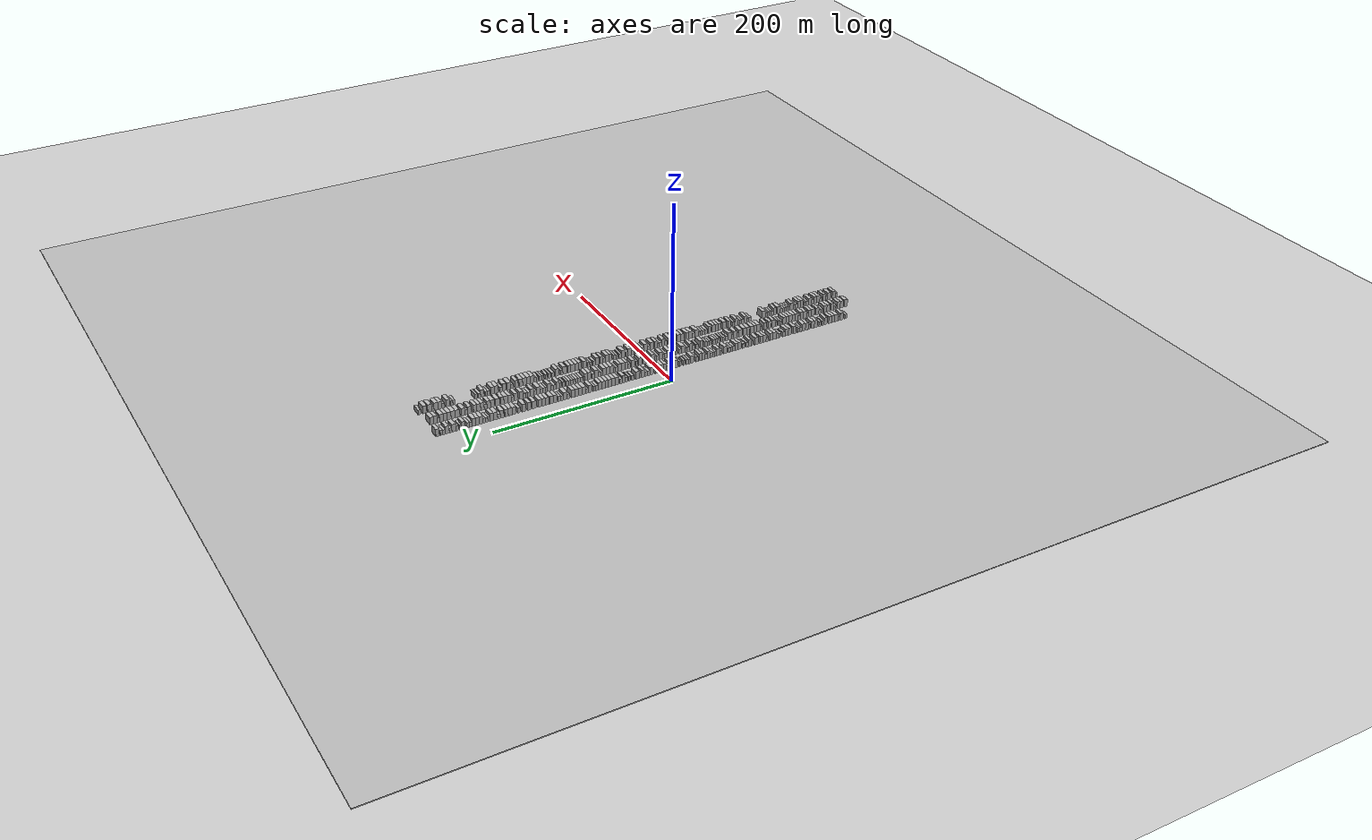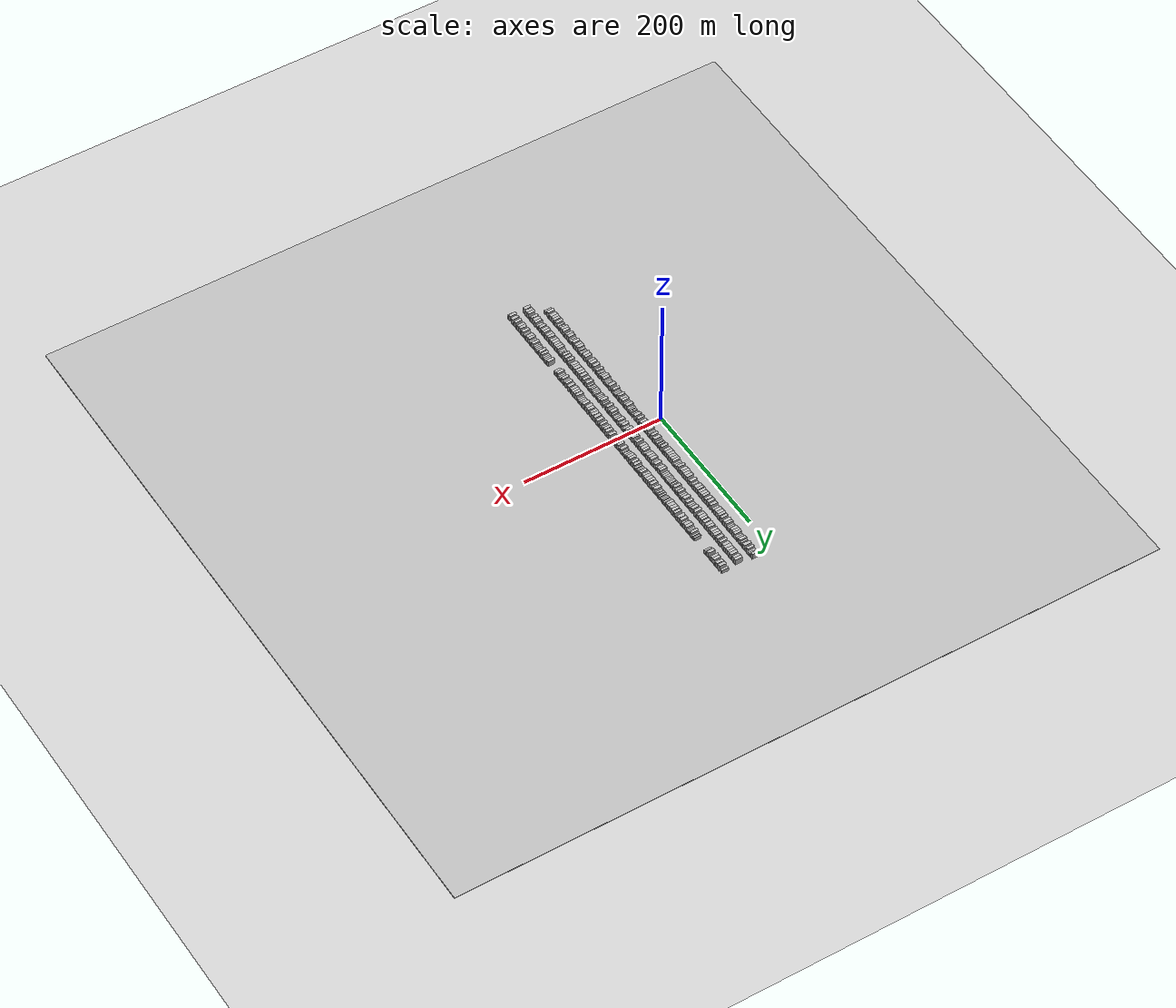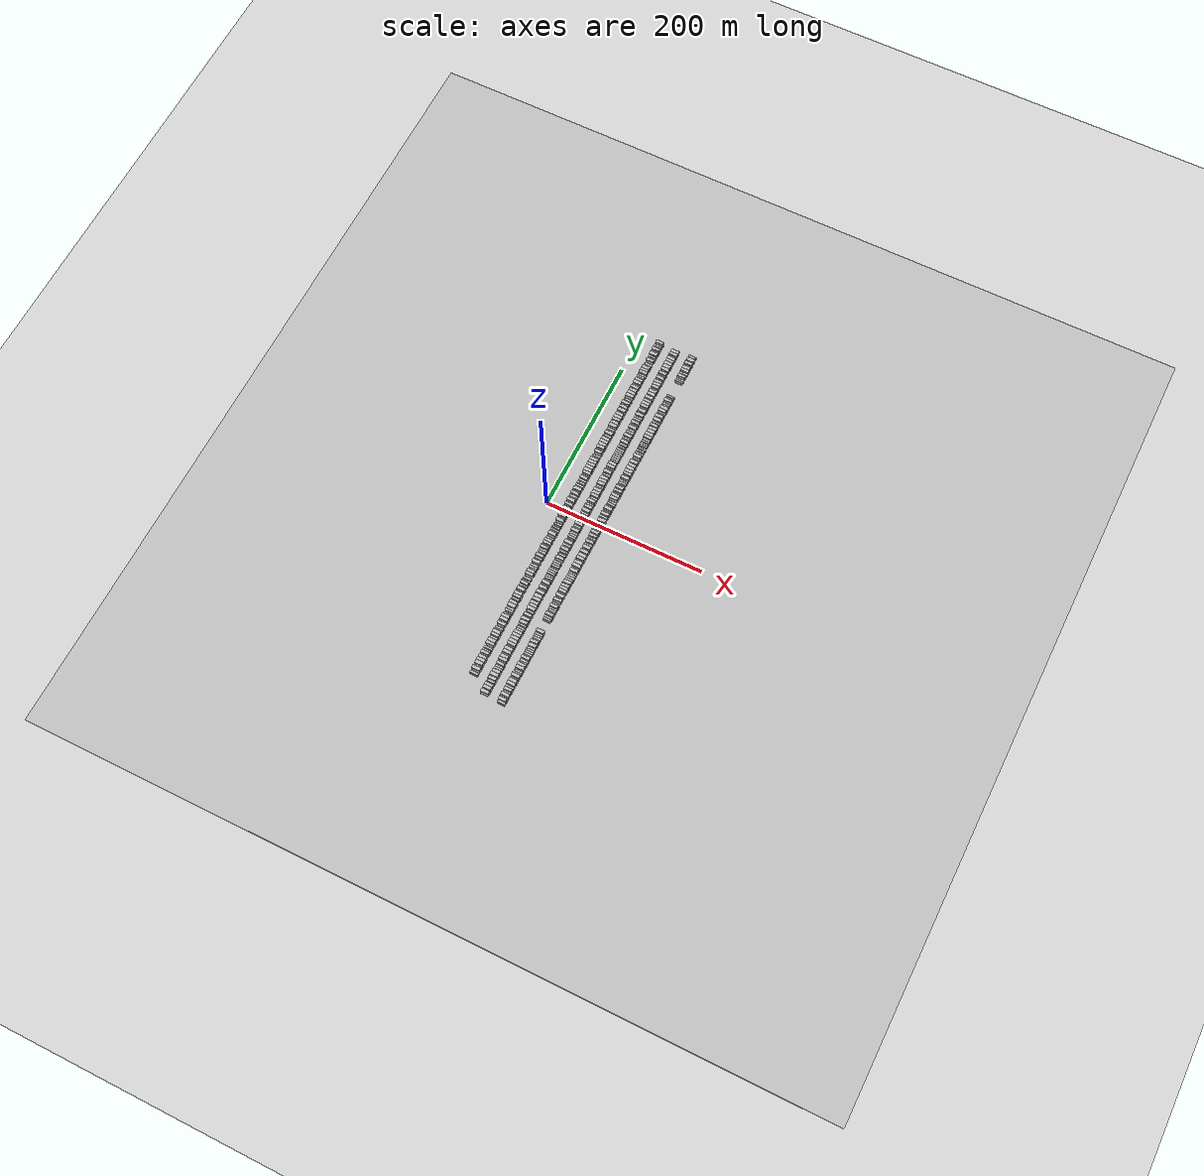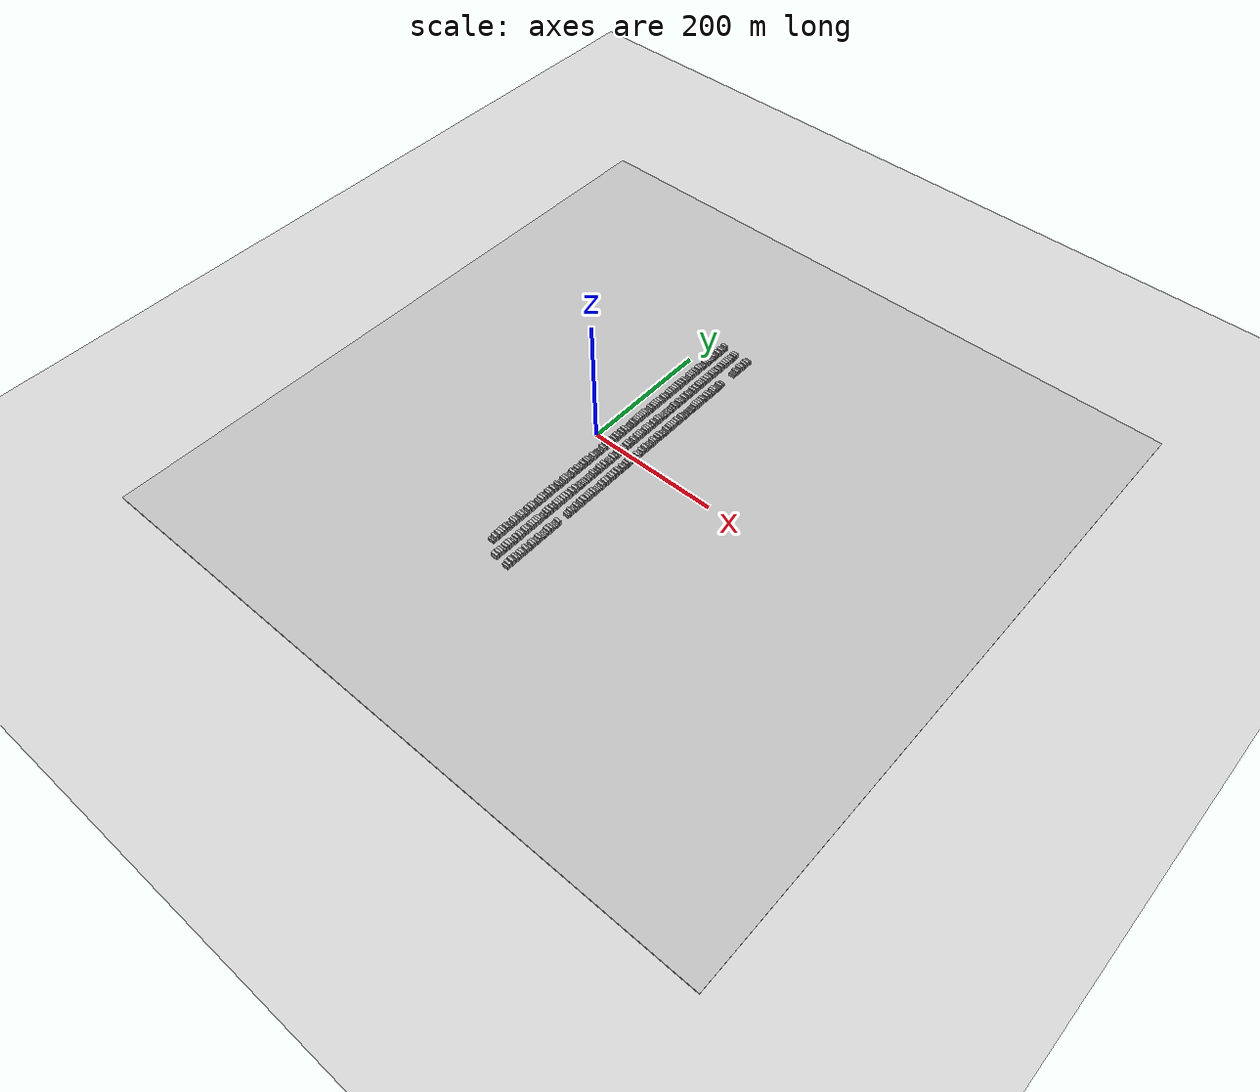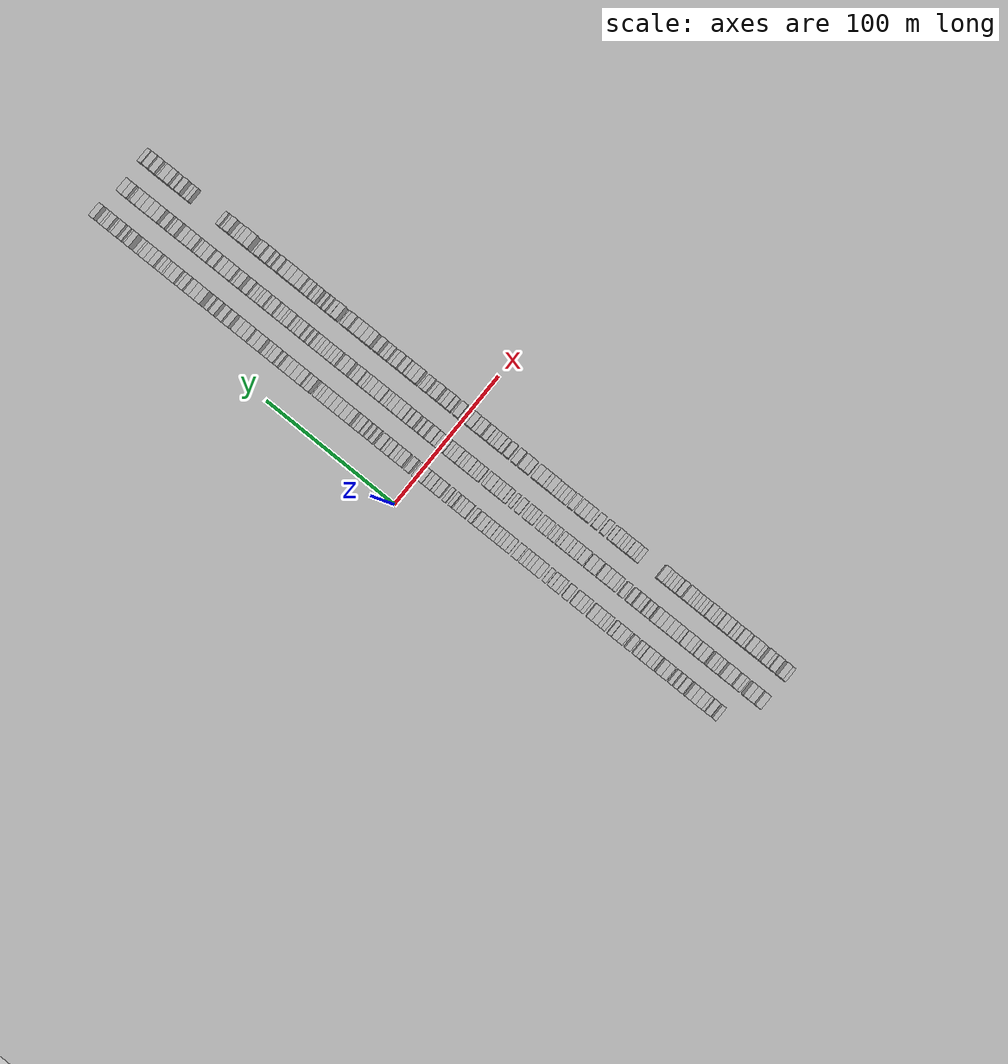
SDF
<?xml version="1.0" encoding="utf-8"?>

<sdf version="1.6">

   <world name="default">

      <gui fullscreen="0">

         <camera name="user_camera">

            <pose>-15 0 4.57585 0 0 0</pose>

            <view_controller>orbit</view_controller>

         </camera>

      </gui>

      <scene>

         <sky>

           <clouds>

             <speed>12</speed>

           </clouds>

         </sky>

         <ambient>0.4 0.4 0.4 1</ambient>

         <background>0.7 0.7 0.7 1</background>

         <shadows>1</shadows>

      </scene>

      <gravity>0 0 -9.8066</gravity>

      <magnetic_field>6e-06 2.3e-05 -4.2e-05</magnetic_field>

      <physics default="0" name="default_physics" type="ode">

         <ode>

            <solver>

               <type>quick</type>

               <iters>10</iters>

               <sor>1.0</sor>

               <use_dynamic_moi_rescaling>0</use_dynamic_moi_rescaling>

            </solver>

            <constraints>

               <cfm>0</cfm>

               <erp>0.2</erp>

               <contact_max_correcting_vel>100</contact_max_correcting_vel>

               <contact_surface_layer>0.001</contact_surface_layer>

            </constraints>

         </ode>

         <max_step_size>0.004</max_step_size>

         <real_time_factor>1</real_time_factor>

         <real_time_update_rate>250</real_time_update_rate>

      </physics>

      <light name="sun" type="directional">

         <cast_shadows>1</cast_shadows>

         <pose>0 0 10 0 0 0</pose>

         <diffuse>0.8 0.8 0.8 1</diffuse>

         <specular>0.2 0.2 0.2 1</specular>

         <attenuation>

            <range>1000</range>

            <constant>0.9</constant>

            <linear>0.01</linear>

            <quadratic>0.001</quadratic>

         </attenuation>

         <direction>-0.5 0.1 -0.9</direction>

      </light>

      <include>

         <name>ground_plane_1</name>

         <uri>model://HANNAS_ground_plane</uri>

         <pose>0 0 0  0 0 0</pose>

      </include>

      <include>

         <name>ground_plane_2</name>

         <uri>model://HANNAS_ground_plane</uri>

         <pose>100 0 0  0 0 0</pose>

      </include>

      <model name="building_1">

         <static>1</static>

         <pose frame="">25.0000 -228.7704 0 0.000000 0.000000 0.000000</pose>

         <link name="link">

            <pose frame="">0 0 3.00 0 0 0</pose>

            <collision name="collision">

               <geometry>

                  <box>

                     <size>10.0000 2.8197 6.0000</size>

                  </box>

               </geometry>

               <max_contacts>10</max_contacts>

               <surface>

                  <contact>

                     <ode/>

                  </contact>

                  <bounce/>

                  <friction>

                     <torsional>

                        <ode/>

                     </torsional>

                     <ode/>

                  </friction>

               </surface>

            </collision>

            <visual name="visual">

               <cast_shadows>0</cast_shadows>

               <geometry>

                  <box>

                     <size>10.0000 2.8197 6.0000</size>

                  </box>

               </geometry>

               <material>

                  <script>

                     <uri>model://HANNAS_wall/materials/scripts</uri>

                     <uri>model://HANNAS_wall/materials/textures</uri>

                     <name>vrc/HANNAS_wall</name>

                  </script>

               </material>

            </visual>

            <self_collide>0</self_collide>

            <enable_wind>0</enable_wind>

            <kinematic>0</kinematic>

         </link>

      </model>

      <model name="building_2">

         <static>1</static>

         <pose frame="">25.0000 -223.2506 0 0.000000 0.000000 0.000000</pose>

         <link name="link">

            <pose frame="">0 0 4.50 0 0 0</pose>

            <collision name="collision">

               <geometry>

                  <box>

                     <size>10.0000 4.2198 9.0000</size>

                  </box>

               </geometry>

               <max_contacts>10</max_contacts>

               <surface>

                  <contact>

                     <ode/>

                  </contact>

                  <bounce/>

                  <friction>

                     <torsional>

                        <ode/>

                     </torsional>

                     <ode/>

                  </friction>

               </surface>

            </collision>

            <visual name="visual">

               <cast_shadows>0</cast_shadows>

               <geometry>

                  <box>

                     <size>10.0000 4.2198 9.0000</size>

                  </box>

               </geometry>

               <material>

                  <script>

                     <uri>model://HANNAS_wall/materials/scripts</uri>

                     <uri>model://HANNAS_wall/materials/textures</uri>

                     <name>vrc/HANNAS_wall</name>

                  </script>

               </material>

            </visual>

            <self_collide>0</self_collide>

            <enable_wind>0</enable_wind>

            <kinematic>0</kinematic>

         </link>

      </model>

      <model name="building_3">

         <static>1</static>

         <pose frame="">25.0000 -219.8380 0 0.000000 0.000000 0.000000</pose>

         <link name="link">

            <pose frame="">0 0 3.00 0 0 0</pose>

            <collision name="collision">

               <geometry>

                  <box>

                     <size>10.0000 2.6054 6.0000</size>

                  </box>

               </geometry>

               <max_contacts>10</max_contacts>

               <surface>

                  <contact>

                     <ode/>

                  </contact>

                  <bounce/>

                  <friction>

                     <torsional>

                        <ode/>

                     </torsional>

                     <ode/>

                  </friction>

               </surface>

            </collision>

            <visual name="visual">

               <cast_shadows>0</cast_shadows>

               <geometry>

                  <box>

                     <size>10.0000 2.6054 6.0000</size>

                  </box>

               </geometry>

               <material>

                  <script>

                     <uri>model://HANNAS_wall/materials/scripts</uri>

                     <uri>model://HANNAS_wall/materials/textures</uri>

                     <name>vrc/HANNAS_wall</name>

                  </script>

               </material>

            </visual>

            <self_collide>0</self_collide>

            <enable_wind>0</enable_wind>

            <kinematic>0</kinematic>

         </link>

      </model>

      <model name="building_4">

         <static>1</static>

         <pose frame="">25.0000 -216.2932 0 0.000000 0.000000 0.000000</pose>

         <link name="link">

            <pose frame="">0 0 4.50 0 0 0</pose>

            <collision name="collision">

               <geometry>

                  <box>

                     <size>10.0000 4.4841 9.0000</size>

                  </box>

               </geometry>

               <max_contacts>10</max_contacts>

               <surface>

                  <contact>

                     <ode/>

                  </contact>

                  <bounce/>

                  <friction>

                     <torsional>

                        <ode/>

                     </torsional>

                     <ode/>

                  </friction>

               </surface>

            </collision>

            <visual name="visual">

               <cast_shadows>0</cast_shadows>

               <geometry>

                  <box>

                     <size>10.0000 4.4841 9.0000</size>

                  </box>

               </geometry>

               <material>

                  <script>

                     <uri>model://HANNAS_wall/materials/scripts</uri>

                     <uri>model://HANNAS_wall/materials/textures</uri>

                     <name>vrc/HANNAS_wall</name>

                  </script>

               </material>

            </visual>

            <self_collide>0</self_collide>

            <enable_wind>0</enable_wind>

            <kinematic>0</kinematic>

         </link>

      </model>

      <model name="building_5">

         <static>1</static>

         <pose frame="">25.0000 -212.0790 0 0.000000 0.000000 0.000000</pose>

         <link name="link">

            <pose frame="">0 0 4.50 0 0 0</pose>

            <collision name="collision">

               <geometry>

                  <box>

                     <size>10.0000 3.9443 9.0000</size>

                  </box>

               </geometry>

               <max_contacts>10</max_contacts>

               <surface>

                  <contact>

                     <ode/>

                  </contact>

                  <bounce/>

                  <friction>

                     <torsional>

                        <ode/>

                     </torsional>

                     <ode/>

                  </friction>

               </surface>

            </collision>

            <visual name="visual">

               <cast_shadows>0</cast_shadows>

               <geometry>

                  <box>

                     <size>10.0000 3.9443 9.0000</size>

                  </box>

               </geometry>

               <material>

                  <script>

                     <uri>model://HANNAS_wall/materials/scripts</uri>

                     <uri>model://HANNAS_wall/materials/textures</uri>

                     <name>vrc/HANNAS_wall</name>

                  </script>

               </material>

            </visual>

            <self_collide>0</self_collide>

            <enable_wind>0</enable_wind>

            <kinematic>0</kinematic>

         </link>

      </model>

      <model name="building_6">

         <static>1</static>

         <pose frame="">25.0000 -208.1779 0 0.000000 0.000000 0.000000</pose>

         <link name="link">

            <pose frame="">0 0 4.50 0 0 0</pose>

            <collision name="collision">

               <geometry>

                  <box>

                     <size>10.0000 3.8578 9.0000</size>

                  </box>

               </geometry>

               <max_contacts>10</max_contacts>

               <surface>

                  <contact>

                     <ode/>

                  </contact>

                  <bounce/>

                  <friction>

                     <torsional>

                        <ode/>

                     </torsional>

                     <ode/>

                  </friction>

               </surface>

            </collision>

            <visual name="visual">

               <cast_shadows>0</cast_shadows>

               <geometry>

                  <box>

                     <size>10.0000 3.8578 9.0000</size>

                  </box>

               </geometry>

               <material>

                  <script>

                     <uri>model://HANNAS_wall/materials/scripts</uri>

                     <uri>model://HANNAS_wall/materials/textures</uri>

                     <name>vrc/HANNAS_wall</name>

                  </script>

               </material>

            </visual>

            <self_collide>0</self_collide>

            <enable_wind>0</enable_wind>

            <kinematic>0</kinematic>

         </link>

      </model>

      <model name="building_7">

         <static>1</static>

         <pose frame="">25.0000 -202.3399 0 0.000000 0.000000 0.000000</pose>

         <link name="link">

            <pose frame="">0 0 4.50 0 0 0</pose>

            <collision name="collision">

               <geometry>

                  <box>

                     <size>10.0000 3.8181 9.0000</size>

                  </box>

               </geometry>

               <max_contacts>10</max_contacts>

               <surface>

                  <contact>

                     <ode/>

                  </contact>

                  <bounce/>

                  <friction>

                     <torsional>

                        <ode/>

                     </torsional>

                     <ode/>

                  </friction>

               </surface>

            </collision>

            <visual name="visual">

               <cast_shadows>0</cast_shadows>

               <geometry>

                  <box>

                     <size>10.0000 3.8181 9.0000</size>

                  </box>

               </geometry>

               <material>

                  <script>

                     <uri>model://HANNAS_wall/materials/scripts</uri>

                     <uri>model://HANNAS_wall/materials/textures</uri>

                     <name>vrc/HANNAS_wall</name>

                  </script>

               </material>

            </visual>

            <self_collide>0</self_collide>

            <enable_wind>0</enable_wind>

            <kinematic>0</kinematic>

         </link>

      </model>

      <model name="building_8">

         <static>1</static>

         <pose frame="">25.0000 -198.9466 0 0.000000 0.000000 0.000000</pose>

         <link name="link">

            <pose frame="">0 0 3.00 0 0 0</pose>

            <collision name="collision">

               <geometry>

                  <box>

                     <size>10.0000 2.9685 6.0000</size>

                  </box>

               </geometry>

               <max_contacts>10</max_contacts>

               <surface>

                  <contact>

                     <ode/>

                  </contact>

                  <bounce/>

                  <friction>

                     <torsional>

                        <ode/>

                     </torsional>

                     <ode/>

                  </friction>

               </surface>

            </collision>

            <visual name="visual">

               <cast_shadows>0</cast_shadows>

               <geometry>

                  <box>

                     <size>10.0000 2.9685 6.0000</size>

                  </box>

               </geometry>

               <material>

                  <script>

                     <uri>model://HANNAS_wall/materials/scripts</uri>

                     <uri>model://HANNAS_wall/materials/textures</uri>

                     <name>vrc/HANNAS_wall</name>

                  </script>

               </material>

            </visual>

            <self_collide>0</self_collide>

            <enable_wind>0</enable_wind>

            <kinematic>0</kinematic>

         </link>

      </model>

      <model name="building_9">

         <static>1</static>

         <pose frame="">25.0000 -195.0524 0 0.000000 0.000000 0.000000</pose>

         <link name="link">

            <pose frame="">0 0 3.00 0 0 0</pose>

            <collision name="collision">

               <geometry>

                  <box>

                     <size>10.0000 2.8199 6.0000</size>

                  </box>

               </geometry>

               <max_contacts>10</max_contacts>

               <surface>

                  <contact>

                     <ode/>

                  </contact>

                  <bounce/>

                  <friction>

                     <torsional>

                        <ode/>

                     </torsional>

                     <ode/>

                  </friction>

               </surface>

            </collision>

            <visual name="visual">

               <cast_shadows>0</cast_shadows>

               <geometry>

                  <box>

                     <size>10.0000 2.8199 6.0000</size>

                  </box>

               </geometry>

               <material>

                  <script>

                     <uri>model://HANNAS_wall/materials/scripts</uri>

                     <uri>model://HANNAS_wall/materials/textures</uri>

                     <name>vrc/HANNAS_wall</name>

                  </script>

               </material>

            </visual>

            <self_collide>0</self_collide>

            <enable_wind>0</enable_wind>

            <kinematic>0</kinematic>

         </link>

      </model>

      <model name="building_10">

         <static>1</static>

         <pose frame="">25.0000 -189.6579 0 0.000000 0.000000 0.000000</pose>

         <link name="link">

            <pose frame="">0 0 4.50 0 0 0</pose>

            <collision name="collision">

               <geometry>

                  <box>

                     <size>10.0000 3.9692 9.0000</size>

                  </box>

               </geometry>

               <max_contacts>10</max_contacts>

               <surface>

                  <contact>

                     <ode/>

                  </contact>

                  <bounce/>

                  <friction>

                     <torsional>

                        <ode/>

                     </torsional>

                     <ode/>

                  </friction>

               </surface>

            </collision>

            <visual name="visual">

               <cast_shadows>0</cast_shadows>

               <geometry>

                  <box>

                     <size>10.0000 3.9692 9.0000</size>

                  </box>

               </geometry>

               <material>

                  <script>

                     <uri>model://HANNAS_wall/materials/scripts</uri>

                     <uri>model://HANNAS_wall/materials/textures</uri>

                     <name>vrc/HANNAS_wall</name>

                  </script>

               </material>

            </visual>

            <self_collide>0</self_collide>

            <enable_wind>0</enable_wind>

            <kinematic>0</kinematic>

         </link>

      </model>

      <model name="building_11">

         <static>1</static>

         <pose frame="">25.0000 -185.6119 0 0.000000 0.000000 0.000000</pose>

         <link name="link">

            <pose frame="">0 0 4.50 0 0 0</pose>

            <collision name="collision">

               <geometry>

                  <box>

                     <size>10.0000 4.1227 9.0000</size>

                  </box>

               </geometry>

               <max_contacts>10</max_contacts>

               <surface>

                  <contact>

                     <ode/>

                  </contact>

                  <bounce/>

                  <friction>

                     <torsional>

                        <ode/>

                     </torsional>

                     <ode/>

                  </friction>

               </surface>

            </collision>

            <visual name="visual">

               <cast_shadows>0</cast_shadows>

               <geometry>

                  <box>

                     <size>10.0000 4.1227 9.0000</size>

                  </box>

               </geometry>

               <material>

                  <script>

                     <uri>model://HANNAS_wall/materials/scripts</uri>

                     <uri>model://HANNAS_wall/materials/textures</uri>

                     <name>vrc/HANNAS_wall</name>

                  </script>

               </material>

            </visual>

            <self_collide>0</self_collide>

            <enable_wind>0</enable_wind>

            <kinematic>0</kinematic>

         </link>

      </model>

      <model name="building_12">

         <static>1</static>

         <pose frame="">25.0000 -181.2308 0 0.000000 0.000000 0.000000</pose>

         <link name="link">

            <pose frame="">0 0 3.00 0 0 0</pose>

            <collision name="collision">

               <geometry>

                  <box>

                     <size>10.0000 2.6395 6.0000</size>

                  </box>

               </geometry>

               <max_contacts>10</max_contacts>

               <surface>

                  <contact>

                     <ode/>

                  </contact>

                  <bounce/>

                  <friction>

                     <torsional>

                        <ode/>

                     </torsional>

                     <ode/>

                  </friction>

               </surface>

            </collision>

            <visual name="visual">

               <cast_shadows>0</cast_shadows>

               <geometry>

                  <box>

                     <size>10.0000 2.6395 6.0000</size>

                  </box>

               </geometry>

               <material>

                  <script>

                     <uri>model://HANNAS_wall/materials/scripts</uri>

                     <uri>model://HANNAS_wall/materials/textures</uri>

                     <name>vrc/HANNAS_wall</name>

                  </script>

               </material>

            </visual>

            <self_collide>0</self_collide>

            <enable_wind>0</enable_wind>

            <kinematic>0</kinematic>

         </link>

      </model>

      <model name="building_13">

         <static>1</static>

         <pose frame="">25.0000 -178.1024 0 0.000000 0.000000 0.000000</pose>

         <link name="link">

            <pose frame="">0 0 4.50 0 0 0</pose>

            <collision name="collision">

               <geometry>

                  <box>

                     <size>10.0000 3.6172 9.0000</size>

                  </box>

               </geometry>

               <max_contacts>10</max_contacts>

               <surface>

                  <contact>

                     <ode/>

                  </contact>

                  <bounce/>

                  <friction>

                     <torsional>

                        <ode/>

                     </torsional>

                     <ode/>

                  </friction>

               </surface>

            </collision>

            <visual name="visual">

               <cast_shadows>0</cast_shadows>

               <geometry>

                  <box>

                     <size>10.0000 3.6172 9.0000</size>

                  </box>

               </geometry>

               <material>

                  <script>

                     <uri>model://HANNAS_wall/materials/scripts</uri>

                     <uri>model://HANNAS_wall/materials/textures</uri>

                     <name>vrc/HANNAS_wall</name>

                  </script>

               </material>

            </visual>

            <self_collide>0</self_collide>

            <enable_wind>0</enable_wind>

            <kinematic>0</kinematic>

         </link>

      </model>

      <model name="building_14">

         <static>1</static>

         <pose frame="">25.0000 -174.0741 0 0.000000 0.000000 0.000000</pose>

         <link name="link">

            <pose frame="">0 0 4.50 0 0 0</pose>

            <collision name="collision">

               <geometry>

                  <box>

                     <size>10.0000 4.4394 9.0000</size>

                  </box>

               </geometry>

               <max_contacts>10</max_contacts>

               <surface>

                  <contact>

                     <ode/>

                  </contact>

                  <bounce/>

                  <friction>

                     <torsional>

                        <ode/>

                     </torsional>

                     <ode/>

                  </friction>

               </surface>

            </collision>

            <visual name="visual">

               <cast_shadows>0</cast_shadows>

               <geometry>

                  <box>

                     <size>10.0000 4.4394 9.0000</size>

                  </box>

               </geometry>

               <material>

                  <script>

                     <uri>model://HANNAS_wall/materials/scripts</uri>

                     <uri>model://HANNAS_wall/materials/textures</uri>

                     <name>vrc/HANNAS_wall</name>

                  </script>

               </material>

            </visual>

            <self_collide>0</self_collide>

            <enable_wind>0</enable_wind>

            <kinematic>0</kinematic>

         </link>

      </model>

      <model name="building_15">

         <static>1</static>

         <pose frame="">25.0000 -170.5755 0 0.000000 0.000000 0.000000</pose>

         <link name="link">

            <pose frame="">0 0 3.00 0 0 0</pose>

            <collision name="collision">

               <geometry>

                  <box>

                     <size>10.0000 2.5579 6.0000</size>

                  </box>

               </geometry>

               <max_contacts>10</max_contacts>

               <surface>

                  <contact>

                     <ode/>

                  </contact>

                  <bounce/>

                  <friction>

                     <torsional>

                        <ode/>

                     </torsional>

                     <ode/>

                  </friction>

               </surface>

            </collision>

            <visual name="visual">

               <cast_shadows>0</cast_shadows>

               <geometry>

                  <box>

                     <size>10.0000 2.5579 6.0000</size>

                  </box>

               </geometry>

               <material>

                  <script>

                     <uri>model://HANNAS_wall/materials/scripts</uri>

                     <uri>model://HANNAS_wall/materials/textures</uri>

                     <name>vrc/HANNAS_wall</name>

                  </script>

               </material>

            </visual>

            <self_collide>0</self_collide>

            <enable_wind>0</enable_wind>

            <kinematic>0</kinematic>

         </link>

      </model>

      <model name="building_16">

         <static>1</static>

         <pose frame="">25.0000 -167.9083 0 0.000000 0.000000 0.000000</pose>

         <link name="link">

            <pose frame="">0 0 3.00 0 0 0</pose>

            <collision name="collision">

               <geometry>

                  <box>

                     <size>10.0000 2.7765 6.0000</size>

                  </box>

               </geometry>

               <max_contacts>10</max_contacts>

               <surface>

                  <contact>

                     <ode/>

                  </contact>

                  <bounce/>

                  <friction>

                     <torsional>

                        <ode/>

                     </torsional>

                     <ode/>

                  </friction>

               </surface>

            </collision>

            <visual name="visual">

               <cast_shadows>0</cast_shadows>

               <geometry>

                  <box>

                     <size>10.0000 2.7765 6.0000</size>

                  </box>

               </geometry>

               <material>

                  <script>

                     <uri>model://HANNAS_wall/materials/scripts</uri>

                     <uri>model://HANNAS_wall/materials/textures</uri>

                     <name>vrc/HANNAS_wall</name>

                  </script>

               </material>

            </visual>

            <self_collide>0</self_collide>

            <enable_wind>0</enable_wind>

            <kinematic>0</kinematic>

         </link>

      </model>

      <model name="building_17">

         <static>1</static>

         <pose frame="">25.0000 -162.5040 0 0.000000 0.000000 0.000000</pose>

         <link name="link">

            <pose frame="">0 0 4.50 0 0 0</pose>

            <collision name="collision">

               <geometry>

                  <box>

                     <size>10.0000 4.0319 9.0000</size>

                  </box>

               </geometry>

               <max_contacts>10</max_contacts>

               <surface>

                  <contact>

                     <ode/>

                  </contact>

                  <bounce/>

                  <friction>

                     <torsional>

                        <ode/>

                     </torsional>

                     <ode/>

                  </friction>

               </surface>

            </collision>

            <visual name="visual">

               <cast_shadows>0</cast_shadows>

               <geometry>

                  <box>

                     <size>10.0000 4.0319 9.0000</size>

                  </box>

               </geometry>

               <material>

                  <script>

                     <uri>model://HANNAS_wall/materials/scripts</uri>

                     <uri>model://HANNAS_wall/materials/textures</uri>

                     <name>vrc/HANNAS_wall</name>

                  </script>

               </material>

            </visual>

            <self_collide>0</self_collide>

            <enable_wind>0</enable_wind>

            <kinematic>0</kinematic>

         </link>

      </model>

      <model name="building_18">

         <static>1</static>

         <pose frame="">25.0000 -156.4825 0 0.000000 0.000000 0.000000</pose>

         <link name="link">

            <pose frame="">0 0 4.50 0 0 0</pose>

            <collision name="collision">

               <geometry>

                  <box>

                     <size>10.0000 4.0112 9.0000</size>

                  </box>

               </geometry>

               <max_contacts>10</max_contacts>

               <surface>

                  <contact>

                     <ode/>

                  </contact>

                  <bounce/>

                  <friction>

                     <torsional>

                        <ode/>

                     </torsional>

                     <ode/>

                  </friction>

               </surface>

            </collision>

            <visual name="visual">

               <cast_shadows>0</cast_shadows>

               <geometry>

                  <box>

                     <size>10.0000 4.0112 9.0000</size>

                  </box>

               </geometry>

               <material>

                  <script>

                     <uri>model://HANNAS_wall/materials/scripts</uri>

                     <uri>model://HANNAS_wall/materials/textures</uri>

                     <name>vrc/HANNAS_wall</name>

                  </script>

               </material>

            </visual>

            <self_collide>0</self_collide>

            <enable_wind>0</enable_wind>

            <kinematic>0</kinematic>

         </link>

      </model>

      <model name="building_19">

         <static>1</static>

         <pose frame="">25.0000 -152.3724 0 0.000000 0.000000 0.000000</pose>

         <link name="link">

            <pose frame="">0 0 4.50 0 0 0</pose>

            <collision name="collision">

               <geometry>

                  <box>

                     <size>10.0000 4.2090 9.0000</size>

                  </box>

               </geometry>

               <max_contacts>10</max_contacts>

               <surface>

                  <contact>

                     <ode/>

                  </contact>

                  <bounce/>

                  <friction>

                     <torsional>

                        <ode/>

                     </torsional>

                     <ode/>

                  </friction>

               </surface>

            </collision>

            <visual name="visual">

               <cast_shadows>0</cast_shadows>

               <geometry>

                  <box>

                     <size>10.0000 4.2090 9.0000</size>

                  </box>

               </geometry>

               <material>

                  <script>

                     <uri>model://HANNAS_wall/materials/scripts</uri>

                     <uri>model://HANNAS_wall/materials/textures</uri>

                     <name>vrc/HANNAS_wall</name>

                  </script>

               </material>

            </visual>

            <self_collide>0</self_collide>

            <enable_wind>0</enable_wind>

            <kinematic>0</kinematic>

         </link>

      </model>

      <model name="building_20">

         <static>1</static>

         <pose frame="">25.0000 -148.8655 0 0.000000 0.000000 0.000000</pose>

         <link name="link">

            <pose frame="">0 0 3.00 0 0 0</pose>

            <collision name="collision">

               <geometry>

                  <box>

                     <size>10.0000 2.8047 6.0000</size>

                  </box>

               </geometry>

               <max_contacts>10</max_contacts>

               <surface>

                  <contact>

                     <ode/>

                  </contact>

                  <bounce/>

                  <friction>

                     <torsional>

                        <ode/>

                     </torsional>

                     <ode/>

                  </friction>

               </surface>

            </collision>

            <visual name="visual">

               <cast_shadows>0</cast_shadows>

               <geometry>

                  <box>

                     <size>10.0000 2.8047 6.0000</size>

                  </box>

               </geometry>

               <material>

                  <script>

                     <uri>model://HANNAS_wall/materials/scripts</uri>

                     <uri>model://HANNAS_wall/materials/textures</uri>

                     <name>vrc/HANNAS_wall</name>

                  </script>

               </material>

            </visual>

            <self_collide>0</self_collide>

            <enable_wind>0</enable_wind>

            <kinematic>0</kinematic>

         </link>

      </model>

      <model name="building_21">

         <static>1</static>

         <pose frame="">25.0000 -144.0431 0 0.000000 0.000000 0.000000</pose>

         <link name="link">

            <pose frame="">0 0 3.00 0 0 0</pose>

            <collision name="collision">

               <geometry>

                  <box>

                     <size>10.0000 2.8402 6.0000</size>

                  </box>

               </geometry>

               <max_contacts>10</max_contacts>

               <surface>

                  <contact>

                     <ode/>

                  </contact>

                  <bounce/>

                  <friction>

                     <torsional>

                        <ode/>

                     </torsional>

                     <ode/>

                  </friction>

               </surface>

            </collision>

            <visual name="visual">

               <cast_shadows>0</cast_shadows>

               <geometry>

                  <box>

                     <size>10.0000 2.8402 6.0000</size>

                  </box>

               </geometry>

               <material>

                  <script>

                     <uri>model://HANNAS_wall/materials/scripts</uri>

                     <uri>model://HANNAS_wall/materials/textures</uri>

                     <name>vrc/HANNAS_wall</name>

                  </script>

               </material>

            </visual>

            <self_collide>0</self_collide>

            <enable_wind>0</enable_wind>

            <kinematic>0</kinematic>

         </link>

      </model>

      <model name="building_22">

         <static>1</static>

         <pose frame="">25.0000 -141.1653 0 0.000000 0.000000 0.000000</pose>

         <link name="link">

            <pose frame="">0 0 3.00 0 0 0</pose>

            <collision name="collision">

               <geometry>

                  <box>

                     <size>10.0000 2.9154 6.0000</size>

                  </box>

               </geometry>

               <max_contacts>10</max_contacts>

               <surface>

                  <contact>

                     <ode/>

                  </contact>

                  <bounce/>

                  <friction>

                     <torsional>

                        <ode/>

                     </torsional>

                     <ode/>

                  </friction>

               </surface>

            </collision>

            <visual name="visual">

               <cast_shadows>0</cast_shadows>

               <geometry>

                  <box>

                     <size>10.0000 2.9154 6.0000</size>

                  </box>

               </geometry>

               <material>

                  <script>

                     <uri>model://HANNAS_wall/materials/scripts</uri>

                     <uri>model://HANNAS_wall/materials/textures</uri>

                     <name>vrc/HANNAS_wall</name>

                  </script>

               </material>

            </visual>

            <self_collide>0</self_collide>

            <enable_wind>0</enable_wind>

            <kinematic>0</kinematic>

         </link>

      </model>

      <model name="building_23">

         <static>1</static>

         <pose frame="">25.0000 -137.4626 0 0.000000 0.000000 0.000000</pose>

         <link name="link">

            <pose frame="">0 0 4.50 0 0 0</pose>

            <collision name="collision">

               <geometry>

                  <box>

                     <size>10.0000 4.4899 9.0000</size>

                  </box>

               </geometry>

               <max_contacts>10</max_contacts>

               <surface>

                  <contact>

                     <ode/>

                  </contact>

                  <bounce/>

                  <friction>

                     <torsional>

                        <ode/>

                     </torsional>

                     <ode/>

                  </friction>

               </surface>

            </collision>

            <visual name="visual">

               <cast_shadows>0</cast_shadows>

               <geometry>

                  <box>

                     <size>10.0000 4.4899 9.0000</size>

                  </box>

               </geometry>

               <material>

                  <script>

                     <uri>model://HANNAS_wall/materials/scripts</uri>

                     <uri>model://HANNAS_wall/materials/textures</uri>

                     <name>vrc/HANNAS_wall</name>

                  </script>

               </material>

            </visual>

            <self_collide>0</self_collide>

            <enable_wind>0</enable_wind>

            <kinematic>0</kinematic>

         </link>

      </model>

      <model name="building_24">

         <static>1</static>

         <pose frame="">25.0000 -133.2311 0 0.000000 0.000000 0.000000</pose>

         <link name="link">

            <pose frame="">0 0 4.50 0 0 0</pose>

            <collision name="collision">

               <geometry>

                  <box>

                     <size>10.0000 3.9731 9.0000</size>

                  </box>

               </geometry>

               <max_contacts>10</max_contacts>

               <surface>

                  <contact>

                     <ode/>

                  </contact>

                  <bounce/>

                  <friction>

                     <torsional>

                        <ode/>

                     </torsional>

                     <ode/>

                  </friction>

               </surface>

            </collision>

            <visual name="visual">

               <cast_shadows>0</cast_shadows>

               <geometry>

                  <box>

                     <size>10.0000 3.9731 9.0000</size>

                  </box>

               </geometry>

               <material>

                  <script>

                     <uri>model://HANNAS_wall/materials/scripts</uri>

                     <uri>model://HANNAS_wall/materials/textures</uri>

                     <name>vrc/HANNAS_wall</name>

                  </script>

               </material>

            </visual>

            <self_collide>0</self_collide>

            <enable_wind>0</enable_wind>

            <kinematic>0</kinematic>

         </link>

      </model>

      <model name="building_25">

         <static>1</static>

         <pose frame="">25.0000 -127.8834 0 0.000000 0.000000 0.000000</pose>

         <link name="link">

            <pose frame="">0 0 3.00 0 0 0</pose>

            <collision name="collision">

               <geometry>

                  <box>

                     <size>10.0000 2.7222 6.0000</size>

                  </box>

               </geometry>

               <max_contacts>10</max_contacts>

               <surface>

                  <contact>

                     <ode/>

                  </contact>

                  <bounce/>

                  <friction>

                     <torsional>

                        <ode/>

                     </torsional>

                     <ode/>

                  </friction>

               </surface>

            </collision>

            <visual name="visual">

               <cast_shadows>0</cast_shadows>

               <geometry>

                  <box>

                     <size>10.0000 2.7222 6.0000</size>

                  </box>

               </geometry>

               <material>

                  <script>

                     <uri>model://HANNAS_wall/materials/scripts</uri>

                     <uri>model://HANNAS_wall/materials/textures</uri>

                     <name>vrc/HANNAS_wall</name>

                  </script>

               </material>

            </visual>

            <self_collide>0</self_collide>

            <enable_wind>0</enable_wind>

            <kinematic>0</kinematic>

         </link>

      </model>

      <model name="building_26">

         <static>1</static>

         <pose frame="">25.0000 -124.7177 0 0.000000 0.000000 0.000000</pose>

         <link name="link">

            <pose frame="">0 0 4.50 0 0 0</pose>

            <collision name="collision">

               <geometry>

                  <box>

                     <size>10.0000 3.6093 9.0000</size>

                  </box>

               </geometry>

               <max_contacts>10</max_contacts>

               <surface>

                  <contact>

                     <ode/>

                  </contact>

                  <bounce/>

                  <friction>

                     <torsional>

                        <ode/>

                     </torsional>

                     <ode/>

                  </friction>

               </surface>

            </collision>

            <visual name="visual">

               <cast_shadows>0</cast_shadows>

               <geometry>

                  <box>

                     <size>10.0000 3.6093 9.0000</size>

                  </box>

               </geometry>

               <material>

                  <script>

                     <uri>model://HANNAS_wall/materials/scripts</uri>

                     <uri>model://HANNAS_wall/materials/textures</uri>

                     <name>vrc/HANNAS_wall</name>

                  </script>

               </material>

            </visual>

            <self_collide>0</self_collide>

            <enable_wind>0</enable_wind>

            <kinematic>0</kinematic>

         </link>

      </model>

      <model name="building_27">

         <static>1</static>

         <pose frame="">25.0000 -120.8122 0 0.000000 0.000000 0.000000</pose>

         <link name="link">

            <pose frame="">0 0 4.50 0 0 0</pose>

            <collision name="collision">

               <geometry>

                  <box>

                     <size>10.0000 4.2016 9.0000</size>

                  </box>

               </geometry>

               <max_contacts>10</max_contacts>

               <surface>

                  <contact>

                     <ode/>

                  </contact>

                  <bounce/>

                  <friction>

                     <torsional>

                        <ode/>

                     </torsional>

                     <ode/>

                  </friction>

               </surface>

            </collision>

            <visual name="visual">

               <cast_shadows>0</cast_shadows>

               <geometry>

                  <box>

                     <size>10.0000 4.2016 9.0000</size>

                  </box>

               </geometry>

               <material>

                  <script>

                     <uri>model://HANNAS_wall/materials/scripts</uri>

                     <uri>model://HANNAS_wall/materials/textures</uri>

                     <name>vrc/HANNAS_wall</name>

                  </script>

               </material>

            </visual>

            <self_collide>0</self_collide>

            <enable_wind>0</enable_wind>

            <kinematic>0</kinematic>

         </link>

      </model>

      <model name="building_28">

         <static>1</static>

         <pose frame="">25.0000 -114.5710 0 0.000000 0.000000 0.000000</pose>

         <link name="link">

            <pose frame="">0 0 4.50 0 0 0</pose>

            <collision name="collision">

               <geometry>

                  <box>

                     <size>10.0000 4.2808 9.0000</size>

                  </box>

               </geometry>

               <max_contacts>10</max_contacts>

               <surface>

                  <contact>

                     <ode/>

                  </contact>

                  <bounce/>

                  <friction>

                     <torsional>

                        <ode/>

                     </torsional>

                     <ode/>

                  </friction>

               </surface>

            </collision>

            <visual name="visual">

               <cast_shadows>0</cast_shadows>

               <geometry>

                  <box>

                     <size>10.0000 4.2808 9.0000</size>

                  </box>

               </geometry>

               <material>

                  <script>

                     <uri>model://HANNAS_wall/materials/scripts</uri>

                     <uri>model://HANNAS_wall/materials/textures</uri>

                     <name>vrc/HANNAS_wall</name>

                  </script>

               </material>

            </visual>

            <self_collide>0</self_collide>

            <enable_wind>0</enable_wind>

            <kinematic>0</kinematic>

         </link>

      </model>

      <model name="building_29">

         <static>1</static>

         <pose frame="">25.0000 -109.2100 0 0.000000 0.000000 0.000000</pose>

         <link name="link">

            <pose frame="">0 0 3.00 0 0 0</pose>

            <collision name="collision">

               <geometry>

                  <box>

                     <size>10.0000 2.4412 6.0000</size>

                  </box>

               </geometry>

               <max_contacts>10</max_contacts>

               <surface>

                  <contact>

                     <ode/>

                  </contact>

                  <bounce/>

                  <friction>

                     <torsional>

                        <ode/>

                     </torsional>

                     <ode/>

                  </friction>

               </surface>

            </collision>

            <visual name="visual">

               <cast_shadows>0</cast_shadows>

               <geometry>

                  <box>

                     <size>10.0000 2.4412 6.0000</size>

                  </box>

               </geometry>

               <material>

                  <script>

                     <uri>model://HANNAS_wall/materials/scripts</uri>

                     <uri>model://HANNAS_wall/materials/textures</uri>

                     <name>vrc/HANNAS_wall</name>

                  </script>

               </material>

            </visual>

            <self_collide>0</self_collide>

            <enable_wind>0</enable_wind>

            <kinematic>0</kinematic>

         </link>

      </model>

      <model name="building_30">

         <static>1</static>

         <pose frame="">25.0000 -106.1370 0 0.000000 0.000000 0.000000</pose>

         <link name="link">

            <pose frame="">0 0 4.50 0 0 0</pose>

            <collision name="collision">

               <geometry>

                  <box>

                     <size>10.0000 3.7049 9.0000</size>

                  </box>

               </geometry>

               <max_contacts>10</max_contacts>

               <surface>

                  <contact>

                     <ode/>

                  </contact>

                  <bounce/>

                  <friction>

                     <torsional>

                        <ode/>

                     </torsional>

                     <ode/>

                  </friction>

               </surface>

            </collision>

            <visual name="visual">

               <cast_shadows>0</cast_shadows>

               <geometry>

                  <box>

                     <size>10.0000 3.7049 9.0000</size>

                  </box>

               </geometry>

               <material>

                  <script>

                     <uri>model://HANNAS_wall/materials/scripts</uri>

                     <uri>model://HANNAS_wall/materials/textures</uri>

                     <name>vrc/HANNAS_wall</name>

                  </script>

               </material>

            </visual>

            <self_collide>0</self_collide>

            <enable_wind>0</enable_wind>

            <kinematic>0</kinematic>

         </link>

      </model>

      <model name="building_31">

         <static>1</static>

         <pose frame="">25.0000 -102.8330 0 0.000000 0.000000 0.000000</pose>

         <link name="link">

            <pose frame="">0 0 3.00 0 0 0</pose>

            <collision name="collision">

               <geometry>

                  <box>

                     <size>10.0000 2.9032 6.0000</size>

                  </box>

               </geometry>

               <max_contacts>10</max_contacts>

               <surface>

                  <contact>

                     <ode/>

                  </contact>

                  <bounce/>

                  <friction>

                     <torsional>

                        <ode/>

                     </torsional>

                     <ode/>

                  </friction>

               </surface>

            </collision>

            <visual name="visual">

               <cast_shadows>0</cast_shadows>

               <geometry>

                  <box>

                     <size>10.0000 2.9032 6.0000</size>

                  </box>

               </geometry>

               <material>

                  <script>

                     <uri>model://HANNAS_wall/materials/scripts</uri>

                     <uri>model://HANNAS_wall/materials/textures</uri>

                     <name>vrc/HANNAS_wall</name>

                  </script>

               </material>

            </visual>

            <self_collide>0</self_collide>

            <enable_wind>0</enable_wind>

            <kinematic>0</kinematic>

         </link>

      </model>

      <model name="building_32">

         <static>1</static>

         <pose frame="">25.0000 -98.9385 0 0.000000 0.000000 0.000000</pose>

         <link name="link">

            <pose frame="">0 0 3.00 0 0 0</pose>

            <collision name="collision">

               <geometry>

                  <box>

                     <size>10.0000 2.8858 6.0000</size>

                  </box>

               </geometry>

               <max_contacts>10</max_contacts>

               <surface>

                  <contact>

                     <ode/>

                  </contact>

                  <bounce/>

                  <friction>

                     <torsional>

                        <ode/>

                     </torsional>

                     <ode/>

                  </friction>

               </surface>

            </collision>

            <visual name="visual">

               <cast_shadows>0</cast_shadows>

               <geometry>

                  <box>

                     <size>10.0000 2.8858 6.0000</size>

                  </box>

               </geometry>

               <material>

                  <script>

                     <uri>model://HANNAS_wall/materials/scripts</uri>

                     <uri>model://HANNAS_wall/materials/textures</uri>

                     <name>vrc/HANNAS_wall</name>

                  </script>

               </material>

            </visual>

            <self_collide>0</self_collide>

            <enable_wind>0</enable_wind>

            <kinematic>0</kinematic>

         </link>

      </model>

      <model name="building_33">

         <static>1</static>

         <pose frame="">25.0000 -93.6517 0 0.000000 0.000000 0.000000</pose>

         <link name="link">

            <pose frame="">0 0 4.50 0 0 0</pose>

            <collision name="collision">

               <geometry>

                  <box>

                     <size>10.0000 3.6877 9.0000</size>

                  </box>

               </geometry>

               <max_contacts>10</max_contacts>

               <surface>

                  <contact>

                     <ode/>

                  </contact>

                  <bounce/>

                  <friction>

                     <torsional>

                        <ode/>

                     </torsional>

                     <ode/>

                  </friction>

               </surface>

            </collision>

            <visual name="visual">

               <cast_shadows>0</cast_shadows>

               <geometry>

                  <box>

                     <size>10.0000 3.6877 9.0000</size>

                  </box>

               </geometry>

               <material>

                  <script>

                     <uri>model://HANNAS_wall/materials/scripts</uri>

                     <uri>model://HANNAS_wall/materials/textures</uri>

                     <name>vrc/HANNAS_wall</name>

                  </script>

               </material>

            </visual>

            <self_collide>0</self_collide>

            <enable_wind>0</enable_wind>

            <kinematic>0</kinematic>

         </link>

      </model>

      <model name="building_34">

         <static>1</static>

         <pose frame="">25.0000 -89.8143 0 0.000000 0.000000 0.000000</pose>

         <link name="link">

            <pose frame="">0 0 4.50 0 0 0</pose>

            <collision name="collision">

               <geometry>

                  <box>

                     <size>10.0000 3.9870 9.0000</size>

                  </box>

               </geometry>

               <max_contacts>10</max_contacts>

               <surface>

                  <contact>

                     <ode/>

                  </contact>

                  <bounce/>

                  <friction>

                     <torsional>

                        <ode/>

                     </torsional>

                     <ode/>

                  </friction>

               </surface>

            </collision>

            <visual name="visual">

               <cast_shadows>0</cast_shadows>

               <geometry>

                  <box>

                     <size>10.0000 3.9870 9.0000</size>

                  </box>

               </geometry>

               <material>

                  <script>

                     <uri>model://HANNAS_wall/materials/scripts</uri>

                     <uri>model://HANNAS_wall/materials/textures</uri>

                     <name>vrc/HANNAS_wall</name>

                  </script>

               </material>

            </visual>

            <self_collide>0</self_collide>

            <enable_wind>0</enable_wind>

            <kinematic>0</kinematic>

         </link>

      </model>

      <model name="building_35">

         <static>1</static>

         <pose frame="">25.0000 -86.3713 0 0.000000 0.000000 0.000000</pose>

         <link name="link">

            <pose frame="">0 0 3.00 0 0 0</pose>

            <collision name="collision">

               <geometry>

                  <box>

                     <size>10.0000 2.8990 6.0000</size>

                  </box>

               </geometry>

               <max_contacts>10</max_contacts>

               <surface>

                  <contact>

                     <ode/>

                  </contact>

                  <bounce/>

                  <friction>

                     <torsional>

                        <ode/>

                     </torsional>

                     <ode/>

                  </friction>

               </surface>

            </collision>

            <visual name="visual">

               <cast_shadows>0</cast_shadows>

               <geometry>

                  <box>

                     <size>10.0000 2.8990 6.0000</size>

                  </box>

               </geometry>

               <material>

                  <script>

                     <uri>model://HANNAS_wall/materials/scripts</uri>

                     <uri>model://HANNAS_wall/materials/textures</uri>

                     <name>vrc/HANNAS_wall</name>

                  </script>

               </material>

            </visual>

            <self_collide>0</self_collide>

            <enable_wind>0</enable_wind>

            <kinematic>0</kinematic>

         </link>

      </model>

      <model name="building_36">

         <static>1</static>

         <pose frame="">25.0000 -83.5742 0 0.000000 0.000000 0.000000</pose>

         <link name="link">

            <pose frame="">0 0 3.00 0 0 0</pose>

            <collision name="collision">

               <geometry>

                  <box>

                     <size>10.0000 2.6952 6.0000</size>

                  </box>

               </geometry>

               <max_contacts>10</max_contacts>

               <surface>

                  <contact>

                     <ode/>

                  </contact>

                  <bounce/>

                  <friction>

                     <torsional>

                        <ode/>

                     </torsional>

                     <ode/>

                  </friction>

               </surface>

            </collision>

            <visual name="visual">

               <cast_shadows>0</cast_shadows>

               <geometry>

                  <box>

                     <size>10.0000 2.6952 6.0000</size>

                  </box>

               </geometry>

               <material>

                  <script>

                     <uri>model://HANNAS_wall/materials/scripts</uri>

                     <uri>model://HANNAS_wall/materials/textures</uri>

                     <name>vrc/HANNAS_wall</name>

                  </script>

               </material>

            </visual>

            <self_collide>0</self_collide>

            <enable_wind>0</enable_wind>

            <kinematic>0</kinematic>

         </link>

      </model>

      <model name="building_37">

         <static>1</static>

         <pose frame="">25.0000 -80.8353 0 0.000000 0.000000 0.000000</pose>

         <link name="link">

            <pose frame="">0 0 3.00 0 0 0</pose>

            <collision name="collision">

               <geometry>

                  <box>

                     <size>10.0000 2.7825 6.0000</size>

                  </box>

               </geometry>

               <max_contacts>10</max_contacts>

               <surface>

                  <contact>

                     <ode/>

                  </contact>

                  <bounce/>

                  <friction>

                     <torsional>

                        <ode/>

                     </torsional>

                     <ode/>

                  </friction>

               </surface>

            </collision>

            <visual name="visual">

               <cast_shadows>0</cast_shadows>

               <geometry>

                  <box>

                     <size>10.0000 2.7825 6.0000</size>

                  </box>

               </geometry>

               <material>

                  <script>

                     <uri>model://HANNAS_wall/materials/scripts</uri>

                     <uri>model://HANNAS_wall/materials/textures</uri>

                     <name>vrc/HANNAS_wall</name>

                  </script>

               </material>

            </visual>

            <self_collide>0</self_collide>

            <enable_wind>0</enable_wind>

            <kinematic>0</kinematic>

         </link>

      </model>

      <model name="building_38">

         <static>1</static>

         <pose frame="">25.0000 -76.2479 0 0.000000 0.000000 0.000000</pose>

         <link name="link">

            <pose frame="">0 0 4.50 0 0 0</pose>

            <collision name="collision">

               <geometry>

                  <box>

                     <size>10.0000 4.3922 9.0000</size>

                  </box>

               </geometry>

               <max_contacts>10</max_contacts>

               <surface>

                  <contact>

                     <ode/>

                  </contact>

                  <bounce/>

                  <friction>

                     <torsional>

                        <ode/>

                     </torsional>

                     <ode/>

                  </friction>

               </surface>

            </collision>

            <visual name="visual">

               <cast_shadows>0</cast_shadows>

               <geometry>

                  <box>

                     <size>10.0000 4.3922 9.0000</size>

                  </box>

               </geometry>

               <material>

                  <script>

                     <uri>model://HANNAS_wall/materials/scripts</uri>

                     <uri>model://HANNAS_wall/materials/textures</uri>

                     <name>vrc/HANNAS_wall</name>

                  </script>

               </material>

            </visual>

            <self_collide>0</self_collide>

            <enable_wind>0</enable_wind>

            <kinematic>0</kinematic>

         </link>

      </model>

      <model name="building_39">

         <static>1</static>

         <pose frame="">25.0000 -70.6655 0 0.000000 0.000000 0.000000</pose>

         <link name="link">

            <pose frame="">0 0 3.00 0 0 0</pose>

            <collision name="collision">

               <geometry>

                  <box>

                     <size>10.0000 2.7725 6.0000</size>

                  </box>

               </geometry>

               <max_contacts>10</max_contacts>

               <surface>

                  <contact>

                     <ode/>

                  </contact>

                  <bounce/>

                  <friction>

                     <torsional>

                        <ode/>

                     </torsional>

                     <ode/>

                  </friction>

               </surface>

            </collision>

            <visual name="visual">

               <cast_shadows>0</cast_shadows>

               <geometry>

                  <box>

                     <size>10.0000 2.7725 6.0000</size>

                  </box>

               </geometry>

               <material>

                  <script>

                     <uri>model://HANNAS_wall/materials/scripts</uri>

                     <uri>model://HANNAS_wall/materials/textures</uri>

                     <name>vrc/HANNAS_wall</name>

                  </script>

               </material>

            </visual>

            <self_collide>0</self_collide>

            <enable_wind>0</enable_wind>

            <kinematic>0</kinematic>

         </link>

      </model>

      <model name="building_40">

         <static>1</static>

         <pose frame="">25.0000 -67.4021 0 0.000000 0.000000 0.000000</pose>

         <link name="link">

            <pose frame="">0 0 4.50 0 0 0</pose>

            <collision name="collision">

               <geometry>

                  <box>

                     <size>10.0000 3.7543 9.0000</size>

                  </box>

               </geometry>

               <max_contacts>10</max_contacts>

               <surface>

                  <contact>

                     <ode/>

                  </contact>

                  <bounce/>

                  <friction>

                     <torsional>

                        <ode/>

                     </torsional>

                     <ode/>

                  </friction>

               </surface>

            </collision>

            <visual name="visual">

               <cast_shadows>0</cast_shadows>

               <geometry>

                  <box>

                     <size>10.0000 3.7543 9.0000</size>

                  </box>

               </geometry>

               <material>

                  <script>

                     <uri>model://HANNAS_wall/materials/scripts</uri>

                     <uri>model://HANNAS_wall/materials/textures</uri>

                     <name>vrc/HANNAS_wall</name>

                  </script>

               </material>

            </visual>

            <self_collide>0</self_collide>

            <enable_wind>0</enable_wind>

            <kinematic>0</kinematic>

         </link>

      </model>

      <model name="building_41">

         <static>1</static>

         <pose frame="">25.0000 -64.3100 0 0.000000 0.000000 0.000000</pose>

         <link name="link">

            <pose frame="">0 0 3.00 0 0 0</pose>

            <collision name="collision">

               <geometry>

                  <box>

                     <size>10.0000 2.4299 6.0000</size>

                  </box>

               </geometry>

               <max_contacts>10</max_contacts>

               <surface>

                  <contact>

                     <ode/>

                  </contact>

                  <bounce/>

                  <friction>

                     <torsional>

                        <ode/>

                     </torsional>

                     <ode/>

                  </friction>

               </surface>

            </collision>

            <visual name="visual">

               <cast_shadows>0</cast_shadows>

               <geometry>

                  <box>

                     <size>10.0000 2.4299 6.0000</size>

                  </box>

               </geometry>

               <material>

                  <script>

                     <uri>model://HANNAS_wall/materials/scripts</uri>

                     <uri>model://HANNAS_wall/materials/textures</uri>

                     <name>vrc/HANNAS_wall</name>

                  </script>

               </material>

            </visual>

            <self_collide>0</self_collide>

            <enable_wind>0</enable_wind>

            <kinematic>0</kinematic>

         </link>

      </model>

      <model name="building_42">

         <static>1</static>

         <pose frame="">25.0000 -61.7016 0 0.000000 0.000000 0.000000</pose>

         <link name="link">

            <pose frame="">0 0 3.00 0 0 0</pose>

            <collision name="collision">

               <geometry>

                  <box>

                     <size>10.0000 2.7870 6.0000</size>

                  </box>

               </geometry>

               <max_contacts>10</max_contacts>

               <surface>

                  <contact>

                     <ode/>

                  </contact>

                  <bounce/>

                  <friction>

                     <torsional>

                        <ode/>

                     </torsional>

                     <ode/>

                  </friction>

               </surface>

            </collision>

            <visual name="visual">

               <cast_shadows>0</cast_shadows>

               <geometry>

                  <box>

                     <size>10.0000 2.7870 6.0000</size>

                  </box>

               </geometry>

               <material>

                  <script>

                     <uri>model://HANNAS_wall/materials/scripts</uri>

                     <uri>model://HANNAS_wall/materials/textures</uri>

                     <name>vrc/HANNAS_wall</name>

                  </script>

               </material>

            </visual>

            <self_collide>0</self_collide>

            <enable_wind>0</enable_wind>

            <kinematic>0</kinematic>

         </link>

      </model>

      <model name="building_43">

         <static>1</static>

         <pose frame="">25.0000 -58.9308 0 0.000000 0.000000 0.000000</pose>

         <link name="link">

            <pose frame="">0 0 3.00 0 0 0</pose>

            <collision name="collision">

               <geometry>

                  <box>

                     <size>10.0000 2.7546 6.0000</size>

                  </box>

               </geometry>

               <max_contacts>10</max_contacts>

               <surface>

                  <contact>

                     <ode/>

                  </contact>

                  <bounce/>

                  <friction>

                     <torsional>

                        <ode/>

                     </torsional>

                     <ode/>

                  </friction>

               </surface>

            </collision>

            <visual name="visual">

               <cast_shadows>0</cast_shadows>

               <geometry>

                  <box>

                     <size>10.0000 2.7546 6.0000</size>

                  </box>

               </geometry>

               <material>

                  <script>

                     <uri>model://HANNAS_wall/materials/scripts</uri>

                     <uri>model://HANNAS_wall/materials/textures</uri>

                     <name>vrc/HANNAS_wall</name>

                  </script>

               </material>

            </visual>

            <self_collide>0</self_collide>

            <enable_wind>0</enable_wind>

            <kinematic>0</kinematic>

         </link>

      </model>

      <model name="building_44">

         <static>1</static>

         <pose frame="">25.0000 -55.7358 0 0.000000 0.000000 0.000000</pose>

         <link name="link">

            <pose frame="">0 0 4.50 0 0 0</pose>

            <collision name="collision">

               <geometry>

                  <box>

                     <size>10.0000 3.6356 9.0000</size>

                  </box>

               </geometry>

               <max_contacts>10</max_contacts>

               <surface>

                  <contact>

                     <ode/>

                  </contact>

                  <bounce/>

                  <friction>

                     <torsional>

                        <ode/>

                     </torsional>

                     <ode/>

                  </friction>

               </surface>

            </collision>

            <visual name="visual">

               <cast_shadows>0</cast_shadows>

               <geometry>

                  <box>

                     <size>10.0000 3.6356 9.0000</size>

                  </box>

               </geometry>

               <material>

                  <script>

                     <uri>model://HANNAS_wall/materials/scripts</uri>

                     <uri>model://HANNAS_wall/materials/textures</uri>

                     <name>vrc/HANNAS_wall</name>

                  </script>

               </material>

            </visual>

            <self_collide>0</self_collide>

            <enable_wind>0</enable_wind>

            <kinematic>0</kinematic>

         </link>

      </model>

      <model name="building_45">

         <static>1</static>

         <pose frame="">25.0000 -52.6814 0 0.000000 0.000000 0.000000</pose>

         <link name="link">

            <pose frame="">0 0 3.00 0 0 0</pose>

            <collision name="collision">

               <geometry>

                  <box>

                     <size>10.0000 2.4732 6.0000</size>

                  </box>

               </geometry>

               <max_contacts>10</max_contacts>

               <surface>

                  <contact>

                     <ode/>

                  </contact>

                  <bounce/>

                  <friction>

                     <torsional>

                        <ode/>

                     </torsional>

                     <ode/>

                  </friction>

               </surface>

            </collision>

            <visual name="visual">

               <cast_shadows>0</cast_shadows>

               <geometry>

                  <box>

                     <size>10.0000 2.4732 6.0000</size>

                  </box>

               </geometry>

               <material>

                  <script>

                     <uri>model://HANNAS_wall/materials/scripts</uri>

                     <uri>model://HANNAS_wall/materials/textures</uri>

                     <name>vrc/HANNAS_wall</name>

                  </script>

               </material>

            </visual>

            <self_collide>0</self_collide>

            <enable_wind>0</enable_wind>

            <kinematic>0</kinematic>

         </link>

      </model>

      <model name="building_46">

         <static>1</static>

         <pose frame="">25.0000 -49.6278 0 0.000000 0.000000 0.000000</pose>

         <link name="link">

            <pose frame="">0 0 4.50 0 0 0</pose>

            <collision name="collision">

               <geometry>

                  <box>

                     <size>10.0000 3.6339 9.0000</size>

                  </box>

               </geometry>

               <max_contacts>10</max_contacts>

               <surface>

                  <contact>

                     <ode/>

                  </contact>

                  <bounce/>

                  <friction>

                     <torsional>

                        <ode/>

                     </torsional>

                     <ode/>

                  </friction>

               </surface>

            </collision>

            <visual name="visual">

               <cast_shadows>0</cast_shadows>

               <geometry>

                  <box>

                     <size>10.0000 3.6339 9.0000</size>

                  </box>

               </geometry>

               <material>

                  <script>

                     <uri>model://HANNAS_wall/materials/scripts</uri>

                     <uri>model://HANNAS_wall/materials/textures</uri>

                     <name>vrc/HANNAS_wall</name>

                  </script>

               </material>

            </visual>

            <self_collide>0</self_collide>

            <enable_wind>0</enable_wind>

            <kinematic>0</kinematic>

         </link>

      </model>

      <model name="building_47">

         <static>1</static>

         <pose frame="">25.0000 -46.0013 0 0.000000 0.000000 0.000000</pose>

         <link name="link">

            <pose frame="">0 0 4.50 0 0 0</pose>

            <collision name="collision">

               <geometry>

                  <box>

                     <size>10.0000 3.6192 9.0000</size>

                  </box>

               </geometry>

               <max_contacts>10</max_contacts>

               <surface>

                  <contact>

                     <ode/>

                  </contact>

                  <bounce/>

                  <friction>

                     <torsional>

                        <ode/>

                     </torsional>

                     <ode/>

                  </friction>

               </surface>

            </collision>

            <visual name="visual">

               <cast_shadows>0</cast_shadows>

               <geometry>

                  <box>

                     <size>10.0000 3.6192 9.0000</size>

                  </box>

               </geometry>

               <material>

                  <script>

                     <uri>model://HANNAS_wall/materials/scripts</uri>

                     <uri>model://HANNAS_wall/materials/textures</uri>

                     <name>vrc/HANNAS_wall</name>

                  </script>

               </material>

            </visual>

            <self_collide>0</self_collide>

            <enable_wind>0</enable_wind>

            <kinematic>0</kinematic>

         </link>

      </model>

      <model name="building_48">

         <static>1</static>

         <pose frame="">25.0000 -41.8764 0 0.000000 0.000000 0.000000</pose>

         <link name="link">

            <pose frame="">0 0 3.00 0 0 0</pose>

            <collision name="collision">

               <geometry>

                  <box>

                     <size>10.0000 2.6306 6.0000</size>

                  </box>

               </geometry>

               <max_contacts>10</max_contacts>

               <surface>

                  <contact>

                     <ode/>

                  </contact>

                  <bounce/>

                  <friction>

                     <torsional>

                        <ode/>

                     </torsional>

                     <ode/>

                  </friction>

               </surface>

            </collision>

            <visual name="visual">

               <cast_shadows>0</cast_shadows>

               <geometry>

                  <box>

                     <size>10.0000 2.6306 6.0000</size>

                  </box>

               </geometry>

               <material>

                  <script>

                     <uri>model://HANNAS_wall/materials/scripts</uri>

                     <uri>model://HANNAS_wall/materials/textures</uri>

                     <name>vrc/HANNAS_wall</name>

                  </script>

               </material>

            </visual>

            <self_collide>0</self_collide>

            <enable_wind>0</enable_wind>

            <kinematic>0</kinematic>

         </link>

      </model>

      <model name="building_49">

         <static>1</static>

         <pose frame="">25.0000 -36.3646 0 0.000000 0.000000 0.000000</pose>

         <link name="link">

            <pose frame="">0 0 4.50 0 0 0</pose>

            <collision name="collision">

               <geometry>

                  <box>

                     <size>10.0000 4.3930 9.0000</size>

                  </box>

               </geometry>

               <max_contacts>10</max_contacts>

               <surface>

                  <contact>

                     <ode/>

                  </contact>

                  <bounce/>

                  <friction>

                     <torsional>

                        <ode/>

                     </torsional>

                     <ode/>

                  </friction>

               </surface>

            </collision>

            <visual name="visual">

               <cast_shadows>0</cast_shadows>

               <geometry>

                  <box>

                     <size>10.0000 4.3930 9.0000</size>

                  </box>

               </geometry>

               <material>

                  <script>

                     <uri>model://HANNAS_wall/materials/scripts</uri>

                     <uri>model://HANNAS_wall/materials/textures</uri>

                     <name>vrc/HANNAS_wall</name>

                  </script>

               </material>

            </visual>

            <self_collide>0</self_collide>

            <enable_wind>0</enable_wind>

            <kinematic>0</kinematic>

         </link>

      </model>

      <model name="building_50">

         <static>1</static>

         <pose frame="">25.0000 -32.7440 0 0.000000 0.000000 0.000000</pose>

         <link name="link">

            <pose frame="">0 0 3.00 0 0 0</pose>

            <collision name="collision">

               <geometry>

                  <box>

                     <size>10.0000 2.8482 6.0000</size>

                  </box>

               </geometry>

               <max_contacts>10</max_contacts>

               <surface>

                  <contact>

                     <ode/>

                  </contact>

                  <bounce/>

                  <friction>

                     <torsional>

                        <ode/>

                     </torsional>

                     <ode/>

                  </friction>

               </surface>

            </collision>

            <visual name="visual">

               <cast_shadows>0</cast_shadows>

               <geometry>

                  <box>

                     <size>10.0000 2.8482 6.0000</size>

                  </box>

               </geometry>

               <material>

                  <script>

                     <uri>model://HANNAS_wall/materials/scripts</uri>

                     <uri>model://HANNAS_wall/materials/textures</uri>

                     <name>vrc/HANNAS_wall</name>

                  </script>

               </material>

            </visual>

            <self_collide>0</self_collide>

            <enable_wind>0</enable_wind>

            <kinematic>0</kinematic>

         </link>

      </model>

      <model name="building_51">

         <static>1</static>

         <pose frame="">25.0000 -30.0622 0 0.000000 0.000000 0.000000</pose>

         <link name="link">

            <pose frame="">0 0 3.00 0 0 0</pose>

            <collision name="collision">

               <geometry>

                  <box>

                     <size>10.0000 2.5155 6.0000</size>

                  </box>

               </geometry>

               <max_contacts>10</max_contacts>

               <surface>

                  <contact>

                     <ode/>

                  </contact>

                  <bounce/>

                  <friction>

                     <torsional>

                        <ode/>

                     </torsional>

                     <ode/>

                  </friction>

               </surface>

            </collision>

            <visual name="visual">

               <cast_shadows>0</cast_shadows>

               <geometry>

                  <box>

                     <size>10.0000 2.5155 6.0000</size>

                  </box>

               </geometry>

               <material>

                  <script>

                     <uri>model://HANNAS_wall/materials/scripts</uri>

                     <uri>model://HANNAS_wall/materials/textures</uri>

                     <name>vrc/HANNAS_wall</name>

                  </script>

               </material>

            </visual>

            <self_collide>0</self_collide>

            <enable_wind>0</enable_wind>

            <kinematic>0</kinematic>

         </link>

      </model>

      <model name="building_52">

         <static>1</static>

         <pose frame="">25.0000 -26.5988 0 0.000000 0.000000 0.000000</pose>

         <link name="link">

            <pose frame="">0 0 3.00 0 0 0</pose>

            <collision name="collision">

               <geometry>

                  <box>

                     <size>10.0000 2.4112 6.0000</size>

                  </box>

               </geometry>

               <max_contacts>10</max_contacts>

               <surface>

                  <contact>

                     <ode/>

                  </contact>

                  <bounce/>

                  <friction>

                     <torsional>

                        <ode/>

                     </torsional>

                     <ode/>

                  </friction>

               </surface>

            </collision>

            <visual name="visual">

               <cast_shadows>0</cast_shadows>

               <geometry>

                  <box>

                     <size>10.0000 2.4112 6.0000</size>

                  </box>

               </geometry>

               <material>

                  <script>

                     <uri>model://HANNAS_wall/materials/scripts</uri>

                     <uri>model://HANNAS_wall/materials/textures</uri>

                     <name>vrc/HANNAS_wall</name>

                  </script>

               </material>

            </visual>

            <self_collide>0</self_collide>

            <enable_wind>0</enable_wind>

            <kinematic>0</kinematic>

         </link>

      </model>

      <model name="building_53">

         <static>1</static>

         <pose frame="">25.0000 -22.1119 0 0.000000 0.000000 0.000000</pose>

         <link name="link">

            <pose frame="">0 0 3.00 0 0 0</pose>

            <collision name="collision">

               <geometry>

                  <box>

                     <size>10.0000 2.5628 6.0000</size>

                  </box>

               </geometry>

               <max_contacts>10</max_contacts>

               <surface>

                  <contact>

                     <ode/>

                  </contact>

                  <bounce/>

                  <friction>

                     <torsional>

                        <ode/>

                     </torsional>

                     <ode/>

                  </friction>

               </surface>

            </collision>

            <visual name="visual">

               <cast_shadows>0</cast_shadows>

               <geometry>

                  <box>

                     <size>10.0000 2.5628 6.0000</size>

                  </box>

               </geometry>

               <material>

                  <script>

                     <uri>model://HANNAS_wall/materials/scripts</uri>

                     <uri>model://HANNAS_wall/materials/textures</uri>

                     <name>vrc/HANNAS_wall</name>

                  </script>

               </material>

            </visual>

            <self_collide>0</self_collide>

            <enable_wind>0</enable_wind>

            <kinematic>0</kinematic>

         </link>

      </model>

      <model name="building_54">

         <static>1</static>

         <pose frame="">25.0000 -16.7084 0 0.000000 0.000000 0.000000</pose>

         <link name="link">

            <pose frame="">0 0 4.50 0 0 0</pose>

            <collision name="collision">

               <geometry>

                  <box>

                     <size>10.0000 4.2441 9.0000</size>

                  </box>

               </geometry>

               <max_contacts>10</max_contacts>

               <surface>

                  <contact>

                     <ode/>

                  </contact>

                  <bounce/>

                  <friction>

                     <torsional>

                        <ode/>

                     </torsional>

                     <ode/>

                  </friction>

               </surface>

            </collision>

            <visual name="visual">

               <cast_shadows>0</cast_shadows>

               <geometry>

                  <box>

                     <size>10.0000 4.2441 9.0000</size>

                  </box>

               </geometry>

               <material>

                  <script>

                     <uri>model://HANNAS_wall/materials/scripts</uri>

                     <uri>model://HANNAS_wall/materials/textures</uri>

                     <name>vrc/HANNAS_wall</name>

                  </script>

               </material>

            </visual>

            <self_collide>0</self_collide>

            <enable_wind>0</enable_wind>

            <kinematic>0</kinematic>

         </link>

      </model>

      <model name="building_55">

         <static>1</static>

         <pose frame="">25.0000 -13.2479 0 0.000000 0.000000 0.000000</pose>

         <link name="link">

            <pose frame="">0 0 3.00 0 0 0</pose>

            <collision name="collision">

               <geometry>

                  <box>

                     <size>10.0000 2.6769 6.0000</size>

                  </box>

               </geometry>

               <max_contacts>10</max_contacts>

               <surface>

                  <contact>

                     <ode/>

                  </contact>

                  <bounce/>

                  <friction>

                     <torsional>

                        <ode/>

                     </torsional>

                     <ode/>

                  </friction>

               </surface>

            </collision>

            <visual name="visual">

               <cast_shadows>0</cast_shadows>

               <geometry>

                  <box>

                     <size>10.0000 2.6769 6.0000</size>

                  </box>

               </geometry>

               <material>

                  <script>

                     <uri>model://HANNAS_wall/materials/scripts</uri>

                     <uri>model://HANNAS_wall/materials/textures</uri>

                     <name>vrc/HANNAS_wall</name>

                  </script>

               </material>

            </visual>

            <self_collide>0</self_collide>

            <enable_wind>0</enable_wind>

            <kinematic>0</kinematic>

         </link>

      </model>

      <model name="building_56">

         <static>1</static>

         <pose frame="">25.0000 -10.0804 0 0.000000 0.000000 0.000000</pose>

         <link name="link">

            <pose frame="">0 0 4.50 0 0 0</pose>

            <collision name="collision">

               <geometry>

                  <box>

                     <size>10.0000 3.6581 9.0000</size>

                  </box>

               </geometry>

               <max_contacts>10</max_contacts>

               <surface>

                  <contact>

                     <ode/>

                  </contact>

                  <bounce/>

                  <friction>

                     <torsional>

                        <ode/>

                     </torsional>

                     <ode/>

                  </friction>

               </surface>

            </collision>

            <visual name="visual">

               <cast_shadows>0</cast_shadows>

               <geometry>

                  <box>

                     <size>10.0000 3.6581 9.0000</size>

                  </box>

               </geometry>

               <material>

                  <script>

                     <uri>model://HANNAS_wall/materials/scripts</uri>

                     <uri>model://HANNAS_wall/materials/textures</uri>

                     <name>vrc/HANNAS_wall</name>

                  </script>

               </material>

            </visual>

            <self_collide>0</self_collide>

            <enable_wind>0</enable_wind>

            <kinematic>0</kinematic>

         </link>

      </model>

      <model name="building_57">

         <static>1</static>

         <pose frame="">25.0000 -6.8253 0 0.000000 0.000000 0.000000</pose>

         <link name="link">

            <pose frame="">0 0 3.00 0 0 0</pose>

            <collision name="collision">

               <geometry>

                  <box>

                     <size>10.0000 2.8521 6.0000</size>

                  </box>

               </geometry>

               <max_contacts>10</max_contacts>

               <surface>

                  <contact>

                     <ode/>

                  </contact>

                  <bounce/>

                  <friction>

                     <torsional>

                        <ode/>

                     </torsional>

                     <ode/>

                  </friction>

               </surface>

            </collision>

            <visual name="visual">

               <cast_shadows>0</cast_shadows>

               <geometry>

                  <box>

                     <size>10.0000 2.8521 6.0000</size>

                  </box>

               </geometry>

               <material>

                  <script>

                     <uri>model://HANNAS_wall/materials/scripts</uri>

                     <uri>model://HANNAS_wall/materials/textures</uri>

                     <name>vrc/HANNAS_wall</name>

                  </script>

               </material>

            </visual>

            <self_collide>0</self_collide>

            <enable_wind>0</enable_wind>

            <kinematic>0</kinematic>

         </link>

      </model>

      <model name="building_58">

         <static>1</static>

         <pose frame="">25.0000 -3.5054 0 0.000000 0.000000 0.000000</pose>

         <link name="link">

            <pose frame="">0 0 4.50 0 0 0</pose>

            <collision name="collision">

               <geometry>

                  <box>

                     <size>10.0000 3.7877 9.0000</size>

                  </box>

               </geometry>

               <max_contacts>10</max_contacts>

               <surface>

                  <contact>

                     <ode/>

                  </contact>

                  <bounce/>

                  <friction>

                     <torsional>

                        <ode/>

                     </torsional>

                     <ode/>

                  </friction>

               </surface>

            </collision>

            <visual name="visual">

               <cast_shadows>0</cast_shadows>

               <geometry>

                  <box>

                     <size>10.0000 3.7877 9.0000</size>

                  </box>

               </geometry>

               <material>

                  <script>

                     <uri>model://HANNAS_wall/materials/scripts</uri>

                     <uri>model://HANNAS_wall/materials/textures</uri>

                     <name>vrc/HANNAS_wall</name>

                  </script>

               </material>

            </visual>

            <self_collide>0</self_collide>

            <enable_wind>0</enable_wind>

            <kinematic>0</kinematic>

         </link>

      </model>

      <model name="building_59">

         <static>1</static>

         <pose frame="">25.0000 0.4320 0 0.000000 0.000000 0.000000</pose>

         <link name="link">

            <pose frame="">0 0 4.50 0 0 0</pose>

            <collision name="collision">

               <geometry>

                  <box>

                     <size>10.0000 4.0872 9.0000</size>

                  </box>

               </geometry>

               <max_contacts>10</max_contacts>

               <surface>

                  <contact>

                     <ode/>

                  </contact>

                  <bounce/>

                  <friction>

                     <torsional>

                        <ode/>

                     </torsional>

                     <ode/>

                  </friction>

               </surface>

            </collision>

            <visual name="visual">

               <cast_shadows>0</cast_shadows>

               <geometry>

                  <box>

                     <size>10.0000 4.0872 9.0000</size>

                  </box>

               </geometry>

               <material>

                  <script>

                     <uri>model://HANNAS_wall/materials/scripts</uri>

                     <uri>model://HANNAS_wall/materials/textures</uri>

                     <name>vrc/HANNAS_wall</name>

                  </script>

               </material>

            </visual>

            <self_collide>0</self_collide>

            <enable_wind>0</enable_wind>

            <kinematic>0</kinematic>

         </link>

      </model>

      <model name="building_60">

         <static>1</static>

         <pose frame="">25.0000 6.3193 0 0.000000 0.000000 0.000000</pose>

         <link name="link">

            <pose frame="">0 0 4.50 0 0 0</pose>

            <collision name="collision">

               <geometry>

                  <box>

                     <size>10.0000 3.6874 9.0000</size>

                  </box>

               </geometry>

               <max_contacts>10</max_contacts>

               <surface>

                  <contact>

                     <ode/>

                  </contact>

                  <bounce/>

                  <friction>

                     <torsional>

                        <ode/>

                     </torsional>

                     <ode/>

                  </friction>

               </surface>

            </collision>

            <visual name="visual">

               <cast_shadows>0</cast_shadows>

               <geometry>

                  <box>

                     <size>10.0000 3.6874 9.0000</size>

                  </box>

               </geometry>

               <material>

                  <script>

                     <uri>model://HANNAS_wall/materials/scripts</uri>

                     <uri>model://HANNAS_wall/materials/textures</uri>

                     <name>vrc/HANNAS_wall</name>

                  </script>

               </material>

            </visual>

            <self_collide>0</self_collide>

            <enable_wind>0</enable_wind>

            <kinematic>0</kinematic>

         </link>

      </model>

      <model name="building_61">

         <static>1</static>

         <pose frame="">25.0000 12.2692 0 0.000000 0.000000 0.000000</pose>

         <link name="link">

            <pose frame="">0 0 4.50 0 0 0</pose>

            <collision name="collision">

               <geometry>

                  <box>

                     <size>10.0000 4.2122 9.0000</size>

                  </box>

               </geometry>

               <max_contacts>10</max_contacts>

               <surface>

                  <contact>

                     <ode/>

                  </contact>

                  <bounce/>

                  <friction>

                     <torsional>

                        <ode/>

                     </torsional>

                     <ode/>

                  </friction>

               </surface>

            </collision>

            <visual name="visual">

               <cast_shadows>0</cast_shadows>

               <geometry>

                  <box>

                     <size>10.0000 4.2122 9.0000</size>

                  </box>

               </geometry>

               <material>

                  <script>

                     <uri>model://HANNAS_wall/materials/scripts</uri>

                     <uri>model://HANNAS_wall/materials/textures</uri>

                     <name>vrc/HANNAS_wall</name>

                  </script>

               </material>

            </visual>

            <self_collide>0</self_collide>

            <enable_wind>0</enable_wind>

            <kinematic>0</kinematic>

         </link>

      </model>

      <model name="building_62">

         <static>1</static>

         <pose frame="">25.0000 15.8014 0 0.000000 0.000000 0.000000</pose>

         <link name="link">

            <pose frame="">0 0 3.00 0 0 0</pose>

            <collision name="collision">

               <geometry>

                  <box>

                     <size>10.0000 2.8522 6.0000</size>

                  </box>

               </geometry>

               <max_contacts>10</max_contacts>

               <surface>

                  <contact>

                     <ode/>

                  </contact>

                  <bounce/>

                  <friction>

                     <torsional>

                        <ode/>

                     </torsional>

                     <ode/>

                  </friction>

               </surface>

            </collision>

            <visual name="visual">

               <cast_shadows>0</cast_shadows>

               <geometry>

                  <box>

                     <size>10.0000 2.8522 6.0000</size>

                  </box>

               </geometry>

               <material>

                  <script>

                     <uri>model://HANNAS_wall/materials/scripts</uri>

                     <uri>model://HANNAS_wall/materials/textures</uri>

                     <name>vrc/HANNAS_wall</name>

                  </script>

               </material>

            </visual>

            <self_collide>0</self_collide>

            <enable_wind>0</enable_wind>

            <kinematic>0</kinematic>

         </link>

      </model>

      <model name="building_63">

         <static>1</static>

         <pose frame="">25.0000 18.7162 0 0.000000 0.000000 0.000000</pose>

         <link name="link">

            <pose frame="">0 0 3.00 0 0 0</pose>

            <collision name="collision">

               <geometry>

                  <box>

                     <size>10.0000 2.9774 6.0000</size>

                  </box>

               </geometry>

               <max_contacts>10</max_contacts>

               <surface>

                  <contact>

                     <ode/>

                  </contact>

                  <bounce/>

                  <friction>

                     <torsional>

                        <ode/>

                     </torsional>

                     <ode/>

                  </friction>

               </surface>

            </collision>

            <visual name="visual">

               <cast_shadows>0</cast_shadows>

               <geometry>

                  <box>

                     <size>10.0000 2.9774 6.0000</size>

                  </box>

               </geometry>

               <material>

                  <script>

                     <uri>model://HANNAS_wall/materials/scripts</uri>

                     <uri>model://HANNAS_wall/materials/textures</uri>

                     <name>vrc/HANNAS_wall</name>

                  </script>

               </material>

            </visual>

            <self_collide>0</self_collide>

            <enable_wind>0</enable_wind>

            <kinematic>0</kinematic>

         </link>

      </model>

      <model name="building_64">

         <static>1</static>

         <pose frame="">25.0000 22.1294 0 0.000000 0.000000 0.000000</pose>

         <link name="link">

            <pose frame="">0 0 4.50 0 0 0</pose>

            <collision name="collision">

               <geometry>

                  <box>

                     <size>10.0000 3.8491 9.0000</size>

                  </box>

               </geometry>

               <max_contacts>10</max_contacts>

               <surface>

                  <contact>

                     <ode/>

                  </contact>

                  <bounce/>

                  <friction>

                     <torsional>

                        <ode/>

                     </torsional>

                     <ode/>

                  </friction>

               </surface>

            </collision>

            <visual name="visual">

               <cast_shadows>0</cast_shadows>

               <geometry>

                  <box>

                     <size>10.0000 3.8491 9.0000</size>

                  </box>

               </geometry>

               <material>

                  <script>

                     <uri>model://HANNAS_wall/materials/scripts</uri>

                     <uri>model://HANNAS_wall/materials/textures</uri>

                     <name>vrc/HANNAS_wall</name>

                  </script>

               </material>

            </visual>

            <self_collide>0</self_collide>

            <enable_wind>0</enable_wind>

            <kinematic>0</kinematic>

         </link>

      </model>

      <model name="building_65">

         <static>1</static>

         <pose frame="">25.0000 25.2552 0 0.000000 0.000000 0.000000</pose>

         <link name="link">

            <pose frame="">0 0 3.00 0 0 0</pose>

            <collision name="collision">

               <geometry>

                  <box>

                     <size>10.0000 2.4025 6.0000</size>

                  </box>

               </geometry>

               <max_contacts>10</max_contacts>

               <surface>

                  <contact>

                     <ode/>

                  </contact>

                  <bounce/>

                  <friction>

                     <torsional>

                        <ode/>

                     </torsional>

                     <ode/>

                  </friction>

               </surface>

            </collision>

            <visual name="visual">

               <cast_shadows>0</cast_shadows>

               <geometry>

                  <box>

                     <size>10.0000 2.4025 6.0000</size>

                  </box>

               </geometry>

               <material>

                  <script>

                     <uri>model://HANNAS_wall/materials/scripts</uri>

                     <uri>model://HANNAS_wall/materials/textures</uri>

                     <name>vrc/HANNAS_wall</name>

                  </script>

               </material>

            </visual>

            <self_collide>0</self_collide>

            <enable_wind>0</enable_wind>

            <kinematic>0</kinematic>

         </link>

      </model>

      <model name="building_66">

         <static>1</static>

         <pose frame="">25.0000 28.6985 0 0.000000 0.000000 0.000000</pose>

         <link name="link">

            <pose frame="">0 0 4.50 0 0 0</pose>

            <collision name="collision">

               <geometry>

                  <box>

                     <size>10.0000 4.4842 9.0000</size>

                  </box>

               </geometry>

               <max_contacts>10</max_contacts>

               <surface>

                  <contact>

                     <ode/>

                  </contact>

                  <bounce/>

                  <friction>

                     <torsional>

                        <ode/>

                     </torsional>

                     <ode/>

                  </friction>

               </surface>

            </collision>

            <visual name="visual">

               <cast_shadows>0</cast_shadows>

               <geometry>

                  <box>

                     <size>10.0000 4.4842 9.0000</size>

                  </box>

               </geometry>

               <material>

                  <script>

                     <uri>model://HANNAS_wall/materials/scripts</uri>

                     <uri>model://HANNAS_wall/materials/textures</uri>

                     <name>vrc/HANNAS_wall</name>

                  </script>

               </material>

            </visual>

            <self_collide>0</self_collide>

            <enable_wind>0</enable_wind>

            <kinematic>0</kinematic>

         </link>

      </model>

      <model name="building_67">

         <static>1</static>

         <pose frame="">25.0000 34.3729 0 0.000000 0.000000 0.000000</pose>

         <link name="link">

            <pose frame="">0 0 3.00 0 0 0</pose>

            <collision name="collision">

               <geometry>

                  <box>

                     <size>10.0000 2.8646 6.0000</size>

                  </box>

               </geometry>

               <max_contacts>10</max_contacts>

               <surface>

                  <contact>

                     <ode/>

                  </contact>

                  <bounce/>

                  <friction>

                     <torsional>

                        <ode/>

                     </torsional>

                     <ode/>

                  </friction>

               </surface>

            </collision>

            <visual name="visual">

               <cast_shadows>0</cast_shadows>

               <geometry>

                  <box>

                     <size>10.0000 2.8646 6.0000</size>

                  </box>

               </geometry>

               <material>

                  <script>

                     <uri>model://HANNAS_wall/materials/scripts</uri>

                     <uri>model://HANNAS_wall/materials/textures</uri>

                     <name>vrc/HANNAS_wall</name>

                  </script>

               </material>

            </visual>

            <self_collide>0</self_collide>

            <enable_wind>0</enable_wind>

            <kinematic>0</kinematic>

         </link>

      </model>

      <model name="building_68">

         <static>1</static>

         <pose frame="">25.0000 38.1279 0 0.000000 0.000000 0.000000</pose>

         <link name="link">

            <pose frame="">0 0 3.00 0 0 0</pose>

            <collision name="collision">

               <geometry>

                  <box>

                     <size>10.0000 2.6452 6.0000</size>

                  </box>

               </geometry>

               <max_contacts>10</max_contacts>

               <surface>

                  <contact>

                     <ode/>

                  </contact>

                  <bounce/>

                  <friction>

                     <torsional>

                        <ode/>

                     </torsional>

                     <ode/>

                  </friction>

               </surface>

            </collision>

            <visual name="visual">

               <cast_shadows>0</cast_shadows>

               <geometry>

                  <box>

                     <size>10.0000 2.6452 6.0000</size>

                  </box>

               </geometry>

               <material>

                  <script>

                     <uri>model://HANNAS_wall/materials/scripts</uri>

                     <uri>model://HANNAS_wall/materials/textures</uri>

                     <name>vrc/HANNAS_wall</name>

                  </script>

               </material>

            </visual>

            <self_collide>0</self_collide>

            <enable_wind>0</enable_wind>

            <kinematic>0</kinematic>

         </link>

      </model>

      <model name="building_69">

         <static>1</static>

         <pose frame="">25.0000 41.7565 0 0.000000 0.000000 0.000000</pose>

         <link name="link">

            <pose frame="">0 0 3.00 0 0 0</pose>

            <collision name="collision">

               <geometry>

                  <box>

                     <size>10.0000 2.6121 6.0000</size>

                  </box>

               </geometry>

               <max_contacts>10</max_contacts>

               <surface>

                  <contact>

                     <ode/>

                  </contact>

                  <bounce/>

                  <friction>

                     <torsional>

                        <ode/>

                     </torsional>

                     <ode/>

                  </friction>

               </surface>

            </collision>

            <visual name="visual">

               <cast_shadows>0</cast_shadows>

               <geometry>

                  <box>

                     <size>10.0000 2.6121 6.0000</size>

                  </box>

               </geometry>

               <material>

                  <script>

                     <uri>model://HANNAS_wall/materials/scripts</uri>

                     <uri>model://HANNAS_wall/materials/textures</uri>

                     <name>vrc/HANNAS_wall</name>

                  </script>

               </material>

            </visual>

            <self_collide>0</self_collide>

            <enable_wind>0</enable_wind>

            <kinematic>0</kinematic>

         </link>

      </model>

      <model name="building_70">

         <static>1</static>

         <pose frame="">25.0000 44.9300 0 0.000000 0.000000 0.000000</pose>

         <link name="link">

            <pose frame="">0 0 4.50 0 0 0</pose>

            <collision name="collision">

               <geometry>

                  <box>

                     <size>10.0000 3.7349 9.0000</size>

                  </box>

               </geometry>

               <max_contacts>10</max_contacts>

               <surface>

                  <contact>

                     <ode/>

                  </contact>

                  <bounce/>

                  <friction>

                     <torsional>

                        <ode/>

                     </torsional>

                     <ode/>

                  </friction>

               </surface>

            </collision>

            <visual name="visual">

               <cast_shadows>0</cast_shadows>

               <geometry>

                  <box>

                     <size>10.0000 3.7349 9.0000</size>

                  </box>

               </geometry>

               <material>

                  <script>

                     <uri>model://HANNAS_wall/materials/scripts</uri>

                     <uri>model://HANNAS_wall/materials/textures</uri>

                     <name>vrc/HANNAS_wall</name>

                  </script>

               </material>

            </visual>

            <self_collide>0</self_collide>

            <enable_wind>0</enable_wind>

            <kinematic>0</kinematic>

         </link>

      </model>

      <model name="building_71">

         <static>1</static>

         <pose frame="">25.0000 48.1063 0 0.000000 0.000000 0.000000</pose>

         <link name="link">

            <pose frame="">0 0 3.00 0 0 0</pose>

            <collision name="collision">

               <geometry>

                  <box>

                     <size>10.0000 2.6177 6.0000</size>

                  </box>

               </geometry>

               <max_contacts>10</max_contacts>

               <surface>

                  <contact>

                     <ode/>

                  </contact>

                  <bounce/>

                  <friction>

                     <torsional>

                        <ode/>

                     </torsional>

                     <ode/>

                  </friction>

               </surface>

            </collision>

            <visual name="visual">

               <cast_shadows>0</cast_shadows>

               <geometry>

                  <box>

                     <size>10.0000 2.6177 6.0000</size>

                  </box>

               </geometry>

               <material>

                  <script>

                     <uri>model://HANNAS_wall/materials/scripts</uri>

                     <uri>model://HANNAS_wall/materials/textures</uri>

                     <name>vrc/HANNAS_wall</name>

                  </script>

               </material>

            </visual>

            <self_collide>0</self_collide>

            <enable_wind>0</enable_wind>

            <kinematic>0</kinematic>

         </link>

      </model>

      <model name="building_72">

         <static>1</static>

         <pose frame="">25.0000 52.2830 0 0.000000 0.000000 0.000000</pose>

         <link name="link">

            <pose frame="">0 0 4.50 0 0 0</pose>

            <collision name="collision">

               <geometry>

                  <box>

                     <size>10.0000 3.7355 9.0000</size>

                  </box>

               </geometry>

               <max_contacts>10</max_contacts>

               <surface>

                  <contact>

                     <ode/>

                  </contact>

                  <bounce/>

                  <friction>

                     <torsional>

                        <ode/>

                     </torsional>

                     <ode/>

                  </friction>

               </surface>

            </collision>

            <visual name="visual">

               <cast_shadows>0</cast_shadows>

               <geometry>

                  <box>

                     <size>10.0000 3.7355 9.0000</size>

                  </box>

               </geometry>

               <material>

                  <script>

                     <uri>model://HANNAS_wall/materials/scripts</uri>

                     <uri>model://HANNAS_wall/materials/textures</uri>

                     <name>vrc/HANNAS_wall</name>

                  </script>

               </material>

            </visual>

            <self_collide>0</self_collide>

            <enable_wind>0</enable_wind>

            <kinematic>0</kinematic>

         </link>

      </model>

      <model name="building_73">

         <static>1</static>

         <pose frame="">25.0000 56.2549 0 0.000000 0.000000 0.000000</pose>

         <link name="link">

            <pose frame="">0 0 4.50 0 0 0</pose>

            <collision name="collision">

               <geometry>

                  <box>

                     <size>10.0000 4.2084 9.0000</size>

                  </box>

               </geometry>

               <max_contacts>10</max_contacts>

               <surface>

                  <contact>

                     <ode/>

                  </contact>

                  <bounce/>

                  <friction>

                     <torsional>

                        <ode/>

                     </torsional>

                     <ode/>

                  </friction>

               </surface>

            </collision>

            <visual name="visual">

               <cast_shadows>0</cast_shadows>

               <geometry>

                  <box>

                     <size>10.0000 4.2084 9.0000</size>

                  </box>

               </geometry>

               <material>

                  <script>

                     <uri>model://HANNAS_wall/materials/scripts</uri>

                     <uri>model://HANNAS_wall/materials/textures</uri>

                     <name>vrc/HANNAS_wall</name>

                  </script>

               </material>

            </visual>

            <self_collide>0</self_collide>

            <enable_wind>0</enable_wind>

            <kinematic>0</kinematic>

         </link>

      </model>

      <model name="building_74">

         <static>1</static>

         <pose frame="">25.0000 60.3613 0 0.000000 0.000000 0.000000</pose>

         <link name="link">

            <pose frame="">0 0 4.50 0 0 0</pose>

            <collision name="collision">

               <geometry>

                  <box>

                     <size>10.0000 4.0045 9.0000</size>

                  </box>

               </geometry>

               <max_contacts>10</max_contacts>

               <surface>

                  <contact>

                     <ode/>

                  </contact>

                  <bounce/>

                  <friction>

                     <torsional>

                        <ode/>

                     </torsional>

                     <ode/>

                  </friction>

               </surface>

            </collision>

            <visual name="visual">

               <cast_shadows>0</cast_shadows>

               <geometry>

                  <box>

                     <size>10.0000 4.0045 9.0000</size>

                  </box>

               </geometry>

               <material>

                  <script>

                     <uri>model://HANNAS_wall/materials/scripts</uri>

                     <uri>model://HANNAS_wall/materials/textures</uri>

                     <name>vrc/HANNAS_wall</name>

                  </script>

               </material>

            </visual>

            <self_collide>0</self_collide>

            <enable_wind>0</enable_wind>

            <kinematic>0</kinematic>

         </link>

      </model>

      <model name="building_75">

         <static>1</static>

         <pose frame="">25.0000 64.2521 0 0.000000 0.000000 0.000000</pose>

         <link name="link">

            <pose frame="">0 0 4.50 0 0 0</pose>

            <collision name="collision">

               <geometry>

                  <box>

                     <size>10.0000 3.7771 9.0000</size>

                  </box>

               </geometry>

               <max_contacts>10</max_contacts>

               <surface>

                  <contact>

                     <ode/>

                  </contact>

                  <bounce/>

                  <friction>

                     <torsional>

                        <ode/>

                     </torsional>

                     <ode/>

                  </friction>

               </surface>

            </collision>

            <visual name="visual">

               <cast_shadows>0</cast_shadows>

               <geometry>

                  <box>

                     <size>10.0000 3.7771 9.0000</size>

                  </box>

               </geometry>

               <material>

                  <script>

                     <uri>model://HANNAS_wall/materials/scripts</uri>

                     <uri>model://HANNAS_wall/materials/textures</uri>

                     <name>vrc/HANNAS_wall</name>

                  </script>

               </material>

            </visual>

            <self_collide>0</self_collide>

            <enable_wind>0</enable_wind>

            <kinematic>0</kinematic>

         </link>

      </model>

      <model name="building_76">

         <static>1</static>

         <pose frame="">25.0000 68.1007 0 0.000000 0.000000 0.000000</pose>

         <link name="link">

            <pose frame="">0 0 4.50 0 0 0</pose>

            <collision name="collision">

               <geometry>

                  <box>

                     <size>10.0000 3.9199 9.0000</size>

                  </box>

               </geometry>

               <max_contacts>10</max_contacts>

               <surface>

                  <contact>

                     <ode/>

                  </contact>

                  <bounce/>

                  <friction>

                     <torsional>

                        <ode/>

                     </torsional>

                     <ode/>

                  </friction>

               </surface>

            </collision>

            <visual name="visual">

               <cast_shadows>0</cast_shadows>

               <geometry>

                  <box>

                     <size>10.0000 3.9199 9.0000</size>

                  </box>

               </geometry>

               <material>

                  <script>

                     <uri>model://HANNAS_wall/materials/scripts</uri>

                     <uri>model://HANNAS_wall/materials/textures</uri>

                     <name>vrc/HANNAS_wall</name>

                  </script>

               </material>

            </visual>

            <self_collide>0</self_collide>

            <enable_wind>0</enable_wind>

            <kinematic>0</kinematic>

         </link>

      </model>

      <model name="building_77">

         <static>1</static>

         <pose frame="">25.0000 72.0062 0 0.000000 0.000000 0.000000</pose>

         <link name="link">

            <pose frame="">0 0 4.50 0 0 0</pose>

            <collision name="collision">

               <geometry>

                  <box>

                     <size>10.0000 3.8911 9.0000</size>

                  </box>

               </geometry>

               <max_contacts>10</max_contacts>

               <surface>

                  <contact>

                     <ode/>

                  </contact>

                  <bounce/>

                  <friction>

                     <torsional>

                        <ode/>

                     </torsional>

                     <ode/>

                  </friction>

               </surface>

            </collision>

            <visual name="visual">

               <cast_shadows>0</cast_shadows>

               <geometry>

                  <box>

                     <size>10.0000 3.8911 9.0000</size>

                  </box>

               </geometry>

               <material>

                  <script>

                     <uri>model://HANNAS_wall/materials/scripts</uri>

                     <uri>model://HANNAS_wall/materials/textures</uri>

                     <name>vrc/HANNAS_wall</name>

                  </script>

               </material>

            </visual>

            <self_collide>0</self_collide>

            <enable_wind>0</enable_wind>

            <kinematic>0</kinematic>

         </link>

      </model>

      <model name="building_78">

         <static>1</static>

         <pose frame="">25.0000 75.4390 0 0.000000 0.000000 0.000000</pose>

         <link name="link">

            <pose frame="">0 0 3.00 0 0 0</pose>

            <collision name="collision">

               <geometry>

                  <box>

                     <size>10.0000 2.9746 6.0000</size>

                  </box>

               </geometry>

               <max_contacts>10</max_contacts>

               <surface>

                  <contact>

                     <ode/>

                  </contact>

                  <bounce/>

                  <friction>

                     <torsional>

                        <ode/>

                     </torsional>

                     <ode/>

                  </friction>

               </surface>

            </collision>

            <visual name="visual">

               <cast_shadows>0</cast_shadows>

               <geometry>

                  <box>

                     <size>10.0000 2.9746 6.0000</size>

                  </box>

               </geometry>

               <material>

                  <script>

                     <uri>model://HANNAS_wall/materials/scripts</uri>

                     <uri>model://HANNAS_wall/materials/textures</uri>

                     <name>vrc/HANNAS_wall</name>

                  </script>

               </material>

            </visual>

            <self_collide>0</self_collide>

            <enable_wind>0</enable_wind>

            <kinematic>0</kinematic>

         </link>

      </model>

      <model name="building_79">

         <static>1</static>

         <pose frame="">25.0000 78.2682 0 0.000000 0.000000 0.000000</pose>

         <link name="link">

            <pose frame="">0 0 3.00 0 0 0</pose>

            <collision name="collision">

               <geometry>

                  <box>

                     <size>10.0000 2.6837 6.0000</size>

                  </box>

               </geometry>

               <max_contacts>10</max_contacts>

               <surface>

                  <contact>

                     <ode/>

                  </contact>

                  <bounce/>

                  <friction>

                     <torsional>

                        <ode/>

                     </torsional>

                     <ode/>

                  </friction>

               </surface>

            </collision>

            <visual name="visual">

               <cast_shadows>0</cast_shadows>

               <geometry>

                  <box>

                     <size>10.0000 2.6837 6.0000</size>

                  </box>

               </geometry>

               <material>

                  <script>

                     <uri>model://HANNAS_wall/materials/scripts</uri>

                     <uri>model://HANNAS_wall/materials/textures</uri>

                     <name>vrc/HANNAS_wall</name>

                  </script>

               </material>

            </visual>

            <self_collide>0</self_collide>

            <enable_wind>0</enable_wind>

            <kinematic>0</kinematic>

         </link>

      </model>

      <model name="building_80">

         <static>1</static>

         <pose frame="">25.0000 83.4481 0 0.000000 0.000000 0.000000</pose>

         <link name="link">

            <pose frame="">0 0 4.50 0 0 0</pose>

            <collision name="collision">

               <geometry>

                  <box>

                     <size>10.0000 3.6763 9.0000</size>

                  </box>

               </geometry>

               <max_contacts>10</max_contacts>

               <surface>

                  <contact>

                     <ode/>

                  </contact>

                  <bounce/>

                  <friction>

                     <torsional>

                        <ode/>

                     </torsional>

                     <ode/>

                  </friction>

               </surface>

            </collision>

            <visual name="visual">

               <cast_shadows>0</cast_shadows>

               <geometry>

                  <box>

                     <size>10.0000 3.6763 9.0000</size>

                  </box>

               </geometry>

               <material>

                  <script>

                     <uri>model://HANNAS_wall/materials/scripts</uri>

                     <uri>model://HANNAS_wall/materials/textures</uri>

                     <name>vrc/HANNAS_wall</name>

                  </script>

               </material>

            </visual>

            <self_collide>0</self_collide>

            <enable_wind>0</enable_wind>

            <kinematic>0</kinematic>

         </link>

      </model>

      <model name="building_81">

         <static>1</static>

         <pose frame="">25.0000 86.7174 0 0.000000 0.000000 0.000000</pose>

         <link name="link">

            <pose frame="">0 0 3.00 0 0 0</pose>

            <collision name="collision">

               <geometry>

                  <box>

                     <size>10.0000 2.8622 6.0000</size>

                  </box>

               </geometry>

               <max_contacts>10</max_contacts>

               <surface>

                  <contact>

                     <ode/>

                  </contact>

                  <bounce/>

                  <friction>

                     <torsional>

                        <ode/>

                     </torsional>

                     <ode/>

                  </friction>

               </surface>

            </collision>

            <visual name="visual">

               <cast_shadows>0</cast_shadows>

               <geometry>

                  <box>

                     <size>10.0000 2.8622 6.0000</size>

                  </box>

               </geometry>

               <material>

                  <script>

                     <uri>model://HANNAS_wall/materials/scripts</uri>

                     <uri>model://HANNAS_wall/materials/textures</uri>

                     <name>vrc/HANNAS_wall</name>

                  </script>

               </material>

            </visual>

            <self_collide>0</self_collide>

            <enable_wind>0</enable_wind>

            <kinematic>0</kinematic>

         </link>

      </model>

      <model name="building_82">

         <static>1</static>

         <pose frame="">25.0000 90.1437 0 0.000000 0.000000 0.000000</pose>

         <link name="link">

            <pose frame="">0 0 4.50 0 0 0</pose>

            <collision name="collision">

               <geometry>

                  <box>

                     <size>10.0000 3.9904 9.0000</size>

                  </box>

               </geometry>

               <max_contacts>10</max_contacts>

               <surface>

                  <contact>

                     <ode/>

                  </contact>

                  <bounce/>

                  <friction>

                     <torsional>

                        <ode/>

                     </torsional>

                     <ode/>

                  </friction>

               </surface>

            </collision>

            <visual name="visual">

               <cast_shadows>0</cast_shadows>

               <geometry>

                  <box>

                     <size>10.0000 3.9904 9.0000</size>

                  </box>

               </geometry>

               <material>

                  <script>

                     <uri>model://HANNAS_wall/materials/scripts</uri>

                     <uri>model://HANNAS_wall/materials/textures</uri>

                     <name>vrc/HANNAS_wall</name>

                  </script>

               </material>

            </visual>

            <self_collide>0</self_collide>

            <enable_wind>0</enable_wind>

            <kinematic>0</kinematic>

         </link>

      </model>

      <model name="building_83">

         <static>1</static>

         <pose frame="">25.0000 94.2504 0 0.000000 0.000000 0.000000</pose>

         <link name="link">

            <pose frame="">0 0 4.50 0 0 0</pose>

            <collision name="collision">

               <geometry>

                  <box>

                     <size>10.0000 4.2230 9.0000</size>

                  </box>

               </geometry>

               <max_contacts>10</max_contacts>

               <surface>

                  <contact>

                     <ode/>

                  </contact>

                  <bounce/>

                  <friction>

                     <torsional>

                        <ode/>

                     </torsional>

                     <ode/>

                  </friction>

               </surface>

            </collision>

            <visual name="visual">

               <cast_shadows>0</cast_shadows>

               <geometry>

                  <box>

                     <size>10.0000 4.2230 9.0000</size>

                  </box>

               </geometry>

               <material>

                  <script>

                     <uri>model://HANNAS_wall/materials/scripts</uri>

                     <uri>model://HANNAS_wall/materials/textures</uri>

                     <name>vrc/HANNAS_wall</name>

                  </script>

               </material>

            </visual>

            <self_collide>0</self_collide>

            <enable_wind>0</enable_wind>

            <kinematic>0</kinematic>

         </link>

      </model>

      <model name="building_84">

         <static>1</static>

         <pose frame="">25.0000 98.4675 0 0.000000 0.000000 0.000000</pose>

         <link name="link">

            <pose frame="">0 0 4.50 0 0 0</pose>

            <collision name="collision">

               <geometry>

                  <box>

                     <size>10.0000 4.2113 9.0000</size>

                  </box>

               </geometry>

               <max_contacts>10</max_contacts>

               <surface>

                  <contact>

                     <ode/>

                  </contact>

                  <bounce/>

                  <friction>

                     <torsional>

                        <ode/>

                     </torsional>

                     <ode/>

                  </friction>

               </surface>

            </collision>

            <visual name="visual">

               <cast_shadows>0</cast_shadows>

               <geometry>

                  <box>

                     <size>10.0000 4.2113 9.0000</size>

                  </box>

               </geometry>

               <material>

                  <script>

                     <uri>model://HANNAS_wall/materials/scripts</uri>

                     <uri>model://HANNAS_wall/materials/textures</uri>

                     <name>vrc/HANNAS_wall</name>

                  </script>

               </material>

            </visual>

            <self_collide>0</self_collide>

            <enable_wind>0</enable_wind>

            <kinematic>0</kinematic>

         </link>

      </model>

      <model name="building_85">

         <static>1</static>

         <pose frame="">25.0000 102.5696 0 0.000000 0.000000 0.000000</pose>

         <link name="link">

            <pose frame="">0 0 4.50 0 0 0</pose>

            <collision name="collision">

               <geometry>

                  <box>

                     <size>10.0000 3.9929 9.0000</size>

                  </box>

               </geometry>

               <max_contacts>10</max_contacts>

               <surface>

                  <contact>

                     <ode/>

                  </contact>

                  <bounce/>

                  <friction>

                     <torsional>

                        <ode/>

                     </torsional>

                     <ode/>

                  </friction>

               </surface>

            </collision>

            <visual name="visual">

               <cast_shadows>0</cast_shadows>

               <geometry>

                  <box>

                     <size>10.0000 3.9929 9.0000</size>

                  </box>

               </geometry>

               <material>

                  <script>

                     <uri>model://HANNAS_wall/materials/scripts</uri>

                     <uri>model://HANNAS_wall/materials/textures</uri>

                     <name>vrc/HANNAS_wall</name>

                  </script>

               </material>

            </visual>

            <self_collide>0</self_collide>

            <enable_wind>0</enable_wind>

            <kinematic>0</kinematic>

         </link>

      </model>

      <model name="building_86">

         <static>1</static>

         <pose frame="">25.0000 107.9220 0 0.000000 0.000000 0.000000</pose>

         <link name="link">

            <pose frame="">0 0 3.00 0 0 0</pose>

            <collision name="collision">

               <geometry>

                  <box>

                     <size>10.0000 2.7118 6.0000</size>

                  </box>

               </geometry>

               <max_contacts>10</max_contacts>

               <surface>

                  <contact>

                     <ode/>

                  </contact>

                  <bounce/>

                  <friction>

                     <torsional>

                        <ode/>

                     </torsional>

                     <ode/>

                  </friction>

               </surface>

            </collision>

            <visual name="visual">

               <cast_shadows>0</cast_shadows>

               <geometry>

                  <box>

                     <size>10.0000 2.7118 6.0000</size>

                  </box>

               </geometry>

               <material>

                  <script>

                     <uri>model://HANNAS_wall/materials/scripts</uri>

                     <uri>model://HANNAS_wall/materials/textures</uri>

                     <name>vrc/HANNAS_wall</name>

                  </script>

               </material>

            </visual>

            <self_collide>0</self_collide>

            <enable_wind>0</enable_wind>

            <kinematic>0</kinematic>

         </link>

      </model>

      <model name="building_87">

         <static>1</static>

         <pose frame="">25.0000 111.4040 0 0.000000 0.000000 0.000000</pose>

         <link name="link">

            <pose frame="">0 0 4.50 0 0 0</pose>

            <collision name="collision">

               <geometry>

                  <box>

                     <size>10.0000 4.2523 9.0000</size>

                  </box>

               </geometry>

               <max_contacts>10</max_contacts>

               <surface>

                  <contact>

                     <ode/>

                  </contact>

                  <bounce/>

                  <friction>

                     <torsional>

                        <ode/>

                     </torsional>

                     <ode/>

                  </friction>

               </surface>

            </collision>

            <visual name="visual">

               <cast_shadows>0</cast_shadows>

               <geometry>

                  <box>

                     <size>10.0000 4.2523 9.0000</size>

                  </box>

               </geometry>

               <material>

                  <script>

                     <uri>model://HANNAS_wall/materials/scripts</uri>

                     <uri>model://HANNAS_wall/materials/textures</uri>

                     <name>vrc/HANNAS_wall</name>

                  </script>

               </material>

            </visual>

            <self_collide>0</self_collide>

            <enable_wind>0</enable_wind>

            <kinematic>0</kinematic>

         </link>

      </model>

      <model name="building_88">

         <static>1</static>

         <pose frame="">25.0000 115.0146 0 0.000000 0.000000 0.000000</pose>

         <link name="link">

            <pose frame="">0 0 3.00 0 0 0</pose>

            <collision name="collision">

               <geometry>

                  <box>

                     <size>10.0000 2.9690 6.0000</size>

                  </box>

               </geometry>

               <max_contacts>10</max_contacts>

               <surface>

                  <contact>

                     <ode/>

                  </contact>

                  <bounce/>

                  <friction>

                     <torsional>

                        <ode/>

                     </torsional>

                     <ode/>

                  </friction>

               </surface>

            </collision>

            <visual name="visual">

               <cast_shadows>0</cast_shadows>

               <geometry>

                  <box>

                     <size>10.0000 2.9690 6.0000</size>

                  </box>

               </geometry>

               <material>

                  <script>

                     <uri>model://HANNAS_wall/materials/scripts</uri>

                     <uri>model://HANNAS_wall/materials/textures</uri>

                     <name>vrc/HANNAS_wall</name>

                  </script>

               </material>

            </visual>

            <self_collide>0</self_collide>

            <enable_wind>0</enable_wind>

            <kinematic>0</kinematic>

         </link>

      </model>

      <model name="building_89">

         <static>1</static>

         <pose frame="">25.0000 117.9294 0 0.000000 0.000000 0.000000</pose>

         <link name="link">

            <pose frame="">0 0 3.00 0 0 0</pose>

            <collision name="collision">

               <geometry>

                  <box>

                     <size>10.0000 2.8605 6.0000</size>

                  </box>

               </geometry>

               <max_contacts>10</max_contacts>

               <surface>

                  <contact>

                     <ode/>

                  </contact>

                  <bounce/>

                  <friction>

                     <torsional>

                        <ode/>

                     </torsional>

                     <ode/>

                  </friction>

               </surface>

            </collision>

            <visual name="visual">

               <cast_shadows>0</cast_shadows>

               <geometry>

                  <box>

                     <size>10.0000 2.8605 6.0000</size>

                  </box>

               </geometry>

               <material>

                  <script>

                     <uri>model://HANNAS_wall/materials/scripts</uri>

                     <uri>model://HANNAS_wall/materials/textures</uri>

                     <name>vrc/HANNAS_wall</name>

                  </script>

               </material>

            </visual>

            <self_collide>0</self_collide>

            <enable_wind>0</enable_wind>

            <kinematic>0</kinematic>

         </link>

      </model>

      <model name="building_90">

         <static>1</static>

         <pose frame="">25.0000 122.5967 0 0.000000 0.000000 0.000000</pose>

         <link name="link">

            <pose frame="">0 0 4.50 0 0 0</pose>

            <collision name="collision">

               <geometry>

                  <box>

                     <size>10.0000 4.4741 9.0000</size>

                  </box>

               </geometry>

               <max_contacts>10</max_contacts>

               <surface>

                  <contact>

                     <ode/>

                  </contact>

                  <bounce/>

                  <friction>

                     <torsional>

                        <ode/>

                     </torsional>

                     <ode/>

                  </friction>

               </surface>

            </collision>

            <visual name="visual">

               <cast_shadows>0</cast_shadows>

               <geometry>

                  <box>

                     <size>10.0000 4.4741 9.0000</size>

                  </box>

               </geometry>

               <material>

                  <script>

                     <uri>model://HANNAS_wall/materials/scripts</uri>

                     <uri>model://HANNAS_wall/materials/textures</uri>

                     <name>vrc/HANNAS_wall</name>

                  </script>

               </material>

            </visual>

            <self_collide>0</self_collide>

            <enable_wind>0</enable_wind>

            <kinematic>0</kinematic>

         </link>

      </model>

      <model name="building_91">

         <static>1</static>

         <pose frame="">25.0000 126.8560 0 0.000000 0.000000 0.000000</pose>

         <link name="link">

            <pose frame="">0 0 4.50 0 0 0</pose>

            <collision name="collision">

               <geometry>

                  <box>

                     <size>10.0000 4.0445 9.0000</size>

                  </box>

               </geometry>

               <max_contacts>10</max_contacts>

               <surface>

                  <contact>

                     <ode/>

                  </contact>

                  <bounce/>

                  <friction>

                     <torsional>

                        <ode/>

                     </torsional>

                     <ode/>

                  </friction>

               </surface>

            </collision>

            <visual name="visual">

               <cast_shadows>0</cast_shadows>

               <geometry>

                  <box>

                     <size>10.0000 4.0445 9.0000</size>

                  </box>

               </geometry>

               <material>

                  <script>

                     <uri>model://HANNAS_wall/materials/scripts</uri>

                     <uri>model://HANNAS_wall/materials/textures</uri>

                     <name>vrc/HANNAS_wall</name>

                  </script>

               </material>

            </visual>

            <self_collide>0</self_collide>

            <enable_wind>0</enable_wind>

            <kinematic>0</kinematic>

         </link>

      </model>

      <model name="building_92">

         <static>1</static>

         <pose frame="">25.0000 131.7005 0 0.000000 0.000000 0.000000</pose>

         <link name="link">

            <pose frame="">0 0 4.50 0 0 0</pose>

            <collision name="collision">

               <geometry>

                  <box>

                     <size>10.0000 3.6444 9.0000</size>

                  </box>

               </geometry>

               <max_contacts>10</max_contacts>

               <surface>

                  <contact>

                     <ode/>

                  </contact>

                  <bounce/>

                  <friction>

                     <torsional>

                        <ode/>

                     </torsional>

                     <ode/>

                  </friction>

               </surface>

            </collision>

            <visual name="visual">

               <cast_shadows>0</cast_shadows>

               <geometry>

                  <box>

                     <size>10.0000 3.6444 9.0000</size>

                  </box>

               </geometry>

               <material>

                  <script>

                     <uri>model://HANNAS_wall/materials/scripts</uri>

                     <uri>model://HANNAS_wall/materials/textures</uri>

                     <name>vrc/HANNAS_wall</name>

                  </script>

               </material>

            </visual>

            <self_collide>0</self_collide>

            <enable_wind>0</enable_wind>

            <kinematic>0</kinematic>

         </link>

      </model>

      <model name="building_93">

         <static>1</static>

         <pose frame="">25.0000 135.6857 0 0.000000 0.000000 0.000000</pose>

         <link name="link">

            <pose frame="">0 0 4.50 0 0 0</pose>

            <collision name="collision">

               <geometry>

                  <box>

                     <size>10.0000 4.3261 9.0000</size>

                  </box>

               </geometry>

               <max_contacts>10</max_contacts>

               <surface>

                  <contact>

                     <ode/>

                  </contact>

                  <bounce/>

                  <friction>

                     <torsional>

                        <ode/>

                     </torsional>

                     <ode/>

                  </friction>

               </surface>

            </collision>

            <visual name="visual">

               <cast_shadows>0</cast_shadows>

               <geometry>

                  <box>

                     <size>10.0000 4.3261 9.0000</size>

                  </box>

               </geometry>

               <material>

                  <script>

                     <uri>model://HANNAS_wall/materials/scripts</uri>

                     <uri>model://HANNAS_wall/materials/textures</uri>

                     <name>vrc/HANNAS_wall</name>

                  </script>

               </material>

            </visual>

            <self_collide>0</self_collide>

            <enable_wind>0</enable_wind>

            <kinematic>0</kinematic>

         </link>

      </model>

      <model name="building_94">

         <static>1</static>

         <pose frame="">25.0000 139.8107 0 0.000000 0.000000 0.000000</pose>

         <link name="link">

            <pose frame="">0 0 4.50 0 0 0</pose>

            <collision name="collision">

               <geometry>

                  <box>

                     <size>10.0000 3.9239 9.0000</size>

                  </box>

               </geometry>

               <max_contacts>10</max_contacts>

               <surface>

                  <contact>

                     <ode/>

                  </contact>

                  <bounce/>

                  <friction>

                     <torsional>

                        <ode/>

                     </torsional>

                     <ode/>

                  </friction>

               </surface>

            </collision>

            <visual name="visual">

               <cast_shadows>0</cast_shadows>

               <geometry>

                  <box>

                     <size>10.0000 3.9239 9.0000</size>

                  </box>

               </geometry>

               <material>

                  <script>

                     <uri>model://HANNAS_wall/materials/scripts</uri>

                     <uri>model://HANNAS_wall/materials/textures</uri>

                     <name>vrc/HANNAS_wall</name>

                  </script>

               </material>

            </visual>

            <self_collide>0</self_collide>

            <enable_wind>0</enable_wind>

            <kinematic>0</kinematic>

         </link>

      </model>

      <model name="building_95">

         <static>1</static>

         <pose frame="">25.0000 145.8887 0 0.000000 0.000000 0.000000</pose>

         <link name="link">

            <pose frame="">0 0 4.50 0 0 0</pose>

            <collision name="collision">

               <geometry>

                  <box>

                     <size>10.0000 4.2321 9.0000</size>

                  </box>

               </geometry>

               <max_contacts>10</max_contacts>

               <surface>

                  <contact>

                     <ode/>

                  </contact>

                  <bounce/>

                  <friction>

                     <torsional>

                        <ode/>

                     </torsional>

                     <ode/>

                  </friction>

               </surface>

            </collision>

            <visual name="visual">

               <cast_shadows>0</cast_shadows>

               <geometry>

                  <box>

                     <size>10.0000 4.2321 9.0000</size>

                  </box>

               </geometry>

               <material>

                  <script>

                     <uri>model://HANNAS_wall/materials/scripts</uri>

                     <uri>model://HANNAS_wall/materials/textures</uri>

                     <name>vrc/HANNAS_wall</name>

                  </script>

               </material>

            </visual>

            <self_collide>0</self_collide>

            <enable_wind>0</enable_wind>

            <kinematic>0</kinematic>

         </link>

      </model>

      <model name="building_96">

         <static>1</static>

         <pose frame="">25.0000 150.9834 0 0.000000 0.000000 0.000000</pose>

         <link name="link">

            <pose frame="">0 0 4.50 0 0 0</pose>

            <collision name="collision">

               <geometry>

                  <box>

                     <size>10.0000 3.9573 9.0000</size>

                  </box>

               </geometry>

               <max_contacts>10</max_contacts>

               <surface>

                  <contact>

                     <ode/>

                  </contact>

                  <bounce/>

                  <friction>

                     <torsional>

                        <ode/>

                     </torsional>

                     <ode/>

                  </friction>

               </surface>

            </collision>

            <visual name="visual">

               <cast_shadows>0</cast_shadows>

               <geometry>

                  <box>

                     <size>10.0000 3.9573 9.0000</size>

                  </box>

               </geometry>

               <material>

                  <script>

                     <uri>model://HANNAS_wall/materials/scripts</uri>

                     <uri>model://HANNAS_wall/materials/textures</uri>

                     <name>vrc/HANNAS_wall</name>

                  </script>

               </material>

            </visual>

            <self_collide>0</self_collide>

            <enable_wind>0</enable_wind>

            <kinematic>0</kinematic>

         </link>

      </model>

      <model name="building_97">

         <static>1</static>

         <pose frame="">25.0000 156.9693 0 0.000000 0.000000 0.000000</pose>

         <link name="link">

            <pose frame="">0 0 4.50 0 0 0</pose>

            <collision name="collision">

               <geometry>

                  <box>

                     <size>10.0000 4.0143 9.0000</size>

                  </box>

               </geometry>

               <max_contacts>10</max_contacts>

               <surface>

                  <contact>

                     <ode/>

                  </contact>

                  <bounce/>

                  <friction>

                     <torsional>

                        <ode/>

                     </torsional>

                     <ode/>

                  </friction>

               </surface>

            </collision>

            <visual name="visual">

               <cast_shadows>0</cast_shadows>

               <geometry>

                  <box>

                     <size>10.0000 4.0143 9.0000</size>

                  </box>

               </geometry>

               <material>

                  <script>

                     <uri>model://HANNAS_wall/materials/scripts</uri>

                     <uri>model://HANNAS_wall/materials/textures</uri>

                     <name>vrc/HANNAS_wall</name>

                  </script>

               </material>

            </visual>

            <self_collide>0</self_collide>

            <enable_wind>0</enable_wind>

            <kinematic>0</kinematic>

         </link>

      </model>

      <model name="building_98">

         <static>1</static>

         <pose frame="">25.0000 162.4192 0 0.000000 0.000000 0.000000</pose>

         <link name="link">

            <pose frame="">0 0 3.00 0 0 0</pose>

            <collision name="collision">

               <geometry>

                  <box>

                     <size>10.0000 2.8855 6.0000</size>

                  </box>

               </geometry>

               <max_contacts>10</max_contacts>

               <surface>

                  <contact>

                     <ode/>

                  </contact>

                  <bounce/>

                  <friction>

                     <torsional>

                        <ode/>

                     </torsional>

                     <ode/>

                  </friction>

               </surface>

            </collision>

            <visual name="visual">

               <cast_shadows>0</cast_shadows>

               <geometry>

                  <box>

                     <size>10.0000 2.8855 6.0000</size>

                  </box>

               </geometry>

               <material>

                  <script>

                     <uri>model://HANNAS_wall/materials/scripts</uri>

                     <uri>model://HANNAS_wall/materials/textures</uri>

                     <name>vrc/HANNAS_wall</name>

                  </script>

               </material>

            </visual>

            <self_collide>0</self_collide>

            <enable_wind>0</enable_wind>

            <kinematic>0</kinematic>

         </link>

      </model>

      <model name="building_99">

         <static>1</static>

         <pose frame="">25.0000 168.0399 0 0.000000 0.000000 0.000000</pose>

         <link name="link">

            <pose frame="">0 0 4.50 0 0 0</pose>

            <collision name="collision">

               <geometry>

                  <box>

                     <size>10.0000 4.3559 9.0000</size>

                  </box>

               </geometry>

               <max_contacts>10</max_contacts>

               <surface>

                  <contact>

                     <ode/>

                  </contact>

                  <bounce/>

                  <friction>

                     <torsional>

                        <ode/>

                     </torsional>

                     <ode/>

                  </friction>

               </surface>

            </collision>

            <visual name="visual">

               <cast_shadows>0</cast_shadows>

               <geometry>

                  <box>

                     <size>10.0000 4.3559 9.0000</size>

                  </box>

               </geometry>

               <material>

                  <script>

                     <uri>model://HANNAS_wall/materials/scripts</uri>

                     <uri>model://HANNAS_wall/materials/textures</uri>

                     <name>vrc/HANNAS_wall</name>

                  </script>

               </material>

            </visual>

            <self_collide>0</self_collide>

            <enable_wind>0</enable_wind>

            <kinematic>0</kinematic>

         </link>

      </model>

      <model name="building_100">

         <static>1</static>

         <pose frame="">25.0000 172.3185 0 0.000000 0.000000 0.000000</pose>

         <link name="link">

            <pose frame="">0 0 4.50 0 0 0</pose>

            <collision name="collision">

               <geometry>

                  <box>

                     <size>10.0000 4.2013 9.0000</size>

                  </box>

               </geometry>

               <max_contacts>10</max_contacts>

               <surface>

                  <contact>

                     <ode/>

                  </contact>

                  <bounce/>

                  <friction>

                     <torsional>

                        <ode/>

                     </torsional>

                     <ode/>

                  </friction>

               </surface>

            </collision>

            <visual name="visual">

               <cast_shadows>0</cast_shadows>

               <geometry>

                  <box>

                     <size>10.0000 4.2013 9.0000</size>

                  </box>

               </geometry>

               <material>

                  <script>

                     <uri>model://HANNAS_wall/materials/scripts</uri>

                     <uri>model://HANNAS_wall/materials/textures</uri>

                     <name>vrc/HANNAS_wall</name>

                  </script>

               </material>

            </visual>

            <self_collide>0</self_collide>

            <enable_wind>0</enable_wind>

            <kinematic>0</kinematic>

         </link>

      </model>

      <model name="building_101">

         <static>1</static>

         <pose frame="">25.0000 176.3024 0 0.000000 0.000000 0.000000</pose>

         <link name="link">

            <pose frame="">0 0 4.50 0 0 0</pose>

            <collision name="collision">

               <geometry>

                  <box>

                     <size>10.0000 3.7665 9.0000</size>

                  </box>

               </geometry>

               <max_contacts>10</max_contacts>

               <surface>

                  <contact>

                     <ode/>

                  </contact>

                  <bounce/>

                  <friction>

                     <torsional>

                        <ode/>

                     </torsional>

                     <ode/>

                  </friction>

               </surface>

            </collision>

            <visual name="visual">

               <cast_shadows>0</cast_shadows>

               <geometry>

                  <box>

                     <size>10.0000 3.7665 9.0000</size>

                  </box>

               </geometry>

               <material>

                  <script>

                     <uri>model://HANNAS_wall/materials/scripts</uri>

                     <uri>model://HANNAS_wall/materials/textures</uri>

                     <name>vrc/HANNAS_wall</name>

                  </script>

               </material>

            </visual>

            <self_collide>0</self_collide>

            <enable_wind>0</enable_wind>

            <kinematic>0</kinematic>

         </link>

      </model>

      <model name="building_102">

         <static>1</static>

         <pose frame="">25.0000 181.1309 0 0.000000 0.000000 0.000000</pose>

         <link name="link">

            <pose frame="">0 0 4.50 0 0 0</pose>

            <collision name="collision">

               <geometry>

                  <box>

                     <size>10.0000 3.8904 9.0000</size>

                  </box>

               </geometry>

               <max_contacts>10</max_contacts>

               <surface>

                  <contact>

                     <ode/>

                  </contact>

                  <bounce/>

                  <friction>

                     <torsional>

                        <ode/>

                     </torsional>

                     <ode/>

                  </friction>

               </surface>

            </collision>

            <visual name="visual">

               <cast_shadows>0</cast_shadows>

               <geometry>

                  <box>

                     <size>10.0000 3.8904 9.0000</size>

                  </box>

               </geometry>

               <material>

                  <script>

                     <uri>model://HANNAS_wall/materials/scripts</uri>

                     <uri>model://HANNAS_wall/materials/textures</uri>

                     <name>vrc/HANNAS_wall</name>

                  </script>

               </material>

            </visual>

            <self_collide>0</self_collide>

            <enable_wind>0</enable_wind>

            <kinematic>0</kinematic>

         </link>

      </model>

      <model name="building_103">

         <static>1</static>

         <pose frame="">25.0000 184.5589 0 0.000000 0.000000 0.000000</pose>

         <link name="link">

            <pose frame="">0 0 3.00 0 0 0</pose>

            <collision name="collision">

               <geometry>

                  <box>

                     <size>10.0000 2.9656 6.0000</size>

                  </box>

               </geometry>

               <max_contacts>10</max_contacts>

               <surface>

                  <contact>

                     <ode/>

                  </contact>

                  <bounce/>

                  <friction>

                     <torsional>

                        <ode/>

                     </torsional>

                     <ode/>

                  </friction>

               </surface>

            </collision>

            <visual name="visual">

               <cast_shadows>0</cast_shadows>

               <geometry>

                  <box>

                     <size>10.0000 2.9656 6.0000</size>

                  </box>

               </geometry>

               <material>

                  <script>

                     <uri>model://HANNAS_wall/materials/scripts</uri>

                     <uri>model://HANNAS_wall/materials/textures</uri>

                     <name>vrc/HANNAS_wall</name>

                  </script>

               </material>

            </visual>

            <self_collide>0</self_collide>

            <enable_wind>0</enable_wind>

            <kinematic>0</kinematic>

         </link>

      </model>

      <model name="building_104">

         <static>1</static>

         <pose frame="">25.0000 188.2683 0 0.000000 0.000000 0.000000</pose>

         <link name="link">

            <pose frame="">0 0 4.50 0 0 0</pose>

            <collision name="collision">

               <geometry>

                  <box>

                     <size>10.0000 4.4532 9.0000</size>

                  </box>

               </geometry>

               <max_contacts>10</max_contacts>

               <surface>

                  <contact>

                     <ode/>

                  </contact>

                  <bounce/>

                  <friction>

                     <torsional>

                        <ode/>

                     </torsional>

                     <ode/>

                  </friction>

               </surface>

            </collision>

            <visual name="visual">

               <cast_shadows>0</cast_shadows>

               <geometry>

                  <box>

                     <size>10.0000 4.4532 9.0000</size>

                  </box>

               </geometry>

               <material>

                  <script>

                     <uri>model://HANNAS_wall/materials/scripts</uri>

                     <uri>model://HANNAS_wall/materials/textures</uri>

                     <name>vrc/HANNAS_wall</name>

                  </script>

               </material>

            </visual>

            <self_collide>0</self_collide>

            <enable_wind>0</enable_wind>

            <kinematic>0</kinematic>

         </link>

      </model>

      <model name="building_105">

         <static>1</static>

         <pose frame="">25.0000 192.3219 0 0.000000 0.000000 0.000000</pose>

         <link name="link">

            <pose frame="">0 0 4.50 0 0 0</pose>

            <collision name="collision">

               <geometry>

                  <box>

                     <size>10.0000 3.6541 9.0000</size>

                  </box>

               </geometry>

               <max_contacts>10</max_contacts>

               <surface>

                  <contact>

                     <ode/>

                  </contact>

                  <bounce/>

                  <friction>

                     <torsional>

                        <ode/>

                     </torsional>

                     <ode/>

                  </friction>

               </surface>

            </collision>

            <visual name="visual">

               <cast_shadows>0</cast_shadows>

               <geometry>

                  <box>

                     <size>10.0000 3.6541 9.0000</size>

                  </box>

               </geometry>

               <material>

                  <script>

                     <uri>model://HANNAS_wall/materials/scripts</uri>

                     <uri>model://HANNAS_wall/materials/textures</uri>

                     <name>vrc/HANNAS_wall</name>

                  </script>

               </material>

            </visual>

            <self_collide>0</self_collide>

            <enable_wind>0</enable_wind>

            <kinematic>0</kinematic>

         </link>

      </model>

      <model name="building_106">

         <static>1</static>

         <pose frame="">25.0000 195.3987 0 0.000000 0.000000 0.000000</pose>

         <link name="link">

            <pose frame="">0 0 3.00 0 0 0</pose>

            <collision name="collision">

               <geometry>

                  <box>

                     <size>10.0000 2.4995 6.0000</size>

                  </box>

               </geometry>

               <max_contacts>10</max_contacts>

               <surface>

                  <contact>

                     <ode/>

                  </contact>

                  <bounce/>

                  <friction>

                     <torsional>

                        <ode/>

                     </torsional>

                     <ode/>

                  </friction>

               </surface>

            </collision>

            <visual name="visual">

               <cast_shadows>0</cast_shadows>

               <geometry>

                  <box>

                     <size>10.0000 2.4995 6.0000</size>

                  </box>

               </geometry>

               <material>

                  <script>

                     <uri>model://HANNAS_wall/materials/scripts</uri>

                     <uri>model://HANNAS_wall/materials/textures</uri>

                     <name>vrc/HANNAS_wall</name>

                  </script>

               </material>

            </visual>

            <self_collide>0</self_collide>

            <enable_wind>0</enable_wind>

            <kinematic>0</kinematic>

         </link>

      </model>

      <model name="building_107">

         <static>1</static>

         <pose frame="">25.0000 197.9609 0 0.000000 0.000000 0.000000</pose>

         <link name="link">

            <pose frame="">0 0 3.00 0 0 0</pose>

            <collision name="collision">

               <geometry>

                  <box>

                     <size>10.0000 2.6248 6.0000</size>

                  </box>

               </geometry>

               <max_contacts>10</max_contacts>

               <surface>

                  <contact>

                     <ode/>

                  </contact>

                  <bounce/>

                  <friction>

                     <torsional>

                        <ode/>

                     </torsional>

                     <ode/>

                  </friction>

               </surface>

            </collision>

            <visual name="visual">

               <cast_shadows>0</cast_shadows>

               <geometry>

                  <box>

                     <size>10.0000 2.6248 6.0000</size>

                  </box>

               </geometry>

               <material>

                  <script>

                     <uri>model://HANNAS_wall/materials/scripts</uri>

                     <uri>model://HANNAS_wall/materials/textures</uri>

                     <name>vrc/HANNAS_wall</name>

                  </script>

               </material>

            </visual>

            <self_collide>0</self_collide>

            <enable_wind>0</enable_wind>

            <kinematic>0</kinematic>

         </link>

      </model>

      <model name="building_108">

         <static>1</static>

         <pose frame="">25.0000 200.5606 0 0.000000 0.000000 0.000000</pose>

         <link name="link">

            <pose frame="">0 0 3.00 0 0 0</pose>

            <collision name="collision">

               <geometry>

                  <box>

                     <size>10.0000 2.5746 6.0000</size>

                  </box>

               </geometry>

               <max_contacts>10</max_contacts>

               <surface>

                  <contact>

                     <ode/>

                  </contact>

                  <bounce/>

                  <friction>

                     <torsional>

                        <ode/>

                     </torsional>

                     <ode/>

                  </friction>

               </surface>

            </collision>

            <visual name="visual">

               <cast_shadows>0</cast_shadows>

               <geometry>

                  <box>

                     <size>10.0000 2.5746 6.0000</size>

                  </box>

               </geometry>

               <material>

                  <script>

                     <uri>model://HANNAS_wall/materials/scripts</uri>

                     <uri>model://HANNAS_wall/materials/textures</uri>

                     <name>vrc/HANNAS_wall</name>

                  </script>

               </material>

            </visual>

            <self_collide>0</self_collide>

            <enable_wind>0</enable_wind>

            <kinematic>0</kinematic>

         </link>

      </model>

      <model name="building_109">

         <static>1</static>

         <pose frame="">25.0000 203.7790 0 0.000000 0.000000 0.000000</pose>

         <link name="link">

            <pose frame="">0 0 4.50 0 0 0</pose>

            <collision name="collision">

               <geometry>

                  <box>

                     <size>10.0000 3.8621 9.0000</size>

                  </box>

               </geometry>

               <max_contacts>10</max_contacts>

               <surface>

                  <contact>

                     <ode/>

                  </contact>

                  <bounce/>

                  <friction>

                     <torsional>

                        <ode/>

                     </torsional>

                     <ode/>

                  </friction>

               </surface>

            </collision>

            <visual name="visual">

               <cast_shadows>0</cast_shadows>

               <geometry>

                  <box>

                     <size>10.0000 3.8621 9.0000</size>

                  </box>

               </geometry>

               <material>

                  <script>

                     <uri>model://HANNAS_wall/materials/scripts</uri>

                     <uri>model://HANNAS_wall/materials/textures</uri>

                     <name>vrc/HANNAS_wall</name>

                  </script>

               </material>

            </visual>

            <self_collide>0</self_collide>

            <enable_wind>0</enable_wind>

            <kinematic>0</kinematic>

         </link>

      </model>

      <model name="building_110">

         <static>1</static>

         <pose frame="">25.0000 207.5208 0 0.000000 0.000000 0.000000</pose>

         <link name="link">

            <pose frame="">0 0 4.50 0 0 0</pose>

            <collision name="collision">

               <geometry>

                  <box>

                     <size>10.0000 3.6215 9.0000</size>

                  </box>

               </geometry>

               <max_contacts>10</max_contacts>

               <surface>

                  <contact>

                     <ode/>

                  </contact>

                  <bounce/>

                  <friction>

                     <torsional>

                        <ode/>

                     </torsional>

                     <ode/>

                  </friction>

               </surface>

            </collision>

            <visual name="visual">

               <cast_shadows>0</cast_shadows>

               <geometry>

                  <box>

                     <size>10.0000 3.6215 9.0000</size>

                  </box>

               </geometry>

               <material>

                  <script>

                     <uri>model://HANNAS_wall/materials/scripts</uri>

                     <uri>model://HANNAS_wall/materials/textures</uri>

                     <name>vrc/HANNAS_wall</name>

                  </script>

               </material>

            </visual>

            <self_collide>0</self_collide>

            <enable_wind>0</enable_wind>

            <kinematic>0</kinematic>

         </link>

      </model>

      <model name="building_111">

         <static>1</static>

         <pose frame="">25.0000 211.3105 0 0.000000 0.000000 0.000000</pose>

         <link name="link">

            <pose frame="">0 0 4.50 0 0 0</pose>

            <collision name="collision">

               <geometry>

                  <box>

                     <size>10.0000 3.9579 9.0000</size>

                  </box>

               </geometry>

               <max_contacts>10</max_contacts>

               <surface>

                  <contact>

                     <ode/>

                  </contact>

                  <bounce/>

                  <friction>

                     <torsional>

                        <ode/>

                     </torsional>

                     <ode/>

                  </friction>

               </surface>

            </collision>

            <visual name="visual">

               <cast_shadows>0</cast_shadows>

               <geometry>

                  <box>

                     <size>10.0000 3.9579 9.0000</size>

                  </box>

               </geometry>

               <material>

                  <script>

                     <uri>model://HANNAS_wall/materials/scripts</uri>

                     <uri>model://HANNAS_wall/materials/textures</uri>

                     <name>vrc/HANNAS_wall</name>

                  </script>

               </material>

            </visual>

            <self_collide>0</self_collide>

            <enable_wind>0</enable_wind>

            <kinematic>0</kinematic>

         </link>

      </model>

      <model name="building_112">

         <static>1</static>

         <pose frame="">25.0000 214.6621 0 0.000000 0.000000 0.000000</pose>

         <link name="link">

            <pose frame="">0 0 3.00 0 0 0</pose>

            <collision name="collision">

               <geometry>

                  <box>

                     <size>10.0000 2.7454 6.0000</size>

                  </box>

               </geometry>

               <max_contacts>10</max_contacts>

               <surface>

                  <contact>

                     <ode/>

                  </contact>

                  <bounce/>

                  <friction>

                     <torsional>

                        <ode/>

                     </torsional>

                     <ode/>

                  </friction>

               </surface>

            </collision>

            <visual name="visual">

               <cast_shadows>0</cast_shadows>

               <geometry>

                  <box>

                     <size>10.0000 2.7454 6.0000</size>

                  </box>

               </geometry>

               <material>

                  <script>

                     <uri>model://HANNAS_wall/materials/scripts</uri>

                     <uri>model://HANNAS_wall/materials/textures</uri>

                     <name>vrc/HANNAS_wall</name>

                  </script>

               </material>

            </visual>

            <self_collide>0</self_collide>

            <enable_wind>0</enable_wind>

            <kinematic>0</kinematic>

         </link>

      </model>

      <model name="building_113">

         <static>1</static>

         <pose frame="">25.0000 217.4210 0 0.000000 0.000000 0.000000</pose>

         <link name="link">

            <pose frame="">0 0 3.00 0 0 0</pose>

            <collision name="collision">

               <geometry>

                  <box>

                     <size>10.0000 2.7723 6.0000</size>

                  </box>

               </geometry>

               <max_contacts>10</max_contacts>

               <surface>

                  <contact>

                     <ode/>

                  </contact>

                  <bounce/>

                  <friction>

                     <torsional>

                        <ode/>

                     </torsional>

                     <ode/>

                  </friction>

               </surface>

            </collision>

            <visual name="visual">

               <cast_shadows>0</cast_shadows>

               <geometry>

                  <box>

                     <size>10.0000 2.7723 6.0000</size>

                  </box>

               </geometry>

               <material>

                  <script>

                     <uri>model://HANNAS_wall/materials/scripts</uri>

                     <uri>model://HANNAS_wall/materials/textures</uri>

                     <name>vrc/HANNAS_wall</name>

                  </script>

               </material>

            </visual>

            <self_collide>0</self_collide>

            <enable_wind>0</enable_wind>

            <kinematic>0</kinematic>

         </link>

      </model>

      <model name="building_114">

         <static>1</static>

         <pose frame="">25.0000 222.6649 0 0.000000 0.000000 0.000000</pose>

         <link name="link">

            <pose frame="">0 0 4.50 0 0 0</pose>

            <collision name="collision">

               <geometry>

                  <box>

                     <size>10.0000 3.7156 9.0000</size>

                  </box>

               </geometry>

               <max_contacts>10</max_contacts>

               <surface>

                  <contact>

                     <ode/>

                  </contact>

                  <bounce/>

                  <friction>

                     <torsional>

                        <ode/>

                     </torsional>

                     <ode/>

                  </friction>

               </surface>

            </collision>

            <visual name="visual">

               <cast_shadows>0</cast_shadows>

               <geometry>

                  <box>

                     <size>10.0000 3.7156 9.0000</size>

                  </box>

               </geometry>

               <material>

                  <script>

                     <uri>model://HANNAS_wall/materials/scripts</uri>

                     <uri>model://HANNAS_wall/materials/textures</uri>

                     <name>vrc/HANNAS_wall</name>

                  </script>

               </material>

            </visual>

            <self_collide>0</self_collide>

            <enable_wind>0</enable_wind>

            <kinematic>0</kinematic>

         </link>

      </model>

      <model name="building_115">

         <static>1</static>

         <pose frame="">25.0000 225.7364 0 0.000000 0.000000 0.000000</pose>

         <link name="link">

            <pose frame="">0 0 3.00 0 0 0</pose>

            <collision name="collision">

               <geometry>

                  <box>

                     <size>10.0000 2.4274 6.0000</size>

                  </box>

               </geometry>

               <max_contacts>10</max_contacts>

               <surface>

                  <contact>

                     <ode/>

                  </contact>

                  <bounce/>

                  <friction>

                     <torsional>

                        <ode/>

                     </torsional>

                     <ode/>

                  </friction>

               </surface>

            </collision>

            <visual name="visual">

               <cast_shadows>0</cast_shadows>

               <geometry>

                  <box>

                     <size>10.0000 2.4274 6.0000</size>

                  </box>

               </geometry>

               <material>

                  <script>

                     <uri>model://HANNAS_wall/materials/scripts</uri>

                     <uri>model://HANNAS_wall/materials/textures</uri>

                     <name>vrc/HANNAS_wall</name>

                  </script>

               </material>

            </visual>

            <self_collide>0</self_collide>

            <enable_wind>0</enable_wind>

            <kinematic>0</kinematic>

         </link>

      </model>

      <model name="building_116">

         <static>1</static>

         <pose frame="">25.0000 229.1979 0 0.000000 0.000000 0.000000</pose>

         <link name="link">

            <pose frame="">0 0 3.00 0 0 0</pose>

            <collision name="collision">

               <geometry>

                  <box>

                     <size>10.0000 2.4956 6.0000</size>

                  </box>

               </geometry>

               <max_contacts>10</max_contacts>

               <surface>

                  <contact>

                     <ode/>

                  </contact>

                  <bounce/>

                  <friction>

                     <torsional>

                        <ode/>

                     </torsional>

                     <ode/>

                  </friction>

               </surface>

            </collision>

            <visual name="visual">

               <cast_shadows>0</cast_shadows>

               <geometry>

                  <box>

                     <size>10.0000 2.4956 6.0000</size>

                  </box>

               </geometry>

               <material>

                  <script>

                     <uri>model://HANNAS_wall/materials/scripts</uri>

                     <uri>model://HANNAS_wall/materials/textures</uri>

                     <name>vrc/HANNAS_wall</name>

                  </script>

               </material>

            </visual>

            <self_collide>0</self_collide>

            <enable_wind>0</enable_wind>

            <kinematic>0</kinematic>

         </link>

      </model>

      <model name="building_117">

         <static>1</static>

         <pose frame="">25.0000 232.6946 0 0.000000 0.000000 0.000000</pose>

         <link name="link">

            <pose frame="">0 0 4.50 0 0 0</pose>

            <collision name="collision">

               <geometry>

                  <box>

                     <size>10.0000 4.4978 9.0000</size>

                  </box>

               </geometry>

               <max_contacts>10</max_contacts>

               <surface>

                  <contact>

                     <ode/>

                  </contact>

                  <bounce/>

                  <friction>

                     <torsional>

                        <ode/>

                     </torsional>

                     <ode/>

                  </friction>

               </surface>

            </collision>

            <visual name="visual">

               <cast_shadows>0</cast_shadows>

               <geometry>

                  <box>

                     <size>10.0000 4.4978 9.0000</size>

                  </box>

               </geometry>

               <material>

                  <script>

                     <uri>model://HANNAS_wall/materials/scripts</uri>

                     <uri>model://HANNAS_wall/materials/textures</uri>

                     <name>vrc/HANNAS_wall</name>

                  </script>

               </material>

            </visual>

            <self_collide>0</self_collide>

            <enable_wind>0</enable_wind>

            <kinematic>0</kinematic>

         </link>

      </model>

      <model name="building_118">

         <static>1</static>

         <pose frame="">25.0000 236.3206 0 0.000000 0.000000 0.000000</pose>

         <link name="link">

            <pose frame="">0 0 3.00 0 0 0</pose>

            <collision name="collision">

               <geometry>

                  <box>

                     <size>10.0000 2.7542 6.0000</size>

                  </box>

               </geometry>

               <max_contacts>10</max_contacts>

               <surface>

                  <contact>

                     <ode/>

                  </contact>

                  <bounce/>

                  <friction>

                     <torsional>

                        <ode/>

                     </torsional>

                     <ode/>

                  </friction>

               </surface>

            </collision>

            <visual name="visual">

               <cast_shadows>0</cast_shadows>

               <geometry>

                  <box>

                     <size>10.0000 2.7542 6.0000</size>

                  </box>

               </geometry>

               <material>

                  <script>

                     <uri>model://HANNAS_wall/materials/scripts</uri>

                     <uri>model://HANNAS_wall/materials/textures</uri>

                     <name>vrc/HANNAS_wall</name>

                  </script>

               </material>

            </visual>

            <self_collide>0</self_collide>

            <enable_wind>0</enable_wind>

            <kinematic>0</kinematic>

         </link>

      </model>

      <model name="building_119">

         <static>1</static>

         <pose frame="">25.0000 239.6859 0 0.000000 0.000000 0.000000</pose>

         <link name="link">

            <pose frame="">0 0 4.50 0 0 0</pose>

            <collision name="collision">

               <geometry>

                  <box>

                     <size>10.0000 3.9764 9.0000</size>

                  </box>

               </geometry>

               <max_contacts>10</max_contacts>

               <surface>

                  <contact>

                     <ode/>

                  </contact>

                  <bounce/>

                  <friction>

                     <torsional>

                        <ode/>

                     </torsional>

                     <ode/>

                  </friction>

               </surface>

            </collision>

            <visual name="visual">

               <cast_shadows>0</cast_shadows>

               <geometry>

                  <box>

                     <size>10.0000 3.9764 9.0000</size>

                  </box>

               </geometry>

               <material>

                  <script>

                     <uri>model://HANNAS_wall/materials/scripts</uri>

                     <uri>model://HANNAS_wall/materials/textures</uri>

                     <name>vrc/HANNAS_wall</name>

                  </script>

               </material>

            </visual>

            <self_collide>0</self_collide>

            <enable_wind>0</enable_wind>

            <kinematic>0</kinematic>

         </link>

      </model>

      <model name="building_120">

         <static>1</static>

         <pose frame="">25.0000 243.1454 0 0.000000 0.000000 0.000000</pose>

         <link name="link">

            <pose frame="">0 0 3.00 0 0 0</pose>

            <collision name="collision">

               <geometry>

                  <box>

                     <size>10.0000 2.9426 6.0000</size>

                  </box>

               </geometry>

               <max_contacts>10</max_contacts>

               <surface>

                  <contact>

                     <ode/>

                  </contact>

                  <bounce/>

                  <friction>

                     <torsional>

                        <ode/>

                     </torsional>

                     <ode/>

                  </friction>

               </surface>

            </collision>

            <visual name="visual">

               <cast_shadows>0</cast_shadows>

               <geometry>

                  <box>

                     <size>10.0000 2.9426 6.0000</size>

                  </box>

               </geometry>

               <material>

                  <script>

                     <uri>model://HANNAS_wall/materials/scripts</uri>

                     <uri>model://HANNAS_wall/materials/textures</uri>

                     <name>vrc/HANNAS_wall</name>

                  </script>

               </material>

            </visual>

            <self_collide>0</self_collide>

            <enable_wind>0</enable_wind>

            <kinematic>0</kinematic>

         </link>

      </model>

      <model name="building_121">

         <static>1</static>

         <pose frame="">25.0000 245.8794 0 0.000000 0.000000 0.000000</pose>

         <link name="link">

            <pose frame="">0 0 3.00 0 0 0</pose>

            <collision name="collision">

               <geometry>

                  <box>

                     <size>10.0000 2.5252 6.0000</size>

                  </box>

               </geometry>

               <max_contacts>10</max_contacts>

               <surface>

                  <contact>

                     <ode/>

                  </contact>

                  <bounce/>

                  <friction>

                     <torsional>

                        <ode/>

                     </torsional>

                     <ode/>

                  </friction>

               </surface>

            </collision>

            <visual name="visual">

               <cast_shadows>0</cast_shadows>

               <geometry>

                  <box>

                     <size>10.0000 2.5252 6.0000</size>

                  </box>

               </geometry>

               <material>

                  <script>

                     <uri>model://HANNAS_wall/materials/scripts</uri>

                     <uri>model://HANNAS_wall/materials/textures</uri>

                     <name>vrc/HANNAS_wall</name>

                  </script>

               </material>

            </visual>

            <self_collide>0</self_collide>

            <enable_wind>0</enable_wind>

            <kinematic>0</kinematic>

         </link>

      </model>

      <model name="building_122">

         <static>1</static>

         <pose frame="">25.0000 250.0125 0 0.000000 0.000000 0.000000</pose>

         <link name="link">

            <pose frame="">0 0 4.50 0 0 0</pose>

            <collision name="collision">

               <geometry>

                  <box>

                     <size>10.0000 3.7411 9.0000</size>

                  </box>

               </geometry>

               <max_contacts>10</max_contacts>

               <surface>

                  <contact>

                     <ode/>

                  </contact>

                  <bounce/>

                  <friction>

                     <torsional>

                        <ode/>

                     </torsional>

                     <ode/>

                  </friction>

               </surface>

            </collision>

            <visual name="visual">

               <cast_shadows>0</cast_shadows>

               <geometry>

                  <box>

                     <size>10.0000 3.7411 9.0000</size>

                  </box>

               </geometry>

               <material>

                  <script>

                     <uri>model://HANNAS_wall/materials/scripts</uri>

                     <uri>model://HANNAS_wall/materials/textures</uri>

                     <name>vrc/HANNAS_wall</name>

                  </script>

               </material>

            </visual>

            <self_collide>0</self_collide>

            <enable_wind>0</enable_wind>

            <kinematic>0</kinematic>

         </link>

      </model>

      <model name="building_123">

         <static>1</static>

         <pose frame="">47.0000 -243.8187 0 0.000000 0.000000 0.000000</pose>

         <link name="link">

            <pose frame="">0 0 4.50 0 0 0</pose>

            <collision name="collision">

               <geometry>

                  <box>

                     <size>10.0000 4.3626 9.0000</size>

                  </box>

               </geometry>

               <max_contacts>10</max_contacts>

               <surface>

                  <contact>

                     <ode/>

                  </contact>

                  <bounce/>

                  <friction>

                     <torsional>

                        <ode/>

                     </torsional>

                     <ode/>

                  </friction>

               </surface>

            </collision>

            <visual name="visual">

               <cast_shadows>0</cast_shadows>

               <geometry>

                  <box>

                     <size>10.0000 4.3626 9.0000</size>

                  </box>

               </geometry>

               <material>

                  <script>

                     <uri>model://HANNAS_wall/materials/scripts</uri>

                     <uri>model://HANNAS_wall/materials/textures</uri>

                     <name>vrc/HANNAS_wall</name>

                  </script>

               </material>

            </visual>

            <self_collide>0</self_collide>

            <enable_wind>0</enable_wind>

            <kinematic>0</kinematic>

         </link>

      </model>

      <model name="building_124">

         <static>1</static>

         <pose frame="">47.0000 -238.5457 0 0.000000 0.000000 0.000000</pose>

         <link name="link">

            <pose frame="">0 0 4.50 0 0 0</pose>

            <collision name="collision">

               <geometry>

                  <box>

                     <size>10.0000 4.1833 9.0000</size>

                  </box>

               </geometry>

               <max_contacts>10</max_contacts>

               <surface>

                  <contact>

                     <ode/>

                  </contact>

                  <bounce/>

                  <friction>

                     <torsional>

                        <ode/>

                     </torsional>

                     <ode/>

                  </friction>

               </surface>

            </collision>

            <visual name="visual">

               <cast_shadows>0</cast_shadows>

               <geometry>

                  <box>

                     <size>10.0000 4.1833 9.0000</size>

                  </box>

               </geometry>

               <material>

                  <script>

                     <uri>model://HANNAS_wall/materials/scripts</uri>

                     <uri>model://HANNAS_wall/materials/textures</uri>

                     <name>vrc/HANNAS_wall</name>

                  </script>

               </material>

            </visual>

            <self_collide>0</self_collide>

            <enable_wind>0</enable_wind>

            <kinematic>0</kinematic>

         </link>

      </model>

      <model name="building_125">

         <static>1</static>

         <pose frame="">47.0000 -234.5533 0 0.000000 0.000000 0.000000</pose>

         <link name="link">

            <pose frame="">0 0 4.50 0 0 0</pose>

            <collision name="collision">

               <geometry>

                  <box>

                     <size>10.0000 3.8015 9.0000</size>

                  </box>

               </geometry>

               <max_contacts>10</max_contacts>

               <surface>

                  <contact>

                     <ode/>

                  </contact>

                  <bounce/>

                  <friction>

                     <torsional>

                        <ode/>

                     </torsional>

                     <ode/>

                  </friction>

               </surface>

            </collision>

            <visual name="visual">

               <cast_shadows>0</cast_shadows>

               <geometry>

                  <box>

                     <size>10.0000 3.8015 9.0000</size>

                  </box>

               </geometry>

               <material>

                  <script>

                     <uri>model://HANNAS_wall/materials/scripts</uri>

                     <uri>model://HANNAS_wall/materials/textures</uri>

                     <name>vrc/HANNAS_wall</name>

                  </script>

               </material>

            </visual>

            <self_collide>0</self_collide>

            <enable_wind>0</enable_wind>

            <kinematic>0</kinematic>

         </link>

      </model>

      <model name="building_126">

         <static>1</static>

         <pose frame="">47.0000 -229.2931 0 0.000000 0.000000 0.000000</pose>

         <link name="link">

            <pose frame="">0 0 3.00 0 0 0</pose>

            <collision name="collision">

               <geometry>

                  <box>

                     <size>10.0000 2.7189 6.0000</size>

                  </box>

               </geometry>

               <max_contacts>10</max_contacts>

               <surface>

                  <contact>

                     <ode/>

                  </contact>

                  <bounce/>

                  <friction>

                     <torsional>

                        <ode/>

                     </torsional>

                     <ode/>

                  </friction>

               </surface>

            </collision>

            <visual name="visual">

               <cast_shadows>0</cast_shadows>

               <geometry>

                  <box>

                     <size>10.0000 2.7189 6.0000</size>

                  </box>

               </geometry>

               <material>

                  <script>

                     <uri>model://HANNAS_wall/materials/scripts</uri>

                     <uri>model://HANNAS_wall/materials/textures</uri>

                     <name>vrc/HANNAS_wall</name>

                  </script>

               </material>

            </visual>

            <self_collide>0</self_collide>

            <enable_wind>0</enable_wind>

            <kinematic>0</kinematic>

         </link>

      </model>

      <model name="building_127">

         <static>1</static>

         <pose frame="">47.0000 -226.0896 0 0.000000 0.000000 0.000000</pose>

         <link name="link">

            <pose frame="">0 0 4.50 0 0 0</pose>

            <collision name="collision">

               <geometry>

                  <box>

                     <size>10.0000 3.6881 9.0000</size>

                  </box>

               </geometry>

               <max_contacts>10</max_contacts>

               <surface>

                  <contact>

                     <ode/>

                  </contact>

                  <bounce/>

                  <friction>

                     <torsional>

                        <ode/>

                     </torsional>

                     <ode/>

                  </friction>

               </surface>

            </collision>

            <visual name="visual">

               <cast_shadows>0</cast_shadows>

               <geometry>

                  <box>

                     <size>10.0000 3.6881 9.0000</size>

                  </box>

               </geometry>

               <material>

                  <script>

                     <uri>model://HANNAS_wall/materials/scripts</uri>

                     <uri>model://HANNAS_wall/materials/textures</uri>

                     <name>vrc/HANNAS_wall</name>

                  </script>

               </material>

            </visual>

            <self_collide>0</self_collide>

            <enable_wind>0</enable_wind>

            <kinematic>0</kinematic>

         </link>

      </model>

      <model name="building_128">

         <static>1</static>

         <pose frame="">47.0000 -221.0190 0 0.000000 0.000000 0.000000</pose>

         <link name="link">

            <pose frame="">0 0 4.50 0 0 0</pose>

            <collision name="collision">

               <geometry>

                  <box>

                     <size>10.0000 4.4533 9.0000</size>

                  </box>

               </geometry>

               <max_contacts>10</max_contacts>

               <surface>

                  <contact>

                     <ode/>

                  </contact>

                  <bounce/>

                  <friction>

                     <torsional>

                        <ode/>

                     </torsional>

                     <ode/>

                  </friction>

               </surface>

            </collision>

            <visual name="visual">

               <cast_shadows>0</cast_shadows>

               <geometry>

                  <box>

                     <size>10.0000 4.4533 9.0000</size>

                  </box>

               </geometry>

               <material>

                  <script>

                     <uri>model://HANNAS_wall/materials/scripts</uri>

                     <uri>model://HANNAS_wall/materials/textures</uri>

                     <name>vrc/HANNAS_wall</name>

                  </script>

               </material>

            </visual>

            <self_collide>0</self_collide>

            <enable_wind>0</enable_wind>

            <kinematic>0</kinematic>

         </link>

      </model>

      <model name="building_129">

         <static>1</static>

         <pose frame="">47.0000 -216.8144 0 0.000000 0.000000 0.000000</pose>

         <link name="link">

            <pose frame="">0 0 4.50 0 0 0</pose>

            <collision name="collision">

               <geometry>

                  <box>

                     <size>10.0000 3.9557 9.0000</size>

                  </box>

               </geometry>

               <max_contacts>10</max_contacts>

               <surface>

                  <contact>

                     <ode/>

                  </contact>

                  <bounce/>

                  <friction>

                     <torsional>

                        <ode/>

                     </torsional>

                     <ode/>

                  </friction>

               </surface>

            </collision>

            <visual name="visual">

               <cast_shadows>0</cast_shadows>

               <geometry>

                  <box>

                     <size>10.0000 3.9557 9.0000</size>

                  </box>

               </geometry>

               <material>

                  <script>

                     <uri>model://HANNAS_wall/materials/scripts</uri>

                     <uri>model://HANNAS_wall/materials/textures</uri>

                     <name>vrc/HANNAS_wall</name>

                  </script>

               </material>

            </visual>

            <self_collide>0</self_collide>

            <enable_wind>0</enable_wind>

            <kinematic>0</kinematic>

         </link>

      </model>

      <model name="building_130">

         <static>1</static>

         <pose frame="">47.0000 -212.4229 0 0.000000 0.000000 0.000000</pose>

         <link name="link">

            <pose frame="">0 0 3.00 0 0 0</pose>

            <collision name="collision">

               <geometry>

                  <box>

                     <size>10.0000 2.8273 6.0000</size>

                  </box>

               </geometry>

               <max_contacts>10</max_contacts>

               <surface>

                  <contact>

                     <ode/>

                  </contact>

                  <bounce/>

                  <friction>

                     <torsional>

                        <ode/>

                     </torsional>

                     <ode/>

                  </friction>

               </surface>

            </collision>

            <visual name="visual">

               <cast_shadows>0</cast_shadows>

               <geometry>

                  <box>

                     <size>10.0000 2.8273 6.0000</size>

                  </box>

               </geometry>

               <material>

                  <script>

                     <uri>model://HANNAS_wall/materials/scripts</uri>

                     <uri>model://HANNAS_wall/materials/textures</uri>

                     <name>vrc/HANNAS_wall</name>

                  </script>

               </material>

            </visual>

            <self_collide>0</self_collide>

            <enable_wind>0</enable_wind>

            <kinematic>0</kinematic>

         </link>

      </model>

      <model name="building_131">

         <static>1</static>

         <pose frame="">47.0000 -209.6768 0 0.000000 0.000000 0.000000</pose>

         <link name="link">

            <pose frame="">0 0 3.00 0 0 0</pose>

            <collision name="collision">

               <geometry>

                  <box>

                     <size>10.0000 2.6649 6.0000</size>

                  </box>

               </geometry>

               <max_contacts>10</max_contacts>

               <surface>

                  <contact>

                     <ode/>

                  </contact>

                  <bounce/>

                  <friction>

                     <torsional>

                        <ode/>

                     </torsional>

                     <ode/>

                  </friction>

               </surface>

            </collision>

            <visual name="visual">

               <cast_shadows>0</cast_shadows>

               <geometry>

                  <box>

                     <size>10.0000 2.6649 6.0000</size>

                  </box>

               </geometry>

               <material>

                  <script>

                     <uri>model://HANNAS_wall/materials/scripts</uri>

                     <uri>model://HANNAS_wall/materials/textures</uri>

                     <name>vrc/HANNAS_wall</name>

                  </script>

               </material>

            </visual>

            <self_collide>0</self_collide>

            <enable_wind>0</enable_wind>

            <kinematic>0</kinematic>

         </link>

      </model>

      <model name="building_132">

         <static>1</static>

         <pose frame="">47.0000 -206.4759 0 0.000000 0.000000 0.000000</pose>

         <link name="link">

            <pose frame="">0 0 4.50 0 0 0</pose>

            <collision name="collision">

               <geometry>

                  <box>

                     <size>10.0000 3.7370 9.0000</size>

                  </box>

               </geometry>

               <max_contacts>10</max_contacts>

               <surface>

                  <contact>

                     <ode/>

                  </contact>

                  <bounce/>

                  <friction>

                     <torsional>

                        <ode/>

                     </torsional>

                     <ode/>

                  </friction>

               </surface>

            </collision>

            <visual name="visual">

               <cast_shadows>0</cast_shadows>

               <geometry>

                  <box>

                     <size>10.0000 3.7370 9.0000</size>

                  </box>

               </geometry>

               <material>

                  <script>

                     <uri>model://HANNAS_wall/materials/scripts</uri>

                     <uri>model://HANNAS_wall/materials/textures</uri>

                     <name>vrc/HANNAS_wall</name>

                  </script>

               </material>

            </visual>

            <self_collide>0</self_collide>

            <enable_wind>0</enable_wind>

            <kinematic>0</kinematic>

         </link>

      </model>

      <model name="building_133">

         <static>1</static>

         <pose frame="">47.0000 -200.6277 0 0.000000 0.000000 0.000000</pose>

         <link name="link">

            <pose frame="">0 0 4.50 0 0 0</pose>

            <collision name="collision">

               <geometry>

                  <box>

                     <size>10.0000 3.9593 9.0000</size>

                  </box>

               </geometry>

               <max_contacts>10</max_contacts>

               <surface>

                  <contact>

                     <ode/>

                  </contact>

                  <bounce/>

                  <friction>

                     <torsional>

                        <ode/>

                     </torsional>

                     <ode/>

                  </friction>

               </surface>

            </collision>

            <visual name="visual">

               <cast_shadows>0</cast_shadows>

               <geometry>

                  <box>

                     <size>10.0000 3.9593 9.0000</size>

                  </box>

               </geometry>

               <material>

                  <script>

                     <uri>model://HANNAS_wall/materials/scripts</uri>

                     <uri>model://HANNAS_wall/materials/textures</uri>

                     <name>vrc/HANNAS_wall</name>

                  </script>

               </material>

            </visual>

            <self_collide>0</self_collide>

            <enable_wind>0</enable_wind>

            <kinematic>0</kinematic>

         </link>

      </model>

      <model name="building_134">

         <static>1</static>

         <pose frame="">47.0000 -196.7128 0 0.000000 0.000000 0.000000</pose>

         <link name="link">

            <pose frame="">0 0 4.50 0 0 0</pose>

            <collision name="collision">

               <geometry>

                  <box>

                     <size>10.0000 3.8705 9.0000</size>

                  </box>

               </geometry>

               <max_contacts>10</max_contacts>

               <surface>

                  <contact>

                     <ode/>

                  </contact>

                  <bounce/>

                  <friction>

                     <torsional>

                        <ode/>

                     </torsional>

                     <ode/>

                  </friction>

               </surface>

            </collision>

            <visual name="visual">

               <cast_shadows>0</cast_shadows>

               <geometry>

                  <box>

                     <size>10.0000 3.8705 9.0000</size>

                  </box>

               </geometry>

               <material>

                  <script>

                     <uri>model://HANNAS_wall/materials/scripts</uri>

                     <uri>model://HANNAS_wall/materials/textures</uri>

                     <name>vrc/HANNAS_wall</name>

                  </script>

               </material>

            </visual>

            <self_collide>0</self_collide>

            <enable_wind>0</enable_wind>

            <kinematic>0</kinematic>

         </link>

      </model>

      <model name="building_135">

         <static>1</static>

         <pose frame="">47.0000 -193.5745 0 0.000000 0.000000 0.000000</pose>

         <link name="link">

            <pose frame="">0 0 3.00 0 0 0</pose>

            <collision name="collision">

               <geometry>

                  <box>

                     <size>10.0000 2.4060 6.0000</size>

                  </box>

               </geometry>

               <max_contacts>10</max_contacts>

               <surface>

                  <contact>

                     <ode/>

                  </contact>

                  <bounce/>

                  <friction>

                     <torsional>

                        <ode/>

                     </torsional>

                     <ode/>

                  </friction>

               </surface>

            </collision>

            <visual name="visual">

               <cast_shadows>0</cast_shadows>

               <geometry>

                  <box>

                     <size>10.0000 2.4060 6.0000</size>

                  </box>

               </geometry>

               <material>

                  <script>

                     <uri>model://HANNAS_wall/materials/scripts</uri>

                     <uri>model://HANNAS_wall/materials/textures</uri>

                     <name>vrc/HANNAS_wall</name>

                  </script>

               </material>

            </visual>

            <self_collide>0</self_collide>

            <enable_wind>0</enable_wind>

            <kinematic>0</kinematic>

         </link>

      </model>

      <model name="building_136">

         <static>1</static>

         <pose frame="">47.0000 -190.3718 0 0.000000 0.000000 0.000000</pose>

         <link name="link">

            <pose frame="">0 0 4.50 0 0 0</pose>

            <collision name="collision">

               <geometry>

                  <box>

                     <size>10.0000 3.9995 9.0000</size>

                  </box>

               </geometry>

               <max_contacts>10</max_contacts>

               <surface>

                  <contact>

                     <ode/>

                  </contact>

                  <bounce/>

                  <friction>

                     <torsional>

                        <ode/>

                     </torsional>

                     <ode/>

                  </friction>

               </surface>

            </collision>

            <visual name="visual">

               <cast_shadows>0</cast_shadows>

               <geometry>

                  <box>

                     <size>10.0000 3.9995 9.0000</size>

                  </box>

               </geometry>

               <material>

                  <script>

                     <uri>model://HANNAS_wall/materials/scripts</uri>

                     <uri>model://HANNAS_wall/materials/textures</uri>

                     <name>vrc/HANNAS_wall</name>

                  </script>

               </material>

            </visual>

            <self_collide>0</self_collide>

            <enable_wind>0</enable_wind>

            <kinematic>0</kinematic>

         </link>

      </model>

      <model name="building_137">

         <static>1</static>

         <pose frame="">47.0000 -186.2881 0 0.000000 0.000000 0.000000</pose>

         <link name="link">

            <pose frame="">0 0 4.50 0 0 0</pose>

            <collision name="collision">

               <geometry>

                  <box>

                     <size>10.0000 4.1679 9.0000</size>

                  </box>

               </geometry>

               <max_contacts>10</max_contacts>

               <surface>

                  <contact>

                     <ode/>

                  </contact>

                  <bounce/>

                  <friction>

                     <torsional>

                        <ode/>

                     </torsional>

                     <ode/>

                  </friction>

               </surface>

            </collision>

            <visual name="visual">

               <cast_shadows>0</cast_shadows>

               <geometry>

                  <box>

                     <size>10.0000 4.1679 9.0000</size>

                  </box>

               </geometry>

               <material>

                  <script>

                     <uri>model://HANNAS_wall/materials/scripts</uri>

                     <uri>model://HANNAS_wall/materials/textures</uri>

                     <name>vrc/HANNAS_wall</name>

                  </script>

               </material>

            </visual>

            <self_collide>0</self_collide>

            <enable_wind>0</enable_wind>

            <kinematic>0</kinematic>

         </link>

      </model>

      <model name="building_138">

         <static>1</static>

         <pose frame="">47.0000 -182.8716 0 0.000000 0.000000 0.000000</pose>

         <link name="link">

            <pose frame="">0 0 3.00 0 0 0</pose>

            <collision name="collision">

               <geometry>

                  <box>

                     <size>10.0000 2.6651 6.0000</size>

                  </box>

               </geometry>

               <max_contacts>10</max_contacts>

               <surface>

                  <contact>

                     <ode/>

                  </contact>

                  <bounce/>

                  <friction>

                     <torsional>

                        <ode/>

                     </torsional>

                     <ode/>

                  </friction>

               </surface>

            </collision>

            <visual name="visual">

               <cast_shadows>0</cast_shadows>

               <geometry>

                  <box>

                     <size>10.0000 2.6651 6.0000</size>

                  </box>

               </geometry>

               <material>

                  <script>

                     <uri>model://HANNAS_wall/materials/scripts</uri>

                     <uri>model://HANNAS_wall/materials/textures</uri>

                     <name>vrc/HANNAS_wall</name>

                  </script>

               </material>

            </visual>

            <self_collide>0</self_collide>

            <enable_wind>0</enable_wind>

            <kinematic>0</kinematic>

         </link>

      </model>

      <model name="building_139">

         <static>1</static>

         <pose frame="">47.0000 -179.7136 0 0.000000 0.000000 0.000000</pose>

         <link name="link">

            <pose frame="">0 0 4.50 0 0 0</pose>

            <collision name="collision">

               <geometry>

                  <box>

                     <size>10.0000 3.6508 9.0000</size>

                  </box>

               </geometry>

               <max_contacts>10</max_contacts>

               <surface>

                  <contact>

                     <ode/>

                  </contact>

                  <bounce/>

                  <friction>

                     <torsional>

                        <ode/>

                     </torsional>

                     <ode/>

                  </friction>

               </surface>

            </collision>

            <visual name="visual">

               <cast_shadows>0</cast_shadows>

               <geometry>

                  <box>

                     <size>10.0000 3.6508 9.0000</size>

                  </box>

               </geometry>

               <material>

                  <script>

                     <uri>model://HANNAS_wall/materials/scripts</uri>

                     <uri>model://HANNAS_wall/materials/textures</uri>

                     <name>vrc/HANNAS_wall</name>

                  </script>

               </material>

            </visual>

            <self_collide>0</self_collide>

            <enable_wind>0</enable_wind>

            <kinematic>0</kinematic>

         </link>

      </model>

      <model name="building_140">

         <static>1</static>

         <pose frame="">47.0000 -175.7769 0 0.000000 0.000000 0.000000</pose>

         <link name="link">

            <pose frame="">0 0 4.50 0 0 0</pose>

            <collision name="collision">

               <geometry>

                  <box>

                     <size>10.0000 4.2226 9.0000</size>

                  </box>

               </geometry>

               <max_contacts>10</max_contacts>

               <surface>

                  <contact>

                     <ode/>

                  </contact>

                  <bounce/>

                  <friction>

                     <torsional>

                        <ode/>

                     </torsional>

                     <ode/>

                  </friction>

               </surface>

            </collision>

            <visual name="visual">

               <cast_shadows>0</cast_shadows>

               <geometry>

                  <box>

                     <size>10.0000 4.2226 9.0000</size>

                  </box>

               </geometry>

               <material>

                  <script>

                     <uri>model://HANNAS_wall/materials/scripts</uri>

                     <uri>model://HANNAS_wall/materials/textures</uri>

                     <name>vrc/HANNAS_wall</name>

                  </script>

               </material>

            </visual>

            <self_collide>0</self_collide>

            <enable_wind>0</enable_wind>

            <kinematic>0</kinematic>

         </link>

      </model>

      <model name="building_141">

         <static>1</static>

         <pose frame="">47.0000 -171.6212 0 0.000000 0.000000 0.000000</pose>

         <link name="link">

            <pose frame="">0 0 4.50 0 0 0</pose>

            <collision name="collision">

               <geometry>

                  <box>

                     <size>10.0000 4.0888 9.0000</size>

                  </box>

               </geometry>

               <max_contacts>10</max_contacts>

               <surface>

                  <contact>

                     <ode/>

                  </contact>

                  <bounce/>

                  <friction>

                     <torsional>

                        <ode/>

                     </torsional>

                     <ode/>

                  </friction>

               </surface>

            </collision>

            <visual name="visual">

               <cast_shadows>0</cast_shadows>

               <geometry>

                  <box>

                     <size>10.0000 4.0888 9.0000</size>

                  </box>

               </geometry>

               <material>

                  <script>

                     <uri>model://HANNAS_wall/materials/scripts</uri>

                     <uri>model://HANNAS_wall/materials/textures</uri>

                     <name>vrc/HANNAS_wall</name>

                  </script>

               </material>

            </visual>

            <self_collide>0</self_collide>

            <enable_wind>0</enable_wind>

            <kinematic>0</kinematic>

         </link>

      </model>

      <model name="building_142">

         <static>1</static>

         <pose frame="">47.0000 -167.6529 0 0.000000 0.000000 0.000000</pose>

         <link name="link">

            <pose frame="">0 0 4.50 0 0 0</pose>

            <collision name="collision">

               <geometry>

                  <box>

                     <size>10.0000 3.8476 9.0000</size>

                  </box>

               </geometry>

               <max_contacts>10</max_contacts>

               <surface>

                  <contact>

                     <ode/>

                  </contact>

                  <bounce/>

                  <friction>

                     <torsional>

                        <ode/>

                     </torsional>

                     <ode/>

                  </friction>

               </surface>

            </collision>

            <visual name="visual">

               <cast_shadows>0</cast_shadows>

               <geometry>

                  <box>

                     <size>10.0000 3.8476 9.0000</size>

                  </box>

               </geometry>

               <material>

                  <script>

                     <uri>model://HANNAS_wall/materials/scripts</uri>

                     <uri>model://HANNAS_wall/materials/textures</uri>

                     <name>vrc/HANNAS_wall</name>

                  </script>

               </material>

            </visual>

            <self_collide>0</self_collide>

            <enable_wind>0</enable_wind>

            <kinematic>0</kinematic>

         </link>

      </model>

      <model name="building_143">

         <static>1</static>

         <pose frame="">47.0000 -163.8472 0 0.000000 0.000000 0.000000</pose>

         <link name="link">

            <pose frame="">0 0 4.50 0 0 0</pose>

            <collision name="collision">

               <geometry>

                  <box>

                     <size>10.0000 3.7638 9.0000</size>

                  </box>

               </geometry>

               <max_contacts>10</max_contacts>

               <surface>

                  <contact>

                     <ode/>

                  </contact>

                  <bounce/>

                  <friction>

                     <torsional>

                        <ode/>

                     </torsional>

                     <ode/>

                  </friction>

               </surface>

            </collision>

            <visual name="visual">

               <cast_shadows>0</cast_shadows>

               <geometry>

                  <box>

                     <size>10.0000 3.7638 9.0000</size>

                  </box>

               </geometry>

               <material>

                  <script>

                     <uri>model://HANNAS_wall/materials/scripts</uri>

                     <uri>model://HANNAS_wall/materials/textures</uri>

                     <name>vrc/HANNAS_wall</name>

                  </script>

               </material>

            </visual>

            <self_collide>0</self_collide>

            <enable_wind>0</enable_wind>

            <kinematic>0</kinematic>

         </link>

      </model>

      <model name="building_144">

         <static>1</static>

         <pose frame="">47.0000 -159.5374 0 0.000000 0.000000 0.000000</pose>

         <link name="link">

            <pose frame="">0 0 3.00 0 0 0</pose>

            <collision name="collision">

               <geometry>

                  <box>

                     <size>10.0000 2.8559 6.0000</size>

                  </box>

               </geometry>

               <max_contacts>10</max_contacts>

               <surface>

                  <contact>

                     <ode/>

                  </contact>

                  <bounce/>

                  <friction>

                     <torsional>

                        <ode/>

                     </torsional>

                     <ode/>

                  </friction>

               </surface>

            </collision>

            <visual name="visual">

               <cast_shadows>0</cast_shadows>

               <geometry>

                  <box>

                     <size>10.0000 2.8559 6.0000</size>

                  </box>

               </geometry>

               <material>

                  <script>

                     <uri>model://HANNAS_wall/materials/scripts</uri>

                     <uri>model://HANNAS_wall/materials/textures</uri>

                     <name>vrc/HANNAS_wall</name>

                  </script>

               </material>

            </visual>

            <self_collide>0</self_collide>

            <enable_wind>0</enable_wind>

            <kinematic>0</kinematic>

         </link>

      </model>

      <model name="building_145">

         <static>1</static>

         <pose frame="">47.0000 -156.8968 0 0.000000 0.000000 0.000000</pose>

         <link name="link">

            <pose frame="">0 0 3.00 0 0 0</pose>

            <collision name="collision">

               <geometry>

                  <box>

                     <size>10.0000 2.4253 6.0000</size>

                  </box>

               </geometry>

               <max_contacts>10</max_contacts>

               <surface>

                  <contact>

                     <ode/>

                  </contact>

                  <bounce/>

                  <friction>

                     <torsional>

                        <ode/>

                     </torsional>

                     <ode/>

                  </friction>

               </surface>

            </collision>

            <visual name="visual">

               <cast_shadows>0</cast_shadows>

               <geometry>

                  <box>

                     <size>10.0000 2.4253 6.0000</size>

                  </box>

               </geometry>

               <material>

                  <script>

                     <uri>model://HANNAS_wall/materials/scripts</uri>

                     <uri>model://HANNAS_wall/materials/textures</uri>

                     <name>vrc/HANNAS_wall</name>

                  </script>

               </material>

            </visual>

            <self_collide>0</self_collide>

            <enable_wind>0</enable_wind>

            <kinematic>0</kinematic>

         </link>

      </model>

      <model name="building_146">

         <static>1</static>

         <pose frame="">47.0000 -153.3879 0 0.000000 0.000000 0.000000</pose>

         <link name="link">

            <pose frame="">0 0 3.00 0 0 0</pose>

            <collision name="collision">

               <geometry>

                  <box>

                     <size>10.0000 2.5924 6.0000</size>

                  </box>

               </geometry>

               <max_contacts>10</max_contacts>

               <surface>

                  <contact>

                     <ode/>

                  </contact>

                  <bounce/>

                  <friction>

                     <torsional>

                        <ode/>

                     </torsional>

                     <ode/>

                  </friction>

               </surface>

            </collision>

            <visual name="visual">

               <cast_shadows>0</cast_shadows>

               <geometry>

                  <box>

                     <size>10.0000 2.5924 6.0000</size>

                  </box>

               </geometry>

               <material>

                  <script>

                     <uri>model://HANNAS_wall/materials/scripts</uri>

                     <uri>model://HANNAS_wall/materials/textures</uri>

                     <name>vrc/HANNAS_wall</name>

                  </script>

               </material>

            </visual>

            <self_collide>0</self_collide>

            <enable_wind>0</enable_wind>

            <kinematic>0</kinematic>

         </link>

      </model>

      <model name="building_147">

         <static>1</static>

         <pose frame="">47.0000 -150.1655 0 0.000000 0.000000 0.000000</pose>

         <link name="link">

            <pose frame="">0 0 4.50 0 0 0</pose>

            <collision name="collision">

               <geometry>

                  <box>

                     <size>10.0000 3.8525 9.0000</size>

                  </box>

               </geometry>

               <max_contacts>10</max_contacts>

               <surface>

                  <contact>

                     <ode/>

                  </contact>

                  <bounce/>

                  <friction>

                     <torsional>

                        <ode/>

                     </torsional>

                     <ode/>

                  </friction>

               </surface>

            </collision>

            <visual name="visual">

               <cast_shadows>0</cast_shadows>

               <geometry>

                  <box>

                     <size>10.0000 3.8525 9.0000</size>

                  </box>

               </geometry>

               <material>

                  <script>

                     <uri>model://HANNAS_wall/materials/scripts</uri>

                     <uri>model://HANNAS_wall/materials/textures</uri>

                     <name>vrc/HANNAS_wall</name>

                  </script>

               </material>

            </visual>

            <self_collide>0</self_collide>

            <enable_wind>0</enable_wind>

            <kinematic>0</kinematic>

         </link>

      </model>

      <model name="building_148">

         <static>1</static>

         <pose frame="">47.0000 -145.3479 0 0.000000 0.000000 0.000000</pose>

         <link name="link">

            <pose frame="">0 0 4.50 0 0 0</pose>

            <collision name="collision">

               <geometry>

                  <box>

                     <size>10.0000 3.7826 9.0000</size>

                  </box>

               </geometry>

               <max_contacts>10</max_contacts>

               <surface>

                  <contact>

                     <ode/>

                  </contact>

                  <bounce/>

                  <friction>

                     <torsional>

                        <ode/>

                     </torsional>

                     <ode/>

                  </friction>

               </surface>

            </collision>

            <visual name="visual">

               <cast_shadows>0</cast_shadows>

               <geometry>

                  <box>

                     <size>10.0000 3.7826 9.0000</size>

                  </box>

               </geometry>

               <material>

                  <script>

                     <uri>model://HANNAS_wall/materials/scripts</uri>

                     <uri>model://HANNAS_wall/materials/textures</uri>

                     <name>vrc/HANNAS_wall</name>

                  </script>

               </material>

            </visual>

            <self_collide>0</self_collide>

            <enable_wind>0</enable_wind>

            <kinematic>0</kinematic>

         </link>

      </model>

      <model name="building_149">

         <static>1</static>

         <pose frame="">47.0000 -139.6475 0 0.000000 0.000000 0.000000</pose>

         <link name="link">

            <pose frame="">0 0 4.50 0 0 0</pose>

            <collision name="collision">

               <geometry>

                  <box>

                     <size>10.0000 3.6181 9.0000</size>

                  </box>

               </geometry>

               <max_contacts>10</max_contacts>

               <surface>

                  <contact>

                     <ode/>

                  </contact>

                  <bounce/>

                  <friction>

                     <torsional>

                        <ode/>

                     </torsional>

                     <ode/>

                  </friction>

               </surface>

            </collision>

            <visual name="visual">

               <cast_shadows>0</cast_shadows>

               <geometry>

                  <box>

                     <size>10.0000 3.6181 9.0000</size>

                  </box>

               </geometry>

               <material>

                  <script>

                     <uri>model://HANNAS_wall/materials/scripts</uri>

                     <uri>model://HANNAS_wall/materials/textures</uri>

                     <name>vrc/HANNAS_wall</name>

                  </script>

               </material>

            </visual>

            <self_collide>0</self_collide>

            <enable_wind>0</enable_wind>

            <kinematic>0</kinematic>

         </link>

      </model>

      <model name="building_150">

         <static>1</static>

         <pose frame="">47.0000 -134.5729 0 0.000000 0.000000 0.000000</pose>

         <link name="link">

            <pose frame="">0 0 3.00 0 0 0</pose>

            <collision name="collision">

               <geometry>

                  <box>

                     <size>10.0000 2.5311 6.0000</size>

                  </box>

               </geometry>

               <max_contacts>10</max_contacts>

               <surface>

                  <contact>

                     <ode/>

                  </contact>

                  <bounce/>

                  <friction>

                     <torsional>

                        <ode/>

                     </torsional>

                     <ode/>

                  </friction>

               </surface>

            </collision>

            <visual name="visual">

               <cast_shadows>0</cast_shadows>

               <geometry>

                  <box>

                     <size>10.0000 2.5311 6.0000</size>

                  </box>

               </geometry>

               <material>

                  <script>

                     <uri>model://HANNAS_wall/materials/scripts</uri>

                     <uri>model://HANNAS_wall/materials/textures</uri>

                     <name>vrc/HANNAS_wall</name>

                  </script>

               </material>

            </visual>

            <self_collide>0</self_collide>

            <enable_wind>0</enable_wind>

            <kinematic>0</kinematic>

         </link>

      </model>

      <model name="building_151">

         <static>1</static>

         <pose frame="">47.0000 -131.0908 0 0.000000 0.000000 0.000000</pose>

         <link name="link">

            <pose frame="">0 0 4.50 0 0 0</pose>

            <collision name="collision">

               <geometry>

                  <box>

                     <size>10.0000 4.4332 9.0000</size>

                  </box>

               </geometry>

               <max_contacts>10</max_contacts>

               <surface>

                  <contact>

                     <ode/>

                  </contact>

                  <bounce/>

                  <friction>

                     <torsional>

                        <ode/>

                     </torsional>

                     <ode/>

                  </friction>

               </surface>

            </collision>

            <visual name="visual">

               <cast_shadows>0</cast_shadows>

               <geometry>

                  <box>

                     <size>10.0000 4.4332 9.0000</size>

                  </box>

               </geometry>

               <material>

                  <script>

                     <uri>model://HANNAS_wall/materials/scripts</uri>

                     <uri>model://HANNAS_wall/materials/textures</uri>

                     <name>vrc/HANNAS_wall</name>

                  </script>

               </material>

            </visual>

            <self_collide>0</self_collide>

            <enable_wind>0</enable_wind>

            <kinematic>0</kinematic>

         </link>

      </model>

      <model name="building_152">

         <static>1</static>

         <pose frame="">47.0000 -127.0386 0 0.000000 0.000000 0.000000</pose>

         <link name="link">

            <pose frame="">0 0 4.50 0 0 0</pose>

            <collision name="collision">

               <geometry>

                  <box>

                     <size>10.0000 3.6711 9.0000</size>

                  </box>

               </geometry>

               <max_contacts>10</max_contacts>

               <surface>

                  <contact>

                     <ode/>

                  </contact>

                  <bounce/>

                  <friction>

                     <torsional>

                        <ode/>

                     </torsional>

                     <ode/>

                  </friction>

               </surface>

            </collision>

            <visual name="visual">

               <cast_shadows>0</cast_shadows>

               <geometry>

                  <box>

                     <size>10.0000 3.6711 9.0000</size>

                  </box>

               </geometry>

               <material>

                  <script>

                     <uri>model://HANNAS_wall/materials/scripts</uri>

                     <uri>model://HANNAS_wall/materials/textures</uri>

                     <name>vrc/HANNAS_wall</name>

                  </script>

               </material>

            </visual>

            <self_collide>0</self_collide>

            <enable_wind>0</enable_wind>

            <kinematic>0</kinematic>

         </link>

      </model>

      <model name="building_153">

         <static>1</static>

         <pose frame="">47.0000 -123.1523 0 0.000000 0.000000 0.000000</pose>

         <link name="link">

            <pose frame="">0 0 4.50 0 0 0</pose>

            <collision name="collision">

               <geometry>

                  <box>

                     <size>10.0000 4.1014 9.0000</size>

                  </box>

               </geometry>

               <max_contacts>10</max_contacts>

               <surface>

                  <contact>

                     <ode/>

                  </contact>

                  <bounce/>

                  <friction>

                     <torsional>

                        <ode/>

                     </torsional>

                     <ode/>

                  </friction>

               </surface>

            </collision>

            <visual name="visual">

               <cast_shadows>0</cast_shadows>

               <geometry>

                  <box>

                     <size>10.0000 4.1014 9.0000</size>

                  </box>

               </geometry>

               <material>

                  <script>

                     <uri>model://HANNAS_wall/materials/scripts</uri>

                     <uri>model://HANNAS_wall/materials/textures</uri>

                     <name>vrc/HANNAS_wall</name>

                  </script>

               </material>

            </visual>

            <self_collide>0</self_collide>

            <enable_wind>0</enable_wind>

            <kinematic>0</kinematic>

         </link>

      </model>

      <model name="building_154">

         <static>1</static>

         <pose frame="">47.0000 -118.0938 0 0.000000 0.000000 0.000000</pose>

         <link name="link">

            <pose frame="">0 0 4.50 0 0 0</pose>

            <collision name="collision">

               <geometry>

                  <box>

                     <size>10.0000 4.0157 9.0000</size>

                  </box>

               </geometry>

               <max_contacts>10</max_contacts>

               <surface>

                  <contact>

                     <ode/>

                  </contact>

                  <bounce/>

                  <friction>

                     <torsional>

                        <ode/>

                     </torsional>

                     <ode/>

                  </friction>

               </surface>

            </collision>

            <visual name="visual">

               <cast_shadows>0</cast_shadows>

               <geometry>

                  <box>

                     <size>10.0000 4.0157 9.0000</size>

                  </box>

               </geometry>

               <material>

                  <script>

                     <uri>model://HANNAS_wall/materials/scripts</uri>

                     <uri>model://HANNAS_wall/materials/textures</uri>

                     <name>vrc/HANNAS_wall</name>

                  </script>

               </material>

            </visual>

            <self_collide>0</self_collide>

            <enable_wind>0</enable_wind>

            <kinematic>0</kinematic>

         </link>

      </model>

      <model name="building_155">

         <static>1</static>

         <pose frame="">47.0000 -113.8645 0 0.000000 0.000000 0.000000</pose>

         <link name="link">

            <pose frame="">0 0 4.50 0 0 0</pose>

            <collision name="collision">

               <geometry>

                  <box>

                     <size>10.0000 4.4428 9.0000</size>

                  </box>

               </geometry>

               <max_contacts>10</max_contacts>

               <surface>

                  <contact>

                     <ode/>

                  </contact>

                  <bounce/>

                  <friction>

                     <torsional>

                        <ode/>

                     </torsional>

                     <ode/>

                  </friction>

               </surface>

            </collision>

            <visual name="visual">

               <cast_shadows>0</cast_shadows>

               <geometry>

                  <box>

                     <size>10.0000 4.4428 9.0000</size>

                  </box>

               </geometry>

               <material>

                  <script>

                     <uri>model://HANNAS_wall/materials/scripts</uri>

                     <uri>model://HANNAS_wall/materials/textures</uri>

                     <name>vrc/HANNAS_wall</name>

                  </script>

               </material>

            </visual>

            <self_collide>0</self_collide>

            <enable_wind>0</enable_wind>

            <kinematic>0</kinematic>

         </link>

      </model>

      <model name="building_156">

         <static>1</static>

         <pose frame="">47.0000 -108.4131 0 0.000000 0.000000 0.000000</pose>

         <link name="link">

            <pose frame="">0 0 4.50 0 0 0</pose>

            <collision name="collision">

               <geometry>

                  <box>

                     <size>10.0000 4.4601 9.0000</size>

                  </box>

               </geometry>

               <max_contacts>10</max_contacts>

               <surface>

                  <contact>

                     <ode/>

                  </contact>

                  <bounce/>

                  <friction>

                     <torsional>

                        <ode/>

                     </torsional>

                     <ode/>

                  </friction>

               </surface>

            </collision>

            <visual name="visual">

               <cast_shadows>0</cast_shadows>

               <geometry>

                  <box>

                     <size>10.0000 4.4601 9.0000</size>

                  </box>

               </geometry>

               <material>

                  <script>

                     <uri>model://HANNAS_wall/materials/scripts</uri>

                     <uri>model://HANNAS_wall/materials/textures</uri>

                     <name>vrc/HANNAS_wall</name>

                  </script>

               </material>

            </visual>

            <self_collide>0</self_collide>

            <enable_wind>0</enable_wind>

            <kinematic>0</kinematic>

         </link>

      </model>

      <model name="building_157">

         <static>1</static>

         <pose frame="">47.0000 -104.9155 0 0.000000 0.000000 0.000000</pose>

         <link name="link">

            <pose frame="">0 0 3.00 0 0 0</pose>

            <collision name="collision">

               <geometry>

                  <box>

                     <size>10.0000 2.5350 6.0000</size>

                  </box>

               </geometry>

               <max_contacts>10</max_contacts>

               <surface>

                  <contact>

                     <ode/>

                  </contact>

                  <bounce/>

                  <friction>

                     <torsional>

                        <ode/>

                     </torsional>

                     <ode/>

                  </friction>

               </surface>

            </collision>

            <visual name="visual">

               <cast_shadows>0</cast_shadows>

               <geometry>

                  <box>

                     <size>10.0000 2.5350 6.0000</size>

                  </box>

               </geometry>

               <material>

                  <script>

                     <uri>model://HANNAS_wall/materials/scripts</uri>

                     <uri>model://HANNAS_wall/materials/textures</uri>

                     <name>vrc/HANNAS_wall</name>

                  </script>

               </material>

            </visual>

            <self_collide>0</self_collide>

            <enable_wind>0</enable_wind>

            <kinematic>0</kinematic>

         </link>

      </model>

      <model name="building_158">

         <static>1</static>

         <pose frame="">47.0000 -101.6109 0 0.000000 0.000000 0.000000</pose>

         <link name="link">

            <pose frame="">0 0 4.50 0 0 0</pose>

            <collision name="collision">

               <geometry>

                  <box>

                     <size>10.0000 4.0743 9.0000</size>

                  </box>

               </geometry>

               <max_contacts>10</max_contacts>

               <surface>

                  <contact>

                     <ode/>

                  </contact>

                  <bounce/>

                  <friction>

                     <torsional>

                        <ode/>

                     </torsional>

                     <ode/>

                  </friction>

               </surface>

            </collision>

            <visual name="visual">

               <cast_shadows>0</cast_shadows>

               <geometry>

                  <box>

                     <size>10.0000 4.0743 9.0000</size>

                  </box>

               </geometry>

               <material>

                  <script>

                     <uri>model://HANNAS_wall/materials/scripts</uri>

                     <uri>model://HANNAS_wall/materials/textures</uri>

                     <name>vrc/HANNAS_wall</name>

                  </script>

               </material>

            </visual>

            <self_collide>0</self_collide>

            <enable_wind>0</enable_wind>

            <kinematic>0</kinematic>

         </link>

      </model>

      <model name="building_159">

         <static>1</static>

         <pose frame="">47.0000 -98.2929 0 0.000000 0.000000 0.000000</pose>

         <link name="link">

            <pose frame="">0 0 3.00 0 0 0</pose>

            <collision name="collision">

               <geometry>

                  <box>

                     <size>10.0000 2.5618 6.0000</size>

                  </box>

               </geometry>

               <max_contacts>10</max_contacts>

               <surface>

                  <contact>

                     <ode/>

                  </contact>

                  <bounce/>

                  <friction>

                     <torsional>

                        <ode/>

                     </torsional>

                     <ode/>

                  </friction>

               </surface>

            </collision>

            <visual name="visual">

               <cast_shadows>0</cast_shadows>

               <geometry>

                  <box>

                     <size>10.0000 2.5618 6.0000</size>

                  </box>

               </geometry>

               <material>

                  <script>

                     <uri>model://HANNAS_wall/materials/scripts</uri>

                     <uri>model://HANNAS_wall/materials/textures</uri>

                     <name>vrc/HANNAS_wall</name>

                  </script>

               </material>

            </visual>

            <self_collide>0</self_collide>

            <enable_wind>0</enable_wind>

            <kinematic>0</kinematic>

         </link>

      </model>

      <model name="building_160">

         <static>1</static>

         <pose frame="">47.0000 -94.8583 0 0.000000 0.000000 0.000000</pose>

         <link name="link">

            <pose frame="">0 0 4.50 0 0 0</pose>

            <collision name="collision">

               <geometry>

                  <box>

                     <size>10.0000 4.3073 9.0000</size>

                  </box>

               </geometry>

               <max_contacts>10</max_contacts>

               <surface>

                  <contact>

                     <ode/>

                  </contact>

                  <bounce/>

                  <friction>

                     <torsional>

                        <ode/>

                     </torsional>

                     <ode/>

                  </friction>

               </surface>

            </collision>

            <visual name="visual">

               <cast_shadows>0</cast_shadows>

               <geometry>

                  <box>

                     <size>10.0000 4.3073 9.0000</size>

                  </box>

               </geometry>

               <material>

                  <script>

                     <uri>model://HANNAS_wall/materials/scripts</uri>

                     <uri>model://HANNAS_wall/materials/textures</uri>

                     <name>vrc/HANNAS_wall</name>

                  </script>

               </material>

            </visual>

            <self_collide>0</self_collide>

            <enable_wind>0</enable_wind>

            <kinematic>0</kinematic>

         </link>

      </model>

      <model name="building_161">

         <static>1</static>

         <pose frame="">47.0000 -91.3644 0 0.000000 0.000000 0.000000</pose>

         <link name="link">

            <pose frame="">0 0 3.00 0 0 0</pose>

            <collision name="collision">

               <geometry>

                  <box>

                     <size>10.0000 2.6806 6.0000</size>

                  </box>

               </geometry>

               <max_contacts>10</max_contacts>

               <surface>

                  <contact>

                     <ode/>

                  </contact>

                  <bounce/>

                  <friction>

                     <torsional>

                        <ode/>

                     </torsional>

                     <ode/>

                  </friction>

               </surface>

            </collision>

            <visual name="visual">

               <cast_shadows>0</cast_shadows>

               <geometry>

                  <box>

                     <size>10.0000 2.6806 6.0000</size>

                  </box>

               </geometry>

               <material>

                  <script>

                     <uri>model://HANNAS_wall/materials/scripts</uri>

                     <uri>model://HANNAS_wall/materials/textures</uri>

                     <name>vrc/HANNAS_wall</name>

                  </script>

               </material>

            </visual>

            <self_collide>0</self_collide>

            <enable_wind>0</enable_wind>

            <kinematic>0</kinematic>

         </link>

      </model>

      <model name="building_162">

         <static>1</static>

         <pose frame="">47.0000 -87.6611 0 0.000000 0.000000 0.000000</pose>

         <link name="link">

            <pose frame="">0 0 3.00 0 0 0</pose>

            <collision name="collision">

               <geometry>

                  <box>

                     <size>10.0000 2.7259 6.0000</size>

                  </box>

               </geometry>

               <max_contacts>10</max_contacts>

               <surface>

                  <contact>

                     <ode/>

                  </contact>

                  <bounce/>

                  <friction>

                     <torsional>

                        <ode/>

                     </torsional>

                     <ode/>

                  </friction>

               </surface>

            </collision>

            <visual name="visual">

               <cast_shadows>0</cast_shadows>

               <geometry>

                  <box>

                     <size>10.0000 2.7259 6.0000</size>

                  </box>

               </geometry>

               <material>

                  <script>

                     <uri>model://HANNAS_wall/materials/scripts</uri>

                     <uri>model://HANNAS_wall/materials/textures</uri>

                     <name>vrc/HANNAS_wall</name>

                  </script>

               </material>

            </visual>

            <self_collide>0</self_collide>

            <enable_wind>0</enable_wind>

            <kinematic>0</kinematic>

         </link>

      </model>

      <model name="building_163">

         <static>1</static>

         <pose frame="">47.0000 -85.0856 0 0.000000 0.000000 0.000000</pose>

         <link name="link">

            <pose frame="">0 0 3.00 0 0 0</pose>

            <collision name="collision">

               <geometry>

                  <box>

                     <size>10.0000 2.4250 6.0000</size>

                  </box>

               </geometry>

               <max_contacts>10</max_contacts>

               <surface>

                  <contact>

                     <ode/>

                  </contact>

                  <bounce/>

                  <friction>

                     <torsional>

                        <ode/>

                     </torsional>

                     <ode/>

                  </friction>

               </surface>

            </collision>

            <visual name="visual">

               <cast_shadows>0</cast_shadows>

               <geometry>

                  <box>

                     <size>10.0000 2.4250 6.0000</size>

                  </box>

               </geometry>

               <material>

                  <script>

                     <uri>model://HANNAS_wall/materials/scripts</uri>

                     <uri>model://HANNAS_wall/materials/textures</uri>

                     <name>vrc/HANNAS_wall</name>

                  </script>

               </material>

            </visual>

            <self_collide>0</self_collide>

            <enable_wind>0</enable_wind>

            <kinematic>0</kinematic>

         </link>

      </model>

      <model name="building_164">

         <static>1</static>

         <pose frame="">47.0000 -81.5179 0 0.000000 0.000000 0.000000</pose>

         <link name="link">

            <pose frame="">0 0 3.00 0 0 0</pose>

            <collision name="collision">

               <geometry>

                  <box>

                     <size>10.0000 2.7104 6.0000</size>

                  </box>

               </geometry>

               <max_contacts>10</max_contacts>

               <surface>

                  <contact>

                     <ode/>

                  </contact>

                  <bounce/>

                  <friction>

                     <torsional>

                        <ode/>

                     </torsional>

                     <ode/>

                  </friction>

               </surface>

            </collision>

            <visual name="visual">

               <cast_shadows>0</cast_shadows>

               <geometry>

                  <box>

                     <size>10.0000 2.7104 6.0000</size>

                  </box>

               </geometry>

               <material>

                  <script>

                     <uri>model://HANNAS_wall/materials/scripts</uri>

                     <uri>model://HANNAS_wall/materials/textures</uri>

                     <name>vrc/HANNAS_wall</name>

                  </script>

               </material>

            </visual>

            <self_collide>0</self_collide>

            <enable_wind>0</enable_wind>

            <kinematic>0</kinematic>

         </link>

      </model>

      <model name="building_165">

         <static>1</static>

         <pose frame="">47.0000 -78.6902 0 0.000000 0.000000 0.000000</pose>

         <link name="link">

            <pose frame="">0 0 3.00 0 0 0</pose>

            <collision name="collision">

               <geometry>

                  <box>

                     <size>10.0000 2.9450 6.0000</size>

                  </box>

               </geometry>

               <max_contacts>10</max_contacts>

               <surface>

                  <contact>

                     <ode/>

                  </contact>

                  <bounce/>

                  <friction>

                     <torsional>

                        <ode/>

                     </torsional>

                     <ode/>

                  </friction>

               </surface>

            </collision>

            <visual name="visual">

               <cast_shadows>0</cast_shadows>

               <geometry>

                  <box>

                     <size>10.0000 2.9450 6.0000</size>

                  </box>

               </geometry>

               <material>

                  <script>

                     <uri>model://HANNAS_wall/materials/scripts</uri>

                     <uri>model://HANNAS_wall/materials/textures</uri>

                     <name>vrc/HANNAS_wall</name>

                  </script>

               </material>

            </visual>

            <self_collide>0</self_collide>

            <enable_wind>0</enable_wind>

            <kinematic>0</kinematic>

         </link>

      </model>

      <model name="building_166">

         <static>1</static>

         <pose frame="">47.0000 -75.8300 0 0.000000 0.000000 0.000000</pose>

         <link name="link">

            <pose frame="">0 0 3.00 0 0 0</pose>

            <collision name="collision">

               <geometry>

                  <box>

                     <size>10.0000 2.7754 6.0000</size>

                  </box>

               </geometry>

               <max_contacts>10</max_contacts>

               <surface>

                  <contact>

                     <ode/>

                  </contact>

                  <bounce/>

                  <friction>

                     <torsional>

                        <ode/>

                     </torsional>

                     <ode/>

                  </friction>

               </surface>

            </collision>

            <visual name="visual">

               <cast_shadows>0</cast_shadows>

               <geometry>

                  <box>

                     <size>10.0000 2.7754 6.0000</size>

                  </box>

               </geometry>

               <material>

                  <script>

                     <uri>model://HANNAS_wall/materials/scripts</uri>

                     <uri>model://HANNAS_wall/materials/textures</uri>

                     <name>vrc/HANNAS_wall</name>

                  </script>

               </material>

            </visual>

            <self_collide>0</self_collide>

            <enable_wind>0</enable_wind>

            <kinematic>0</kinematic>

         </link>

      </model>

      <model name="building_167">

         <static>1</static>

         <pose frame="">47.0000 -70.9643 0 0.000000 0.000000 0.000000</pose>

         <link name="link">

            <pose frame="">0 0 3.00 0 0 0</pose>

            <collision name="collision">

               <geometry>

                  <box>

                     <size>10.0000 2.9561 6.0000</size>

                  </box>

               </geometry>

               <max_contacts>10</max_contacts>

               <surface>

                  <contact>

                     <ode/>

                  </contact>

                  <bounce/>

                  <friction>

                     <torsional>

                        <ode/>

                     </torsional>

                     <ode/>

                  </friction>

               </surface>

            </collision>

            <visual name="visual">

               <cast_shadows>0</cast_shadows>

               <geometry>

                  <box>

                     <size>10.0000 2.9561 6.0000</size>

                  </box>

               </geometry>

               <material>

                  <script>

                     <uri>model://HANNAS_wall/materials/scripts</uri>

                     <uri>model://HANNAS_wall/materials/textures</uri>

                     <name>vrc/HANNAS_wall</name>

                  </script>

               </material>

            </visual>

            <self_collide>0</self_collide>

            <enable_wind>0</enable_wind>

            <kinematic>0</kinematic>

         </link>

      </model>

      <model name="building_168">

         <static>1</static>

         <pose frame="">47.0000 -68.2661 0 0.000000 0.000000 0.000000</pose>

         <link name="link">

            <pose frame="">0 0 3.00 0 0 0</pose>

            <collision name="collision">

               <geometry>

                  <box>

                     <size>10.0000 2.4402 6.0000</size>

                  </box>

               </geometry>

               <max_contacts>10</max_contacts>

               <surface>

                  <contact>

                     <ode/>

                  </contact>

                  <bounce/>

                  <friction>

                     <torsional>

                        <ode/>

                     </torsional>

                     <ode/>

                  </friction>

               </surface>

            </collision>

            <visual name="visual">

               <cast_shadows>0</cast_shadows>

               <geometry>

                  <box>

                     <size>10.0000 2.4402 6.0000</size>

                  </box>

               </geometry>

               <material>

                  <script>

                     <uri>model://HANNAS_wall/materials/scripts</uri>

                     <uri>model://HANNAS_wall/materials/textures</uri>

                     <name>vrc/HANNAS_wall</name>

                  </script>

               </material>

            </visual>

            <self_collide>0</self_collide>

            <enable_wind>0</enable_wind>

            <kinematic>0</kinematic>

         </link>

      </model>

      <model name="building_169">

         <static>1</static>

         <pose frame="">47.0000 -65.6162 0 0.000000 0.000000 0.000000</pose>

         <link name="link">

            <pose frame="">0 0 3.00 0 0 0</pose>

            <collision name="collision">

               <geometry>

                  <box>

                     <size>10.0000 2.8597 6.0000</size>

                  </box>

               </geometry>

               <max_contacts>10</max_contacts>

               <surface>

                  <contact>

                     <ode/>

                  </contact>

                  <bounce/>

                  <friction>

                     <torsional>

                        <ode/>

                     </torsional>

                     <ode/>

                  </friction>

               </surface>

            </collision>

            <visual name="visual">

               <cast_shadows>0</cast_shadows>

               <geometry>

                  <box>

                     <size>10.0000 2.8597 6.0000</size>

                  </box>

               </geometry>

               <material>

                  <script>

                     <uri>model://HANNAS_wall/materials/scripts</uri>

                     <uri>model://HANNAS_wall/materials/textures</uri>

                     <name>vrc/HANNAS_wall</name>

                  </script>

               </material>

            </visual>

            <self_collide>0</self_collide>

            <enable_wind>0</enable_wind>

            <kinematic>0</kinematic>

         </link>

      </model>

      <model name="building_170">

         <static>1</static>

         <pose frame="">47.0000 -60.2285 0 0.000000 0.000000 0.000000</pose>

         <link name="link">

            <pose frame="">0 0 4.50 0 0 0</pose>

            <collision name="collision">

               <geometry>

                  <box>

                     <size>10.0000 3.9156 9.0000</size>

                  </box>

               </geometry>

               <max_contacts>10</max_contacts>

               <surface>

                  <contact>

                     <ode/>

                  </contact>

                  <bounce/>

                  <friction>

                     <torsional>

                        <ode/>

                     </torsional>

                     <ode/>

                  </friction>

               </surface>

            </collision>

            <visual name="visual">

               <cast_shadows>0</cast_shadows>

               <geometry>

                  <box>

                     <size>10.0000 3.9156 9.0000</size>

                  </box>

               </geometry>

               <material>

                  <script>

                     <uri>model://HANNAS_wall/materials/scripts</uri>

                     <uri>model://HANNAS_wall/materials/textures</uri>

                     <name>vrc/HANNAS_wall</name>

                  </script>

               </material>

            </visual>

            <self_collide>0</self_collide>

            <enable_wind>0</enable_wind>

            <kinematic>0</kinematic>

         </link>

      </model>

      <model name="building_171">

         <static>1</static>

         <pose frame="">47.0000 -55.0294 0 0.000000 0.000000 0.000000</pose>

         <link name="link">

            <pose frame="">0 0 3.00 0 0 0</pose>

            <collision name="collision">

               <geometry>

                  <box>

                     <size>10.0000 2.4826 6.0000</size>

                  </box>

               </geometry>

               <max_contacts>10</max_contacts>

               <surface>

                  <contact>

                     <ode/>

                  </contact>

                  <bounce/>

                  <friction>

                     <torsional>

                        <ode/>

                     </torsional>

                     <ode/>

                  </friction>

               </surface>

            </collision>

            <visual name="visual">

               <cast_shadows>0</cast_shadows>

               <geometry>

                  <box>

                     <size>10.0000 2.4826 6.0000</size>

                  </box>

               </geometry>

               <material>

                  <script>

                     <uri>model://HANNAS_wall/materials/scripts</uri>

                     <uri>model://HANNAS_wall/materials/textures</uri>

                     <name>vrc/HANNAS_wall</name>

                  </script>

               </material>

            </visual>

            <self_collide>0</self_collide>

            <enable_wind>0</enable_wind>

            <kinematic>0</kinematic>

         </link>

      </model>

      <model name="building_172">

         <static>1</static>

         <pose frame="">47.0000 -50.4775 0 0.000000 0.000000 0.000000</pose>

         <link name="link">

            <pose frame="">0 0 3.00 0 0 0</pose>

            <collision name="collision">

               <geometry>

                  <box>

                     <size>10.0000 2.6211 6.0000</size>

                  </box>

               </geometry>

               <max_contacts>10</max_contacts>

               <surface>

                  <contact>

                     <ode/>

                  </contact>

                  <bounce/>

                  <friction>

                     <torsional>

                        <ode/>

                     </torsional>

                     <ode/>

                  </friction>

               </surface>

            </collision>

            <visual name="visual">

               <cast_shadows>0</cast_shadows>

               <geometry>

                  <box>

                     <size>10.0000 2.6211 6.0000</size>

                  </box>

               </geometry>

               <material>

                  <script>

                     <uri>model://HANNAS_wall/materials/scripts</uri>

                     <uri>model://HANNAS_wall/materials/textures</uri>

                     <name>vrc/HANNAS_wall</name>

                  </script>

               </material>

            </visual>

            <self_collide>0</self_collide>

            <enable_wind>0</enable_wind>

            <kinematic>0</kinematic>

         </link>

      </model>

      <model name="building_173">

         <static>1</static>

         <pose frame="">47.0000 -47.2069 0 0.000000 0.000000 0.000000</pose>

         <link name="link">

            <pose frame="">0 0 4.50 0 0 0</pose>

            <collision name="collision">

               <geometry>

                  <box>

                     <size>10.0000 3.9201 9.0000</size>

                  </box>

               </geometry>

               <max_contacts>10</max_contacts>

               <surface>

                  <contact>

                     <ode/>

                  </contact>

                  <bounce/>

                  <friction>

                     <torsional>

                        <ode/>

                     </torsional>

                     <ode/>

                  </friction>

               </surface>

            </collision>

            <visual name="visual">

               <cast_shadows>0</cast_shadows>

               <geometry>

                  <box>

                     <size>10.0000 3.9201 9.0000</size>

                  </box>

               </geometry>

               <material>

                  <script>

                     <uri>model://HANNAS_wall/materials/scripts</uri>

                     <uri>model://HANNAS_wall/materials/textures</uri>

                     <name>vrc/HANNAS_wall</name>

                  </script>

               </material>

            </visual>

            <self_collide>0</self_collide>

            <enable_wind>0</enable_wind>

            <kinematic>0</kinematic>

         </link>

      </model>

      <model name="building_174">

         <static>1</static>

         <pose frame="">47.0000 -44.0097 0 0.000000 0.000000 0.000000</pose>

         <link name="link">

            <pose frame="">0 0 3.00 0 0 0</pose>

            <collision name="collision">

               <geometry>

                  <box>

                     <size>10.0000 2.4743 6.0000</size>

                  </box>

               </geometry>

               <max_contacts>10</max_contacts>

               <surface>

                  <contact>

                     <ode/>

                  </contact>

                  <bounce/>

                  <friction>

                     <torsional>

                        <ode/>

                     </torsional>

                     <ode/>

                  </friction>

               </surface>

            </collision>

            <visual name="visual">

               <cast_shadows>0</cast_shadows>

               <geometry>

                  <box>

                     <size>10.0000 2.4743 6.0000</size>

                  </box>

               </geometry>

               <material>

                  <script>

                     <uri>model://HANNAS_wall/materials/scripts</uri>

                     <uri>model://HANNAS_wall/materials/textures</uri>

                     <name>vrc/HANNAS_wall</name>

                  </script>

               </material>

            </visual>

            <self_collide>0</self_collide>

            <enable_wind>0</enable_wind>

            <kinematic>0</kinematic>

         </link>

      </model>

      <model name="building_175">

         <static>1</static>

         <pose frame="">47.0000 -41.3091 0 0.000000 0.000000 0.000000</pose>

         <link name="link">

            <pose frame="">0 0 3.00 0 0 0</pose>

            <collision name="collision">

               <geometry>

                  <box>

                     <size>10.0000 2.9270 6.0000</size>

                  </box>

               </geometry>

               <max_contacts>10</max_contacts>

               <surface>

                  <contact>

                     <ode/>

                  </contact>

                  <bounce/>

                  <friction>

                     <torsional>

                        <ode/>

                     </torsional>

                     <ode/>

                  </friction>

               </surface>

            </collision>

            <visual name="visual">

               <cast_shadows>0</cast_shadows>

               <geometry>

                  <box>

                     <size>10.0000 2.9270 6.0000</size>

                  </box>

               </geometry>

               <material>

                  <script>

                     <uri>model://HANNAS_wall/materials/scripts</uri>

                     <uri>model://HANNAS_wall/materials/textures</uri>

                     <name>vrc/HANNAS_wall</name>

                  </script>

               </material>

            </visual>

            <self_collide>0</self_collide>

            <enable_wind>0</enable_wind>

            <kinematic>0</kinematic>

         </link>

      </model>

      <model name="building_176">

         <static>1</static>

         <pose frame="">47.0000 -37.6354 0 0.000000 0.000000 0.000000</pose>

         <link name="link">

            <pose frame="">0 0 4.50 0 0 0</pose>

            <collision name="collision">

               <geometry>

                  <box>

                     <size>10.0000 4.4205 9.0000</size>

                  </box>

               </geometry>

               <max_contacts>10</max_contacts>

               <surface>

                  <contact>

                     <ode/>

                  </contact>

                  <bounce/>

                  <friction>

                     <torsional>

                        <ode/>

                     </torsional>

                     <ode/>

                  </friction>

               </surface>

            </collision>

            <visual name="visual">

               <cast_shadows>0</cast_shadows>

               <geometry>

                  <box>

                     <size>10.0000 4.4205 9.0000</size>

                  </box>

               </geometry>

               <material>

                  <script>

                     <uri>model://HANNAS_wall/materials/scripts</uri>

                     <uri>model://HANNAS_wall/materials/textures</uri>

                     <name>vrc/HANNAS_wall</name>

                  </script>

               </material>

            </visual>

            <self_collide>0</self_collide>

            <enable_wind>0</enable_wind>

            <kinematic>0</kinematic>

         </link>

      </model>

      <model name="building_177">

         <static>1</static>

         <pose frame="">47.0000 -34.2029 0 0.000000 0.000000 0.000000</pose>

         <link name="link">

            <pose frame="">0 0 3.00 0 0 0</pose>

            <collision name="collision">

               <geometry>

                  <box>

                     <size>10.0000 2.4446 6.0000</size>

                  </box>

               </geometry>

               <max_contacts>10</max_contacts>

               <surface>

                  <contact>

                     <ode/>

                  </contact>

                  <bounce/>

                  <friction>

                     <torsional>

                        <ode/>

                     </torsional>

                     <ode/>

                  </friction>

               </surface>

            </collision>

            <visual name="visual">

               <cast_shadows>0</cast_shadows>

               <geometry>

                  <box>

                     <size>10.0000 2.4446 6.0000</size>

                  </box>

               </geometry>

               <material>

                  <script>

                     <uri>model://HANNAS_wall/materials/scripts</uri>

                     <uri>model://HANNAS_wall/materials/textures</uri>

                     <name>vrc/HANNAS_wall</name>

                  </script>

               </material>

            </visual>

            <self_collide>0</self_collide>

            <enable_wind>0</enable_wind>

            <kinematic>0</kinematic>

         </link>

      </model>

      <model name="building_178">

         <static>1</static>

         <pose frame="">47.0000 -29.5875 0 0.000000 0.000000 0.000000</pose>

         <link name="link">

            <pose frame="">0 0 3.00 0 0 0</pose>

            <collision name="collision">

               <geometry>

                  <box>

                     <size>10.0000 2.7861 6.0000</size>

                  </box>

               </geometry>

               <max_contacts>10</max_contacts>

               <surface>

                  <contact>

                     <ode/>

                  </contact>

                  <bounce/>

                  <friction>

                     <torsional>

                        <ode/>

                     </torsional>

                     <ode/>

                  </friction>

               </surface>

            </collision>

            <visual name="visual">

               <cast_shadows>0</cast_shadows>

               <geometry>

                  <box>

                     <size>10.0000 2.7861 6.0000</size>

                  </box>

               </geometry>

               <material>

                  <script>

                     <uri>model://HANNAS_wall/materials/scripts</uri>

                     <uri>model://HANNAS_wall/materials/textures</uri>

                     <name>vrc/HANNAS_wall</name>

                  </script>

               </material>

            </visual>

            <self_collide>0</self_collide>

            <enable_wind>0</enable_wind>

            <kinematic>0</kinematic>

         </link>

      </model>

      <model name="building_179">

         <static>1</static>

         <pose frame="">47.0000 -26.9073 0 0.000000 0.000000 0.000000</pose>

         <link name="link">

            <pose frame="">0 0 3.00 0 0 0</pose>

            <collision name="collision">

               <geometry>

                  <box>

                     <size>10.0000 2.5744 6.0000</size>

                  </box>

               </geometry>

               <max_contacts>10</max_contacts>

               <surface>

                  <contact>

                     <ode/>

                  </contact>

                  <bounce/>

                  <friction>

                     <torsional>

                        <ode/>

                     </torsional>

                     <ode/>

                  </friction>

               </surface>

            </collision>

            <visual name="visual">

               <cast_shadows>0</cast_shadows>

               <geometry>

                  <box>

                     <size>10.0000 2.5744 6.0000</size>

                  </box>

               </geometry>

               <material>

                  <script>

                     <uri>model://HANNAS_wall/materials/scripts</uri>

                     <uri>model://HANNAS_wall/materials/textures</uri>

                     <name>vrc/HANNAS_wall</name>

                  </script>

               </material>

            </visual>

            <self_collide>0</self_collide>

            <enable_wind>0</enable_wind>

            <kinematic>0</kinematic>

         </link>

      </model>

      <model name="building_180">

         <static>1</static>

         <pose frame="">47.0000 -24.2150 0 0.000000 0.000000 0.000000</pose>

         <link name="link">

            <pose frame="">0 0 3.00 0 0 0</pose>

            <collision name="collision">

               <geometry>

                  <box>

                     <size>10.0000 2.8102 6.0000</size>

                  </box>

               </geometry>

               <max_contacts>10</max_contacts>

               <surface>

                  <contact>

                     <ode/>

                  </contact>

                  <bounce/>

                  <friction>

                     <torsional>

                        <ode/>

                     </torsional>

                     <ode/>

                  </friction>

               </surface>

            </collision>

            <visual name="visual">

               <cast_shadows>0</cast_shadows>

               <geometry>

                  <box>

                     <size>10.0000 2.8102 6.0000</size>

                  </box>

               </geometry>

               <material>

                  <script>

                     <uri>model://HANNAS_wall/materials/scripts</uri>

                     <uri>model://HANNAS_wall/materials/textures</uri>

                     <name>vrc/HANNAS_wall</name>

                  </script>

               </material>

            </visual>

            <self_collide>0</self_collide>

            <enable_wind>0</enable_wind>

            <kinematic>0</kinematic>

         </link>

      </model>

      <model name="building_181">

         <static>1</static>

         <pose frame="">47.0000 -20.6847 0 0.000000 0.000000 0.000000</pose>

         <link name="link">

            <pose frame="">0 0 4.50 0 0 0</pose>

            <collision name="collision">

               <geometry>

                  <box>

                     <size>10.0000 4.2503 9.0000</size>

                  </box>

               </geometry>

               <max_contacts>10</max_contacts>

               <surface>

                  <contact>

                     <ode/>

                  </contact>

                  <bounce/>

                  <friction>

                     <torsional>

                        <ode/>

                     </torsional>

                     <ode/>

                  </friction>

               </surface>

            </collision>

            <visual name="visual">

               <cast_shadows>0</cast_shadows>

               <geometry>

                  <box>

                     <size>10.0000 4.2503 9.0000</size>

                  </box>

               </geometry>

               <material>

                  <script>

                     <uri>model://HANNAS_wall/materials/scripts</uri>

                     <uri>model://HANNAS_wall/materials/textures</uri>

                     <name>vrc/HANNAS_wall</name>

                  </script>

               </material>

            </visual>

            <self_collide>0</self_collide>

            <enable_wind>0</enable_wind>

            <kinematic>0</kinematic>

         </link>

      </model>

      <model name="building_182">

         <static>1</static>

         <pose frame="">47.0000 -17.1445 0 0.000000 0.000000 0.000000</pose>

         <link name="link">

            <pose frame="">0 0 3.00 0 0 0</pose>

            <collision name="collision">

               <geometry>

                  <box>

                     <size>10.0000 2.8301 6.0000</size>

                  </box>

               </geometry>

               <max_contacts>10</max_contacts>

               <surface>

                  <contact>

                     <ode/>

                  </contact>

                  <bounce/>

                  <friction>

                     <torsional>

                        <ode/>

                     </torsional>

                     <ode/>

                  </friction>

               </surface>

            </collision>

            <visual name="visual">

               <cast_shadows>0</cast_shadows>

               <geometry>

                  <box>

                     <size>10.0000 2.8301 6.0000</size>

                  </box>

               </geometry>

               <material>

                  <script>

                     <uri>model://HANNAS_wall/materials/scripts</uri>

                     <uri>model://HANNAS_wall/materials/textures</uri>

                     <name>vrc/HANNAS_wall</name>

                  </script>

               </material>

            </visual>

            <self_collide>0</self_collide>

            <enable_wind>0</enable_wind>

            <kinematic>0</kinematic>

         </link>

      </model>

      <model name="building_183">

         <static>1</static>

         <pose frame="">47.0000 -14.4391 0 0.000000 0.000000 0.000000</pose>

         <link name="link">

            <pose frame="">0 0 3.00 0 0 0</pose>

            <collision name="collision">

               <geometry>

                  <box>

                     <size>10.0000 2.5807 6.0000</size>

                  </box>

               </geometry>

               <max_contacts>10</max_contacts>

               <surface>

                  <contact>

                     <ode/>

                  </contact>

                  <bounce/>

                  <friction>

                     <torsional>

                        <ode/>

                     </torsional>

                     <ode/>

                  </friction>

               </surface>

            </collision>

            <visual name="visual">

               <cast_shadows>0</cast_shadows>

               <geometry>

                  <box>

                     <size>10.0000 2.5807 6.0000</size>

                  </box>

               </geometry>

               <material>

                  <script>

                     <uri>model://HANNAS_wall/materials/scripts</uri>

                     <uri>model://HANNAS_wall/materials/textures</uri>

                     <name>vrc/HANNAS_wall</name>

                  </script>

               </material>

            </visual>

            <self_collide>0</self_collide>

            <enable_wind>0</enable_wind>

            <kinematic>0</kinematic>

         </link>

      </model>

      <model name="building_184">

         <static>1</static>

         <pose frame="">47.0000 -11.1426 0 0.000000 0.000000 0.000000</pose>

         <link name="link">

            <pose frame="">0 0 4.50 0 0 0</pose>

            <collision name="collision">

               <geometry>

                  <box>

                     <size>10.0000 4.0122 9.0000</size>

                  </box>

               </geometry>

               <max_contacts>10</max_contacts>

               <surface>

                  <contact>

                     <ode/>

                  </contact>

                  <bounce/>

                  <friction>

                     <torsional>

                        <ode/>

                     </torsional>

                     <ode/>

                  </friction>

               </surface>

            </collision>

            <visual name="visual">

               <cast_shadows>0</cast_shadows>

               <geometry>

                  <box>

                     <size>10.0000 4.0122 9.0000</size>

                  </box>

               </geometry>

               <material>

                  <script>

                     <uri>model://HANNAS_wall/materials/scripts</uri>

                     <uri>model://HANNAS_wall/materials/textures</uri>

                     <name>vrc/HANNAS_wall</name>

                  </script>

               </material>

            </visual>

            <self_collide>0</self_collide>

            <enable_wind>0</enable_wind>

            <kinematic>0</kinematic>

         </link>

      </model>

      <model name="building_185">

         <static>1</static>

         <pose frame="">47.0000 -7.6595 0 0.000000 0.000000 0.000000</pose>

         <link name="link">

            <pose frame="">0 0 3.00 0 0 0</pose>

            <collision name="collision">

               <geometry>

                  <box>

                     <size>10.0000 2.9540 6.0000</size>

                  </box>

               </geometry>

               <max_contacts>10</max_contacts>

               <surface>

                  <contact>

                     <ode/>

                  </contact>

                  <bounce/>

                  <friction>

                     <torsional>

                        <ode/>

                     </torsional>

                     <ode/>

                  </friction>

               </surface>

            </collision>

            <visual name="visual">

               <cast_shadows>0</cast_shadows>

               <geometry>

                  <box>

                     <size>10.0000 2.9540 6.0000</size>

                  </box>

               </geometry>

               <material>

                  <script>

                     <uri>model://HANNAS_wall/materials/scripts</uri>

                     <uri>model://HANNAS_wall/materials/textures</uri>

                     <name>vrc/HANNAS_wall</name>

                  </script>

               </material>

            </visual>

            <self_collide>0</self_collide>

            <enable_wind>0</enable_wind>

            <kinematic>0</kinematic>

         </link>

      </model>

      <model name="building_186">

         <static>1</static>

         <pose frame="">47.0000 -4.9512 0 0.000000 0.000000 0.000000</pose>

         <link name="link">

            <pose frame="">0 0 3.00 0 0 0</pose>

            <collision name="collision">

               <geometry>

                  <box>

                     <size>10.0000 2.4625 6.0000</size>

                  </box>

               </geometry>

               <max_contacts>10</max_contacts>

               <surface>

                  <contact>

                     <ode/>

                  </contact>

                  <bounce/>

                  <friction>

                     <torsional>

                        <ode/>

                     </torsional>

                     <ode/>

                  </friction>

               </surface>

            </collision>

            <visual name="visual">

               <cast_shadows>0</cast_shadows>

               <geometry>

                  <box>

                     <size>10.0000 2.4625 6.0000</size>

                  </box>

               </geometry>

               <material>

                  <script>

                     <uri>model://HANNAS_wall/materials/scripts</uri>

                     <uri>model://HANNAS_wall/materials/textures</uri>

                     <name>vrc/HANNAS_wall</name>

                  </script>

               </material>

            </visual>

            <self_collide>0</self_collide>

            <enable_wind>0</enable_wind>

            <kinematic>0</kinematic>

         </link>

      </model>

      <model name="building_187">

         <static>1</static>

         <pose frame="">47.0000 -1.7841 0 0.000000 0.000000 0.000000</pose>

         <link name="link">

            <pose frame="">0 0 4.50 0 0 0</pose>

            <collision name="collision">

               <geometry>

                  <box>

                     <size>10.0000 3.8717 9.0000</size>

                  </box>

               </geometry>

               <max_contacts>10</max_contacts>

               <surface>

                  <contact>

                     <ode/>

                  </contact>

                  <bounce/>

                  <friction>

                     <torsional>

                        <ode/>

                     </torsional>

                     <ode/>

                  </friction>

               </surface>

            </collision>

            <visual name="visual">

               <cast_shadows>0</cast_shadows>

               <geometry>

                  <box>

                     <size>10.0000 3.8717 9.0000</size>

                  </box>

               </geometry>

               <material>

                  <script>

                     <uri>model://HANNAS_wall/materials/scripts</uri>

                     <uri>model://HANNAS_wall/materials/textures</uri>

                     <name>vrc/HANNAS_wall</name>

                  </script>

               </material>

            </visual>

            <self_collide>0</self_collide>

            <enable_wind>0</enable_wind>

            <kinematic>0</kinematic>

         </link>

      </model>

      <model name="building_188">

         <static>1</static>

         <pose frame="">47.0000 1.5951 0 0.000000 0.000000 0.000000</pose>

         <link name="link">

            <pose frame="">0 0 3.00 0 0 0</pose>

            <collision name="collision">

               <geometry>

                  <box>

                     <size>10.0000 2.8868 6.0000</size>

                  </box>

               </geometry>

               <max_contacts>10</max_contacts>

               <surface>

                  <contact>

                     <ode/>

                  </contact>

                  <bounce/>

                  <friction>

                     <torsional>

                        <ode/>

                     </torsional>

                     <ode/>

                  </friction>

               </surface>

            </collision>

            <visual name="visual">

               <cast_shadows>0</cast_shadows>

               <geometry>

                  <box>

                     <size>10.0000 2.8868 6.0000</size>

                  </box>

               </geometry>

               <material>

                  <script>

                     <uri>model://HANNAS_wall/materials/scripts</uri>

                     <uri>model://HANNAS_wall/materials/textures</uri>

                     <name>vrc/HANNAS_wall</name>

                  </script>

               </material>

            </visual>

            <self_collide>0</self_collide>

            <enable_wind>0</enable_wind>

            <kinematic>0</kinematic>

         </link>

      </model>

      <model name="building_189">

         <static>1</static>

         <pose frame="">47.0000 4.4848 0 0.000000 0.000000 0.000000</pose>

         <link name="link">

            <pose frame="">0 0 3.00 0 0 0</pose>

            <collision name="collision">

               <geometry>

                  <box>

                     <size>10.0000 2.8925 6.0000</size>

                  </box>

               </geometry>

               <max_contacts>10</max_contacts>

               <surface>

                  <contact>

                     <ode/>

                  </contact>

                  <bounce/>

                  <friction>

                     <torsional>

                        <ode/>

                     </torsional>

                     <ode/>

                  </friction>

               </surface>

            </collision>

            <visual name="visual">

               <cast_shadows>0</cast_shadows>

               <geometry>

                  <box>

                     <size>10.0000 2.8925 6.0000</size>

                  </box>

               </geometry>

               <material>

                  <script>

                     <uri>model://HANNAS_wall/materials/scripts</uri>

                     <uri>model://HANNAS_wall/materials/textures</uri>

                     <name>vrc/HANNAS_wall</name>

                  </script>

               </material>

            </visual>

            <self_collide>0</self_collide>

            <enable_wind>0</enable_wind>

            <kinematic>0</kinematic>

         </link>

      </model>

      <model name="building_190">

         <static>1</static>

         <pose frame="">47.0000 8.1538 0 0.000000 0.000000 0.000000</pose>

         <link name="link">

            <pose frame="">0 0 4.50 0 0 0</pose>

            <collision name="collision">

               <geometry>

                  <box>

                     <size>10.0000 4.4456 9.0000</size>

                  </box>

               </geometry>

               <max_contacts>10</max_contacts>

               <surface>

                  <contact>

                     <ode/>

                  </contact>

                  <bounce/>

                  <friction>

                     <torsional>

                        <ode/>

                     </torsional>

                     <ode/>

                  </friction>

               </surface>

            </collision>

            <visual name="visual">

               <cast_shadows>0</cast_shadows>

               <geometry>

                  <box>

                     <size>10.0000 4.4456 9.0000</size>

                  </box>

               </geometry>

               <material>

                  <script>

                     <uri>model://HANNAS_wall/materials/scripts</uri>

                     <uri>model://HANNAS_wall/materials/textures</uri>

                     <name>vrc/HANNAS_wall</name>

                  </script>

               </material>

            </visual>

            <self_collide>0</self_collide>

            <enable_wind>0</enable_wind>

            <kinematic>0</kinematic>

         </link>

      </model>

      <model name="building_191">

         <static>1</static>

         <pose frame="">47.0000 13.2577 0 0.000000 0.000000 0.000000</pose>

         <link name="link">

            <pose frame="">0 0 4.50 0 0 0</pose>

            <collision name="collision">

               <geometry>

                  <box>

                     <size>10.0000 3.7621 9.0000</size>

                  </box>

               </geometry>

               <max_contacts>10</max_contacts>

               <surface>

                  <contact>

                     <ode/>

                  </contact>

                  <bounce/>

                  <friction>

                     <torsional>

                        <ode/>

                     </torsional>

                     <ode/>

                  </friction>

               </surface>

            </collision>

            <visual name="visual">

               <cast_shadows>0</cast_shadows>

               <geometry>

                  <box>

                     <size>10.0000 3.7621 9.0000</size>

                  </box>

               </geometry>

               <material>

                  <script>

                     <uri>model://HANNAS_wall/materials/scripts</uri>

                     <uri>model://HANNAS_wall/materials/textures</uri>

                     <name>vrc/HANNAS_wall</name>

                  </script>

               </material>

            </visual>

            <self_collide>0</self_collide>

            <enable_wind>0</enable_wind>

            <kinematic>0</kinematic>

         </link>

      </model>

      <model name="building_192">

         <static>1</static>

         <pose frame="">47.0000 17.4488 0 0.000000 0.000000 0.000000</pose>

         <link name="link">

            <pose frame="">0 0 3.00 0 0 0</pose>

            <collision name="collision">

               <geometry>

                  <box>

                     <size>10.0000 2.6199 6.0000</size>

                  </box>

               </geometry>

               <max_contacts>10</max_contacts>

               <surface>

                  <contact>

                     <ode/>

                  </contact>

                  <bounce/>

                  <friction>

                     <torsional>

                        <ode/>

                     </torsional>

                     <ode/>

                  </friction>

               </surface>

            </collision>

            <visual name="visual">

               <cast_shadows>0</cast_shadows>

               <geometry>

                  <box>

                     <size>10.0000 2.6199 6.0000</size>

                  </box>

               </geometry>

               <material>

                  <script>

                     <uri>model://HANNAS_wall/materials/scripts</uri>

                     <uri>model://HANNAS_wall/materials/textures</uri>

                     <name>vrc/HANNAS_wall</name>

                  </script>

               </material>

            </visual>

            <self_collide>0</self_collide>

            <enable_wind>0</enable_wind>

            <kinematic>0</kinematic>

         </link>

      </model>

      <model name="building_193">

         <static>1</static>

         <pose frame="">47.0000 21.7989 0 0.000000 0.000000 0.000000</pose>

         <link name="link">

            <pose frame="">0 0 4.50 0 0 0</pose>

            <collision name="collision">

               <geometry>

                  <box>

                     <size>10.0000 4.0803 9.0000</size>

                  </box>

               </geometry>

               <max_contacts>10</max_contacts>

               <surface>

                  <contact>

                     <ode/>

                  </contact>

                  <bounce/>

                  <friction>

                     <torsional>

                        <ode/>

                     </torsional>

                     <ode/>

                  </friction>

               </surface>

            </collision>

            <visual name="visual">

               <cast_shadows>0</cast_shadows>

               <geometry>

                  <box>

                     <size>10.0000 4.0803 9.0000</size>

                  </box>

               </geometry>

               <material>

                  <script>

                     <uri>model://HANNAS_wall/materials/scripts</uri>

                     <uri>model://HANNAS_wall/materials/textures</uri>

                     <name>vrc/HANNAS_wall</name>

                  </script>

               </material>

            </visual>

            <self_collide>0</self_collide>

            <enable_wind>0</enable_wind>

            <kinematic>0</kinematic>

         </link>

      </model>

      <model name="building_194">

         <static>1</static>

         <pose frame="">47.0000 26.3028 0 0.000000 0.000000 0.000000</pose>

         <link name="link">

            <pose frame="">0 0 3.00 0 0 0</pose>

            <collision name="collision">

               <geometry>

                  <box>

                     <size>10.0000 2.9274 6.0000</size>

                  </box>

               </geometry>

               <max_contacts>10</max_contacts>

               <surface>

                  <contact>

                     <ode/>

                  </contact>

                  <bounce/>

                  <friction>

                     <torsional>

                        <ode/>

                     </torsional>

                     <ode/>

                  </friction>

               </surface>

            </collision>

            <visual name="visual">

               <cast_shadows>0</cast_shadows>

               <geometry>

                  <box>

                     <size>10.0000 2.9274 6.0000</size>

                  </box>

               </geometry>

               <material>

                  <script>

                     <uri>model://HANNAS_wall/materials/scripts</uri>

                     <uri>model://HANNAS_wall/materials/textures</uri>

                     <name>vrc/HANNAS_wall</name>

                  </script>

               </material>

            </visual>

            <self_collide>0</self_collide>

            <enable_wind>0</enable_wind>

            <kinematic>0</kinematic>

         </link>

      </model>

      <model name="building_195">

         <static>1</static>

         <pose frame="">47.0000 29.7015 0 0.000000 0.000000 0.000000</pose>

         <link name="link">

            <pose frame="">0 0 4.50 0 0 0</pose>

            <collision name="collision">

               <geometry>

                  <box>

                     <size>10.0000 3.8700 9.0000</size>

                  </box>

               </geometry>

               <max_contacts>10</max_contacts>

               <surface>

                  <contact>

                     <ode/>

                  </contact>

                  <bounce/>

                  <friction>

                     <torsional>

                        <ode/>

                     </torsional>

                     <ode/>

                  </friction>

               </surface>

            </collision>

            <visual name="visual">

               <cast_shadows>0</cast_shadows>

               <geometry>

                  <box>

                     <size>10.0000 3.8700 9.0000</size>

                  </box>

               </geometry>

               <material>

                  <script>

                     <uri>model://HANNAS_wall/materials/scripts</uri>

                     <uri>model://HANNAS_wall/materials/textures</uri>

                     <name>vrc/HANNAS_wall</name>

                  </script>

               </material>

            </visual>

            <self_collide>0</self_collide>

            <enable_wind>0</enable_wind>

            <kinematic>0</kinematic>

         </link>

      </model>

      <model name="building_196">

         <static>1</static>

         <pose frame="">47.0000 33.7715 0 0.000000 0.000000 0.000000</pose>

         <link name="link">

            <pose frame="">0 0 4.50 0 0 0</pose>

            <collision name="collision">

               <geometry>

                  <box>

                     <size>10.0000 4.2700 9.0000</size>

                  </box>

               </geometry>

               <max_contacts>10</max_contacts>

               <surface>

                  <contact>

                     <ode/>

                  </contact>

                  <bounce/>

                  <friction>

                     <torsional>

                        <ode/>

                     </torsional>

                     <ode/>

                  </friction>

               </surface>

            </collision>

            <visual name="visual">

               <cast_shadows>0</cast_shadows>

               <geometry>

                  <box>

                     <size>10.0000 4.2700 9.0000</size>

                  </box>

               </geometry>

               <material>

                  <script>

                     <uri>model://HANNAS_wall/materials/scripts</uri>

                     <uri>model://HANNAS_wall/materials/textures</uri>

                     <name>vrc/HANNAS_wall</name>

                  </script>

               </material>

            </visual>

            <self_collide>0</self_collide>

            <enable_wind>0</enable_wind>

            <kinematic>0</kinematic>

         </link>

      </model>

      <model name="building_197">

         <static>1</static>

         <pose frame="">47.0000 37.8632 0 0.000000 0.000000 0.000000</pose>

         <link name="link">

            <pose frame="">0 0 4.50 0 0 0</pose>

            <collision name="collision">

               <geometry>

                  <box>

                     <size>10.0000 3.9134 9.0000</size>

                  </box>

               </geometry>

               <max_contacts>10</max_contacts>

               <surface>

                  <contact>

                     <ode/>

                  </contact>

                  <bounce/>

                  <friction>

                     <torsional>

                        <ode/>

                     </torsional>

                     <ode/>

                  </friction>

               </surface>

            </collision>

            <visual name="visual">

               <cast_shadows>0</cast_shadows>

               <geometry>

                  <box>

                     <size>10.0000 3.9134 9.0000</size>

                  </box>

               </geometry>

               <material>

                  <script>

                     <uri>model://HANNAS_wall/materials/scripts</uri>

                     <uri>model://HANNAS_wall/materials/textures</uri>

                     <name>vrc/HANNAS_wall</name>

                  </script>

               </material>

            </visual>

            <self_collide>0</self_collide>

            <enable_wind>0</enable_wind>

            <kinematic>0</kinematic>

         </link>

      </model>

      <model name="building_198">

         <static>1</static>

         <pose frame="">47.0000 41.1156 0 0.000000 0.000000 0.000000</pose>

         <link name="link">

            <pose frame="">0 0 3.00 0 0 0</pose>

            <collision name="collision">

               <geometry>

                  <box>

                     <size>10.0000 2.5913 6.0000</size>

                  </box>

               </geometry>

               <max_contacts>10</max_contacts>

               <surface>

                  <contact>

                     <ode/>

                  </contact>

                  <bounce/>

                  <friction>

                     <torsional>

                        <ode/>

                     </torsional>

                     <ode/>

                  </friction>

               </surface>

            </collision>

            <visual name="visual">

               <cast_shadows>0</cast_shadows>

               <geometry>

                  <box>

                     <size>10.0000 2.5913 6.0000</size>

                  </box>

               </geometry>

               <material>

                  <script>

                     <uri>model://HANNAS_wall/materials/scripts</uri>

                     <uri>model://HANNAS_wall/materials/textures</uri>

                     <name>vrc/HANNAS_wall</name>

                  </script>

               </material>

            </visual>

            <self_collide>0</self_collide>

            <enable_wind>0</enable_wind>

            <kinematic>0</kinematic>

         </link>

      </model>

      <model name="building_199">

         <static>1</static>

         <pose frame="">47.0000 43.7142 0 0.000000 0.000000 0.000000</pose>

         <link name="link">

            <pose frame="">0 0 3.00 0 0 0</pose>

            <collision name="collision">

               <geometry>

                  <box>

                     <size>10.0000 2.6058 6.0000</size>

                  </box>

               </geometry>

               <max_contacts>10</max_contacts>

               <surface>

                  <contact>

                     <ode/>

                  </contact>

                  <bounce/>

                  <friction>

                     <torsional>

                        <ode/>

                     </torsional>

                     <ode/>

                  </friction>

               </surface>

            </collision>

            <visual name="visual">

               <cast_shadows>0</cast_shadows>

               <geometry>

                  <box>

                     <size>10.0000 2.6058 6.0000</size>

                  </box>

               </geometry>

               <material>

                  <script>

                     <uri>model://HANNAS_wall/materials/scripts</uri>

                     <uri>model://HANNAS_wall/materials/textures</uri>

                     <name>vrc/HANNAS_wall</name>

                  </script>

               </material>

            </visual>

            <self_collide>0</self_collide>

            <enable_wind>0</enable_wind>

            <kinematic>0</kinematic>

         </link>

      </model>

      <model name="building_200">

         <static>1</static>

         <pose frame="">47.0000 47.0917 0 0.000000 0.000000 0.000000</pose>

         <link name="link">

            <pose frame="">0 0 4.50 0 0 0</pose>

            <collision name="collision">

               <geometry>

                  <box>

                     <size>10.0000 4.1493 9.0000</size>

                  </box>

               </geometry>

               <max_contacts>10</max_contacts>

               <surface>

                  <contact>

                     <ode/>

                  </contact>

                  <bounce/>

                  <friction>

                     <torsional>

                        <ode/>

                     </torsional>

                     <ode/>

                  </friction>

               </surface>

            </collision>

            <visual name="visual">

               <cast_shadows>0</cast_shadows>

               <geometry>

                  <box>

                     <size>10.0000 4.1493 9.0000</size>

                  </box>

               </geometry>

               <material>

                  <script>

                     <uri>model://HANNAS_wall/materials/scripts</uri>

                     <uri>model://HANNAS_wall/materials/textures</uri>

                     <name>vrc/HANNAS_wall</name>

                  </script>

               </material>

            </visual>

            <self_collide>0</self_collide>

            <enable_wind>0</enable_wind>

            <kinematic>0</kinematic>

         </link>

      </model>

      <model name="building_201">

         <static>1</static>

         <pose frame="">47.0000 51.1164 0 0.000000 0.000000 0.000000</pose>

         <link name="link">

            <pose frame="">0 0 4.50 0 0 0</pose>

            <collision name="collision">

               <geometry>

                  <box>

                     <size>10.0000 3.9002 9.0000</size>

                  </box>

               </geometry>

               <max_contacts>10</max_contacts>

               <surface>

                  <contact>

                     <ode/>

                  </contact>

                  <bounce/>

                  <friction>

                     <torsional>

                        <ode/>

                     </torsional>

                     <ode/>

                  </friction>

               </surface>

            </collision>

            <visual name="visual">

               <cast_shadows>0</cast_shadows>

               <geometry>

                  <box>

                     <size>10.0000 3.9002 9.0000</size>

                  </box>

               </geometry>

               <material>

                  <script>

                     <uri>model://HANNAS_wall/materials/scripts</uri>

                     <uri>model://HANNAS_wall/materials/textures</uri>

                     <name>vrc/HANNAS_wall</name>

                  </script>

               </material>

            </visual>

            <self_collide>0</self_collide>

            <enable_wind>0</enable_wind>

            <kinematic>0</kinematic>

         </link>

      </model>

      <model name="building_202">

         <static>1</static>

         <pose frame="">47.0000 55.1721 0 0.000000 0.000000 0.000000</pose>

         <link name="link">

            <pose frame="">0 0 4.50 0 0 0</pose>

            <collision name="collision">

               <geometry>

                  <box>

                     <size>10.0000 4.2113 9.0000</size>

                  </box>

               </geometry>

               <max_contacts>10</max_contacts>

               <surface>

                  <contact>

                     <ode/>

                  </contact>

                  <bounce/>

                  <friction>

                     <torsional>

                        <ode/>

                     </torsional>

                     <ode/>

                  </friction>

               </surface>

            </collision>

            <visual name="visual">

               <cast_shadows>0</cast_shadows>

               <geometry>

                  <box>

                     <size>10.0000 4.2113 9.0000</size>

                  </box>

               </geometry>

               <material>

                  <script>

                     <uri>model://HANNAS_wall/materials/scripts</uri>

                     <uri>model://HANNAS_wall/materials/textures</uri>

                     <name>vrc/HANNAS_wall</name>

                  </script>

               </material>

            </visual>

            <self_collide>0</self_collide>

            <enable_wind>0</enable_wind>

            <kinematic>0</kinematic>

         </link>

      </model>

      <model name="building_203">

         <static>1</static>

         <pose frame="">47.0000 58.4894 0 0.000000 0.000000 0.000000</pose>

         <link name="link">

            <pose frame="">0 0 3.00 0 0 0</pose>

            <collision name="collision">

               <geometry>

                  <box>

                     <size>10.0000 2.4232 6.0000</size>

                  </box>

               </geometry>

               <max_contacts>10</max_contacts>

               <surface>

                  <contact>

                     <ode/>

                  </contact>

                  <bounce/>

                  <friction>

                     <torsional>

                        <ode/>

                     </torsional>

                     <ode/>

                  </friction>

               </surface>

            </collision>

            <visual name="visual">

               <cast_shadows>0</cast_shadows>

               <geometry>

                  <box>

                     <size>10.0000 2.4232 6.0000</size>

                  </box>

               </geometry>

               <material>

                  <script>

                     <uri>model://HANNAS_wall/materials/scripts</uri>

                     <uri>model://HANNAS_wall/materials/textures</uri>

                     <name>vrc/HANNAS_wall</name>

                  </script>

               </material>

            </visual>

            <self_collide>0</self_collide>

            <enable_wind>0</enable_wind>

            <kinematic>0</kinematic>

         </link>

      </model>

      <model name="building_204">

         <static>1</static>

         <pose frame="">47.0000 61.0210 0 0.000000 0.000000 0.000000</pose>

         <link name="link">

            <pose frame="">0 0 3.00 0 0 0</pose>

            <collision name="collision">

               <geometry>

                  <box>

                     <size>10.0000 2.6400 6.0000</size>

                  </box>

               </geometry>

               <max_contacts>10</max_contacts>

               <surface>

                  <contact>

                     <ode/>

                  </contact>

                  <bounce/>

                  <friction>

                     <torsional>

                        <ode/>

                     </torsional>

                     <ode/>

                  </friction>

               </surface>

            </collision>

            <visual name="visual">

               <cast_shadows>0</cast_shadows>

               <geometry>

                  <box>

                     <size>10.0000 2.6400 6.0000</size>

                  </box>

               </geometry>

               <material>

                  <script>

                     <uri>model://HANNAS_wall/materials/scripts</uri>

                     <uri>model://HANNAS_wall/materials/textures</uri>

                     <name>vrc/HANNAS_wall</name>

                  </script>

               </material>

            </visual>

            <self_collide>0</self_collide>

            <enable_wind>0</enable_wind>

            <kinematic>0</kinematic>

         </link>

      </model>

      <model name="building_205">

         <static>1</static>

         <pose frame="">47.0000 64.4321 0 0.000000 0.000000 0.000000</pose>

         <link name="link">

            <pose frame="">0 0 4.50 0 0 0</pose>

            <collision name="collision">

               <geometry>

                  <box>

                     <size>10.0000 4.1822 9.0000</size>

                  </box>

               </geometry>

               <max_contacts>10</max_contacts>

               <surface>

                  <contact>

                     <ode/>

                  </contact>

                  <bounce/>

                  <friction>

                     <torsional>

                        <ode/>

                     </torsional>

                     <ode/>

                  </friction>

               </surface>

            </collision>

            <visual name="visual">

               <cast_shadows>0</cast_shadows>

               <geometry>

                  <box>

                     <size>10.0000 4.1822 9.0000</size>

                  </box>

               </geometry>

               <material>

                  <script>

                     <uri>model://HANNAS_wall/materials/scripts</uri>

                     <uri>model://HANNAS_wall/materials/textures</uri>

                     <name>vrc/HANNAS_wall</name>

                  </script>

               </material>

            </visual>

            <self_collide>0</self_collide>

            <enable_wind>0</enable_wind>

            <kinematic>0</kinematic>

         </link>

      </model>

      <model name="building_206">

         <static>1</static>

         <pose frame="">47.0000 68.0012 0 0.000000 0.000000 0.000000</pose>

         <link name="link">

            <pose frame="">0 0 3.00 0 0 0</pose>

            <collision name="collision">

               <geometry>

                  <box>

                     <size>10.0000 2.9558 6.0000</size>

                  </box>

               </geometry>

               <max_contacts>10</max_contacts>

               <surface>

                  <contact>

                     <ode/>

                  </contact>

                  <bounce/>

                  <friction>

                     <torsional>

                        <ode/>

                     </torsional>

                     <ode/>

                  </friction>

               </surface>

            </collision>

            <visual name="visual">

               <cast_shadows>0</cast_shadows>

               <geometry>

                  <box>

                     <size>10.0000 2.9558 6.0000</size>

                  </box>

               </geometry>

               <material>

                  <script>

                     <uri>model://HANNAS_wall/materials/scripts</uri>

                     <uri>model://HANNAS_wall/materials/textures</uri>

                     <name>vrc/HANNAS_wall</name>

                  </script>

               </material>

            </visual>

            <self_collide>0</self_collide>

            <enable_wind>0</enable_wind>

            <kinematic>0</kinematic>

         </link>

      </model>

      <model name="building_207">

         <static>1</static>

         <pose frame="">47.0000 72.5487 0 0.000000 0.000000 0.000000</pose>

         <link name="link">

            <pose frame="">0 0 4.50 0 0 0</pose>

            <collision name="collision">

               <geometry>

                  <box>

                     <size>10.0000 4.1393 9.0000</size>

                  </box>

               </geometry>

               <max_contacts>10</max_contacts>

               <surface>

                  <contact>

                     <ode/>

                  </contact>

                  <bounce/>

                  <friction>

                     <torsional>

                        <ode/>

                     </torsional>

                     <ode/>

                  </friction>

               </surface>

            </collision>

            <visual name="visual">

               <cast_shadows>0</cast_shadows>

               <geometry>

                  <box>

                     <size>10.0000 4.1393 9.0000</size>

                  </box>

               </geometry>

               <material>

                  <script>

                     <uri>model://HANNAS_wall/materials/scripts</uri>

                     <uri>model://HANNAS_wall/materials/textures</uri>

                     <name>vrc/HANNAS_wall</name>

                  </script>

               </material>

            </visual>

            <self_collide>0</self_collide>

            <enable_wind>0</enable_wind>

            <kinematic>0</kinematic>

         </link>

      </model>

      <model name="building_208">

         <static>1</static>

         <pose frame="">47.0000 76.5085 0 0.000000 0.000000 0.000000</pose>

         <link name="link">

            <pose frame="">0 0 4.50 0 0 0</pose>

            <collision name="collision">

               <geometry>

                  <box>

                     <size>10.0000 3.7805 9.0000</size>

                  </box>

               </geometry>

               <max_contacts>10</max_contacts>

               <surface>

                  <contact>

                     <ode/>

                  </contact>

                  <bounce/>

                  <friction>

                     <torsional>

                        <ode/>

                     </torsional>

                     <ode/>

                  </friction>

               </surface>

            </collision>

            <visual name="visual">

               <cast_shadows>0</cast_shadows>

               <geometry>

                  <box>

                     <size>10.0000 3.7805 9.0000</size>

                  </box>

               </geometry>

               <material>

                  <script>

                     <uri>model://HANNAS_wall/materials/scripts</uri>

                     <uri>model://HANNAS_wall/materials/textures</uri>

                     <name>vrc/HANNAS_wall</name>

                  </script>

               </material>

            </visual>

            <self_collide>0</self_collide>

            <enable_wind>0</enable_wind>

            <kinematic>0</kinematic>

         </link>

      </model>

      <model name="building_209">

         <static>1</static>

         <pose frame="">47.0000 81.6304 0 0.000000 0.000000 0.000000</pose>

         <link name="link">

            <pose frame="">0 0 3.00 0 0 0</pose>

            <collision name="collision">

               <geometry>

                  <box>

                     <size>10.0000 2.4632 6.0000</size>

                  </box>

               </geometry>

               <max_contacts>10</max_contacts>

               <surface>

                  <contact>

                     <ode/>

                  </contact>

                  <bounce/>

                  <friction>

                     <torsional>

                        <ode/>

                     </torsional>

                     <ode/>

                  </friction>

               </surface>

            </collision>

            <visual name="visual">

               <cast_shadows>0</cast_shadows>

               <geometry>

                  <box>

                     <size>10.0000 2.4632 6.0000</size>

                  </box>

               </geometry>

               <material>

                  <script>

                     <uri>model://HANNAS_wall/materials/scripts</uri>

                     <uri>model://HANNAS_wall/materials/textures</uri>

                     <name>vrc/HANNAS_wall</name>

                  </script>

               </material>

            </visual>

            <self_collide>0</self_collide>

            <enable_wind>0</enable_wind>

            <kinematic>0</kinematic>

         </link>

      </model>

      <model name="building_210">

         <static>1</static>

         <pose frame="">47.0000 84.3478 0 0.000000 0.000000 0.000000</pose>

         <link name="link">

            <pose frame="">0 0 3.00 0 0 0</pose>

            <collision name="collision">

               <geometry>

                  <box>

                     <size>10.0000 2.9716 6.0000</size>

                  </box>

               </geometry>

               <max_contacts>10</max_contacts>

               <surface>

                  <contact>

                     <ode/>

                  </contact>

                  <bounce/>

                  <friction>

                     <torsional>

                        <ode/>

                     </torsional>

                     <ode/>

                  </friction>

               </surface>

            </collision>

            <visual name="visual">

               <cast_shadows>0</cast_shadows>

               <geometry>

                  <box>

                     <size>10.0000 2.9716 6.0000</size>

                  </box>

               </geometry>

               <material>

                  <script>

                     <uri>model://HANNAS_wall/materials/scripts</uri>

                     <uri>model://HANNAS_wall/materials/textures</uri>

                     <name>vrc/HANNAS_wall</name>

                  </script>

               </material>

            </visual>

            <self_collide>0</self_collide>

            <enable_wind>0</enable_wind>

            <kinematic>0</kinematic>

         </link>

      </model>

      <model name="building_211">

         <static>1</static>

         <pose frame="">47.0000 87.2506 0 0.000000 0.000000 0.000000</pose>

         <link name="link">

            <pose frame="">0 0 3.00 0 0 0</pose>

            <collision name="collision">

               <geometry>

                  <box>

                     <size>10.0000 2.8339 6.0000</size>

                  </box>

               </geometry>

               <max_contacts>10</max_contacts>

               <surface>

                  <contact>

                     <ode/>

                  </contact>

                  <bounce/>

                  <friction>

                     <torsional>

                        <ode/>

                     </torsional>

                     <ode/>

                  </friction>

               </surface>

            </collision>

            <visual name="visual">

               <cast_shadows>0</cast_shadows>

               <geometry>

                  <box>

                     <size>10.0000 2.8339 6.0000</size>

                  </box>

               </geometry>

               <material>

                  <script>

                     <uri>model://HANNAS_wall/materials/scripts</uri>

                     <uri>model://HANNAS_wall/materials/textures</uri>

                     <name>vrc/HANNAS_wall</name>

                  </script>

               </material>

            </visual>

            <self_collide>0</self_collide>

            <enable_wind>0</enable_wind>

            <kinematic>0</kinematic>

         </link>

      </model>

      <model name="building_212">

         <static>1</static>

         <pose frame="">47.0000 89.8965 0 0.000000 0.000000 0.000000</pose>

         <link name="link">

            <pose frame="">0 0 3.00 0 0 0</pose>

            <collision name="collision">

               <geometry>

                  <box>

                     <size>10.0000 2.4578 6.0000</size>

                  </box>

               </geometry>

               <max_contacts>10</max_contacts>

               <surface>

                  <contact>

                     <ode/>

                  </contact>

                  <bounce/>

                  <friction>

                     <torsional>

                        <ode/>

                     </torsional>

                     <ode/>

                  </friction>

               </surface>

            </collision>

            <visual name="visual">

               <cast_shadows>0</cast_shadows>

               <geometry>

                  <box>

                     <size>10.0000 2.4578 6.0000</size>

                  </box>

               </geometry>

               <material>

                  <script>

                     <uri>model://HANNAS_wall/materials/scripts</uri>

                     <uri>model://HANNAS_wall/materials/textures</uri>

                     <name>vrc/HANNAS_wall</name>

                  </script>

               </material>

            </visual>

            <self_collide>0</self_collide>

            <enable_wind>0</enable_wind>

            <kinematic>0</kinematic>

         </link>

      </model>

      <model name="building_213">

         <static>1</static>

         <pose frame="">47.0000 92.5211 0 0.000000 0.000000 0.000000</pose>

         <link name="link">

            <pose frame="">0 0 3.00 0 0 0</pose>

            <collision name="collision">

               <geometry>

                  <box>

                     <size>10.0000 2.7914 6.0000</size>

                  </box>

               </geometry>

               <max_contacts>10</max_contacts>

               <surface>

                  <contact>

                     <ode/>

                  </contact>

                  <bounce/>

                  <friction>

                     <torsional>

                        <ode/>

                     </torsional>

                     <ode/>

                  </friction>

               </surface>

            </collision>

            <visual name="visual">

               <cast_shadows>0</cast_shadows>

               <geometry>

                  <box>

                     <size>10.0000 2.7914 6.0000</size>

                  </box>

               </geometry>

               <material>

                  <script>

                     <uri>model://HANNAS_wall/materials/scripts</uri>

                     <uri>model://HANNAS_wall/materials/textures</uri>

                     <name>vrc/HANNAS_wall</name>

                  </script>

               </material>

            </visual>

            <self_collide>0</self_collide>

            <enable_wind>0</enable_wind>

            <kinematic>0</kinematic>

         </link>

      </model>

      <model name="building_214">

         <static>1</static>

         <pose frame="">47.0000 95.2539 0 0.000000 0.000000 0.000000</pose>

         <link name="link">

            <pose frame="">0 0 3.00 0 0 0</pose>

            <collision name="collision">

               <geometry>

                  <box>

                     <size>10.0000 2.6743 6.0000</size>

                  </box>

               </geometry>

               <max_contacts>10</max_contacts>

               <surface>

                  <contact>

                     <ode/>

                  </contact>

                  <bounce/>

                  <friction>

                     <torsional>

                        <ode/>

                     </torsional>

                     <ode/>

                  </friction>

               </surface>

            </collision>

            <visual name="visual">

               <cast_shadows>0</cast_shadows>

               <geometry>

                  <box>

                     <size>10.0000 2.6743 6.0000</size>

                  </box>

               </geometry>

               <material>

                  <script>

                     <uri>model://HANNAS_wall/materials/scripts</uri>

                     <uri>model://HANNAS_wall/materials/textures</uri>

                     <name>vrc/HANNAS_wall</name>

                  </script>

               </material>

            </visual>

            <self_collide>0</self_collide>

            <enable_wind>0</enable_wind>

            <kinematic>0</kinematic>

         </link>

      </model>

      <model name="building_215">

         <static>1</static>

         <pose frame="">47.0000 98.0430 0 0.000000 0.000000 0.000000</pose>

         <link name="link">

            <pose frame="">0 0 3.00 0 0 0</pose>

            <collision name="collision">

               <geometry>

                  <box>

                     <size>10.0000 2.9041 6.0000</size>

                  </box>

               </geometry>

               <max_contacts>10</max_contacts>

               <surface>

                  <contact>

                     <ode/>

                  </contact>

                  <bounce/>

                  <friction>

                     <torsional>

                        <ode/>

                     </torsional>

                     <ode/>

                  </friction>

               </surface>

            </collision>

            <visual name="visual">

               <cast_shadows>0</cast_shadows>

               <geometry>

                  <box>

                     <size>10.0000 2.9041 6.0000</size>

                  </box>

               </geometry>

               <material>

                  <script>

                     <uri>model://HANNAS_wall/materials/scripts</uri>

                     <uri>model://HANNAS_wall/materials/textures</uri>

                     <name>vrc/HANNAS_wall</name>

                  </script>

               </material>

            </visual>

            <self_collide>0</self_collide>

            <enable_wind>0</enable_wind>

            <kinematic>0</kinematic>

         </link>

      </model>

      <model name="building_216">

         <static>1</static>

         <pose frame="">47.0000 101.7422 0 0.000000 0.000000 0.000000</pose>

         <link name="link">

            <pose frame="">0 0 3.00 0 0 0</pose>

            <collision name="collision">

               <geometry>

                  <box>

                     <size>10.0000 2.4943 6.0000</size>

                  </box>

               </geometry>

               <max_contacts>10</max_contacts>

               <surface>

                  <contact>

                     <ode/>

                  </contact>

                  <bounce/>

                  <friction>

                     <torsional>

                        <ode/>

                     </torsional>

                     <ode/>

                  </friction>

               </surface>

            </collision>

            <visual name="visual">

               <cast_shadows>0</cast_shadows>

               <geometry>

                  <box>

                     <size>10.0000 2.4943 6.0000</size>

                  </box>

               </geometry>

               <material>

                  <script>

                     <uri>model://HANNAS_wall/materials/scripts</uri>

                     <uri>model://HANNAS_wall/materials/textures</uri>

                     <name>vrc/HANNAS_wall</name>

                  </script>

               </material>

            </visual>

            <self_collide>0</self_collide>

            <enable_wind>0</enable_wind>

            <kinematic>0</kinematic>

         </link>

      </model>

      <model name="building_217">

         <static>1</static>

         <pose frame="">47.0000 105.4523 0 0.000000 0.000000 0.000000</pose>

         <link name="link">

            <pose frame="">0 0 3.00 0 0 0</pose>

            <collision name="collision">

               <geometry>

                  <box>

                     <size>10.0000 2.9258 6.0000</size>

                  </box>

               </geometry>

               <max_contacts>10</max_contacts>

               <surface>

                  <contact>

                     <ode/>

                  </contact>

                  <bounce/>

                  <friction>

                     <torsional>

                        <ode/>

                     </torsional>

                     <ode/>

                  </friction>

               </surface>

            </collision>

            <visual name="visual">

               <cast_shadows>0</cast_shadows>

               <geometry>

                  <box>

                     <size>10.0000 2.9258 6.0000</size>

                  </box>

               </geometry>

               <material>

                  <script>

                     <uri>model://HANNAS_wall/materials/scripts</uri>

                     <uri>model://HANNAS_wall/materials/textures</uri>

                     <name>vrc/HANNAS_wall</name>

                  </script>

               </material>

            </visual>

            <self_collide>0</self_collide>

            <enable_wind>0</enable_wind>

            <kinematic>0</kinematic>

         </link>

      </model>

      <model name="building_218">

         <static>1</static>

         <pose frame="">47.0000 108.8676 0 0.000000 0.000000 0.000000</pose>

         <link name="link">

            <pose frame="">0 0 4.50 0 0 0</pose>

            <collision name="collision">

               <geometry>

                  <box>

                     <size>10.0000 3.9047 9.0000</size>

                  </box>

               </geometry>

               <max_contacts>10</max_contacts>

               <surface>

                  <contact>

                     <ode/>

                  </contact>

                  <bounce/>

                  <friction>

                     <torsional>

                        <ode/>

                     </torsional>

                     <ode/>

                  </friction>

               </surface>

            </collision>

            <visual name="visual">

               <cast_shadows>0</cast_shadows>

               <geometry>

                  <box>

                     <size>10.0000 3.9047 9.0000</size>

                  </box>

               </geometry>

               <material>

                  <script>

                     <uri>model://HANNAS_wall/materials/scripts</uri>

                     <uri>model://HANNAS_wall/materials/textures</uri>

                     <name>vrc/HANNAS_wall</name>

                  </script>

               </material>

            </visual>

            <self_collide>0</self_collide>

            <enable_wind>0</enable_wind>

            <kinematic>0</kinematic>

         </link>

      </model>

      <model name="building_219">

         <static>1</static>

         <pose frame="">47.0000 112.3148 0 0.000000 0.000000 0.000000</pose>

         <link name="link">

            <pose frame="">0 0 3.00 0 0 0</pose>

            <collision name="collision">

               <geometry>

                  <box>

                     <size>10.0000 2.9899 6.0000</size>

                  </box>

               </geometry>

               <max_contacts>10</max_contacts>

               <surface>

                  <contact>

                     <ode/>

                  </contact>

                  <bounce/>

                  <friction>

                     <torsional>

                        <ode/>

                     </torsional>

                     <ode/>

                  </friction>

               </surface>

            </collision>

            <visual name="visual">

               <cast_shadows>0</cast_shadows>

               <geometry>

                  <box>

                     <size>10.0000 2.9899 6.0000</size>

                  </box>

               </geometry>

               <material>

                  <script>

                     <uri>model://HANNAS_wall/materials/scripts</uri>

                     <uri>model://HANNAS_wall/materials/textures</uri>

                     <name>vrc/HANNAS_wall</name>

                  </script>

               </material>

            </visual>

            <self_collide>0</self_collide>

            <enable_wind>0</enable_wind>

            <kinematic>0</kinematic>

         </link>

      </model>

      <model name="building_220">

         <static>1</static>

         <pose frame="">47.0000 115.0148 0 0.000000 0.000000 0.000000</pose>

         <link name="link">

            <pose frame="">0 0 3.00 0 0 0</pose>

            <collision name="collision">

               <geometry>

                  <box>

                     <size>10.0000 2.4101 6.0000</size>

                  </box>

               </geometry>

               <max_contacts>10</max_contacts>

               <surface>

                  <contact>

                     <ode/>

                  </contact>

                  <bounce/>

                  <friction>

                     <torsional>

                        <ode/>

                     </torsional>

                     <ode/>

                  </friction>

               </surface>

            </collision>

            <visual name="visual">

               <cast_shadows>0</cast_shadows>

               <geometry>

                  <box>

                     <size>10.0000 2.4101 6.0000</size>

                  </box>

               </geometry>

               <material>

                  <script>

                     <uri>model://HANNAS_wall/materials/scripts</uri>

                     <uri>model://HANNAS_wall/materials/textures</uri>

                     <name>vrc/HANNAS_wall</name>

                  </script>

               </material>

            </visual>

            <self_collide>0</self_collide>

            <enable_wind>0</enable_wind>

            <kinematic>0</kinematic>

         </link>

      </model>

      <model name="building_221">

         <static>1</static>

         <pose frame="">47.0000 118.2244 0 0.000000 0.000000 0.000000</pose>

         <link name="link">

            <pose frame="">0 0 4.50 0 0 0</pose>

            <collision name="collision">

               <geometry>

                  <box>

                     <size>10.0000 4.0092 9.0000</size>

                  </box>

               </geometry>

               <max_contacts>10</max_contacts>

               <surface>

                  <contact>

                     <ode/>

                  </contact>

                  <bounce/>

                  <friction>

                     <torsional>

                        <ode/>

                     </torsional>

                     <ode/>

                  </friction>

               </surface>

            </collision>

            <visual name="visual">

               <cast_shadows>0</cast_shadows>

               <geometry>

                  <box>

                     <size>10.0000 4.0092 9.0000</size>

                  </box>

               </geometry>

               <material>

                  <script>

                     <uri>model://HANNAS_wall/materials/scripts</uri>

                     <uri>model://HANNAS_wall/materials/textures</uri>

                     <name>vrc/HANNAS_wall</name>

                  </script>

               </material>

            </visual>

            <self_collide>0</self_collide>

            <enable_wind>0</enable_wind>

            <kinematic>0</kinematic>

         </link>

      </model>

      <model name="building_222">

         <static>1</static>

         <pose frame="">47.0000 121.5536 0 0.000000 0.000000 0.000000</pose>

         <link name="link">

            <pose frame="">0 0 3.00 0 0 0</pose>

            <collision name="collision">

               <geometry>

                  <box>

                     <size>10.0000 2.6492 6.0000</size>

                  </box>

               </geometry>

               <max_contacts>10</max_contacts>

               <surface>

                  <contact>

                     <ode/>

                  </contact>

                  <bounce/>

                  <friction>

                     <torsional>

                        <ode/>

                     </torsional>

                     <ode/>

                  </friction>

               </surface>

            </collision>

            <visual name="visual">

               <cast_shadows>0</cast_shadows>

               <geometry>

                  <box>

                     <size>10.0000 2.6492 6.0000</size>

                  </box>

               </geometry>

               <material>

                  <script>

                     <uri>model://HANNAS_wall/materials/scripts</uri>

                     <uri>model://HANNAS_wall/materials/textures</uri>

                     <name>vrc/HANNAS_wall</name>

                  </script>

               </material>

            </visual>

            <self_collide>0</self_collide>

            <enable_wind>0</enable_wind>

            <kinematic>0</kinematic>

         </link>

      </model>

      <model name="building_223">

         <static>1</static>

         <pose frame="">47.0000 124.3264 0 0.000000 0.000000 0.000000</pose>

         <link name="link">

            <pose frame="">0 0 3.00 0 0 0</pose>

            <collision name="collision">

               <geometry>

                  <box>

                     <size>10.0000 2.8962 6.0000</size>

                  </box>

               </geometry>

               <max_contacts>10</max_contacts>

               <surface>

                  <contact>

                     <ode/>

                  </contact>

                  <bounce/>

                  <friction>

                     <torsional>

                        <ode/>

                     </torsional>

                     <ode/>

                  </friction>

               </surface>

            </collision>

            <visual name="visual">

               <cast_shadows>0</cast_shadows>

               <geometry>

                  <box>

                     <size>10.0000 2.8962 6.0000</size>

                  </box>

               </geometry>

               <material>

                  <script>

                     <uri>model://HANNAS_wall/materials/scripts</uri>

                     <uri>model://HANNAS_wall/materials/textures</uri>

                     <name>vrc/HANNAS_wall</name>

                  </script>

               </material>

            </visual>

            <self_collide>0</self_collide>

            <enable_wind>0</enable_wind>

            <kinematic>0</kinematic>

         </link>

      </model>

      <model name="building_224">

         <static>1</static>

         <pose frame="">47.0000 127.0630 0 0.000000 0.000000 0.000000</pose>

         <link name="link">

            <pose frame="">0 0 3.00 0 0 0</pose>

            <collision name="collision">

               <geometry>

                  <box>

                     <size>10.0000 2.5771 6.0000</size>

                  </box>

               </geometry>

               <max_contacts>10</max_contacts>

               <surface>

                  <contact>

                     <ode/>

                  </contact>

                  <bounce/>

                  <friction>

                     <torsional>

                        <ode/>

                     </torsional>

                     <ode/>

                  </friction>

               </surface>

            </collision>

            <visual name="visual">

               <cast_shadows>0</cast_shadows>

               <geometry>

                  <box>

                     <size>10.0000 2.5771 6.0000</size>

                  </box>

               </geometry>

               <material>

                  <script>

                     <uri>model://HANNAS_wall/materials/scripts</uri>

                     <uri>model://HANNAS_wall/materials/textures</uri>

                     <name>vrc/HANNAS_wall</name>

                  </script>

               </material>

            </visual>

            <self_collide>0</self_collide>

            <enable_wind>0</enable_wind>

            <kinematic>0</kinematic>

         </link>

      </model>

      <model name="building_225">

         <static>1</static>

         <pose frame="">47.0000 130.5362 0 0.000000 0.000000 0.000000</pose>

         <link name="link">

            <pose frame="">0 0 4.50 0 0 0</pose>

            <collision name="collision">

               <geometry>

                  <box>

                     <size>10.0000 4.3693 9.0000</size>

                  </box>

               </geometry>

               <max_contacts>10</max_contacts>

               <surface>

                  <contact>

                     <ode/>

                  </contact>

                  <bounce/>

                  <friction>

                     <torsional>

                        <ode/>

                     </torsional>

                     <ode/>

                  </friction>

               </surface>

            </collision>

            <visual name="visual">

               <cast_shadows>0</cast_shadows>

               <geometry>

                  <box>

                     <size>10.0000 4.3693 9.0000</size>

                  </box>

               </geometry>

               <material>

                  <script>

                     <uri>model://HANNAS_wall/materials/scripts</uri>

                     <uri>model://HANNAS_wall/materials/textures</uri>

                     <name>vrc/HANNAS_wall</name>

                  </script>

               </material>

            </visual>

            <self_collide>0</self_collide>

            <enable_wind>0</enable_wind>

            <kinematic>0</kinematic>

         </link>

      </model>

      <model name="building_226">

         <static>1</static>

         <pose frame="">47.0000 134.2073 0 0.000000 0.000000 0.000000</pose>

         <link name="link">

            <pose frame="">0 0 3.00 0 0 0</pose>

            <collision name="collision">

               <geometry>

                  <box>

                     <size>10.0000 2.9730 6.0000</size>

                  </box>

               </geometry>

               <max_contacts>10</max_contacts>

               <surface>

                  <contact>

                     <ode/>

                  </contact>

                  <bounce/>

                  <friction>

                     <torsional>

                        <ode/>

                     </torsional>

                     <ode/>

                  </friction>

               </surface>

            </collision>

            <visual name="visual">

               <cast_shadows>0</cast_shadows>

               <geometry>

                  <box>

                     <size>10.0000 2.9730 6.0000</size>

                  </box>

               </geometry>

               <material>

                  <script>

                     <uri>model://HANNAS_wall/materials/scripts</uri>

                     <uri>model://HANNAS_wall/materials/textures</uri>

                     <name>vrc/HANNAS_wall</name>

                  </script>

               </material>

            </visual>

            <self_collide>0</self_collide>

            <enable_wind>0</enable_wind>

            <kinematic>0</kinematic>

         </link>

      </model>

      <model name="building_227">

         <static>1</static>

         <pose frame="">47.0000 137.5719 0 0.000000 0.000000 0.000000</pose>

         <link name="link">

            <pose frame="">0 0 4.50 0 0 0</pose>

            <collision name="collision">

               <geometry>

                  <box>

                     <size>10.0000 3.7562 9.0000</size>

                  </box>

               </geometry>

               <max_contacts>10</max_contacts>

               <surface>

                  <contact>

                     <ode/>

                  </contact>

                  <bounce/>

                  <friction>

                     <torsional>

                        <ode/>

                     </torsional>

                     <ode/>

                  </friction>

               </surface>

            </collision>

            <visual name="visual">

               <cast_shadows>0</cast_shadows>

               <geometry>

                  <box>

                     <size>10.0000 3.7562 9.0000</size>

                  </box>

               </geometry>

               <material>

                  <script>

                     <uri>model://HANNAS_wall/materials/scripts</uri>

                     <uri>model://HANNAS_wall/materials/textures</uri>

                     <name>vrc/HANNAS_wall</name>

                  </script>

               </material>

            </visual>

            <self_collide>0</self_collide>

            <enable_wind>0</enable_wind>

            <kinematic>0</kinematic>

         </link>

      </model>

      <model name="building_228">

         <static>1</static>

         <pose frame="">47.0000 140.8827 0 0.000000 0.000000 0.000000</pose>

         <link name="link">

            <pose frame="">0 0 3.00 0 0 0</pose>

            <collision name="collision">

               <geometry>

                  <box>

                     <size>10.0000 2.8653 6.0000</size>

                  </box>

               </geometry>

               <max_contacts>10</max_contacts>

               <surface>

                  <contact>

                     <ode/>

                  </contact>

                  <bounce/>

                  <friction>

                     <torsional>

                        <ode/>

                     </torsional>

                     <ode/>

                  </friction>

               </surface>

            </collision>

            <visual name="visual">

               <cast_shadows>0</cast_shadows>

               <geometry>

                  <box>

                     <size>10.0000 2.8653 6.0000</size>

                  </box>

               </geometry>

               <material>

                  <script>

                     <uri>model://HANNAS_wall/materials/scripts</uri>

                     <uri>model://HANNAS_wall/materials/textures</uri>

                     <name>vrc/HANNAS_wall</name>

                  </script>

               </material>

            </visual>

            <self_collide>0</self_collide>

            <enable_wind>0</enable_wind>

            <kinematic>0</kinematic>

         </link>

      </model>

      <model name="building_229">

         <static>1</static>

         <pose frame="">47.0000 143.6878 0 0.000000 0.000000 0.000000</pose>

         <link name="link">

            <pose frame="">0 0 3.00 0 0 0</pose>

            <collision name="collision">

               <geometry>

                  <box>

                     <size>10.0000 2.7450 6.0000</size>

                  </box>

               </geometry>

               <max_contacts>10</max_contacts>

               <surface>

                  <contact>

                     <ode/>

                  </contact>

                  <bounce/>

                  <friction>

                     <torsional>

                        <ode/>

                     </torsional>

                     <ode/>

                  </friction>

               </surface>

            </collision>

            <visual name="visual">

               <cast_shadows>0</cast_shadows>

               <geometry>

                  <box>

                     <size>10.0000 2.7450 6.0000</size>

                  </box>

               </geometry>

               <material>

                  <script>

                     <uri>model://HANNAS_wall/materials/scripts</uri>

                     <uri>model://HANNAS_wall/materials/textures</uri>

                     <name>vrc/HANNAS_wall</name>

                  </script>

               </material>

            </visual>

            <self_collide>0</self_collide>

            <enable_wind>0</enable_wind>

            <kinematic>0</kinematic>

         </link>

      </model>

      <model name="building_230">

         <static>1</static>

         <pose frame="">47.0000 146.3057 0 0.000000 0.000000 0.000000</pose>

         <link name="link">

            <pose frame="">0 0 3.00 0 0 0</pose>

            <collision name="collision">

               <geometry>

                  <box>

                     <size>10.0000 2.4907 6.0000</size>

                  </box>

               </geometry>

               <max_contacts>10</max_contacts>

               <surface>

                  <contact>

                     <ode/>

                  </contact>

                  <bounce/>

                  <friction>

                     <torsional>

                        <ode/>

                     </torsional>

                     <ode/>

                  </friction>

               </surface>

            </collision>

            <visual name="visual">

               <cast_shadows>0</cast_shadows>

               <geometry>

                  <box>

                     <size>10.0000 2.4907 6.0000</size>

                  </box>

               </geometry>

               <material>

                  <script>

                     <uri>model://HANNAS_wall/materials/scripts</uri>

                     <uri>model://HANNAS_wall/materials/textures</uri>

                     <name>vrc/HANNAS_wall</name>

                  </script>

               </material>

            </visual>

            <self_collide>0</self_collide>

            <enable_wind>0</enable_wind>

            <kinematic>0</kinematic>

         </link>

      </model>

      <model name="building_231">

         <static>1</static>

         <pose frame="">47.0000 149.6123 0 0.000000 0.000000 0.000000</pose>

         <link name="link">

            <pose frame="">0 0 4.50 0 0 0</pose>

            <collision name="collision">

               <geometry>

                  <box>

                     <size>10.0000 4.1226 9.0000</size>

                  </box>

               </geometry>

               <max_contacts>10</max_contacts>

               <surface>

                  <contact>

                     <ode/>

                  </contact>

                  <bounce/>

                  <friction>

                     <torsional>

                        <ode/>

                     </torsional>

                     <ode/>

                  </friction>

               </surface>

            </collision>

            <visual name="visual">

               <cast_shadows>0</cast_shadows>

               <geometry>

                  <box>

                     <size>10.0000 4.1226 9.0000</size>

                  </box>

               </geometry>

               <material>

                  <script>

                     <uri>model://HANNAS_wall/materials/scripts</uri>

                     <uri>model://HANNAS_wall/materials/textures</uri>

                     <name>vrc/HANNAS_wall</name>

                  </script>

               </material>

            </visual>

            <self_collide>0</self_collide>

            <enable_wind>0</enable_wind>

            <kinematic>0</kinematic>

         </link>

      </model>

      <model name="building_232">

         <static>1</static>

         <pose frame="">47.0000 155.7840 0 0.000000 0.000000 0.000000</pose>

         <link name="link">

            <pose frame="">0 0 4.50 0 0 0</pose>

            <collision name="collision">

               <geometry>

                  <box>

                     <size>10.0000 4.2209 9.0000</size>

                  </box>

               </geometry>

               <max_contacts>10</max_contacts>

               <surface>

                  <contact>

                     <ode/>

                  </contact>

                  <bounce/>

                  <friction>

                     <torsional>

                        <ode/>

                     </torsional>

                     <ode/>

                  </friction>

               </surface>

            </collision>

            <visual name="visual">

               <cast_shadows>0</cast_shadows>

               <geometry>

                  <box>

                     <size>10.0000 4.2209 9.0000</size>

                  </box>

               </geometry>

               <material>

                  <script>

                     <uri>model://HANNAS_wall/materials/scripts</uri>

                     <uri>model://HANNAS_wall/materials/textures</uri>

                     <name>vrc/HANNAS_wall</name>

                  </script>

               </material>

            </visual>

            <self_collide>0</self_collide>

            <enable_wind>0</enable_wind>

            <kinematic>0</kinematic>

         </link>

      </model>

      <model name="building_233">

         <static>1</static>

         <pose frame="">47.0000 159.3688 0 0.000000 0.000000 0.000000</pose>

         <link name="link">

            <pose frame="">0 0 3.00 0 0 0</pose>

            <collision name="collision">

               <geometry>

                  <box>

                     <size>10.0000 2.9486 6.0000</size>

                  </box>

               </geometry>

               <max_contacts>10</max_contacts>

               <surface>

                  <contact>

                     <ode/>

                  </contact>

                  <bounce/>

                  <friction>

                     <torsional>

                        <ode/>

                     </torsional>

                     <ode/>

                  </friction>

               </surface>

            </collision>

            <visual name="visual">

               <cast_shadows>0</cast_shadows>

               <geometry>

                  <box>

                     <size>10.0000 2.9486 6.0000</size>

                  </box>

               </geometry>

               <material>

                  <script>

                     <uri>model://HANNAS_wall/materials/scripts</uri>

                     <uri>model://HANNAS_wall/materials/textures</uri>

                     <name>vrc/HANNAS_wall</name>

                  </script>

               </material>

            </visual>

            <self_collide>0</self_collide>

            <enable_wind>0</enable_wind>

            <kinematic>0</kinematic>

         </link>

      </model>

      <model name="building_234">

         <static>1</static>

         <pose frame="">47.0000 162.7583 0 0.000000 0.000000 0.000000</pose>

         <link name="link">

            <pose frame="">0 0 4.50 0 0 0</pose>

            <collision name="collision">

               <geometry>

                  <box>

                     <size>10.0000 3.8305 9.0000</size>

                  </box>

               </geometry>

               <max_contacts>10</max_contacts>

               <surface>

                  <contact>

                     <ode/>

                  </contact>

                  <bounce/>

                  <friction>

                     <torsional>

                        <ode/>

                     </torsional>

                     <ode/>

                  </friction>

               </surface>

            </collision>

            <visual name="visual">

               <cast_shadows>0</cast_shadows>

               <geometry>

                  <box>

                     <size>10.0000 3.8305 9.0000</size>

                  </box>

               </geometry>

               <material>

                  <script>

                     <uri>model://HANNAS_wall/materials/scripts</uri>

                     <uri>model://HANNAS_wall/materials/textures</uri>

                     <name>vrc/HANNAS_wall</name>

                  </script>

               </material>

            </visual>

            <self_collide>0</self_collide>

            <enable_wind>0</enable_wind>

            <kinematic>0</kinematic>

         </link>

      </model>

      <model name="building_235">

         <static>1</static>

         <pose frame="">47.0000 166.7505 0 0.000000 0.000000 0.000000</pose>

         <link name="link">

            <pose frame="">0 0 4.50 0 0 0</pose>

            <collision name="collision">

               <geometry>

                  <box>

                     <size>10.0000 4.1537 9.0000</size>

                  </box>

               </geometry>

               <max_contacts>10</max_contacts>

               <surface>

                  <contact>

                     <ode/>

                  </contact>

                  <bounce/>

                  <friction>

                     <torsional>

                        <ode/>

                     </torsional>

                     <ode/>

                  </friction>

               </surface>

            </collision>

            <visual name="visual">

               <cast_shadows>0</cast_shadows>

               <geometry>

                  <box>

                     <size>10.0000 4.1537 9.0000</size>

                  </box>

               </geometry>

               <material>

                  <script>

                     <uri>model://HANNAS_wall/materials/scripts</uri>

                     <uri>model://HANNAS_wall/materials/textures</uri>

                     <name>vrc/HANNAS_wall</name>

                  </script>

               </material>

            </visual>

            <self_collide>0</self_collide>

            <enable_wind>0</enable_wind>

            <kinematic>0</kinematic>

         </link>

      </model>

      <model name="building_236">

         <static>1</static>

         <pose frame="">47.0000 170.7212 0 0.000000 0.000000 0.000000</pose>

         <link name="link">

            <pose frame="">0 0 4.50 0 0 0</pose>

            <collision name="collision">

               <geometry>

                  <box>

                     <size>10.0000 3.7877 9.0000</size>

                  </box>

               </geometry>

               <max_contacts>10</max_contacts>

               <surface>

                  <contact>

                     <ode/>

                  </contact>

                  <bounce/>

                  <friction>

                     <torsional>

                        <ode/>

                     </torsional>

                     <ode/>

                  </friction>

               </surface>

            </collision>

            <visual name="visual">

               <cast_shadows>0</cast_shadows>

               <geometry>

                  <box>

                     <size>10.0000 3.7877 9.0000</size>

                  </box>

               </geometry>

               <material>

                  <script>

                     <uri>model://HANNAS_wall/materials/scripts</uri>

                     <uri>model://HANNAS_wall/materials/textures</uri>

                     <name>vrc/HANNAS_wall</name>

                  </script>

               </material>

            </visual>

            <self_collide>0</self_collide>

            <enable_wind>0</enable_wind>

            <kinematic>0</kinematic>

         </link>

      </model>

      <model name="building_237">

         <static>1</static>

         <pose frame="">47.0000 175.8314 0 0.000000 0.000000 0.000000</pose>

         <link name="link">

            <pose frame="">0 0 4.50 0 0 0</pose>

            <collision name="collision">

               <geometry>

                  <box>

                     <size>10.0000 4.4326 9.0000</size>

                  </box>

               </geometry>

               <max_contacts>10</max_contacts>

               <surface>

                  <contact>

                     <ode/>

                  </contact>

                  <bounce/>

                  <friction>

                     <torsional>

                        <ode/>

                     </torsional>

                     <ode/>

                  </friction>

               </surface>

            </collision>

            <visual name="visual">

               <cast_shadows>0</cast_shadows>

               <geometry>

                  <box>

                     <size>10.0000 4.4326 9.0000</size>

                  </box>

               </geometry>

               <material>

                  <script>

                     <uri>model://HANNAS_wall/materials/scripts</uri>

                     <uri>model://HANNAS_wall/materials/textures</uri>

                     <name>vrc/HANNAS_wall</name>

                  </script>

               </material>

            </visual>

            <self_collide>0</self_collide>

            <enable_wind>0</enable_wind>

            <kinematic>0</kinematic>

         </link>

      </model>

      <model name="building_238">

         <static>1</static>

         <pose frame="">47.0000 181.2470 0 0.000000 0.000000 0.000000</pose>

         <link name="link">

            <pose frame="">0 0 4.50 0 0 0</pose>

            <collision name="collision">

               <geometry>

                  <box>

                     <size>10.0000 4.3987 9.0000</size>

                  </box>

               </geometry>

               <max_contacts>10</max_contacts>

               <surface>

                  <contact>

                     <ode/>

                  </contact>

                  <bounce/>

                  <friction>

                     <torsional>

                        <ode/>

                     </torsional>

                     <ode/>

                  </friction>

               </surface>

            </collision>

            <visual name="visual">

               <cast_shadows>0</cast_shadows>

               <geometry>

                  <box>

                     <size>10.0000 4.3987 9.0000</size>

                  </box>

               </geometry>

               <material>

                  <script>

                     <uri>model://HANNAS_wall/materials/scripts</uri>

                     <uri>model://HANNAS_wall/materials/textures</uri>

                     <name>vrc/HANNAS_wall</name>

                  </script>

               </material>

            </visual>

            <self_collide>0</self_collide>

            <enable_wind>0</enable_wind>

            <kinematic>0</kinematic>

         </link>

      </model>

      <model name="building_239">

         <static>1</static>

         <pose frame="">47.0000 185.4300 0 0.000000 0.000000 0.000000</pose>

         <link name="link">

            <pose frame="">0 0 4.50 0 0 0</pose>

            <collision name="collision">

               <geometry>

                  <box>

                     <size>10.0000 3.9673 9.0000</size>

                  </box>

               </geometry>

               <max_contacts>10</max_contacts>

               <surface>

                  <contact>

                     <ode/>

                  </contact>

                  <bounce/>

                  <friction>

                     <torsional>

                        <ode/>

                     </torsional>

                     <ode/>

                  </friction>

               </surface>

            </collision>

            <visual name="visual">

               <cast_shadows>0</cast_shadows>

               <geometry>

                  <box>

                     <size>10.0000 3.9673 9.0000</size>

                  </box>

               </geometry>

               <material>

                  <script>

                     <uri>model://HANNAS_wall/materials/scripts</uri>

                     <uri>model://HANNAS_wall/materials/textures</uri>

                     <name>vrc/HANNAS_wall</name>

                  </script>

               </material>

            </visual>

            <self_collide>0</self_collide>

            <enable_wind>0</enable_wind>

            <kinematic>0</kinematic>

         </link>

      </model>

      <model name="building_240">

         <static>1</static>

         <pose frame="">47.0000 188.9118 0 0.000000 0.000000 0.000000</pose>

         <link name="link">

            <pose frame="">0 0 3.00 0 0 0</pose>

            <collision name="collision">

               <geometry>

                  <box>

                     <size>10.0000 2.9962 6.0000</size>

                  </box>

               </geometry>

               <max_contacts>10</max_contacts>

               <surface>

                  <contact>

                     <ode/>

                  </contact>

                  <bounce/>

                  <friction>

                     <torsional>

                        <ode/>

                     </torsional>

                     <ode/>

                  </friction>

               </surface>

            </collision>

            <visual name="visual">

               <cast_shadows>0</cast_shadows>

               <geometry>

                  <box>

                     <size>10.0000 2.9962 6.0000</size>

                  </box>

               </geometry>

               <material>

                  <script>

                     <uri>model://HANNAS_wall/materials/scripts</uri>

                     <uri>model://HANNAS_wall/materials/textures</uri>

                     <name>vrc/HANNAS_wall</name>

                  </script>

               </material>

            </visual>

            <self_collide>0</self_collide>

            <enable_wind>0</enable_wind>

            <kinematic>0</kinematic>

         </link>

      </model>

      <model name="building_241">

         <static>1</static>

         <pose frame="">47.0000 192.3443 0 0.000000 0.000000 0.000000</pose>

         <link name="link">

            <pose frame="">0 0 4.50 0 0 0</pose>

            <collision name="collision">

               <geometry>

                  <box>

                     <size>10.0000 3.8688 9.0000</size>

                  </box>

               </geometry>

               <max_contacts>10</max_contacts>

               <surface>

                  <contact>

                     <ode/>

                  </contact>

                  <bounce/>

                  <friction>

                     <torsional>

                        <ode/>

                     </torsional>

                     <ode/>

                  </friction>

               </surface>

            </collision>

            <visual name="visual">

               <cast_shadows>0</cast_shadows>

               <geometry>

                  <box>

                     <size>10.0000 3.8688 9.0000</size>

                  </box>

               </geometry>

               <material>

                  <script>

                     <uri>model://HANNAS_wall/materials/scripts</uri>

                     <uri>model://HANNAS_wall/materials/textures</uri>

                     <name>vrc/HANNAS_wall</name>

                  </script>

               </material>

            </visual>

            <self_collide>0</self_collide>

            <enable_wind>0</enable_wind>

            <kinematic>0</kinematic>

         </link>

      </model>

      <model name="building_242">

         <static>1</static>

         <pose frame="">47.0000 196.2928 0 0.000000 0.000000 0.000000</pose>

         <link name="link">

            <pose frame="">0 0 4.50 0 0 0</pose>

            <collision name="collision">

               <geometry>

                  <box>

                     <size>10.0000 4.0281 9.0000</size>

                  </box>

               </geometry>

               <max_contacts>10</max_contacts>

               <surface>

                  <contact>

                     <ode/>

                  </contact>

                  <bounce/>

                  <friction>

                     <torsional>

                        <ode/>

                     </torsional>

                     <ode/>

                  </friction>

               </surface>

            </collision>

            <visual name="visual">

               <cast_shadows>0</cast_shadows>

               <geometry>

                  <box>

                     <size>10.0000 4.0281 9.0000</size>

                  </box>

               </geometry>

               <material>

                  <script>

                     <uri>model://HANNAS_wall/materials/scripts</uri>

                     <uri>model://HANNAS_wall/materials/textures</uri>

                     <name>vrc/HANNAS_wall</name>

                  </script>

               </material>

            </visual>

            <self_collide>0</self_collide>

            <enable_wind>0</enable_wind>

            <kinematic>0</kinematic>

         </link>

      </model>

      <model name="building_243">

         <static>1</static>

         <pose frame="">47.0000 200.1939 0 0.000000 0.000000 0.000000</pose>

         <link name="link">

            <pose frame="">0 0 4.50 0 0 0</pose>

            <collision name="collision">

               <geometry>

                  <box>

                     <size>10.0000 3.7741 9.0000</size>

                  </box>

               </geometry>

               <max_contacts>10</max_contacts>

               <surface>

                  <contact>

                     <ode/>

                  </contact>

                  <bounce/>

                  <friction>

                     <torsional>

                        <ode/>

                     </torsional>

                     <ode/>

                  </friction>

               </surface>

            </collision>

            <visual name="visual">

               <cast_shadows>0</cast_shadows>

               <geometry>

                  <box>

                     <size>10.0000 3.7741 9.0000</size>

                  </box>

               </geometry>

               <material>

                  <script>

                     <uri>model://HANNAS_wall/materials/scripts</uri>

                     <uri>model://HANNAS_wall/materials/textures</uri>

                     <name>vrc/HANNAS_wall</name>

                  </script>

               </material>

            </visual>

            <self_collide>0</self_collide>

            <enable_wind>0</enable_wind>

            <kinematic>0</kinematic>

         </link>

      </model>

      <model name="building_244">

         <static>1</static>

         <pose frame="">47.0000 206.1408 0 0.000000 0.000000 0.000000</pose>

         <link name="link">

            <pose frame="">0 0 4.50 0 0 0</pose>

            <collision name="collision">

               <geometry>

                  <box>

                     <size>10.0000 4.1198 9.0000</size>

                  </box>

               </geometry>

               <max_contacts>10</max_contacts>

               <surface>

                  <contact>

                     <ode/>

                  </contact>

                  <bounce/>

                  <friction>

                     <torsional>

                        <ode/>

                     </torsional>

                     <ode/>

                  </friction>

               </surface>

            </collision>

            <visual name="visual">

               <cast_shadows>0</cast_shadows>

               <geometry>

                  <box>

                     <size>10.0000 4.1198 9.0000</size>

                  </box>

               </geometry>

               <material>

                  <script>

                     <uri>model://HANNAS_wall/materials/scripts</uri>

                     <uri>model://HANNAS_wall/materials/textures</uri>

                     <name>vrc/HANNAS_wall</name>

                  </script>

               </material>

            </visual>

            <self_collide>0</self_collide>

            <enable_wind>0</enable_wind>

            <kinematic>0</kinematic>

         </link>

      </model>

      <model name="building_245">

         <static>1</static>

         <pose frame="">47.0000 209.6936 0 0.000000 0.000000 0.000000</pose>

         <link name="link">

            <pose frame="">0 0 3.00 0 0 0</pose>

            <collision name="collision">

               <geometry>

                  <box>

                     <size>10.0000 2.9857 6.0000</size>

                  </box>

               </geometry>

               <max_contacts>10</max_contacts>

               <surface>

                  <contact>

                     <ode/>

                  </contact>

                  <bounce/>

                  <friction>

                     <torsional>

                        <ode/>

                     </torsional>

                     <ode/>

                  </friction>

               </surface>

            </collision>

            <visual name="visual">

               <cast_shadows>0</cast_shadows>

               <geometry>

                  <box>

                     <size>10.0000 2.9857 6.0000</size>

                  </box>

               </geometry>

               <material>

                  <script>

                     <uri>model://HANNAS_wall/materials/scripts</uri>

                     <uri>model://HANNAS_wall/materials/textures</uri>

                     <name>vrc/HANNAS_wall</name>

                  </script>

               </material>

            </visual>

            <self_collide>0</self_collide>

            <enable_wind>0</enable_wind>

            <kinematic>0</kinematic>

         </link>

      </model>

      <model name="building_246">

         <static>1</static>

         <pose frame="">47.0000 213.1896 0 0.000000 0.000000 0.000000</pose>

         <link name="link">

            <pose frame="">0 0 4.50 0 0 0</pose>

            <collision name="collision">

               <geometry>

                  <box>

                     <size>10.0000 4.0063 9.0000</size>

                  </box>

               </geometry>

               <max_contacts>10</max_contacts>

               <surface>

                  <contact>

                     <ode/>

                  </contact>

                  <bounce/>

                  <friction>

                     <torsional>

                        <ode/>

                     </torsional>

                     <ode/>

                  </friction>

               </surface>

            </collision>

            <visual name="visual">

               <cast_shadows>0</cast_shadows>

               <geometry>

                  <box>

                     <size>10.0000 4.0063 9.0000</size>

                  </box>

               </geometry>

               <material>

                  <script>

                     <uri>model://HANNAS_wall/materials/scripts</uri>

                     <uri>model://HANNAS_wall/materials/textures</uri>

                     <name>vrc/HANNAS_wall</name>

                  </script>

               </material>

            </visual>

            <self_collide>0</self_collide>

            <enable_wind>0</enable_wind>

            <kinematic>0</kinematic>

         </link>

      </model>

      <model name="building_247">

         <static>1</static>

         <pose frame="">47.0000 219.4216 0 0.000000 0.000000 0.000000</pose>

         <link name="link">

            <pose frame="">0 0 4.50 0 0 0</pose>

            <collision name="collision">

               <geometry>

                  <box>

                     <size>10.0000 4.4577 9.0000</size>

                  </box>

               </geometry>

               <max_contacts>10</max_contacts>

               <surface>

                  <contact>

                     <ode/>

                  </contact>

                  <bounce/>

                  <friction>

                     <torsional>

                        <ode/>

                     </torsional>

                     <ode/>

                  </friction>

               </surface>

            </collision>

            <visual name="visual">

               <cast_shadows>0</cast_shadows>

               <geometry>

                  <box>

                     <size>10.0000 4.4577 9.0000</size>

                  </box>

               </geometry>

               <material>

                  <script>

                     <uri>model://HANNAS_wall/materials/scripts</uri>

                     <uri>model://HANNAS_wall/materials/textures</uri>

                     <name>vrc/HANNAS_wall</name>

                  </script>

               </material>

            </visual>

            <self_collide>0</self_collide>

            <enable_wind>0</enable_wind>

            <kinematic>0</kinematic>

         </link>

      </model>

      <model name="building_248">

         <static>1</static>

         <pose frame="">47.0000 223.8781 0 0.000000 0.000000 0.000000</pose>

         <link name="link">

            <pose frame="">0 0 4.50 0 0 0</pose>

            <collision name="collision">

               <geometry>

                  <box>

                     <size>10.0000 4.4552 9.0000</size>

                  </box>

               </geometry>

               <max_contacts>10</max_contacts>

               <surface>

                  <contact>

                     <ode/>

                  </contact>

                  <bounce/>

                  <friction>

                     <torsional>

                        <ode/>

                     </torsional>

                     <ode/>

                  </friction>

               </surface>

            </collision>

            <visual name="visual">

               <cast_shadows>0</cast_shadows>

               <geometry>

                  <box>

                     <size>10.0000 4.4552 9.0000</size>

                  </box>

               </geometry>

               <material>

                  <script>

                     <uri>model://HANNAS_wall/materials/scripts</uri>

                     <uri>model://HANNAS_wall/materials/textures</uri>

                     <name>vrc/HANNAS_wall</name>

                  </script>

               </material>

            </visual>

            <self_collide>0</self_collide>

            <enable_wind>0</enable_wind>

            <kinematic>0</kinematic>

         </link>

      </model>

      <model name="building_249">

         <static>1</static>

         <pose frame="">47.0000 228.2717 0 0.000000 0.000000 0.000000</pose>

         <link name="link">

            <pose frame="">0 0 4.50 0 0 0</pose>

            <collision name="collision">

               <geometry>

                  <box>

                     <size>10.0000 4.3322 9.0000</size>

                  </box>

               </geometry>

               <max_contacts>10</max_contacts>

               <surface>

                  <contact>

                     <ode/>

                  </contact>

                  <bounce/>

                  <friction>

                     <torsional>

                        <ode/>

                     </torsional>

                     <ode/>

                  </friction>

               </surface>

            </collision>

            <visual name="visual">

               <cast_shadows>0</cast_shadows>

               <geometry>

                  <box>

                     <size>10.0000 4.3322 9.0000</size>

                  </box>

               </geometry>

               <material>

                  <script>

                     <uri>model://HANNAS_wall/materials/scripts</uri>

                     <uri>model://HANNAS_wall/materials/textures</uri>

                     <name>vrc/HANNAS_wall</name>

                  </script>

               </material>

            </visual>

            <self_collide>0</self_collide>

            <enable_wind>0</enable_wind>

            <kinematic>0</kinematic>

         </link>

      </model>

      <model name="building_250">

         <static>1</static>

         <pose frame="">47.0000 232.3275 0 0.000000 0.000000 0.000000</pose>

         <link name="link">

            <pose frame="">0 0 4.50 0 0 0</pose>

            <collision name="collision">

               <geometry>

                  <box>

                     <size>10.0000 3.7793 9.0000</size>

                  </box>

               </geometry>

               <max_contacts>10</max_contacts>

               <surface>

                  <contact>

                     <ode/>

                  </contact>

                  <bounce/>

                  <friction>

                     <torsional>

                        <ode/>

                     </torsional>

                     <ode/>

                  </friction>

               </surface>

            </collision>

            <visual name="visual">

               <cast_shadows>0</cast_shadows>

               <geometry>

                  <box>

                     <size>10.0000 3.7793 9.0000</size>

                  </box>

               </geometry>

               <material>

                  <script>

                     <uri>model://HANNAS_wall/materials/scripts</uri>

                     <uri>model://HANNAS_wall/materials/textures</uri>

                     <name>vrc/HANNAS_wall</name>

                  </script>

               </material>

            </visual>

            <self_collide>0</self_collide>

            <enable_wind>0</enable_wind>

            <kinematic>0</kinematic>

         </link>

      </model>

      <model name="building_251">

         <static>1</static>

         <pose frame="">47.0000 236.2859 0 0.000000 0.000000 0.000000</pose>

         <link name="link">

            <pose frame="">0 0 4.50 0 0 0</pose>

            <collision name="collision">

               <geometry>

                  <box>

                     <size>10.0000 4.1376 9.0000</size>

                  </box>

               </geometry>

               <max_contacts>10</max_contacts>

               <surface>

                  <contact>

                     <ode/>

                  </contact>

                  <bounce/>

                  <friction>

                     <torsional>

                        <ode/>

                     </torsional>

                     <ode/>

                  </friction>

               </surface>

            </collision>

            <visual name="visual">

               <cast_shadows>0</cast_shadows>

               <geometry>

                  <box>

                     <size>10.0000 4.1376 9.0000</size>

                  </box>

               </geometry>

               <material>

                  <script>

                     <uri>model://HANNAS_wall/materials/scripts</uri>

                     <uri>model://HANNAS_wall/materials/textures</uri>

                     <name>vrc/HANNAS_wall</name>

                  </script>

               </material>

            </visual>

            <self_collide>0</self_collide>

            <enable_wind>0</enable_wind>

            <kinematic>0</kinematic>

         </link>

      </model>

      <model name="building_252">

         <static>1</static>

         <pose frame="">47.0000 239.5679 0 0.000000 0.000000 0.000000</pose>

         <link name="link">

            <pose frame="">0 0 3.00 0 0 0</pose>

            <collision name="collision">

               <geometry>

                  <box>

                     <size>10.0000 2.4264 6.0000</size>

                  </box>

               </geometry>

               <max_contacts>10</max_contacts>

               <surface>

                  <contact>

                     <ode/>

                  </contact>

                  <bounce/>

                  <friction>

                     <torsional>

                        <ode/>

                     </torsional>

                     <ode/>

                  </friction>

               </surface>

            </collision>

            <visual name="visual">

               <cast_shadows>0</cast_shadows>

               <geometry>

                  <box>

                     <size>10.0000 2.4264 6.0000</size>

                  </box>

               </geometry>

               <material>

                  <script>

                     <uri>model://HANNAS_wall/materials/scripts</uri>

                     <uri>model://HANNAS_wall/materials/textures</uri>

                     <name>vrc/HANNAS_wall</name>

                  </script>

               </material>

            </visual>

            <self_collide>0</self_collide>

            <enable_wind>0</enable_wind>

            <kinematic>0</kinematic>

         </link>

      </model>

      <model name="building_253">

         <static>1</static>

         <pose frame="">47.0000 242.6857 0 0.000000 0.000000 0.000000</pose>

         <link name="link">

            <pose frame="">0 0 4.50 0 0 0</pose>

            <collision name="collision">

               <geometry>

                  <box>

                     <size>10.0000 3.8091 9.0000</size>

                  </box>

               </geometry>

               <max_contacts>10</max_contacts>

               <surface>

                  <contact>

                     <ode/>

                  </contact>

                  <bounce/>

                  <friction>

                     <torsional>

                        <ode/>

                     </torsional>

                     <ode/>

                  </friction>

               </surface>

            </collision>

            <visual name="visual">

               <cast_shadows>0</cast_shadows>

               <geometry>

                  <box>

                     <size>10.0000 3.8091 9.0000</size>

                  </box>

               </geometry>

               <material>

                  <script>

                     <uri>model://HANNAS_wall/materials/scripts</uri>

                     <uri>model://HANNAS_wall/materials/textures</uri>

                     <name>vrc/HANNAS_wall</name>

                  </script>

               </material>

            </visual>

            <self_collide>0</self_collide>

            <enable_wind>0</enable_wind>

            <kinematic>0</kinematic>

         </link>

      </model>

      <model name="building_254">

         <static>1</static>

         <pose frame="">47.0000 246.6524 0 0.000000 0.000000 0.000000</pose>

         <link name="link">

            <pose frame="">0 0 4.50 0 0 0</pose>

            <collision name="collision">

               <geometry>

                  <box>

                     <size>10.0000 4.1243 9.0000</size>

                  </box>

               </geometry>

               <max_contacts>10</max_contacts>

               <surface>

                  <contact>

                     <ode/>

                  </contact>

                  <bounce/>

                  <friction>

                     <torsional>

                        <ode/>

                     </torsional>

                     <ode/>

                  </friction>

               </surface>

            </collision>

            <visual name="visual">

               <cast_shadows>0</cast_shadows>

               <geometry>

                  <box>

                     <size>10.0000 4.1243 9.0000</size>

                  </box>

               </geometry>

               <material>

                  <script>

                     <uri>model://HANNAS_wall/materials/scripts</uri>

                     <uri>model://HANNAS_wall/materials/textures</uri>

                     <name>vrc/HANNAS_wall</name>

                  </script>

               </material>

            </visual>

            <self_collide>0</self_collide>

            <enable_wind>0</enable_wind>

            <kinematic>0</kinematic>

         </link>

      </model>

      <model name="building_255">

         <static>1</static>

         <pose frame="">69.0000 -246.5243 0 0.000000 0.000000 0.000000</pose>

         <link name="link">

            <pose frame="">0 0 3.00 0 0 0</pose>

            <collision name="collision">

               <geometry>

                  <box>

                     <size>10.0000 2.9514 6.0000</size>

                  </box>

               </geometry>

               <max_contacts>10</max_contacts>

               <surface>

                  <contact>

                     <ode/>

                  </contact>

                  <bounce/>

                  <friction>

                     <torsional>

                        <ode/>

                     </torsional>

                     <ode/>

                  </friction>

               </surface>

            </collision>

            <visual name="visual">

               <cast_shadows>0</cast_shadows>

               <geometry>

                  <box>

                     <size>10.0000 2.9514 6.0000</size>

                  </box>

               </geometry>

               <material>

                  <script>

                     <uri>model://HANNAS_wall/materials/scripts</uri>

                     <uri>model://HANNAS_wall/materials/textures</uri>

                     <name>vrc/HANNAS_wall</name>

                  </script>

               </material>

            </visual>

            <self_collide>0</self_collide>

            <enable_wind>0</enable_wind>

            <kinematic>0</kinematic>

         </link>

      </model>

      <model name="building_256">

         <static>1</static>

         <pose frame="">69.0000 -243.0590 0 0.000000 0.000000 0.000000</pose>

         <link name="link">

            <pose frame="">0 0 4.50 0 0 0</pose>

            <collision name="collision">

               <geometry>

                  <box>

                     <size>10.0000 3.9793 9.0000</size>

                  </box>

               </geometry>

               <max_contacts>10</max_contacts>

               <surface>

                  <contact>

                     <ode/>

                  </contact>

                  <bounce/>

                  <friction>

                     <torsional>

                        <ode/>

                     </torsional>

                     <ode/>

                  </friction>

               </surface>

            </collision>

            <visual name="visual">

               <cast_shadows>0</cast_shadows>

               <geometry>

                  <box>

                     <size>10.0000 3.9793 9.0000</size>

                  </box>

               </geometry>

               <material>

                  <script>

                     <uri>model://HANNAS_wall/materials/scripts</uri>

                     <uri>model://HANNAS_wall/materials/textures</uri>

                     <name>vrc/HANNAS_wall</name>

                  </script>

               </material>

            </visual>

            <self_collide>0</self_collide>

            <enable_wind>0</enable_wind>

            <kinematic>0</kinematic>

         </link>

      </model>

      <model name="building_257">

         <static>1</static>

         <pose frame="">69.0000 -236.9261 0 0.000000 0.000000 0.000000</pose>

         <link name="link">

            <pose frame="">0 0 4.50 0 0 0</pose>

            <collision name="collision">

               <geometry>

                  <box>

                     <size>10.0000 4.2864 9.0000</size>

                  </box>

               </geometry>

               <max_contacts>10</max_contacts>

               <surface>

                  <contact>

                     <ode/>

                  </contact>

                  <bounce/>

                  <friction>

                     <torsional>

                        <ode/>

                     </torsional>

                     <ode/>

                  </friction>

               </surface>

            </collision>

            <visual name="visual">

               <cast_shadows>0</cast_shadows>

               <geometry>

                  <box>

                     <size>10.0000 4.2864 9.0000</size>

                  </box>

               </geometry>

               <material>

                  <script>

                     <uri>model://HANNAS_wall/materials/scripts</uri>

                     <uri>model://HANNAS_wall/materials/textures</uri>

                     <name>vrc/HANNAS_wall</name>

                  </script>

               </material>

            </visual>

            <self_collide>0</self_collide>

            <enable_wind>0</enable_wind>

            <kinematic>0</kinematic>

         </link>

      </model>

      <model name="building_258">

         <static>1</static>

         <pose frame="">69.0000 -233.4128 0 0.000000 0.000000 0.000000</pose>

         <link name="link">

            <pose frame="">0 0 3.00 0 0 0</pose>

            <collision name="collision">

               <geometry>

                  <box>

                     <size>10.0000 2.7403 6.0000</size>

                  </box>

               </geometry>

               <max_contacts>10</max_contacts>

               <surface>

                  <contact>

                     <ode/>

                  </contact>

                  <bounce/>

                  <friction>

                     <torsional>

                        <ode/>

                     </torsional>

                     <ode/>

                  </friction>

               </surface>

            </collision>

            <visual name="visual">

               <cast_shadows>0</cast_shadows>

               <geometry>

                  <box>

                     <size>10.0000 2.7403 6.0000</size>

                  </box>

               </geometry>

               <material>

                  <script>

                     <uri>model://HANNAS_wall/materials/scripts</uri>

                     <uri>model://HANNAS_wall/materials/textures</uri>

                     <name>vrc/HANNAS_wall</name>

                  </script>

               </material>

            </visual>

            <self_collide>0</self_collide>

            <enable_wind>0</enable_wind>

            <kinematic>0</kinematic>

         </link>

      </model>

      <model name="building_259">

         <static>1</static>

         <pose frame="">69.0000 -230.1309 0 0.000000 0.000000 0.000000</pose>

         <link name="link">

            <pose frame="">0 0 4.50 0 0 0</pose>

            <collision name="collision">

               <geometry>

                  <box>

                     <size>10.0000 3.8235 9.0000</size>

                  </box>

               </geometry>

               <max_contacts>10</max_contacts>

               <surface>

                  <contact>

                     <ode/>

                  </contact>

                  <bounce/>

                  <friction>

                     <torsional>

                        <ode/>

                     </torsional>

                     <ode/>

                  </friction>

               </surface>

            </collision>

            <visual name="visual">

               <cast_shadows>0</cast_shadows>

               <geometry>

                  <box>

                     <size>10.0000 3.8235 9.0000</size>

                  </box>

               </geometry>

               <material>

                  <script>

                     <uri>model://HANNAS_wall/materials/scripts</uri>

                     <uri>model://HANNAS_wall/materials/textures</uri>

                     <name>vrc/HANNAS_wall</name>

                  </script>

               </material>

            </visual>

            <self_collide>0</self_collide>

            <enable_wind>0</enable_wind>

            <kinematic>0</kinematic>

         </link>

      </model>

      <model name="building_260">

         <static>1</static>

         <pose frame="">69.0000 -225.8399 0 0.000000 0.000000 0.000000</pose>

         <link name="link">

            <pose frame="">0 0 3.00 0 0 0</pose>

            <collision name="collision">

               <geometry>

                  <box>

                     <size>10.0000 2.7583 6.0000</size>

                  </box>

               </geometry>

               <max_contacts>10</max_contacts>

               <surface>

                  <contact>

                     <ode/>

                  </contact>

                  <bounce/>

                  <friction>

                     <torsional>

                        <ode/>

                     </torsional>

                     <ode/>

                  </friction>

               </surface>

            </collision>

            <visual name="visual">

               <cast_shadows>0</cast_shadows>

               <geometry>

                  <box>

                     <size>10.0000 2.7583 6.0000</size>

                  </box>

               </geometry>

               <material>

                  <script>

                     <uri>model://HANNAS_wall/materials/scripts</uri>

                     <uri>model://HANNAS_wall/materials/textures</uri>

                     <name>vrc/HANNAS_wall</name>

                  </script>

               </material>

            </visual>

            <self_collide>0</self_collide>

            <enable_wind>0</enable_wind>

            <kinematic>0</kinematic>

         </link>

      </model>

      <model name="building_261">

         <static>1</static>

         <pose frame="">69.0000 -222.4623 0 0.000000 0.000000 0.000000</pose>

         <link name="link">

            <pose frame="">0 0 4.50 0 0 0</pose>

            <collision name="collision">

               <geometry>

                  <box>

                     <size>10.0000 3.9969 9.0000</size>

                  </box>

               </geometry>

               <max_contacts>10</max_contacts>

               <surface>

                  <contact>

                     <ode/>

                  </contact>

                  <bounce/>

                  <friction>

                     <torsional>

                        <ode/>

                     </torsional>

                     <ode/>

                  </friction>

               </surface>

            </collision>

            <visual name="visual">

               <cast_shadows>0</cast_shadows>

               <geometry>

                  <box>

                     <size>10.0000 3.9969 9.0000</size>

                  </box>

               </geometry>

               <material>

                  <script>

                     <uri>model://HANNAS_wall/materials/scripts</uri>

                     <uri>model://HANNAS_wall/materials/textures</uri>

                     <name>vrc/HANNAS_wall</name>

                  </script>

               </material>

            </visual>

            <self_collide>0</self_collide>

            <enable_wind>0</enable_wind>

            <kinematic>0</kinematic>

         </link>

      </model>

      <model name="building_262">

         <static>1</static>

         <pose frame="">69.0000 -218.3861 0 0.000000 0.000000 0.000000</pose>

         <link name="link">

            <pose frame="">0 0 4.50 0 0 0</pose>

            <collision name="collision">

               <geometry>

                  <box>

                     <size>10.0000 4.1555 9.0000</size>

                  </box>

               </geometry>

               <max_contacts>10</max_contacts>

               <surface>

                  <contact>

                     <ode/>

                  </contact>

                  <bounce/>

                  <friction>

                     <torsional>

                        <ode/>

                     </torsional>

                     <ode/>

                  </friction>

               </surface>

            </collision>

            <visual name="visual">

               <cast_shadows>0</cast_shadows>

               <geometry>

                  <box>

                     <size>10.0000 4.1555 9.0000</size>

                  </box>

               </geometry>

               <material>

                  <script>

                     <uri>model://HANNAS_wall/materials/scripts</uri>

                     <uri>model://HANNAS_wall/materials/textures</uri>

                     <name>vrc/HANNAS_wall</name>

                  </script>

               </material>

            </visual>

            <self_collide>0</self_collide>

            <enable_wind>0</enable_wind>

            <kinematic>0</kinematic>

         </link>

      </model>

      <model name="building_263">

         <static>1</static>

         <pose frame="">69.0000 -214.9794 0 0.000000 0.000000 0.000000</pose>

         <link name="link">

            <pose frame="">0 0 3.00 0 0 0</pose>

            <collision name="collision">

               <geometry>

                  <box>

                     <size>10.0000 2.6578 6.0000</size>

                  </box>

               </geometry>

               <max_contacts>10</max_contacts>

               <surface>

                  <contact>

                     <ode/>

                  </contact>

                  <bounce/>

                  <friction>

                     <torsional>

                        <ode/>

                     </torsional>

                     <ode/>

                  </friction>

               </surface>

            </collision>

            <visual name="visual">

               <cast_shadows>0</cast_shadows>

               <geometry>

                  <box>

                     <size>10.0000 2.6578 6.0000</size>

                  </box>

               </geometry>

               <material>

                  <script>

                     <uri>model://HANNAS_wall/materials/scripts</uri>

                     <uri>model://HANNAS_wall/materials/textures</uri>

                     <name>vrc/HANNAS_wall</name>

                  </script>

               </material>

            </visual>

            <self_collide>0</self_collide>

            <enable_wind>0</enable_wind>

            <kinematic>0</kinematic>

         </link>

      </model>

      <model name="building_264">

         <static>1</static>

         <pose frame="">69.0000 -211.4903 0 0.000000 0.000000 0.000000</pose>

         <link name="link">

            <pose frame="">0 0 4.50 0 0 0</pose>

            <collision name="collision">

               <geometry>

                  <box>

                     <size>10.0000 4.3205 9.0000</size>

                  </box>

               </geometry>

               <max_contacts>10</max_contacts>

               <surface>

                  <contact>

                     <ode/>

                  </contact>

                  <bounce/>

                  <friction>

                     <torsional>

                        <ode/>

                     </torsional>

                     <ode/>

                  </friction>

               </surface>

            </collision>

            <visual name="visual">

               <cast_shadows>0</cast_shadows>

               <geometry>

                  <box>

                     <size>10.0000 4.3205 9.0000</size>

                  </box>

               </geometry>

               <material>

                  <script>

                     <uri>model://HANNAS_wall/materials/scripts</uri>

                     <uri>model://HANNAS_wall/materials/textures</uri>

                     <name>vrc/HANNAS_wall</name>

                  </script>

               </material>

            </visual>

            <self_collide>0</self_collide>

            <enable_wind>0</enable_wind>

            <kinematic>0</kinematic>

         </link>

      </model>

      <model name="building_265">

         <static>1</static>

         <pose frame="">69.0000 -207.9169 0 0.000000 0.000000 0.000000</pose>

         <link name="link">

            <pose frame="">0 0 3.00 0 0 0</pose>

            <collision name="collision">

               <geometry>

                  <box>

                     <size>10.0000 2.8262 6.0000</size>

                  </box>

               </geometry>

               <max_contacts>10</max_contacts>

               <surface>

                  <contact>

                     <ode/>

                  </contact>

                  <bounce/>

                  <friction>

                     <torsional>

                        <ode/>

                     </torsional>

                     <ode/>

                  </friction>

               </surface>

            </collision>

            <visual name="visual">

               <cast_shadows>0</cast_shadows>

               <geometry>

                  <box>

                     <size>10.0000 2.8262 6.0000</size>

                  </box>

               </geometry>

               <material>

                  <script>

                     <uri>model://HANNAS_wall/materials/scripts</uri>

                     <uri>model://HANNAS_wall/materials/textures</uri>

                     <name>vrc/HANNAS_wall</name>

                  </script>

               </material>

            </visual>

            <self_collide>0</self_collide>

            <enable_wind>0</enable_wind>

            <kinematic>0</kinematic>

         </link>

      </model>

      <model name="building_266">

         <static>1</static>

         <pose frame="">69.0000 -205.2341 0 0.000000 0.000000 0.000000</pose>

         <link name="link">

            <pose frame="">0 0 3.00 0 0 0</pose>

            <collision name="collision">

               <geometry>

                  <box>

                     <size>10.0000 2.5393 6.0000</size>

                  </box>

               </geometry>

               <max_contacts>10</max_contacts>

               <surface>

                  <contact>

                     <ode/>

                  </contact>

                  <bounce/>

                  <friction>

                     <torsional>

                        <ode/>

                     </torsional>

                     <ode/>

                  </friction>

               </surface>

            </collision>

            <visual name="visual">

               <cast_shadows>0</cast_shadows>

               <geometry>

                  <box>

                     <size>10.0000 2.5393 6.0000</size>

                  </box>

               </geometry>

               <material>

                  <script>

                     <uri>model://HANNAS_wall/materials/scripts</uri>

                     <uri>model://HANNAS_wall/materials/textures</uri>

                     <name>vrc/HANNAS_wall</name>

                  </script>

               </material>

            </visual>

            <self_collide>0</self_collide>

            <enable_wind>0</enable_wind>

            <kinematic>0</kinematic>

         </link>

      </model>

      <model name="building_267">

         <static>1</static>

         <pose frame="">69.0000 -200.8759 0 0.000000 0.000000 0.000000</pose>

         <link name="link">

            <pose frame="">0 0 4.50 0 0 0</pose>

            <collision name="collision">

               <geometry>

                  <box>

                     <size>10.0000 4.1771 9.0000</size>

                  </box>

               </geometry>

               <max_contacts>10</max_contacts>

               <surface>

                  <contact>

                     <ode/>

                  </contact>

                  <bounce/>

                  <friction>

                     <torsional>

                        <ode/>

                     </torsional>

                     <ode/>

                  </friction>

               </surface>

            </collision>

            <visual name="visual">

               <cast_shadows>0</cast_shadows>

               <geometry>

                  <box>

                     <size>10.0000 4.1771 9.0000</size>

                  </box>

               </geometry>

               <material>

                  <script>

                     <uri>model://HANNAS_wall/materials/scripts</uri>

                     <uri>model://HANNAS_wall/materials/textures</uri>

                     <name>vrc/HANNAS_wall</name>

                  </script>

               </material>

            </visual>

            <self_collide>0</self_collide>

            <enable_wind>0</enable_wind>

            <kinematic>0</kinematic>

         </link>

      </model>

      <model name="building_268">

         <static>1</static>

         <pose frame="">69.0000 -196.9873 0 0.000000 0.000000 0.000000</pose>

         <link name="link">

            <pose frame="">0 0 4.50 0 0 0</pose>

            <collision name="collision">

               <geometry>

                  <box>

                     <size>10.0000 3.6001 9.0000</size>

                  </box>

               </geometry>

               <max_contacts>10</max_contacts>

               <surface>

                  <contact>

                     <ode/>

                  </contact>

                  <bounce/>

                  <friction>

                     <torsional>

                        <ode/>

                     </torsional>

                     <ode/>

                  </friction>

               </surface>

            </collision>

            <visual name="visual">

               <cast_shadows>0</cast_shadows>

               <geometry>

                  <box>

                     <size>10.0000 3.6001 9.0000</size>

                  </box>

               </geometry>

               <material>

                  <script>

                     <uri>model://HANNAS_wall/materials/scripts</uri>

                     <uri>model://HANNAS_wall/materials/textures</uri>

                     <name>vrc/HANNAS_wall</name>

                  </script>

               </material>

            </visual>

            <self_collide>0</self_collide>

            <enable_wind>0</enable_wind>

            <kinematic>0</kinematic>

         </link>

      </model>

      <model name="building_269">

         <static>1</static>

         <pose frame="">69.0000 -193.8674 0 0.000000 0.000000 0.000000</pose>

         <link name="link">

            <pose frame="">0 0 3.00 0 0 0</pose>

            <collision name="collision">

               <geometry>

                  <box>

                     <size>10.0000 2.6396 6.0000</size>

                  </box>

               </geometry>

               <max_contacts>10</max_contacts>

               <surface>

                  <contact>

                     <ode/>

                  </contact>

                  <bounce/>

                  <friction>

                     <torsional>

                        <ode/>

                     </torsional>

                     <ode/>

                  </friction>

               </surface>

            </collision>

            <visual name="visual">

               <cast_shadows>0</cast_shadows>

               <geometry>

                  <box>

                     <size>10.0000 2.6396 6.0000</size>

                  </box>

               </geometry>

               <material>

                  <script>

                     <uri>model://HANNAS_wall/materials/scripts</uri>

                     <uri>model://HANNAS_wall/materials/textures</uri>

                     <name>vrc/HANNAS_wall</name>

                  </script>

               </material>

            </visual>

            <self_collide>0</self_collide>

            <enable_wind>0</enable_wind>

            <kinematic>0</kinematic>

         </link>

      </model>

      <model name="building_270">

         <static>1</static>

         <pose frame="">69.0000 -191.0853 0 0.000000 0.000000 0.000000</pose>

         <link name="link">

            <pose frame="">0 0 3.00 0 0 0</pose>

            <collision name="collision">

               <geometry>

                  <box>

                     <size>10.0000 2.9247 6.0000</size>

                  </box>

               </geometry>

               <max_contacts>10</max_contacts>

               <surface>

                  <contact>

                     <ode/>

                  </contact>

                  <bounce/>

                  <friction>

                     <torsional>

                        <ode/>

                     </torsional>

                     <ode/>

                  </friction>

               </surface>

            </collision>

            <visual name="visual">

               <cast_shadows>0</cast_shadows>

               <geometry>

                  <box>

                     <size>10.0000 2.9247 6.0000</size>

                  </box>

               </geometry>

               <material>

                  <script>

                     <uri>model://HANNAS_wall/materials/scripts</uri>

                     <uri>model://HANNAS_wall/materials/textures</uri>

                     <name>vrc/HANNAS_wall</name>

                  </script>

               </material>

            </visual>

            <self_collide>0</self_collide>

            <enable_wind>0</enable_wind>

            <kinematic>0</kinematic>

         </link>

      </model>

      <model name="building_271">

         <static>1</static>

         <pose frame="">69.0000 -187.6061 0 0.000000 0.000000 0.000000</pose>

         <link name="link">

            <pose frame="">0 0 4.50 0 0 0</pose>

            <collision name="collision">

               <geometry>

                  <box>

                     <size>10.0000 4.0336 9.0000</size>

                  </box>

               </geometry>

               <max_contacts>10</max_contacts>

               <surface>

                  <contact>

                     <ode/>

                  </contact>

                  <bounce/>

                  <friction>

                     <torsional>

                        <ode/>

                     </torsional>

                     <ode/>

                  </friction>

               </surface>

            </collision>

            <visual name="visual">

               <cast_shadows>0</cast_shadows>

               <geometry>

                  <box>

                     <size>10.0000 4.0336 9.0000</size>

                  </box>

               </geometry>

               <material>

                  <script>

                     <uri>model://HANNAS_wall/materials/scripts</uri>

                     <uri>model://HANNAS_wall/materials/textures</uri>

                     <name>vrc/HANNAS_wall</name>

                  </script>

               </material>

            </visual>

            <self_collide>0</self_collide>

            <enable_wind>0</enable_wind>

            <kinematic>0</kinematic>

         </link>

      </model>

      <model name="building_272">

         <static>1</static>

         <pose frame="">69.0000 -184.3770 0 0.000000 0.000000 0.000000</pose>

         <link name="link">

            <pose frame="">0 0 3.00 0 0 0</pose>

            <collision name="collision">

               <geometry>

                  <box>

                     <size>10.0000 2.4246 6.0000</size>

                  </box>

               </geometry>

               <max_contacts>10</max_contacts>

               <surface>

                  <contact>

                     <ode/>

                  </contact>

                  <bounce/>

                  <friction>

                     <torsional>

                        <ode/>

                     </torsional>

                     <ode/>

                  </friction>

               </surface>

            </collision>

            <visual name="visual">

               <cast_shadows>0</cast_shadows>

               <geometry>

                  <box>

                     <size>10.0000 2.4246 6.0000</size>

                  </box>

               </geometry>

               <material>

                  <script>

                     <uri>model://HANNAS_wall/materials/scripts</uri>

                     <uri>model://HANNAS_wall/materials/textures</uri>

                     <name>vrc/HANNAS_wall</name>

                  </script>

               </material>

            </visual>

            <self_collide>0</self_collide>

            <enable_wind>0</enable_wind>

            <kinematic>0</kinematic>

         </link>

      </model>

      <model name="building_273">

         <static>1</static>

         <pose frame="">69.0000 -181.8881 0 0.000000 0.000000 0.000000</pose>

         <link name="link">

            <pose frame="">0 0 3.00 0 0 0</pose>

            <collision name="collision">

               <geometry>

                  <box>

                     <size>10.0000 2.5534 6.0000</size>

                  </box>

               </geometry>

               <max_contacts>10</max_contacts>

               <surface>

                  <contact>

                     <ode/>

                  </contact>

                  <bounce/>

                  <friction>

                     <torsional>

                        <ode/>

                     </torsional>

                     <ode/>

                  </friction>

               </surface>

            </collision>

            <visual name="visual">

               <cast_shadows>0</cast_shadows>

               <geometry>

                  <box>

                     <size>10.0000 2.5534 6.0000</size>

                  </box>

               </geometry>

               <material>

                  <script>

                     <uri>model://HANNAS_wall/materials/scripts</uri>

                     <uri>model://HANNAS_wall/materials/textures</uri>

                     <name>vrc/HANNAS_wall</name>

                  </script>

               </material>

            </visual>

            <self_collide>0</self_collide>

            <enable_wind>0</enable_wind>

            <kinematic>0</kinematic>

         </link>

      </model>

      <model name="building_274">

         <static>1</static>

         <pose frame="">69.0000 -179.2985 0 0.000000 0.000000 0.000000</pose>

         <link name="link">

            <pose frame="">0 0 3.00 0 0 0</pose>

            <collision name="collision">

               <geometry>

                  <box>

                     <size>10.0000 2.6256 6.0000</size>

                  </box>

               </geometry>

               <max_contacts>10</max_contacts>

               <surface>

                  <contact>

                     <ode/>

                  </contact>

                  <bounce/>

                  <friction>

                     <torsional>

                        <ode/>

                     </torsional>

                     <ode/>

                  </friction>

               </surface>

            </collision>

            <visual name="visual">

               <cast_shadows>0</cast_shadows>

               <geometry>

                  <box>

                     <size>10.0000 2.6256 6.0000</size>

                  </box>

               </geometry>

               <material>

                  <script>

                     <uri>model://HANNAS_wall/materials/scripts</uri>

                     <uri>model://HANNAS_wall/materials/textures</uri>

                     <name>vrc/HANNAS_wall</name>

                  </script>

               </material>

            </visual>

            <self_collide>0</self_collide>

            <enable_wind>0</enable_wind>

            <kinematic>0</kinematic>

         </link>

      </model>

      <model name="building_275">

         <static>1</static>

         <pose frame="">69.0000 -176.7551 0 0.000000 0.000000 0.000000</pose>

         <link name="link">

            <pose frame="">0 0 3.00 0 0 0</pose>

            <collision name="collision">

               <geometry>

                  <box>

                     <size>10.0000 2.4612 6.0000</size>

                  </box>

               </geometry>

               <max_contacts>10</max_contacts>

               <surface>

                  <contact>

                     <ode/>

                  </contact>

                  <bounce/>

                  <friction>

                     <torsional>

                        <ode/>

                     </torsional>

                     <ode/>

                  </friction>

               </surface>

            </collision>

            <visual name="visual">

               <cast_shadows>0</cast_shadows>

               <geometry>

                  <box>

                     <size>10.0000 2.4612 6.0000</size>

                  </box>

               </geometry>

               <material>

                  <script>

                     <uri>model://HANNAS_wall/materials/scripts</uri>

                     <uri>model://HANNAS_wall/materials/textures</uri>

                     <name>vrc/HANNAS_wall</name>

                  </script>

               </material>

            </visual>

            <self_collide>0</self_collide>

            <enable_wind>0</enable_wind>

            <kinematic>0</kinematic>

         </link>

      </model>

      <model name="building_276">

         <static>1</static>

         <pose frame="">69.0000 -174.2179 0 0.000000 0.000000 0.000000</pose>

         <link name="link">

            <pose frame="">0 0 3.00 0 0 0</pose>

            <collision name="collision">

               <geometry>

                  <box>

                     <size>10.0000 2.6133 6.0000</size>

                  </box>

               </geometry>

               <max_contacts>10</max_contacts>

               <surface>

                  <contact>

                     <ode/>

                  </contact>

                  <bounce/>

                  <friction>

                     <torsional>

                        <ode/>

                     </torsional>

                     <ode/>

                  </friction>

               </surface>

            </collision>

            <visual name="visual">

               <cast_shadows>0</cast_shadows>

               <geometry>

                  <box>

                     <size>10.0000 2.6133 6.0000</size>

                  </box>

               </geometry>

               <material>

                  <script>

                     <uri>model://HANNAS_wall/materials/scripts</uri>

                     <uri>model://HANNAS_wall/materials/textures</uri>

                     <name>vrc/HANNAS_wall</name>

                  </script>

               </material>

            </visual>

            <self_collide>0</self_collide>

            <enable_wind>0</enable_wind>

            <kinematic>0</kinematic>

         </link>

      </model>

      <model name="building_277">

         <static>1</static>

         <pose frame="">69.0000 -170.7728 0 0.000000 0.000000 0.000000</pose>

         <link name="link">

            <pose frame="">0 0 4.50 0 0 0</pose>

            <collision name="collision">

               <geometry>

                  <box>

                     <size>10.0000 4.2768 9.0000</size>

                  </box>

               </geometry>

               <max_contacts>10</max_contacts>

               <surface>

                  <contact>

                     <ode/>

                  </contact>

                  <bounce/>

                  <friction>

                     <torsional>

                        <ode/>

                     </torsional>

                     <ode/>

                  </friction>

               </surface>

            </collision>

            <visual name="visual">

               <cast_shadows>0</cast_shadows>

               <geometry>

                  <box>

                     <size>10.0000 4.2768 9.0000</size>

                  </box>

               </geometry>

               <material>

                  <script>

                     <uri>model://HANNAS_wall/materials/scripts</uri>

                     <uri>model://HANNAS_wall/materials/textures</uri>

                     <name>vrc/HANNAS_wall</name>

                  </script>

               </material>

            </visual>

            <self_collide>0</self_collide>

            <enable_wind>0</enable_wind>

            <kinematic>0</kinematic>

         </link>

      </model>

      <model name="building_278">

         <static>1</static>

         <pose frame="">69.0000 -165.7769 0 0.000000 0.000000 0.000000</pose>

         <link name="link">

            <pose frame="">0 0 4.50 0 0 0</pose>

            <collision name="collision">

               <geometry>

                  <box>

                     <size>10.0000 3.7151 9.0000</size>

                  </box>

               </geometry>

               <max_contacts>10</max_contacts>

               <surface>

                  <contact>

                     <ode/>

                  </contact>

                  <bounce/>

                  <friction>

                     <torsional>

                        <ode/>

                     </torsional>

                     <ode/>

                  </friction>

               </surface>

            </collision>

            <visual name="visual">

               <cast_shadows>0</cast_shadows>

               <geometry>

                  <box>

                     <size>10.0000 3.7151 9.0000</size>

                  </box>

               </geometry>

               <material>

                  <script>

                     <uri>model://HANNAS_wall/materials/scripts</uri>

                     <uri>model://HANNAS_wall/materials/textures</uri>

                     <name>vrc/HANNAS_wall</name>

                  </script>

               </material>

            </visual>

            <self_collide>0</self_collide>

            <enable_wind>0</enable_wind>

            <kinematic>0</kinematic>

         </link>

      </model>

      <model name="building_279">

         <static>1</static>

         <pose frame="">69.0000 -162.6597 0 0.000000 0.000000 0.000000</pose>

         <link name="link">

            <pose frame="">0 0 3.00 0 0 0</pose>

            <collision name="collision">

               <geometry>

                  <box>

                     <size>10.0000 2.5192 6.0000</size>

                  </box>

               </geometry>

               <max_contacts>10</max_contacts>

               <surface>

                  <contact>

                     <ode/>

                  </contact>

                  <bounce/>

                  <friction>

                     <torsional>

                        <ode/>

                     </torsional>

                     <ode/>

                  </friction>

               </surface>

            </collision>

            <visual name="visual">

               <cast_shadows>0</cast_shadows>

               <geometry>

                  <box>

                     <size>10.0000 2.5192 6.0000</size>

                  </box>

               </geometry>

               <material>

                  <script>

                     <uri>model://HANNAS_wall/materials/scripts</uri>

                     <uri>model://HANNAS_wall/materials/textures</uri>

                     <name>vrc/HANNAS_wall</name>

                  </script>

               </material>

            </visual>

            <self_collide>0</self_collide>

            <enable_wind>0</enable_wind>

            <kinematic>0</kinematic>

         </link>

      </model>

      <model name="building_280">

         <static>1</static>

         <pose frame="">69.0000 -160.0445 0 0.000000 0.000000 0.000000</pose>

         <link name="link">

            <pose frame="">0 0 3.00 0 0 0</pose>

            <collision name="collision">

               <geometry>

                  <box>

                     <size>10.0000 2.7112 6.0000</size>

                  </box>

               </geometry>

               <max_contacts>10</max_contacts>

               <surface>

                  <contact>

                     <ode/>

                  </contact>

                  <bounce/>

                  <friction>

                     <torsional>

                        <ode/>

                     </torsional>

                     <ode/>

                  </friction>

               </surface>

            </collision>

            <visual name="visual">

               <cast_shadows>0</cast_shadows>

               <geometry>

                  <box>

                     <size>10.0000 2.7112 6.0000</size>

                  </box>

               </geometry>

               <material>

                  <script>

                     <uri>model://HANNAS_wall/materials/scripts</uri>

                     <uri>model://HANNAS_wall/materials/textures</uri>

                     <name>vrc/HANNAS_wall</name>

                  </script>

               </material>

            </visual>

            <self_collide>0</self_collide>

            <enable_wind>0</enable_wind>

            <kinematic>0</kinematic>

         </link>

      </model>

      <model name="building_281">

         <static>1</static>

         <pose frame="">69.0000 -157.3822 0 0.000000 0.000000 0.000000</pose>

         <link name="link">

            <pose frame="">0 0 3.00 0 0 0</pose>

            <collision name="collision">

               <geometry>

                  <box>

                     <size>10.0000 2.6135 6.0000</size>

                  </box>

               </geometry>

               <max_contacts>10</max_contacts>

               <surface>

                  <contact>

                     <ode/>

                  </contact>

                  <bounce/>

                  <friction>

                     <torsional>

                        <ode/>

                     </torsional>

                     <ode/>

                  </friction>

               </surface>

            </collision>

            <visual name="visual">

               <cast_shadows>0</cast_shadows>

               <geometry>

                  <box>

                     <size>10.0000 2.6135 6.0000</size>

                  </box>

               </geometry>

               <material>

                  <script>

                     <uri>model://HANNAS_wall/materials/scripts</uri>

                     <uri>model://HANNAS_wall/materials/textures</uri>

                     <name>vrc/HANNAS_wall</name>

                  </script>

               </material>

            </visual>

            <self_collide>0</self_collide>

            <enable_wind>0</enable_wind>

            <kinematic>0</kinematic>

         </link>

      </model>

      <model name="building_282">

         <static>1</static>

         <pose frame="">69.0000 -154.8705 0 0.000000 0.000000 0.000000</pose>

         <link name="link">

            <pose frame="">0 0 3.00 0 0 0</pose>

            <collision name="collision">

               <geometry>

                  <box>

                     <size>10.0000 2.4098 6.0000</size>

                  </box>

               </geometry>

               <max_contacts>10</max_contacts>

               <surface>

                  <contact>

                     <ode/>

                  </contact>

                  <bounce/>

                  <friction>

                     <torsional>

                        <ode/>

                     </torsional>

                     <ode/>

                  </friction>

               </surface>

            </collision>

            <visual name="visual">

               <cast_shadows>0</cast_shadows>

               <geometry>

                  <box>

                     <size>10.0000 2.4098 6.0000</size>

                  </box>

               </geometry>

               <material>

                  <script>

                     <uri>model://HANNAS_wall/materials/scripts</uri>

                     <uri>model://HANNAS_wall/materials/textures</uri>

                     <name>vrc/HANNAS_wall</name>

                  </script>

               </material>

            </visual>

            <self_collide>0</self_collide>

            <enable_wind>0</enable_wind>

            <kinematic>0</kinematic>

         </link>

      </model>

      <model name="building_283">

         <static>1</static>

         <pose frame="">69.0000 -151.5790 0 0.000000 0.000000 0.000000</pose>

         <link name="link">

            <pose frame="">0 0 4.50 0 0 0</pose>

            <collision name="collision">

               <geometry>

                  <box>

                     <size>10.0000 4.1732 9.0000</size>

                  </box>

               </geometry>

               <max_contacts>10</max_contacts>

               <surface>

                  <contact>

                     <ode/>

                  </contact>

                  <bounce/>

                  <friction>

                     <torsional>

                        <ode/>

                     </torsional>

                     <ode/>

                  </friction>

               </surface>

            </collision>

            <visual name="visual">

               <cast_shadows>0</cast_shadows>

               <geometry>

                  <box>

                     <size>10.0000 4.1732 9.0000</size>

                  </box>

               </geometry>

               <material>

                  <script>

                     <uri>model://HANNAS_wall/materials/scripts</uri>

                     <uri>model://HANNAS_wall/materials/textures</uri>

                     <name>vrc/HANNAS_wall</name>

                  </script>

               </material>

            </visual>

            <self_collide>0</self_collide>

            <enable_wind>0</enable_wind>

            <kinematic>0</kinematic>

         </link>

      </model>

      <model name="building_284">

         <static>1</static>

         <pose frame="">69.0000 -134.1550 0 0.000000 0.000000 0.000000</pose>

         <link name="link">

            <pose frame="">0 0 3.00 0 0 0</pose>

            <collision name="collision">

               <geometry>

                  <box>

                     <size>10.0000 2.8916 6.0000</size>

                  </box>

               </geometry>

               <max_contacts>10</max_contacts>

               <surface>

                  <contact>

                     <ode/>

                  </contact>

                  <bounce/>

                  <friction>

                     <torsional>

                        <ode/>

                     </torsional>

                     <ode/>

                  </friction>

               </surface>

            </collision>

            <visual name="visual">

               <cast_shadows>0</cast_shadows>

               <geometry>

                  <box>

                     <size>10.0000 2.8916 6.0000</size>

                  </box>

               </geometry>

               <material>

                  <script>

                     <uri>model://HANNAS_wall/materials/scripts</uri>

                     <uri>model://HANNAS_wall/materials/textures</uri>

                     <name>vrc/HANNAS_wall</name>

                  </script>

               </material>

            </visual>

            <self_collide>0</self_collide>

            <enable_wind>0</enable_wind>

            <kinematic>0</kinematic>

         </link>

      </model>

      <model name="building_285">

         <static>1</static>

         <pose frame="">69.0000 -131.4408 0 0.000000 0.000000 0.000000</pose>

         <link name="link">

            <pose frame="">0 0 3.00 0 0 0</pose>

            <collision name="collision">

               <geometry>

                  <box>

                     <size>10.0000 2.5369 6.0000</size>

                  </box>

               </geometry>

               <max_contacts>10</max_contacts>

               <surface>

                  <contact>

                     <ode/>

                  </contact>

                  <bounce/>

                  <friction>

                     <torsional>

                        <ode/>

                     </torsional>

                     <ode/>

                  </friction>

               </surface>

            </collision>

            <visual name="visual">

               <cast_shadows>0</cast_shadows>

               <geometry>

                  <box>

                     <size>10.0000 2.5369 6.0000</size>

                  </box>

               </geometry>

               <material>

                  <script>

                     <uri>model://HANNAS_wall/materials/scripts</uri>

                     <uri>model://HANNAS_wall/materials/textures</uri>

                     <name>vrc/HANNAS_wall</name>

                  </script>

               </material>

            </visual>

            <self_collide>0</self_collide>

            <enable_wind>0</enable_wind>

            <kinematic>0</kinematic>

         </link>

      </model>

      <model name="building_286">

         <static>1</static>

         <pose frame="">69.0000 -128.2909 0 0.000000 0.000000 0.000000</pose>

         <link name="link">

            <pose frame="">0 0 4.50 0 0 0</pose>

            <collision name="collision">

               <geometry>

                  <box>

                     <size>10.0000 3.7629 9.0000</size>

                  </box>

               </geometry>

               <max_contacts>10</max_contacts>

               <surface>

                  <contact>

                     <ode/>

                  </contact>

                  <bounce/>

                  <friction>

                     <torsional>

                        <ode/>

                     </torsional>

                     <ode/>

                  </friction>

               </surface>

            </collision>

            <visual name="visual">

               <cast_shadows>0</cast_shadows>

               <geometry>

                  <box>

                     <size>10.0000 3.7629 9.0000</size>

                  </box>

               </geometry>

               <material>

                  <script>

                     <uri>model://HANNAS_wall/materials/scripts</uri>

                     <uri>model://HANNAS_wall/materials/textures</uri>

                     <name>vrc/HANNAS_wall</name>

                  </script>

               </material>

            </visual>

            <self_collide>0</self_collide>

            <enable_wind>0</enable_wind>

            <kinematic>0</kinematic>

         </link>

      </model>

      <model name="building_287">

         <static>1</static>

         <pose frame="">69.0000 -124.9772 0 0.000000 0.000000 0.000000</pose>

         <link name="link">

            <pose frame="">0 0 3.00 0 0 0</pose>

            <collision name="collision">

               <geometry>

                  <box>

                     <size>10.0000 2.8644 6.0000</size>

                  </box>

               </geometry>

               <max_contacts>10</max_contacts>

               <surface>

                  <contact>

                     <ode/>

                  </contact>

                  <bounce/>

                  <friction>

                     <torsional>

                        <ode/>

                     </torsional>

                     <ode/>

                  </friction>

               </surface>

            </collision>

            <visual name="visual">

               <cast_shadows>0</cast_shadows>

               <geometry>

                  <box>

                     <size>10.0000 2.8644 6.0000</size>

                  </box>

               </geometry>

               <material>

                  <script>

                     <uri>model://HANNAS_wall/materials/scripts</uri>

                     <uri>model://HANNAS_wall/materials/textures</uri>

                     <name>vrc/HANNAS_wall</name>

                  </script>

               </material>

            </visual>

            <self_collide>0</self_collide>

            <enable_wind>0</enable_wind>

            <kinematic>0</kinematic>

         </link>

      </model>

      <model name="building_288">

         <static>1</static>

         <pose frame="">69.0000 -122.3145 0 0.000000 0.000000 0.000000</pose>

         <link name="link">

            <pose frame="">0 0 3.00 0 0 0</pose>

            <collision name="collision">

               <geometry>

                  <box>

                     <size>10.0000 2.4610 6.0000</size>

                  </box>

               </geometry>

               <max_contacts>10</max_contacts>

               <surface>

                  <contact>

                     <ode/>

                  </contact>

                  <bounce/>

                  <friction>

                     <torsional>

                        <ode/>

                     </torsional>

                     <ode/>

                  </friction>

               </surface>

            </collision>

            <visual name="visual">

               <cast_shadows>0</cast_shadows>

               <geometry>

                  <box>

                     <size>10.0000 2.4610 6.0000</size>

                  </box>

               </geometry>

               <material>

                  <script>

                     <uri>model://HANNAS_wall/materials/scripts</uri>

                     <uri>model://HANNAS_wall/materials/textures</uri>

                     <name>vrc/HANNAS_wall</name>

                  </script>

               </material>

            </visual>

            <self_collide>0</self_collide>

            <enable_wind>0</enable_wind>

            <kinematic>0</kinematic>

         </link>

      </model>

      <model name="building_289">

         <static>1</static>

         <pose frame="">69.0000 -119.8448 0 0.000000 0.000000 0.000000</pose>

         <link name="link">

            <pose frame="">0 0 3.00 0 0 0</pose>

            <collision name="collision">

               <geometry>

                  <box>

                     <size>10.0000 2.4784 6.0000</size>

                  </box>

               </geometry>

               <max_contacts>10</max_contacts>

               <surface>

                  <contact>

                     <ode/>

                  </contact>

                  <bounce/>

                  <friction>

                     <torsional>

                        <ode/>

                     </torsional>

                     <ode/>

                  </friction>

               </surface>

            </collision>

            <visual name="visual">

               <cast_shadows>0</cast_shadows>

               <geometry>

                  <box>

                     <size>10.0000 2.4784 6.0000</size>

                  </box>

               </geometry>

               <material>

                  <script>

                     <uri>model://HANNAS_wall/materials/scripts</uri>

                     <uri>model://HANNAS_wall/materials/textures</uri>

                     <name>vrc/HANNAS_wall</name>

                  </script>

               </material>

            </visual>

            <self_collide>0</self_collide>

            <enable_wind>0</enable_wind>

            <kinematic>0</kinematic>

         </link>

      </model>

      <model name="building_290">

         <static>1</static>

         <pose frame="">69.0000 -116.6990 0 0.000000 0.000000 0.000000</pose>

         <link name="link">

            <pose frame="">0 0 4.50 0 0 0</pose>

            <collision name="collision">

               <geometry>

                  <box>

                     <size>10.0000 3.8132 9.0000</size>

                  </box>

               </geometry>

               <max_contacts>10</max_contacts>

               <surface>

                  <contact>

                     <ode/>

                  </contact>

                  <bounce/>

                  <friction>

                     <torsional>

                        <ode/>

                     </torsional>

                     <ode/>

                  </friction>

               </surface>

            </collision>

            <visual name="visual">

               <cast_shadows>0</cast_shadows>

               <geometry>

                  <box>

                     <size>10.0000 3.8132 9.0000</size>

                  </box>

               </geometry>

               <material>

                  <script>

                     <uri>model://HANNAS_wall/materials/scripts</uri>

                     <uri>model://HANNAS_wall/materials/textures</uri>

                     <name>vrc/HANNAS_wall</name>

                  </script>

               </material>

            </visual>

            <self_collide>0</self_collide>

            <enable_wind>0</enable_wind>

            <kinematic>0</kinematic>

         </link>

      </model>

      <model name="building_291">

         <static>1</static>

         <pose frame="">69.0000 -113.3293 0 0.000000 0.000000 0.000000</pose>

         <link name="link">

            <pose frame="">0 0 3.00 0 0 0</pose>

            <collision name="collision">

               <geometry>

                  <box>

                     <size>10.0000 2.9262 6.0000</size>

                  </box>

               </geometry>

               <max_contacts>10</max_contacts>

               <surface>

                  <contact>

                     <ode/>

                  </contact>

                  <bounce/>

                  <friction>

                     <torsional>

                        <ode/>

                     </torsional>

                     <ode/>

                  </friction>

               </surface>

            </collision>

            <visual name="visual">

               <cast_shadows>0</cast_shadows>

               <geometry>

                  <box>

                     <size>10.0000 2.9262 6.0000</size>

                  </box>

               </geometry>

               <material>

                  <script>

                     <uri>model://HANNAS_wall/materials/scripts</uri>

                     <uri>model://HANNAS_wall/materials/textures</uri>

                     <name>vrc/HANNAS_wall</name>

                  </script>

               </material>

            </visual>

            <self_collide>0</self_collide>

            <enable_wind>0</enable_wind>

            <kinematic>0</kinematic>

         </link>

      </model>

      <model name="building_292">

         <static>1</static>

         <pose frame="">69.0000 -108.0325 0 0.000000 0.000000 0.000000</pose>

         <link name="link">

            <pose frame="">0 0 4.50 0 0 0</pose>

            <collision name="collision">

               <geometry>

                  <box>

                     <size>10.0000 3.6675 9.0000</size>

                  </box>

               </geometry>

               <max_contacts>10</max_contacts>

               <surface>

                  <contact>

                     <ode/>

                  </contact>

                  <bounce/>

                  <friction>

                     <torsional>

                        <ode/>

                     </torsional>

                     <ode/>

                  </friction>

               </surface>

            </collision>

            <visual name="visual">

               <cast_shadows>0</cast_shadows>

               <geometry>

                  <box>

                     <size>10.0000 3.6675 9.0000</size>

                  </box>

               </geometry>

               <material>

                  <script>

                     <uri>model://HANNAS_wall/materials/scripts</uri>

                     <uri>model://HANNAS_wall/materials/textures</uri>

                     <name>vrc/HANNAS_wall</name>

                  </script>

               </material>

            </visual>

            <self_collide>0</self_collide>

            <enable_wind>0</enable_wind>

            <kinematic>0</kinematic>

         </link>

      </model>

      <model name="building_293">

         <static>1</static>

         <pose frame="">69.0000 -102.0001 0 0.000000 0.000000 0.000000</pose>

         <link name="link">

            <pose frame="">0 0 4.50 0 0 0</pose>

            <collision name="collision">

               <geometry>

                  <box>

                     <size>10.0000 4.3974 9.0000</size>

                  </box>

               </geometry>

               <max_contacts>10</max_contacts>

               <surface>

                  <contact>

                     <ode/>

                  </contact>

                  <bounce/>

                  <friction>

                     <torsional>

                        <ode/>

                     </torsional>

                     <ode/>

                  </friction>

               </surface>

            </collision>

            <visual name="visual">

               <cast_shadows>0</cast_shadows>

               <geometry>

                  <box>

                     <size>10.0000 4.3974 9.0000</size>

                  </box>

               </geometry>

               <material>

                  <script>

                     <uri>model://HANNAS_wall/materials/scripts</uri>

                     <uri>model://HANNAS_wall/materials/textures</uri>

                     <name>vrc/HANNAS_wall</name>

                  </script>

               </material>

            </visual>

            <self_collide>0</self_collide>

            <enable_wind>0</enable_wind>

            <kinematic>0</kinematic>

         </link>

      </model>

      <model name="building_294">

         <static>1</static>

         <pose frame="">69.0000 -95.8965 0 0.000000 0.000000 0.000000</pose>

         <link name="link">

            <pose frame="">0 0 4.50 0 0 0</pose>

            <collision name="collision">

               <geometry>

                  <box>

                     <size>10.0000 3.8097 9.0000</size>

                  </box>

               </geometry>

               <max_contacts>10</max_contacts>

               <surface>

                  <contact>

                     <ode/>

                  </contact>

                  <bounce/>

                  <friction>

                     <torsional>

                        <ode/>

                     </torsional>

                     <ode/>

                  </friction>

               </surface>

            </collision>

            <visual name="visual">

               <cast_shadows>0</cast_shadows>

               <geometry>

                  <box>

                     <size>10.0000 3.8097 9.0000</size>

                  </box>

               </geometry>

               <material>

                  <script>

                     <uri>model://HANNAS_wall/materials/scripts</uri>

                     <uri>model://HANNAS_wall/materials/textures</uri>

                     <name>vrc/HANNAS_wall</name>

                  </script>

               </material>

            </visual>

            <self_collide>0</self_collide>

            <enable_wind>0</enable_wind>

            <kinematic>0</kinematic>

         </link>

      </model>

      <model name="building_295">

         <static>1</static>

         <pose frame="">69.0000 -92.1328 0 0.000000 0.000000 0.000000</pose>

         <link name="link">

            <pose frame="">0 0 4.50 0 0 0</pose>

            <collision name="collision">

               <geometry>

                  <box>

                     <size>10.0000 3.7178 9.0000</size>

                  </box>

               </geometry>

               <max_contacts>10</max_contacts>

               <surface>

                  <contact>

                     <ode/>

                  </contact>

                  <bounce/>

                  <friction>

                     <torsional>

                        <ode/>

                     </torsional>

                     <ode/>

                  </friction>

               </surface>

            </collision>

            <visual name="visual">

               <cast_shadows>0</cast_shadows>

               <geometry>

                  <box>

                     <size>10.0000 3.7178 9.0000</size>

                  </box>

               </geometry>

               <material>

                  <script>

                     <uri>model://HANNAS_wall/materials/scripts</uri>

                     <uri>model://HANNAS_wall/materials/textures</uri>

                     <name>vrc/HANNAS_wall</name>

                  </script>

               </material>

            </visual>

            <self_collide>0</self_collide>

            <enable_wind>0</enable_wind>

            <kinematic>0</kinematic>

         </link>

      </model>

      <model name="building_296">

         <static>1</static>

         <pose frame="">69.0000 -88.4268 0 0.000000 0.000000 0.000000</pose>

         <link name="link">

            <pose frame="">0 0 4.50 0 0 0</pose>

            <collision name="collision">

               <geometry>

                  <box>

                     <size>10.0000 3.6942 9.0000</size>

                  </box>

               </geometry>

               <max_contacts>10</max_contacts>

               <surface>

                  <contact>

                     <ode/>

                  </contact>

                  <bounce/>

                  <friction>

                     <torsional>

                        <ode/>

                     </torsional>

                     <ode/>

                  </friction>

               </surface>

            </collision>

            <visual name="visual">

               <cast_shadows>0</cast_shadows>

               <geometry>

                  <box>

                     <size>10.0000 3.6942 9.0000</size>

                  </box>

               </geometry>

               <material>

                  <script>

                     <uri>model://HANNAS_wall/materials/scripts</uri>

                     <uri>model://HANNAS_wall/materials/textures</uri>

                     <name>vrc/HANNAS_wall</name>

                  </script>

               </material>

            </visual>

            <self_collide>0</self_collide>

            <enable_wind>0</enable_wind>

            <kinematic>0</kinematic>

         </link>

      </model>

      <model name="building_297">

         <static>1</static>

         <pose frame="">69.0000 -83.5643 0 0.000000 0.000000 0.000000</pose>

         <link name="link">

            <pose frame="">0 0 4.50 0 0 0</pose>

            <collision name="collision">

               <geometry>

                  <box>

                     <size>10.0000 4.0309 9.0000</size>

                  </box>

               </geometry>

               <max_contacts>10</max_contacts>

               <surface>

                  <contact>

                     <ode/>

                  </contact>

                  <bounce/>

                  <friction>

                     <torsional>

                        <ode/>

                     </torsional>

                     <ode/>

                  </friction>

               </surface>

            </collision>

            <visual name="visual">

               <cast_shadows>0</cast_shadows>

               <geometry>

                  <box>

                     <size>10.0000 4.0309 9.0000</size>

                  </box>

               </geometry>

               <material>

                  <script>

                     <uri>model://HANNAS_wall/materials/scripts</uri>

                     <uri>model://HANNAS_wall/materials/textures</uri>

                     <name>vrc/HANNAS_wall</name>

                  </script>

               </material>

            </visual>

            <self_collide>0</self_collide>

            <enable_wind>0</enable_wind>

            <kinematic>0</kinematic>

         </link>

      </model>

      <model name="building_298">

         <static>1</static>

         <pose frame="">69.0000 -79.0581 0 0.000000 0.000000 0.000000</pose>

         <link name="link">

            <pose frame="">0 0 3.00 0 0 0</pose>

            <collision name="collision">

               <geometry>

                  <box>

                     <size>10.0000 2.9813 6.0000</size>

                  </box>

               </geometry>

               <max_contacts>10</max_contacts>

               <surface>

                  <contact>

                     <ode/>

                  </contact>

                  <bounce/>

                  <friction>

                     <torsional>

                        <ode/>

                     </torsional>

                     <ode/>

                  </friction>

               </surface>

            </collision>

            <visual name="visual">

               <cast_shadows>0</cast_shadows>

               <geometry>

                  <box>

                     <size>10.0000 2.9813 6.0000</size>

                  </box>

               </geometry>

               <material>

                  <script>

                     <uri>model://HANNAS_wall/materials/scripts</uri>

                     <uri>model://HANNAS_wall/materials/textures</uri>

                     <name>vrc/HANNAS_wall</name>

                  </script>

               </material>

            </visual>

            <self_collide>0</self_collide>

            <enable_wind>0</enable_wind>

            <kinematic>0</kinematic>

         </link>

      </model>

      <model name="building_299">

         <static>1</static>

         <pose frame="">69.0000 -76.0853 0 0.000000 0.000000 0.000000</pose>

         <link name="link">

            <pose frame="">0 0 3.00 0 0 0</pose>

            <collision name="collision">

               <geometry>

                  <box>

                     <size>10.0000 2.9644 6.0000</size>

                  </box>

               </geometry>

               <max_contacts>10</max_contacts>

               <surface>

                  <contact>

                     <ode/>

                  </contact>

                  <bounce/>

                  <friction>

                     <torsional>

                        <ode/>

                     </torsional>

                     <ode/>

                  </friction>

               </surface>

            </collision>

            <visual name="visual">

               <cast_shadows>0</cast_shadows>

               <geometry>

                  <box>

                     <size>10.0000 2.9644 6.0000</size>

                  </box>

               </geometry>

               <material>

                  <script>

                     <uri>model://HANNAS_wall/materials/scripts</uri>

                     <uri>model://HANNAS_wall/materials/textures</uri>

                     <name>vrc/HANNAS_wall</name>

                  </script>

               </material>

            </visual>

            <self_collide>0</self_collide>

            <enable_wind>0</enable_wind>

            <kinematic>0</kinematic>

         </link>

      </model>

      <model name="building_300">

         <static>1</static>

         <pose frame="">69.0000 -73.1655 0 0.000000 0.000000 0.000000</pose>

         <link name="link">

            <pose frame="">0 0 3.00 0 0 0</pose>

            <collision name="collision">

               <geometry>

                  <box>

                     <size>10.0000 2.8751 6.0000</size>

                  </box>

               </geometry>

               <max_contacts>10</max_contacts>

               <surface>

                  <contact>

                     <ode/>

                  </contact>

                  <bounce/>

                  <friction>

                     <torsional>

                        <ode/>

                     </torsional>

                     <ode/>

                  </friction>

               </surface>

            </collision>

            <visual name="visual">

               <cast_shadows>0</cast_shadows>

               <geometry>

                  <box>

                     <size>10.0000 2.8751 6.0000</size>

                  </box>

               </geometry>

               <material>

                  <script>

                     <uri>model://HANNAS_wall/materials/scripts</uri>

                     <uri>model://HANNAS_wall/materials/textures</uri>

                     <name>vrc/HANNAS_wall</name>

                  </script>

               </material>

            </visual>

            <self_collide>0</self_collide>

            <enable_wind>0</enable_wind>

            <kinematic>0</kinematic>

         </link>

      </model>

      <model name="building_301">

         <static>1</static>

         <pose frame="">69.0000 -70.4659 0 0.000000 0.000000 0.000000</pose>

         <link name="link">

            <pose frame="">0 0 3.00 0 0 0</pose>

            <collision name="collision">

               <geometry>

                  <box>

                     <size>10.0000 2.5240 6.0000</size>

                  </box>

               </geometry>

               <max_contacts>10</max_contacts>

               <surface>

                  <contact>

                     <ode/>

                  </contact>

                  <bounce/>

                  <friction>

                     <torsional>

                        <ode/>

                     </torsional>

                     <ode/>

                  </friction>

               </surface>

            </collision>

            <visual name="visual">

               <cast_shadows>0</cast_shadows>

               <geometry>

                  <box>

                     <size>10.0000 2.5240 6.0000</size>

                  </box>

               </geometry>

               <material>

                  <script>

                     <uri>model://HANNAS_wall/materials/scripts</uri>

                     <uri>model://HANNAS_wall/materials/textures</uri>

                     <name>vrc/HANNAS_wall</name>

                  </script>

               </material>

            </visual>

            <self_collide>0</self_collide>

            <enable_wind>0</enable_wind>

            <kinematic>0</kinematic>

         </link>

      </model>

      <model name="building_302">

         <static>1</static>

         <pose frame="">69.0000 -67.0020 0 0.000000 0.000000 0.000000</pose>

         <link name="link">

            <pose frame="">0 0 4.50 0 0 0</pose>

            <collision name="collision">

               <geometry>

                  <box>

                     <size>10.0000 4.4039 9.0000</size>

                  </box>

               </geometry>

               <max_contacts>10</max_contacts>

               <surface>

                  <contact>

                     <ode/>

                  </contact>

                  <bounce/>

                  <friction>

                     <torsional>

                        <ode/>

                     </torsional>

                     <ode/>

                  </friction>

               </surface>

            </collision>

            <visual name="visual">

               <cast_shadows>0</cast_shadows>

               <geometry>

                  <box>

                     <size>10.0000 4.4039 9.0000</size>

                  </box>

               </geometry>

               <material>

                  <script>

                     <uri>model://HANNAS_wall/materials/scripts</uri>

                     <uri>model://HANNAS_wall/materials/textures</uri>

                     <name>vrc/HANNAS_wall</name>

                  </script>

               </material>

            </visual>

            <self_collide>0</self_collide>

            <enable_wind>0</enable_wind>

            <kinematic>0</kinematic>

         </link>

      </model>

      <model name="building_303">

         <static>1</static>

         <pose frame="">69.0000 -63.5794 0 0.000000 0.000000 0.000000</pose>

         <link name="link">

            <pose frame="">0 0 3.00 0 0 0</pose>

            <collision name="collision">

               <geometry>

                  <box>

                     <size>10.0000 2.4414 6.0000</size>

                  </box>

               </geometry>

               <max_contacts>10</max_contacts>

               <surface>

                  <contact>

                     <ode/>

                  </contact>

                  <bounce/>

                  <friction>

                     <torsional>

                        <ode/>

                     </torsional>

                     <ode/>

                  </friction>

               </surface>

            </collision>

            <visual name="visual">

               <cast_shadows>0</cast_shadows>

               <geometry>

                  <box>

                     <size>10.0000 2.4414 6.0000</size>

                  </box>

               </geometry>

               <material>

                  <script>

                     <uri>model://HANNAS_wall/materials/scripts</uri>

                     <uri>model://HANNAS_wall/materials/textures</uri>

                     <name>vrc/HANNAS_wall</name>

                  </script>

               </material>

            </visual>

            <self_collide>0</self_collide>

            <enable_wind>0</enable_wind>

            <kinematic>0</kinematic>

         </link>

      </model>

      <model name="building_304">

         <static>1</static>

         <pose frame="">69.0000 -60.1220 0 0.000000 0.000000 0.000000</pose>

         <link name="link">

            <pose frame="">0 0 4.50 0 0 0</pose>

            <collision name="collision">

               <geometry>

                  <box>

                     <size>10.0000 4.4734 9.0000</size>

                  </box>

               </geometry>

               <max_contacts>10</max_contacts>

               <surface>

                  <contact>

                     <ode/>

                  </contact>

                  <bounce/>

                  <friction>

                     <torsional>

                        <ode/>

                     </torsional>

                     <ode/>

                  </friction>

               </surface>

            </collision>

            <visual name="visual">

               <cast_shadows>0</cast_shadows>

               <geometry>

                  <box>

                     <size>10.0000 4.4734 9.0000</size>

                  </box>

               </geometry>

               <material>

                  <script>

                     <uri>model://HANNAS_wall/materials/scripts</uri>

                     <uri>model://HANNAS_wall/materials/textures</uri>

                     <name>vrc/HANNAS_wall</name>

                  </script>

               </material>

            </visual>

            <self_collide>0</self_collide>

            <enable_wind>0</enable_wind>

            <kinematic>0</kinematic>

         </link>

      </model>

      <model name="building_305">

         <static>1</static>

         <pose frame="">69.0000 -55.7838 0 0.000000 0.000000 0.000000</pose>

         <link name="link">

            <pose frame="">0 0 4.50 0 0 0</pose>

            <collision name="collision">

               <geometry>

                  <box>

                     <size>10.0000 4.2029 9.0000</size>

                  </box>

               </geometry>

               <max_contacts>10</max_contacts>

               <surface>

                  <contact>

                     <ode/>

                  </contact>

                  <bounce/>

                  <friction>

                     <torsional>

                        <ode/>

                     </torsional>

                     <ode/>

                  </friction>

               </surface>

            </collision>

            <visual name="visual">

               <cast_shadows>0</cast_shadows>

               <geometry>

                  <box>

                     <size>10.0000 4.2029 9.0000</size>

                  </box>

               </geometry>

               <material>

                  <script>

                     <uri>model://HANNAS_wall/materials/scripts</uri>

                     <uri>model://HANNAS_wall/materials/textures</uri>

                     <name>vrc/HANNAS_wall</name>

                  </script>

               </material>

            </visual>

            <self_collide>0</self_collide>

            <enable_wind>0</enable_wind>

            <kinematic>0</kinematic>

         </link>

      </model>

      <model name="building_306">

         <static>1</static>

         <pose frame="">69.0000 -49.8290 0 0.000000 0.000000 0.000000</pose>

         <link name="link">

            <pose frame="">0 0 4.50 0 0 0</pose>

            <collision name="collision">

               <geometry>

                  <box>

                     <size>10.0000 3.7067 9.0000</size>

                  </box>

               </geometry>

               <max_contacts>10</max_contacts>

               <surface>

                  <contact>

                     <ode/>

                  </contact>

                  <bounce/>

                  <friction>

                     <torsional>

                        <ode/>

                     </torsional>

                     <ode/>

                  </friction>

               </surface>

            </collision>

            <visual name="visual">

               <cast_shadows>0</cast_shadows>

               <geometry>

                  <box>

                     <size>10.0000 3.7067 9.0000</size>

                  </box>

               </geometry>

               <material>

                  <script>

                     <uri>model://HANNAS_wall/materials/scripts</uri>

                     <uri>model://HANNAS_wall/materials/textures</uri>

                     <name>vrc/HANNAS_wall</name>

                  </script>

               </material>

            </visual>

            <self_collide>0</self_collide>

            <enable_wind>0</enable_wind>

            <kinematic>0</kinematic>

         </link>

      </model>

      <model name="building_307">

         <static>1</static>

         <pose frame="">69.0000 -45.7508 0 0.000000 0.000000 0.000000</pose>

         <link name="link">

            <pose frame="">0 0 4.50 0 0 0</pose>

            <collision name="collision">

               <geometry>

                  <box>

                     <size>10.0000 4.4497 9.0000</size>

                  </box>

               </geometry>

               <max_contacts>10</max_contacts>

               <surface>

                  <contact>

                     <ode/>

                  </contact>

                  <bounce/>

                  <friction>

                     <torsional>

                        <ode/>

                     </torsional>

                     <ode/>

                  </friction>

               </surface>

            </collision>

            <visual name="visual">

               <cast_shadows>0</cast_shadows>

               <geometry>

                  <box>

                     <size>10.0000 4.4497 9.0000</size>

                  </box>

               </geometry>

               <material>

                  <script>

                     <uri>model://HANNAS_wall/materials/scripts</uri>

                     <uri>model://HANNAS_wall/materials/textures</uri>

                     <name>vrc/HANNAS_wall</name>

                  </script>

               </material>

            </visual>

            <self_collide>0</self_collide>

            <enable_wind>0</enable_wind>

            <kinematic>0</kinematic>

         </link>

      </model>

      <model name="building_308">

         <static>1</static>

         <pose frame="">69.0000 -40.3850 0 0.000000 0.000000 0.000000</pose>

         <link name="link">

            <pose frame="">0 0 4.50 0 0 0</pose>

            <collision name="collision">

               <geometry>

                  <box>

                     <size>10.0000 4.2820 9.0000</size>

                  </box>

               </geometry>

               <max_contacts>10</max_contacts>

               <surface>

                  <contact>

                     <ode/>

                  </contact>

                  <bounce/>

                  <friction>

                     <torsional>

                        <ode/>

                     </torsional>

                     <ode/>

                  </friction>

               </surface>

            </collision>

            <visual name="visual">

               <cast_shadows>0</cast_shadows>

               <geometry>

                  <box>

                     <size>10.0000 4.2820 9.0000</size>

                  </box>

               </geometry>

               <material>

                  <script>

                     <uri>model://HANNAS_wall/materials/scripts</uri>

                     <uri>model://HANNAS_wall/materials/textures</uri>

                     <name>vrc/HANNAS_wall</name>

                  </script>

               </material>

            </visual>

            <self_collide>0</self_collide>

            <enable_wind>0</enable_wind>

            <kinematic>0</kinematic>

         </link>

      </model>

      <model name="building_309">

         <static>1</static>

         <pose frame="">69.0000 -34.1328 0 0.000000 0.000000 0.000000</pose>

         <link name="link">

            <pose frame="">0 0 4.50 0 0 0</pose>

            <collision name="collision">

               <geometry>

                  <box>

                     <size>10.0000 4.2224 9.0000</size>

                  </box>

               </geometry>

               <max_contacts>10</max_contacts>

               <surface>

                  <contact>

                     <ode/>

                  </contact>

                  <bounce/>

                  <friction>

                     <torsional>

                        <ode/>

                     </torsional>

                     <ode/>

                  </friction>

               </surface>

            </collision>

            <visual name="visual">

               <cast_shadows>0</cast_shadows>

               <geometry>

                  <box>

                     <size>10.0000 4.2224 9.0000</size>

                  </box>

               </geometry>

               <material>

                  <script>

                     <uri>model://HANNAS_wall/materials/scripts</uri>

                     <uri>model://HANNAS_wall/materials/textures</uri>

                     <name>vrc/HANNAS_wall</name>

                  </script>

               </material>

            </visual>

            <self_collide>0</self_collide>

            <enable_wind>0</enable_wind>

            <kinematic>0</kinematic>

         </link>

      </model>

      <model name="building_310">

         <static>1</static>

         <pose frame="">69.0000 -29.6555 0 0.000000 0.000000 0.000000</pose>

         <link name="link">

            <pose frame="">0 0 3.00 0 0 0</pose>

            <collision name="collision">

               <geometry>

                  <box>

                     <size>10.0000 2.7320 6.0000</size>

                  </box>

               </geometry>

               <max_contacts>10</max_contacts>

               <surface>

                  <contact>

                     <ode/>

                  </contact>

                  <bounce/>

                  <friction>

                     <torsional>

                        <ode/>

                     </torsional>

                     <ode/>

                  </friction>

               </surface>

            </collision>

            <visual name="visual">

               <cast_shadows>0</cast_shadows>

               <geometry>

                  <box>

                     <size>10.0000 2.7320 6.0000</size>

                  </box>

               </geometry>

               <material>

                  <script>

                     <uri>model://HANNAS_wall/materials/scripts</uri>

                     <uri>model://HANNAS_wall/materials/textures</uri>

                     <name>vrc/HANNAS_wall</name>

                  </script>

               </material>

            </visual>

            <self_collide>0</self_collide>

            <enable_wind>0</enable_wind>

            <kinematic>0</kinematic>

         </link>

      </model>

      <model name="building_311">

         <static>1</static>

         <pose frame="">69.0000 -26.3865 0 0.000000 0.000000 0.000000</pose>

         <link name="link">

            <pose frame="">0 0 4.50 0 0 0</pose>

            <collision name="collision">

               <geometry>

                  <box>

                     <size>10.0000 3.8061 9.0000</size>

                  </box>

               </geometry>

               <max_contacts>10</max_contacts>

               <surface>

                  <contact>

                     <ode/>

                  </contact>

                  <bounce/>

                  <friction>

                     <torsional>

                        <ode/>

                     </torsional>

                     <ode/>

                  </friction>

               </surface>

            </collision>

            <visual name="visual">

               <cast_shadows>0</cast_shadows>

               <geometry>

                  <box>

                     <size>10.0000 3.8061 9.0000</size>

                  </box>

               </geometry>

               <material>

                  <script>

                     <uri>model://HANNAS_wall/materials/scripts</uri>

                     <uri>model://HANNAS_wall/materials/textures</uri>

                     <name>vrc/HANNAS_wall</name>

                  </script>

               </material>

            </visual>

            <self_collide>0</self_collide>

            <enable_wind>0</enable_wind>

            <kinematic>0</kinematic>

         </link>

      </model>

      <model name="building_312">

         <static>1</static>

         <pose frame="">69.0000 -23.1761 0 0.000000 0.000000 0.000000</pose>

         <link name="link">

            <pose frame="">0 0 3.00 0 0 0</pose>

            <collision name="collision">

               <geometry>

                  <box>

                     <size>10.0000 2.6146 6.0000</size>

                  </box>

               </geometry>

               <max_contacts>10</max_contacts>

               <surface>

                  <contact>

                     <ode/>

                  </contact>

                  <bounce/>

                  <friction>

                     <torsional>

                        <ode/>

                     </torsional>

                     <ode/>

                  </friction>

               </surface>

            </collision>

            <visual name="visual">

               <cast_shadows>0</cast_shadows>

               <geometry>

                  <box>

                     <size>10.0000 2.6146 6.0000</size>

                  </box>

               </geometry>

               <material>

                  <script>

                     <uri>model://HANNAS_wall/materials/scripts</uri>

                     <uri>model://HANNAS_wall/materials/textures</uri>

                     <name>vrc/HANNAS_wall</name>

                  </script>

               </material>

            </visual>

            <self_collide>0</self_collide>

            <enable_wind>0</enable_wind>

            <kinematic>0</kinematic>

         </link>

      </model>

      <model name="building_313">

         <static>1</static>

         <pose frame="">69.0000 -20.6594 0 0.000000 0.000000 0.000000</pose>

         <link name="link">

            <pose frame="">0 0 3.00 0 0 0</pose>

            <collision name="collision">

               <geometry>

                  <box>

                     <size>10.0000 2.4189 6.0000</size>

                  </box>

               </geometry>

               <max_contacts>10</max_contacts>

               <surface>

                  <contact>

                     <ode/>

                  </contact>

                  <bounce/>

                  <friction>

                     <torsional>

                        <ode/>

                     </torsional>

                     <ode/>

                  </friction>

               </surface>

            </collision>

            <visual name="visual">

               <cast_shadows>0</cast_shadows>

               <geometry>

                  <box>

                     <size>10.0000 2.4189 6.0000</size>

                  </box>

               </geometry>

               <material>

                  <script>

                     <uri>model://HANNAS_wall/materials/scripts</uri>

                     <uri>model://HANNAS_wall/materials/textures</uri>

                     <name>vrc/HANNAS_wall</name>

                  </script>

               </material>

            </visual>

            <self_collide>0</self_collide>

            <enable_wind>0</enable_wind>

            <kinematic>0</kinematic>

         </link>

      </model>

      <model name="building_314">

         <static>1</static>

         <pose frame="">69.0000 -17.6222 0 0.000000 0.000000 0.000000</pose>

         <link name="link">

            <pose frame="">0 0 4.50 0 0 0</pose>

            <collision name="collision">

               <geometry>

                  <box>

                     <size>10.0000 3.6554 9.0000</size>

                  </box>

               </geometry>

               <max_contacts>10</max_contacts>

               <surface>

                  <contact>

                     <ode/>

                  </contact>

                  <bounce/>

                  <friction>

                     <torsional>

                        <ode/>

                     </torsional>

                     <ode/>

                  </friction>

               </surface>

            </collision>

            <visual name="visual">

               <cast_shadows>0</cast_shadows>

               <geometry>

                  <box>

                     <size>10.0000 3.6554 9.0000</size>

                  </box>

               </geometry>

               <material>

                  <script>

                     <uri>model://HANNAS_wall/materials/scripts</uri>

                     <uri>model://HANNAS_wall/materials/textures</uri>

                     <name>vrc/HANNAS_wall</name>

                  </script>

               </material>

            </visual>

            <self_collide>0</self_collide>

            <enable_wind>0</enable_wind>

            <kinematic>0</kinematic>

         </link>

      </model>

      <model name="building_315">

         <static>1</static>

         <pose frame="">69.0000 -12.7620 0 0.000000 0.000000 0.000000</pose>

         <link name="link">

            <pose frame="">0 0 4.50 0 0 0</pose>

            <collision name="collision">

               <geometry>

                  <box>

                     <size>10.0000 4.0651 9.0000</size>

                  </box>

               </geometry>

               <max_contacts>10</max_contacts>

               <surface>

                  <contact>

                     <ode/>

                  </contact>

                  <bounce/>

                  <friction>

                     <torsional>

                        <ode/>

                     </torsional>

                     <ode/>

                  </friction>

               </surface>

            </collision>

            <visual name="visual">

               <cast_shadows>0</cast_shadows>

               <geometry>

                  <box>

                     <size>10.0000 4.0651 9.0000</size>

                  </box>

               </geometry>

               <material>

                  <script>

                     <uri>model://HANNAS_wall/materials/scripts</uri>

                     <uri>model://HANNAS_wall/materials/textures</uri>

                     <name>vrc/HANNAS_wall</name>

                  </script>

               </material>

            </visual>

            <self_collide>0</self_collide>

            <enable_wind>0</enable_wind>

            <kinematic>0</kinematic>

         </link>

      </model>

      <model name="building_316">

         <static>1</static>

         <pose frame="">69.0000 -9.2850 0 0.000000 0.000000 0.000000</pose>

         <link name="link">

            <pose frame="">0 0 3.00 0 0 0</pose>

            <collision name="collision">

               <geometry>

                  <box>

                     <size>10.0000 2.8890 6.0000</size>

                  </box>

               </geometry>

               <max_contacts>10</max_contacts>

               <surface>

                  <contact>

                     <ode/>

                  </contact>

                  <bounce/>

                  <friction>

                     <torsional>

                        <ode/>

                     </torsional>

                     <ode/>

                  </friction>

               </surface>

            </collision>

            <visual name="visual">

               <cast_shadows>0</cast_shadows>

               <geometry>

                  <box>

                     <size>10.0000 2.8890 6.0000</size>

                  </box>

               </geometry>

               <material>

                  <script>

                     <uri>model://HANNAS_wall/materials/scripts</uri>

                     <uri>model://HANNAS_wall/materials/textures</uri>

                     <name>vrc/HANNAS_wall</name>

                  </script>

               </material>

            </visual>

            <self_collide>0</self_collide>

            <enable_wind>0</enable_wind>

            <kinematic>0</kinematic>

         </link>

      </model>

      <model name="building_317">

         <static>1</static>

         <pose frame="">69.0000 -5.6616 0 0.000000 0.000000 0.000000</pose>

         <link name="link">

            <pose frame="">0 0 4.50 0 0 0</pose>

            <collision name="collision">

               <geometry>

                  <box>

                     <size>10.0000 4.3577 9.0000</size>

                  </box>

               </geometry>

               <max_contacts>10</max_contacts>

               <surface>

                  <contact>

                     <ode/>

                  </contact>

                  <bounce/>

                  <friction>

                     <torsional>

                        <ode/>

                     </torsional>

                     <ode/>

                  </friction>

               </surface>

            </collision>

            <visual name="visual">

               <cast_shadows>0</cast_shadows>

               <geometry>

                  <box>

                     <size>10.0000 4.3577 9.0000</size>

                  </box>

               </geometry>

               <material>

                  <script>

                     <uri>model://HANNAS_wall/materials/scripts</uri>

                     <uri>model://HANNAS_wall/materials/textures</uri>

                     <name>vrc/HANNAS_wall</name>

                  </script>

               </material>

            </visual>

            <self_collide>0</self_collide>

            <enable_wind>0</enable_wind>

            <kinematic>0</kinematic>

         </link>

      </model>

      <model name="building_318">

         <static>1</static>

         <pose frame="">69.0000 -2.0866 0 0.000000 0.000000 0.000000</pose>

         <link name="link">

            <pose frame="">0 0 3.00 0 0 0</pose>

            <collision name="collision">

               <geometry>

                  <box>

                     <size>10.0000 2.7923 6.0000</size>

                  </box>

               </geometry>

               <max_contacts>10</max_contacts>

               <surface>

                  <contact>

                     <ode/>

                  </contact>

                  <bounce/>

                  <friction>

                     <torsional>

                        <ode/>

                     </torsional>

                     <ode/>

                  </friction>

               </surface>

            </collision>

            <visual name="visual">

               <cast_shadows>0</cast_shadows>

               <geometry>

                  <box>

                     <size>10.0000 2.7923 6.0000</size>

                  </box>

               </geometry>

               <material>

                  <script>

                     <uri>model://HANNAS_wall/materials/scripts</uri>

                     <uri>model://HANNAS_wall/materials/textures</uri>

                     <name>vrc/HANNAS_wall</name>

                  </script>

               </material>

            </visual>

            <self_collide>0</self_collide>

            <enable_wind>0</enable_wind>

            <kinematic>0</kinematic>

         </link>

      </model>

      <model name="building_319">

         <static>1</static>

         <pose frame="">69.0000 0.7981 0 0.000000 0.000000 0.000000</pose>

         <link name="link">

            <pose frame="">0 0 3.00 0 0 0</pose>

            <collision name="collision">

               <geometry>

                  <box>

                     <size>10.0000 2.9769 6.0000</size>

                  </box>

               </geometry>

               <max_contacts>10</max_contacts>

               <surface>

                  <contact>

                     <ode/>

                  </contact>

                  <bounce/>

                  <friction>

                     <torsional>

                        <ode/>

                     </torsional>

                     <ode/>

                  </friction>

               </surface>

            </collision>

            <visual name="visual">

               <cast_shadows>0</cast_shadows>

               <geometry>

                  <box>

                     <size>10.0000 2.9769 6.0000</size>

                  </box>

               </geometry>

               <material>

                  <script>

                     <uri>model://HANNAS_wall/materials/scripts</uri>

                     <uri>model://HANNAS_wall/materials/textures</uri>

                     <name>vrc/HANNAS_wall</name>

                  </script>

               </material>

            </visual>

            <self_collide>0</self_collide>

            <enable_wind>0</enable_wind>

            <kinematic>0</kinematic>

         </link>

      </model>

      <model name="building_320">

         <static>1</static>

         <pose frame="">69.0000 4.5034 0 0.000000 0.000000 0.000000</pose>

         <link name="link">

            <pose frame="">0 0 4.50 0 0 0</pose>

            <collision name="collision">

               <geometry>

                  <box>

                     <size>10.0000 4.4337 9.0000</size>

                  </box>

               </geometry>

               <max_contacts>10</max_contacts>

               <surface>

                  <contact>

                     <ode/>

                  </contact>

                  <bounce/>

                  <friction>

                     <torsional>

                        <ode/>

                     </torsional>

                     <ode/>

                  </friction>

               </surface>

            </collision>

            <visual name="visual">

               <cast_shadows>0</cast_shadows>

               <geometry>

                  <box>

                     <size>10.0000 4.4337 9.0000</size>

                  </box>

               </geometry>

               <material>

                  <script>

                     <uri>model://HANNAS_wall/materials/scripts</uri>

                     <uri>model://HANNAS_wall/materials/textures</uri>

                     <name>vrc/HANNAS_wall</name>

                  </script>

               </material>

            </visual>

            <self_collide>0</self_collide>

            <enable_wind>0</enable_wind>

            <kinematic>0</kinematic>

         </link>

      </model>

      <model name="building_321">

         <static>1</static>

         <pose frame="">69.0000 10.2073 0 0.000000 0.000000 0.000000</pose>

         <link name="link">

            <pose frame="">0 0 3.00 0 0 0</pose>

            <collision name="collision">

               <geometry>

                  <box>

                     <size>10.0000 2.9742 6.0000</size>

                  </box>

               </geometry>

               <max_contacts>10</max_contacts>

               <surface>

                  <contact>

                     <ode/>

                  </contact>

                  <bounce/>

                  <friction>

                     <torsional>

                        <ode/>

                     </torsional>

                     <ode/>

                  </friction>

               </surface>

            </collision>

            <visual name="visual">

               <cast_shadows>0</cast_shadows>

               <geometry>

                  <box>

                     <size>10.0000 2.9742 6.0000</size>

                  </box>

               </geometry>

               <material>

                  <script>

                     <uri>model://HANNAS_wall/materials/scripts</uri>

                     <uri>model://HANNAS_wall/materials/textures</uri>

                     <name>vrc/HANNAS_wall</name>

                  </script>

               </material>

            </visual>

            <self_collide>0</self_collide>

            <enable_wind>0</enable_wind>

            <kinematic>0</kinematic>

         </link>

      </model>

      <model name="building_322">

         <static>1</static>

         <pose frame="">69.0000 13.6758 0 0.000000 0.000000 0.000000</pose>

         <link name="link">

            <pose frame="">0 0 4.50 0 0 0</pose>

            <collision name="collision">

               <geometry>

                  <box>

                     <size>10.0000 3.9628 9.0000</size>

                  </box>

               </geometry>

               <max_contacts>10</max_contacts>

               <surface>

                  <contact>

                     <ode/>

                  </contact>

                  <bounce/>

                  <friction>

                     <torsional>

                        <ode/>

                     </torsional>

                     <ode/>

                  </friction>

               </surface>

            </collision>

            <visual name="visual">

               <cast_shadows>0</cast_shadows>

               <geometry>

                  <box>

                     <size>10.0000 3.9628 9.0000</size>

                  </box>

               </geometry>

               <material>

                  <script>

                     <uri>model://HANNAS_wall/materials/scripts</uri>

                     <uri>model://HANNAS_wall/materials/textures</uri>

                     <name>vrc/HANNAS_wall</name>

                  </script>

               </material>

            </visual>

            <self_collide>0</self_collide>

            <enable_wind>0</enable_wind>

            <kinematic>0</kinematic>

         </link>

      </model>

      <model name="building_323">

         <static>1</static>

         <pose frame="">69.0000 17.0615 0 0.000000 0.000000 0.000000</pose>

         <link name="link">

            <pose frame="">0 0 3.00 0 0 0</pose>

            <collision name="collision">

               <geometry>

                  <box>

                     <size>10.0000 2.8086 6.0000</size>

                  </box>

               </geometry>

               <max_contacts>10</max_contacts>

               <surface>

                  <contact>

                     <ode/>

                  </contact>

                  <bounce/>

                  <friction>

                     <torsional>

                        <ode/>

                     </torsional>

                     <ode/>

                  </friction>

               </surface>

            </collision>

            <visual name="visual">

               <cast_shadows>0</cast_shadows>

               <geometry>

                  <box>

                     <size>10.0000 2.8086 6.0000</size>

                  </box>

               </geometry>

               <material>

                  <script>

                     <uri>model://HANNAS_wall/materials/scripts</uri>

                     <uri>model://HANNAS_wall/materials/textures</uri>

                     <name>vrc/HANNAS_wall</name>

                  </script>

               </material>

            </visual>

            <self_collide>0</self_collide>

            <enable_wind>0</enable_wind>

            <kinematic>0</kinematic>

         </link>

      </model>

      <model name="building_324">

         <static>1</static>

         <pose frame="">69.0000 21.6616 0 0.000000 0.000000 0.000000</pose>

         <link name="link">

            <pose frame="">0 0 4.50 0 0 0</pose>

            <collision name="collision">

               <geometry>

                  <box>

                     <size>10.0000 4.3916 9.0000</size>

                  </box>

               </geometry>

               <max_contacts>10</max_contacts>

               <surface>

                  <contact>

                     <ode/>

                  </contact>

                  <bounce/>

                  <friction>

                     <torsional>

                        <ode/>

                     </torsional>

                     <ode/>

                  </friction>

               </surface>

            </collision>

            <visual name="visual">

               <cast_shadows>0</cast_shadows>

               <geometry>

                  <box>

                     <size>10.0000 4.3916 9.0000</size>

                  </box>

               </geometry>

               <material>

                  <script>

                     <uri>model://HANNAS_wall/materials/scripts</uri>

                     <uri>model://HANNAS_wall/materials/textures</uri>

                     <name>vrc/HANNAS_wall</name>

                  </script>

               </material>

            </visual>

            <self_collide>0</self_collide>

            <enable_wind>0</enable_wind>

            <kinematic>0</kinematic>

         </link>

      </model>

      <model name="building_325">

         <static>1</static>

         <pose frame="">69.0000 25.1388 0 0.000000 0.000000 0.000000</pose>

         <link name="link">

            <pose frame="">0 0 3.00 0 0 0</pose>

            <collision name="collision">

               <geometry>

                  <box>

                     <size>10.0000 2.5629 6.0000</size>

                  </box>

               </geometry>

               <max_contacts>10</max_contacts>

               <surface>

                  <contact>

                     <ode/>

                  </contact>

                  <bounce/>

                  <friction>

                     <torsional>

                        <ode/>

                     </torsional>

                     <ode/>

                  </friction>

               </surface>

            </collision>

            <visual name="visual">

               <cast_shadows>0</cast_shadows>

               <geometry>

                  <box>

                     <size>10.0000 2.5629 6.0000</size>

                  </box>

               </geometry>

               <material>

                  <script>

                     <uri>model://HANNAS_wall/materials/scripts</uri>

                     <uri>model://HANNAS_wall/materials/textures</uri>

                     <name>vrc/HANNAS_wall</name>

                  </script>

               </material>

            </visual>

            <self_collide>0</self_collide>

            <enable_wind>0</enable_wind>

            <kinematic>0</kinematic>

         </link>

      </model>

      <model name="building_326">

         <static>1</static>

         <pose frame="">69.0000 28.7913 0 0.000000 0.000000 0.000000</pose>

         <link name="link">

            <pose frame="">0 0 3.00 0 0 0</pose>

            <collision name="collision">

               <geometry>

                  <box>

                     <size>10.0000 2.7421 6.0000</size>

                  </box>

               </geometry>

               <max_contacts>10</max_contacts>

               <surface>

                  <contact>

                     <ode/>

                  </contact>

                  <bounce/>

                  <friction>

                     <torsional>

                        <ode/>

                     </torsional>

                     <ode/>

                  </friction>

               </surface>

            </collision>

            <visual name="visual">

               <cast_shadows>0</cast_shadows>

               <geometry>

                  <box>

                     <size>10.0000 2.7421 6.0000</size>

                  </box>

               </geometry>

               <material>

                  <script>

                     <uri>model://HANNAS_wall/materials/scripts</uri>

                     <uri>model://HANNAS_wall/materials/textures</uri>

                     <name>vrc/HANNAS_wall</name>

                  </script>

               </material>

            </visual>

            <self_collide>0</self_collide>

            <enable_wind>0</enable_wind>

            <kinematic>0</kinematic>

         </link>

      </model>

      <model name="building_327">

         <static>1</static>

         <pose frame="">69.0000 31.4802 0 0.000000 0.000000 0.000000</pose>

         <link name="link">

            <pose frame="">0 0 3.00 0 0 0</pose>

            <collision name="collision">

               <geometry>

                  <box>

                     <size>10.0000 2.6357 6.0000</size>

                  </box>

               </geometry>

               <max_contacts>10</max_contacts>

               <surface>

                  <contact>

                     <ode/>

                  </contact>

                  <bounce/>

                  <friction>

                     <torsional>

                        <ode/>

                     </torsional>

                     <ode/>

                  </friction>

               </surface>

            </collision>

            <visual name="visual">

               <cast_shadows>0</cast_shadows>

               <geometry>

                  <box>

                     <size>10.0000 2.6357 6.0000</size>

                  </box>

               </geometry>

               <material>

                  <script>

                     <uri>model://HANNAS_wall/materials/scripts</uri>

                     <uri>model://HANNAS_wall/materials/textures</uri>

                     <name>vrc/HANNAS_wall</name>

                  </script>

               </material>

            </visual>

            <self_collide>0</self_collide>

            <enable_wind>0</enable_wind>

            <kinematic>0</kinematic>

         </link>

      </model>

      <model name="building_328">

         <static>1</static>

         <pose frame="">69.0000 36.6659 0 0.000000 0.000000 0.000000</pose>

         <link name="link">

            <pose frame="">0 0 4.50 0 0 0</pose>

            <collision name="collision">

               <geometry>

                  <box>

                     <size>10.0000 3.7357 9.0000</size>

                  </box>

               </geometry>

               <max_contacts>10</max_contacts>

               <surface>

                  <contact>

                     <ode/>

                  </contact>

                  <bounce/>

                  <friction>

                     <torsional>

                        <ode/>

                     </torsional>

                     <ode/>

                  </friction>

               </surface>

            </collision>

            <visual name="visual">

               <cast_shadows>0</cast_shadows>

               <geometry>

                  <box>

                     <size>10.0000 3.7357 9.0000</size>

                  </box>

               </geometry>

               <material>

                  <script>

                     <uri>model://HANNAS_wall/materials/scripts</uri>

                     <uri>model://HANNAS_wall/materials/textures</uri>

                     <name>vrc/HANNAS_wall</name>

                  </script>

               </material>

            </visual>

            <self_collide>0</self_collide>

            <enable_wind>0</enable_wind>

            <kinematic>0</kinematic>

         </link>

      </model>

      <model name="building_329">

         <static>1</static>

         <pose frame="">69.0000 40.5840 0 0.000000 0.000000 0.000000</pose>

         <link name="link">

            <pose frame="">0 0 4.50 0 0 0</pose>

            <collision name="collision">

               <geometry>

                  <box>

                     <size>10.0000 4.1005 9.0000</size>

                  </box>

               </geometry>

               <max_contacts>10</max_contacts>

               <surface>

                  <contact>

                     <ode/>

                  </contact>

                  <bounce/>

                  <friction>

                     <torsional>

                        <ode/>

                     </torsional>

                     <ode/>

                  </friction>

               </surface>

            </collision>

            <visual name="visual">

               <cast_shadows>0</cast_shadows>

               <geometry>

                  <box>

                     <size>10.0000 4.1005 9.0000</size>

                  </box>

               </geometry>

               <material>

                  <script>

                     <uri>model://HANNAS_wall/materials/scripts</uri>

                     <uri>model://HANNAS_wall/materials/textures</uri>

                     <name>vrc/HANNAS_wall</name>

                  </script>

               </material>

            </visual>

            <self_collide>0</self_collide>

            <enable_wind>0</enable_wind>

            <kinematic>0</kinematic>

         </link>

      </model>

      <model name="building_330">

         <static>1</static>

         <pose frame="">69.0000 43.9595 0 0.000000 0.000000 0.000000</pose>

         <link name="link">

            <pose frame="">0 0 3.00 0 0 0</pose>

            <collision name="collision">

               <geometry>

                  <box>

                     <size>10.0000 2.6506 6.0000</size>

                  </box>

               </geometry>

               <max_contacts>10</max_contacts>

               <surface>

                  <contact>

                     <ode/>

                  </contact>

                  <bounce/>

                  <friction>

                     <torsional>

                        <ode/>

                     </torsional>

                     <ode/>

                  </friction>

               </surface>

            </collision>

            <visual name="visual">

               <cast_shadows>0</cast_shadows>

               <geometry>

                  <box>

                     <size>10.0000 2.6506 6.0000</size>

                  </box>

               </geometry>

               <material>

                  <script>

                     <uri>model://HANNAS_wall/materials/scripts</uri>

                     <uri>model://HANNAS_wall/materials/textures</uri>

                     <name>vrc/HANNAS_wall</name>

                  </script>

               </material>

            </visual>

            <self_collide>0</self_collide>

            <enable_wind>0</enable_wind>

            <kinematic>0</kinematic>

         </link>

      </model>

      <model name="building_331">

         <static>1</static>

         <pose frame="">69.0000 47.1818 0 0.000000 0.000000 0.000000</pose>

         <link name="link">

            <pose frame="">0 0 4.50 0 0 0</pose>

            <collision name="collision">

               <geometry>

                  <box>

                     <size>10.0000 3.7940 9.0000</size>

                  </box>

               </geometry>

               <max_contacts>10</max_contacts>

               <surface>

                  <contact>

                     <ode/>

                  </contact>

                  <bounce/>

                  <friction>

                     <torsional>

                        <ode/>

                     </torsional>

                     <ode/>

                  </friction>

               </surface>

            </collision>

            <visual name="visual">

               <cast_shadows>0</cast_shadows>

               <geometry>

                  <box>

                     <size>10.0000 3.7940 9.0000</size>

                  </box>

               </geometry>

               <material>

                  <script>

                     <uri>model://HANNAS_wall/materials/scripts</uri>

                     <uri>model://HANNAS_wall/materials/textures</uri>

                     <name>vrc/HANNAS_wall</name>

                  </script>

               </material>

            </visual>

            <self_collide>0</self_collide>

            <enable_wind>0</enable_wind>

            <kinematic>0</kinematic>

         </link>

      </model>

      <model name="building_332">

         <static>1</static>

         <pose frame="">69.0000 52.0968 0 0.000000 0.000000 0.000000</pose>

         <link name="link">

            <pose frame="">0 0 4.50 0 0 0</pose>

            <collision name="collision">

               <geometry>

                  <box>

                     <size>10.0000 4.0361 9.0000</size>

                  </box>

               </geometry>

               <max_contacts>10</max_contacts>

               <surface>

                  <contact>

                     <ode/>

                  </contact>

                  <bounce/>

                  <friction>

                     <torsional>

                        <ode/>

                     </torsional>

                     <ode/>

                  </friction>

               </surface>

            </collision>

            <visual name="visual">

               <cast_shadows>0</cast_shadows>

               <geometry>

                  <box>

                     <size>10.0000 4.0361 9.0000</size>

                  </box>

               </geometry>

               <material>

                  <script>

                     <uri>model://HANNAS_wall/materials/scripts</uri>

                     <uri>model://HANNAS_wall/materials/textures</uri>

                     <name>vrc/HANNAS_wall</name>

                  </script>

               </material>

            </visual>

            <self_collide>0</self_collide>

            <enable_wind>0</enable_wind>

            <kinematic>0</kinematic>

         </link>

      </model>

      <model name="building_333">

         <static>1</static>

         <pose frame="">69.0000 55.5251 0 0.000000 0.000000 0.000000</pose>

         <link name="link">

            <pose frame="">0 0 3.00 0 0 0</pose>

            <collision name="collision">

               <geometry>

                  <box>

                     <size>10.0000 2.8204 6.0000</size>

                  </box>

               </geometry>

               <max_contacts>10</max_contacts>

               <surface>

                  <contact>

                     <ode/>

                  </contact>

                  <bounce/>

                  <friction>

                     <torsional>

                        <ode/>

                     </torsional>

                     <ode/>

                  </friction>

               </surface>

            </collision>

            <visual name="visual">

               <cast_shadows>0</cast_shadows>

               <geometry>

                  <box>

                     <size>10.0000 2.8204 6.0000</size>

                  </box>

               </geometry>

               <material>

                  <script>

                     <uri>model://HANNAS_wall/materials/scripts</uri>

                     <uri>model://HANNAS_wall/materials/textures</uri>

                     <name>vrc/HANNAS_wall</name>

                  </script>

               </material>

            </visual>

            <self_collide>0</self_collide>

            <enable_wind>0</enable_wind>

            <kinematic>0</kinematic>

         </link>

      </model>

      <model name="building_334">

         <static>1</static>

         <pose frame="">69.0000 59.3393 0 0.000000 0.000000 0.000000</pose>

         <link name="link">

            <pose frame="">0 0 3.00 0 0 0</pose>

            <collision name="collision">

               <geometry>

                  <box>

                     <size>10.0000 2.8082 6.0000</size>

                  </box>

               </geometry>

               <max_contacts>10</max_contacts>

               <surface>

                  <contact>

                     <ode/>

                  </contact>

                  <bounce/>

                  <friction>

                     <torsional>

                        <ode/>

                     </torsional>

                     <ode/>

                  </friction>

               </surface>

            </collision>

            <visual name="visual">

               <cast_shadows>0</cast_shadows>

               <geometry>

                  <box>

                     <size>10.0000 2.8082 6.0000</size>

                  </box>

               </geometry>

               <material>

                  <script>

                     <uri>model://HANNAS_wall/materials/scripts</uri>

                     <uri>model://HANNAS_wall/materials/textures</uri>

                     <name>vrc/HANNAS_wall</name>

                  </script>

               </material>

            </visual>

            <self_collide>0</self_collide>

            <enable_wind>0</enable_wind>

            <kinematic>0</kinematic>

         </link>

      </model>

      <model name="building_335">

         <static>1</static>

         <pose frame="">69.0000 62.0692 0 0.000000 0.000000 0.000000</pose>

         <link name="link">

            <pose frame="">0 0 3.00 0 0 0</pose>

            <collision name="collision">

               <geometry>

                  <box>

                     <size>10.0000 2.6515 6.0000</size>

                  </box>

               </geometry>

               <max_contacts>10</max_contacts>

               <surface>

                  <contact>

                     <ode/>

                  </contact>

                  <bounce/>

                  <friction>

                     <torsional>

                        <ode/>

                     </torsional>

                     <ode/>

                  </friction>

               </surface>

            </collision>

            <visual name="visual">

               <cast_shadows>0</cast_shadows>

               <geometry>

                  <box>

                     <size>10.0000 2.6515 6.0000</size>

                  </box>

               </geometry>

               <material>

                  <script>

                     <uri>model://HANNAS_wall/materials/scripts</uri>

                     <uri>model://HANNAS_wall/materials/textures</uri>

                     <name>vrc/HANNAS_wall</name>

                  </script>

               </material>

            </visual>

            <self_collide>0</self_collide>

            <enable_wind>0</enable_wind>

            <kinematic>0</kinematic>

         </link>

      </model>

      <model name="building_336">

         <static>1</static>

         <pose frame="">69.0000 66.4598 0 0.000000 0.000000 0.000000</pose>

         <link name="link">

            <pose frame="">0 0 4.50 0 0 0</pose>

            <collision name="collision">

               <geometry>

                  <box>

                     <size>10.0000 4.1299 9.0000</size>

                  </box>

               </geometry>

               <max_contacts>10</max_contacts>

               <surface>

                  <contact>

                     <ode/>

                  </contact>

                  <bounce/>

                  <friction>

                     <torsional>

                        <ode/>

                     </torsional>

                     <ode/>

                  </friction>

               </surface>

            </collision>

            <visual name="visual">

               <cast_shadows>0</cast_shadows>

               <geometry>

                  <box>

                     <size>10.0000 4.1299 9.0000</size>

                  </box>

               </geometry>

               <material>

                  <script>

                     <uri>model://HANNAS_wall/materials/scripts</uri>

                     <uri>model://HANNAS_wall/materials/textures</uri>

                     <name>vrc/HANNAS_wall</name>

                  </script>

               </material>

            </visual>

            <self_collide>0</self_collide>

            <enable_wind>0</enable_wind>

            <kinematic>0</kinematic>

         </link>

      </model>

      <model name="building_337">

         <static>1</static>

         <pose frame="">69.0000 72.3327 0 0.000000 0.000000 0.000000</pose>

         <link name="link">

            <pose frame="">0 0 4.50 0 0 0</pose>

            <collision name="collision">

               <geometry>

                  <box>

                     <size>10.0000 3.6158 9.0000</size>

                  </box>

               </geometry>

               <max_contacts>10</max_contacts>

               <surface>

                  <contact>

                     <ode/>

                  </contact>

                  <bounce/>

                  <friction>

                     <torsional>

                        <ode/>

                     </torsional>

                     <ode/>

                  </friction>

               </surface>

            </collision>

            <visual name="visual">

               <cast_shadows>0</cast_shadows>

               <geometry>

                  <box>

                     <size>10.0000 3.6158 9.0000</size>

                  </box>

               </geometry>

               <material>

                  <script>

                     <uri>model://HANNAS_wall/materials/scripts</uri>

                     <uri>model://HANNAS_wall/materials/textures</uri>

                     <name>vrc/HANNAS_wall</name>

                  </script>

               </material>

            </visual>

            <self_collide>0</self_collide>

            <enable_wind>0</enable_wind>

            <kinematic>0</kinematic>

         </link>

      </model>

      <model name="building_338">

         <static>1</static>

         <pose frame="">69.0000 76.1715 0 0.000000 0.000000 0.000000</pose>

         <link name="link">

            <pose frame="">0 0 4.50 0 0 0</pose>

            <collision name="collision">

               <geometry>

                  <box>

                     <size>10.0000 4.0617 9.0000</size>

                  </box>

               </geometry>

               <max_contacts>10</max_contacts>

               <surface>

                  <contact>

                     <ode/>

                  </contact>

                  <bounce/>

                  <friction>

                     <torsional>

                        <ode/>

                     </torsional>

                     <ode/>

                  </friction>

               </surface>

            </collision>

            <visual name="visual">

               <cast_shadows>0</cast_shadows>

               <geometry>

                  <box>

                     <size>10.0000 4.0617 9.0000</size>

                  </box>

               </geometry>

               <material>

                  <script>

                     <uri>model://HANNAS_wall/materials/scripts</uri>

                     <uri>model://HANNAS_wall/materials/textures</uri>

                     <name>vrc/HANNAS_wall</name>

                  </script>

               </material>

            </visual>

            <self_collide>0</self_collide>

            <enable_wind>0</enable_wind>

            <kinematic>0</kinematic>

         </link>

      </model>

      <model name="building_339">

         <static>1</static>

         <pose frame="">69.0000 80.4268 0 0.000000 0.000000 0.000000</pose>

         <link name="link">

            <pose frame="">0 0 4.50 0 0 0</pose>

            <collision name="collision">

               <geometry>

                  <box>

                     <size>10.0000 4.4490 9.0000</size>

                  </box>

               </geometry>

               <max_contacts>10</max_contacts>

               <surface>

                  <contact>

                     <ode/>

                  </contact>

                  <bounce/>

                  <friction>

                     <torsional>

                        <ode/>

                     </torsional>

                     <ode/>

                  </friction>

               </surface>

            </collision>

            <visual name="visual">

               <cast_shadows>0</cast_shadows>

               <geometry>

                  <box>

                     <size>10.0000 4.4490 9.0000</size>

                  </box>

               </geometry>

               <material>

                  <script>

                     <uri>model://HANNAS_wall/materials/scripts</uri>

                     <uri>model://HANNAS_wall/materials/textures</uri>

                     <name>vrc/HANNAS_wall</name>

                  </script>

               </material>

            </visual>

            <self_collide>0</self_collide>

            <enable_wind>0</enable_wind>

            <kinematic>0</kinematic>

         </link>

      </model>

      <model name="building_340">

         <static>1</static>

         <pose frame="">69.0000 84.5901 0 0.000000 0.000000 0.000000</pose>

         <link name="link">

            <pose frame="">0 0 4.50 0 0 0</pose>

            <collision name="collision">

               <geometry>

                  <box>

                     <size>10.0000 3.8777 9.0000</size>

                  </box>

               </geometry>

               <max_contacts>10</max_contacts>

               <surface>

                  <contact>

                     <ode/>

                  </contact>

                  <bounce/>

                  <friction>

                     <torsional>

                        <ode/>

                     </torsional>

                     <ode/>

                  </friction>

               </surface>

            </collision>

            <visual name="visual">

               <cast_shadows>0</cast_shadows>

               <geometry>

                  <box>

                     <size>10.0000 3.8777 9.0000</size>

                  </box>

               </geometry>

               <material>

                  <script>

                     <uri>model://HANNAS_wall/materials/scripts</uri>

                     <uri>model://HANNAS_wall/materials/textures</uri>

                     <name>vrc/HANNAS_wall</name>

                  </script>

               </material>

            </visual>

            <self_collide>0</self_collide>

            <enable_wind>0</enable_wind>

            <kinematic>0</kinematic>

         </link>

      </model>

      <model name="building_341">

         <static>1</static>

         <pose frame="">69.0000 89.6551 0 0.000000 0.000000 0.000000</pose>

         <link name="link">

            <pose frame="">0 0 4.50 0 0 0</pose>

            <collision name="collision">

               <geometry>

                  <box>

                     <size>10.0000 4.2522 9.0000</size>

                  </box>

               </geometry>

               <max_contacts>10</max_contacts>

               <surface>

                  <contact>

                     <ode/>

                  </contact>

                  <bounce/>

                  <friction>

                     <torsional>

                        <ode/>

                     </torsional>

                     <ode/>

                  </friction>

               </surface>

            </collision>

            <visual name="visual">

               <cast_shadows>0</cast_shadows>

               <geometry>

                  <box>

                     <size>10.0000 4.2522 9.0000</size>

                  </box>

               </geometry>

               <material>

                  <script>

                     <uri>model://HANNAS_wall/materials/scripts</uri>

                     <uri>model://HANNAS_wall/materials/textures</uri>

                     <name>vrc/HANNAS_wall</name>

                  </script>

               </material>

            </visual>

            <self_collide>0</self_collide>

            <enable_wind>0</enable_wind>

            <kinematic>0</kinematic>

         </link>

      </model>

      <model name="building_342">

         <static>1</static>

         <pose frame="">69.0000 93.0974 0 0.000000 0.000000 0.000000</pose>

         <link name="link">

            <pose frame="">0 0 3.00 0 0 0</pose>

            <collision name="collision">

               <geometry>

                  <box>

                     <size>10.0000 2.6325 6.0000</size>

                  </box>

               </geometry>

               <max_contacts>10</max_contacts>

               <surface>

                  <contact>

                     <ode/>

                  </contact>

                  <bounce/>

                  <friction>

                     <torsional>

                        <ode/>

                     </torsional>

                     <ode/>

                  </friction>

               </surface>

            </collision>

            <visual name="visual">

               <cast_shadows>0</cast_shadows>

               <geometry>

                  <box>

                     <size>10.0000 2.6325 6.0000</size>

                  </box>

               </geometry>

               <material>

                  <script>

                     <uri>model://HANNAS_wall/materials/scripts</uri>

                     <uri>model://HANNAS_wall/materials/textures</uri>

                     <name>vrc/HANNAS_wall</name>

                  </script>

               </material>

            </visual>

            <self_collide>0</self_collide>

            <enable_wind>0</enable_wind>

            <kinematic>0</kinematic>

         </link>

      </model>

      <model name="building_343">

         <static>1</static>

         <pose frame="">69.0000 98.6107 0 0.000000 0.000000 0.000000</pose>

         <link name="link">

            <pose frame="">0 0 4.50 0 0 0</pose>

            <collision name="collision">

               <geometry>

                  <box>

                     <size>10.0000 4.3939 9.0000</size>

                  </box>

               </geometry>

               <max_contacts>10</max_contacts>

               <surface>

                  <contact>

                     <ode/>

                  </contact>

                  <bounce/>

                  <friction>

                     <torsional>

                        <ode/>

                     </torsional>

                     <ode/>

                  </friction>

               </surface>

            </collision>

            <visual name="visual">

               <cast_shadows>0</cast_shadows>

               <geometry>

                  <box>

                     <size>10.0000 4.3939 9.0000</size>

                  </box>

               </geometry>

               <material>

                  <script>

                     <uri>model://HANNAS_wall/materials/scripts</uri>

                     <uri>model://HANNAS_wall/materials/textures</uri>

                     <name>vrc/HANNAS_wall</name>

                  </script>

               </material>

            </visual>

            <self_collide>0</self_collide>

            <enable_wind>0</enable_wind>

            <kinematic>0</kinematic>

         </link>

      </model>

      <model name="building_344">

         <static>1</static>

         <pose frame="">69.0000 103.2405 0 0.000000 0.000000 0.000000</pose>

         <link name="link">

            <pose frame="">0 0 3.00 0 0 0</pose>

            <collision name="collision">

               <geometry>

                  <box>

                     <size>10.0000 2.8658 6.0000</size>

                  </box>

               </geometry>

               <max_contacts>10</max_contacts>

               <surface>

                  <contact>

                     <ode/>

                  </contact>

                  <bounce/>

                  <friction>

                     <torsional>

                        <ode/>

                     </torsional>

                     <ode/>

                  </friction>

               </surface>

            </collision>

            <visual name="visual">

               <cast_shadows>0</cast_shadows>

               <geometry>

                  <box>

                     <size>10.0000 2.8658 6.0000</size>

                  </box>

               </geometry>

               <material>

                  <script>

                     <uri>model://HANNAS_wall/materials/scripts</uri>

                     <uri>model://HANNAS_wall/materials/textures</uri>

                     <name>vrc/HANNAS_wall</name>

                  </script>

               </material>

            </visual>

            <self_collide>0</self_collide>

            <enable_wind>0</enable_wind>

            <kinematic>0</kinematic>

         </link>

      </model>

      <model name="building_345">

         <static>1</static>

         <pose frame="">69.0000 106.9825 0 0.000000 0.000000 0.000000</pose>

         <link name="link">

            <pose frame="">0 0 3.00 0 0 0</pose>

            <collision name="collision">

               <geometry>

                  <box>

                     <size>10.0000 2.6182 6.0000</size>

                  </box>

               </geometry>

               <max_contacts>10</max_contacts>

               <surface>

                  <contact>

                     <ode/>

                  </contact>

                  <bounce/>

                  <friction>

                     <torsional>

                        <ode/>

                     </torsional>

                     <ode/>

                  </friction>

               </surface>

            </collision>

            <visual name="visual">

               <cast_shadows>0</cast_shadows>

               <geometry>

                  <box>

                     <size>10.0000 2.6182 6.0000</size>

                  </box>

               </geometry>

               <material>

                  <script>

                     <uri>model://HANNAS_wall/materials/scripts</uri>

                     <uri>model://HANNAS_wall/materials/textures</uri>

                     <name>vrc/HANNAS_wall</name>

                  </script>

               </material>

            </visual>

            <self_collide>0</self_collide>

            <enable_wind>0</enable_wind>

            <kinematic>0</kinematic>

         </link>

      </model>

      <model name="building_346">

         <static>1</static>

         <pose frame="">69.0000 110.5075 0 0.000000 0.000000 0.000000</pose>

         <link name="link">

            <pose frame="">0 0 3.00 0 0 0</pose>

            <collision name="collision">

               <geometry>

                  <box>

                     <size>10.0000 2.4317 6.0000</size>

                  </box>

               </geometry>

               <max_contacts>10</max_contacts>

               <surface>

                  <contact>

                     <ode/>

                  </contact>

                  <bounce/>

                  <friction>

                     <torsional>

                        <ode/>

                     </torsional>

                     <ode/>

                  </friction>

               </surface>

            </collision>

            <visual name="visual">

               <cast_shadows>0</cast_shadows>

               <geometry>

                  <box>

                     <size>10.0000 2.4317 6.0000</size>

                  </box>

               </geometry>

               <material>

                  <script>

                     <uri>model://HANNAS_wall/materials/scripts</uri>

                     <uri>model://HANNAS_wall/materials/textures</uri>

                     <name>vrc/HANNAS_wall</name>

                  </script>

               </material>

            </visual>

            <self_collide>0</self_collide>

            <enable_wind>0</enable_wind>

            <kinematic>0</kinematic>

         </link>

      </model>

      <model name="building_347">

         <static>1</static>

         <pose frame="">69.0000 114.9514 0 0.000000 0.000000 0.000000</pose>

         <link name="link">

            <pose frame="">0 0 3.00 0 0 0</pose>

            <collision name="collision">

               <geometry>

                  <box>

                     <size>10.0000 2.4561 6.0000</size>

                  </box>

               </geometry>

               <max_contacts>10</max_contacts>

               <surface>

                  <contact>

                     <ode/>

                  </contact>

                  <bounce/>

                  <friction>

                     <torsional>

                        <ode/>

                     </torsional>

                     <ode/>

                  </friction>

               </surface>

            </collision>

            <visual name="visual">

               <cast_shadows>0</cast_shadows>

               <geometry>

                  <box>

                     <size>10.0000 2.4561 6.0000</size>

                  </box>

               </geometry>

               <material>

                  <script>

                     <uri>model://HANNAS_wall/materials/scripts</uri>

                     <uri>model://HANNAS_wall/materials/textures</uri>

                     <name>vrc/HANNAS_wall</name>

                  </script>

               </material>

            </visual>

            <self_collide>0</self_collide>

            <enable_wind>0</enable_wind>

            <kinematic>0</kinematic>

         </link>

      </model>

      <model name="building_348">

         <static>1</static>

         <pose frame="">69.0000 117.4221 0 0.000000 0.000000 0.000000</pose>

         <link name="link">

            <pose frame="">0 0 3.00 0 0 0</pose>

            <collision name="collision">

               <geometry>

                  <box>

                     <size>10.0000 2.4853 6.0000</size>

                  </box>

               </geometry>

               <max_contacts>10</max_contacts>

               <surface>

                  <contact>

                     <ode/>

                  </contact>

                  <bounce/>

                  <friction>

                     <torsional>

                        <ode/>

                     </torsional>

                     <ode/>

                  </friction>

               </surface>

            </collision>

            <visual name="visual">

               <cast_shadows>0</cast_shadows>

               <geometry>

                  <box>

                     <size>10.0000 2.4853 6.0000</size>

                  </box>

               </geometry>

               <material>

                  <script>

                     <uri>model://HANNAS_wall/materials/scripts</uri>

                     <uri>model://HANNAS_wall/materials/textures</uri>

                     <name>vrc/HANNAS_wall</name>

                  </script>

               </material>

            </visual>

            <self_collide>0</self_collide>

            <enable_wind>0</enable_wind>

            <kinematic>0</kinematic>

         </link>

      </model>

      <model name="building_349">

         <static>1</static>

         <pose frame="">69.0000 120.8814 0 0.000000 0.000000 0.000000</pose>

         <link name="link">

            <pose frame="">0 0 3.00 0 0 0</pose>

            <collision name="collision">

               <geometry>

                  <box>

                     <size>10.0000 2.4334 6.0000</size>

                  </box>

               </geometry>

               <max_contacts>10</max_contacts>

               <surface>

                  <contact>

                     <ode/>

                  </contact>

                  <bounce/>

                  <friction>

                     <torsional>

                        <ode/>

                     </torsional>

                     <ode/>

                  </friction>

               </surface>

            </collision>

            <visual name="visual">

               <cast_shadows>0</cast_shadows>

               <geometry>

                  <box>

                     <size>10.0000 2.4334 6.0000</size>

                  </box>

               </geometry>

               <material>

                  <script>

                     <uri>model://HANNAS_wall/materials/scripts</uri>

                     <uri>model://HANNAS_wall/materials/textures</uri>

                     <name>vrc/HANNAS_wall</name>

                  </script>

               </material>

            </visual>

            <self_collide>0</self_collide>

            <enable_wind>0</enable_wind>

            <kinematic>0</kinematic>

         </link>

      </model>

      <model name="building_350">

         <static>1</static>

         <pose frame="">69.0000 123.4873 0 0.000000 0.000000 0.000000</pose>

         <link name="link">

            <pose frame="">0 0 3.00 0 0 0</pose>

            <collision name="collision">

               <geometry>

                  <box>

                     <size>10.0000 2.7784 6.0000</size>

                  </box>

               </geometry>

               <max_contacts>10</max_contacts>

               <surface>

                  <contact>

                     <ode/>

                  </contact>

                  <bounce/>

                  <friction>

                     <torsional>

                        <ode/>

                     </torsional>

                     <ode/>

                  </friction>

               </surface>

            </collision>

            <visual name="visual">

               <cast_shadows>0</cast_shadows>

               <geometry>

                  <box>

                     <size>10.0000 2.7784 6.0000</size>

                  </box>

               </geometry>

               <material>

                  <script>

                     <uri>model://HANNAS_wall/materials/scripts</uri>

                     <uri>model://HANNAS_wall/materials/textures</uri>

                     <name>vrc/HANNAS_wall</name>

                  </script>

               </material>

            </visual>

            <self_collide>0</self_collide>

            <enable_wind>0</enable_wind>

            <kinematic>0</kinematic>

         </link>

      </model>

      <model name="building_351">

         <static>1</static>

         <pose frame="">69.0000 126.8710 0 0.000000 0.000000 0.000000</pose>

         <link name="link">

            <pose frame="">0 0 4.50 0 0 0</pose>

            <collision name="collision">

               <geometry>

                  <box>

                     <size>10.0000 3.9889 9.0000</size>

                  </box>

               </geometry>

               <max_contacts>10</max_contacts>

               <surface>

                  <contact>

                     <ode/>

                  </contact>

                  <bounce/>

                  <friction>

                     <torsional>

                        <ode/>

                     </torsional>

                     <ode/>

                  </friction>

               </surface>

            </collision>

            <visual name="visual">

               <cast_shadows>0</cast_shadows>

               <geometry>

                  <box>

                     <size>10.0000 3.9889 9.0000</size>

                  </box>

               </geometry>

               <material>

                  <script>

                     <uri>model://HANNAS_wall/materials/scripts</uri>

                     <uri>model://HANNAS_wall/materials/textures</uri>

                     <name>vrc/HANNAS_wall</name>

                  </script>

               </material>

            </visual>

            <self_collide>0</self_collide>

            <enable_wind>0</enable_wind>

            <kinematic>0</kinematic>

         </link>

      </model>

      <model name="building_352">

         <static>1</static>

         <pose frame="">69.0000 131.0522 0 0.000000 0.000000 0.000000</pose>

         <link name="link">

            <pose frame="">0 0 4.50 0 0 0</pose>

            <collision name="collision">

               <geometry>

                  <box>

                     <size>10.0000 4.3736 9.0000</size>

                  </box>

               </geometry>

               <max_contacts>10</max_contacts>

               <surface>

                  <contact>

                     <ode/>

                  </contact>

                  <bounce/>

                  <friction>

                     <torsional>

                        <ode/>

                     </torsional>

                     <ode/>

                  </friction>

               </surface>

            </collision>

            <visual name="visual">

               <cast_shadows>0</cast_shadows>

               <geometry>

                  <box>

                     <size>10.0000 4.3736 9.0000</size>

                  </box>

               </geometry>

               <material>

                  <script>

                     <uri>model://HANNAS_wall/materials/scripts</uri>

                     <uri>model://HANNAS_wall/materials/textures</uri>

                     <name>vrc/HANNAS_wall</name>

                  </script>

               </material>

            </visual>

            <self_collide>0</self_collide>

            <enable_wind>0</enable_wind>

            <kinematic>0</kinematic>

         </link>

      </model>

      <model name="building_353">

         <static>1</static>

         <pose frame="">69.0000 135.3486 0 0.000000 0.000000 0.000000</pose>

         <link name="link">

            <pose frame="">0 0 4.50 0 0 0</pose>

            <collision name="collision">

               <geometry>

                  <box>

                     <size>10.0000 4.2191 9.0000</size>

                  </box>

               </geometry>

               <max_contacts>10</max_contacts>

               <surface>

                  <contact>

                     <ode/>

                  </contact>

                  <bounce/>

                  <friction>

                     <torsional>

                        <ode/>

                     </torsional>

                     <ode/>

                  </friction>

               </surface>

            </collision>

            <visual name="visual">

               <cast_shadows>0</cast_shadows>

               <geometry>

                  <box>

                     <size>10.0000 4.2191 9.0000</size>

                  </box>

               </geometry>

               <material>

                  <script>

                     <uri>model://HANNAS_wall/materials/scripts</uri>

                     <uri>model://HANNAS_wall/materials/textures</uri>

                     <name>vrc/HANNAS_wall</name>

                  </script>

               </material>

            </visual>

            <self_collide>0</self_collide>

            <enable_wind>0</enable_wind>

            <kinematic>0</kinematic>

         </link>

      </model>

      <model name="building_354">

         <static>1</static>

         <pose frame="">69.0000 139.4590 0 0.000000 0.000000 0.000000</pose>

         <link name="link">

            <pose frame="">0 0 4.50 0 0 0</pose>

            <collision name="collision">

               <geometry>

                  <box>

                     <size>10.0000 4.0018 9.0000</size>

                  </box>

               </geometry>

               <max_contacts>10</max_contacts>

               <surface>

                  <contact>

                     <ode/>

                  </contact>

                  <bounce/>

                  <friction>

                     <torsional>

                        <ode/>

                     </torsional>

                     <ode/>

                  </friction>

               </surface>

            </collision>

            <visual name="visual">

               <cast_shadows>0</cast_shadows>

               <geometry>

                  <box>

                     <size>10.0000 4.0018 9.0000</size>

                  </box>

               </geometry>

               <material>

                  <script>

                     <uri>model://HANNAS_wall/materials/scripts</uri>

                     <uri>model://HANNAS_wall/materials/textures</uri>

                     <name>vrc/HANNAS_wall</name>

                  </script>

               </material>

            </visual>

            <self_collide>0</self_collide>

            <enable_wind>0</enable_wind>

            <kinematic>0</kinematic>

         </link>

      </model>

      <model name="building_355">

         <static>1</static>

         <pose frame="">69.0000 144.3825 0 0.000000 0.000000 0.000000</pose>

         <link name="link">

            <pose frame="">0 0 4.50 0 0 0</pose>

            <collision name="collision">

               <geometry>

                  <box>

                     <size>10.0000 3.8454 9.0000</size>

                  </box>

               </geometry>

               <max_contacts>10</max_contacts>

               <surface>

                  <contact>

                     <ode/>

                  </contact>

                  <bounce/>

                  <friction>

                     <torsional>

                        <ode/>

                     </torsional>

                     <ode/>

                  </friction>

               </surface>

            </collision>

            <visual name="visual">

               <cast_shadows>0</cast_shadows>

               <geometry>

                  <box>

                     <size>10.0000 3.8454 9.0000</size>

                  </box>

               </geometry>

               <material>

                  <script>

                     <uri>model://HANNAS_wall/materials/scripts</uri>

                     <uri>model://HANNAS_wall/materials/textures</uri>

                     <name>vrc/HANNAS_wall</name>

                  </script>

               </material>

            </visual>

            <self_collide>0</self_collide>

            <enable_wind>0</enable_wind>

            <kinematic>0</kinematic>

         </link>

      </model>

      <model name="building_356">

         <static>1</static>

         <pose frame="">69.0000 149.5537 0 0.000000 0.000000 0.000000</pose>

         <link name="link">

            <pose frame="">0 0 3.00 0 0 0</pose>

            <collision name="collision">

               <geometry>

                  <box>

                     <size>10.0000 2.4970 6.0000</size>

                  </box>

               </geometry>

               <max_contacts>10</max_contacts>

               <surface>

                  <contact>

                     <ode/>

                  </contact>

                  <bounce/>

                  <friction>

                     <torsional>

                        <ode/>

                     </torsional>

                     <ode/>

                  </friction>

               </surface>

            </collision>

            <visual name="visual">

               <cast_shadows>0</cast_shadows>

               <geometry>

                  <box>

                     <size>10.0000 2.4970 6.0000</size>

                  </box>

               </geometry>

               <material>

                  <script>

                     <uri>model://HANNAS_wall/materials/scripts</uri>

                     <uri>model://HANNAS_wall/materials/textures</uri>

                     <name>vrc/HANNAS_wall</name>

                  </script>

               </material>

            </visual>

            <self_collide>0</self_collide>

            <enable_wind>0</enable_wind>

            <kinematic>0</kinematic>

         </link>

      </model>

      <model name="building_357">

         <static>1</static>

         <pose frame="">69.0000 152.9950 0 0.000000 0.000000 0.000000</pose>

         <link name="link">

            <pose frame="">0 0 4.50 0 0 0</pose>

            <collision name="collision">

               <geometry>

                  <box>

                     <size>10.0000 4.3855 9.0000</size>

                  </box>

               </geometry>

               <max_contacts>10</max_contacts>

               <surface>

                  <contact>

                     <ode/>

                  </contact>

                  <bounce/>

                  <friction>

                     <torsional>

                        <ode/>

                     </torsional>

                     <ode/>

                  </friction>

               </surface>

            </collision>

            <visual name="visual">

               <cast_shadows>0</cast_shadows>

               <geometry>

                  <box>

                     <size>10.0000 4.3855 9.0000</size>

                  </box>

               </geometry>

               <material>

                  <script>

                     <uri>model://HANNAS_wall/materials/scripts</uri>

                     <uri>model://HANNAS_wall/materials/textures</uri>

                     <name>vrc/HANNAS_wall</name>

                  </script>

               </material>

            </visual>

            <self_collide>0</self_collide>

            <enable_wind>0</enable_wind>

            <kinematic>0</kinematic>

         </link>

      </model>

      <model name="building_358">

         <static>1</static>

         <pose frame="">69.0000 158.2527 0 0.000000 0.000000 0.000000</pose>

         <link name="link">

            <pose frame="">0 0 4.50 0 0 0</pose>

            <collision name="collision">

               <geometry>

                  <box>

                     <size>10.0000 4.1300 9.0000</size>

                  </box>

               </geometry>

               <max_contacts>10</max_contacts>

               <surface>

                  <contact>

                     <ode/>

                  </contact>

                  <bounce/>

                  <friction>

                     <torsional>

                        <ode/>

                     </torsional>

                     <ode/>

                  </friction>

               </surface>

            </collision>

            <visual name="visual">

               <cast_shadows>0</cast_shadows>

               <geometry>

                  <box>

                     <size>10.0000 4.1300 9.0000</size>

                  </box>

               </geometry>

               <material>

                  <script>

                     <uri>model://HANNAS_wall/materials/scripts</uri>

                     <uri>model://HANNAS_wall/materials/textures</uri>

                     <name>vrc/HANNAS_wall</name>

                  </script>

               </material>

            </visual>

            <self_collide>0</self_collide>

            <enable_wind>0</enable_wind>

            <kinematic>0</kinematic>

         </link>

      </model>

      <model name="building_359">

         <static>1</static>

         <pose frame="">69.0000 161.5579 0 0.000000 0.000000 0.000000</pose>

         <link name="link">

            <pose frame="">0 0 3.00 0 0 0</pose>

            <collision name="collision">

               <geometry>

                  <box>

                     <size>10.0000 2.4804 6.0000</size>

                  </box>

               </geometry>

               <max_contacts>10</max_contacts>

               <surface>

                  <contact>

                     <ode/>

                  </contact>

                  <bounce/>

                  <friction>

                     <torsional>

                        <ode/>

                     </torsional>

                     <ode/>

                  </friction>

               </surface>

            </collision>

            <visual name="visual">

               <cast_shadows>0</cast_shadows>

               <geometry>

                  <box>

                     <size>10.0000 2.4804 6.0000</size>

                  </box>

               </geometry>

               <material>

                  <script>

                     <uri>model://HANNAS_wall/materials/scripts</uri>

                     <uri>model://HANNAS_wall/materials/textures</uri>

                     <name>vrc/HANNAS_wall</name>

                  </script>

               </material>

            </visual>

            <self_collide>0</self_collide>

            <enable_wind>0</enable_wind>

            <kinematic>0</kinematic>

         </link>

      </model>

      <model name="building_360">

         <static>1</static>

         <pose frame="">69.0000 166.8351 0 0.000000 0.000000 0.000000</pose>

         <link name="link">

            <pose frame="">0 0 4.50 0 0 0</pose>

            <collision name="collision">

               <geometry>

                  <box>

                     <size>10.0000 4.0739 9.0000</size>

                  </box>

               </geometry>

               <max_contacts>10</max_contacts>

               <surface>

                  <contact>

                     <ode/>

                  </contact>

                  <bounce/>

                  <friction>

                     <torsional>

                        <ode/>

                     </torsional>

                     <ode/>

                  </friction>

               </surface>

            </collision>

            <visual name="visual">

               <cast_shadows>0</cast_shadows>

               <geometry>

                  <box>

                     <size>10.0000 4.0739 9.0000</size>

                  </box>

               </geometry>

               <material>

                  <script>

                     <uri>model://HANNAS_wall/materials/scripts</uri>

                     <uri>model://HANNAS_wall/materials/textures</uri>

                     <name>vrc/HANNAS_wall</name>

                  </script>

               </material>

            </visual>

            <self_collide>0</self_collide>

            <enable_wind>0</enable_wind>

            <kinematic>0</kinematic>

         </link>

      </model>

      <model name="building_361">

         <static>1</static>

         <pose frame="">69.0000 170.9937 0 0.000000 0.000000 0.000000</pose>

         <link name="link">

            <pose frame="">0 0 4.50 0 0 0</pose>

            <collision name="collision">

               <geometry>

                  <box>

                     <size>10.0000 4.2434 9.0000</size>

                  </box>

               </geometry>

               <max_contacts>10</max_contacts>

               <surface>

                  <contact>

                     <ode/>

                  </contact>

                  <bounce/>

                  <friction>

                     <torsional>

                        <ode/>

                     </torsional>

                     <ode/>

                  </friction>

               </surface>

            </collision>

            <visual name="visual">

               <cast_shadows>0</cast_shadows>

               <geometry>

                  <box>

                     <size>10.0000 4.2434 9.0000</size>

                  </box>

               </geometry>

               <material>

                  <script>

                     <uri>model://HANNAS_wall/materials/scripts</uri>

                     <uri>model://HANNAS_wall/materials/textures</uri>

                     <name>vrc/HANNAS_wall</name>

                  </script>

               </material>

            </visual>

            <self_collide>0</self_collide>

            <enable_wind>0</enable_wind>

            <kinematic>0</kinematic>

         </link>

      </model>

      <model name="building_362">

         <static>1</static>

         <pose frame="">69.0000 175.3858 0 0.000000 0.000000 0.000000</pose>

         <link name="link">

            <pose frame="">0 0 3.00 0 0 0</pose>

            <collision name="collision">

               <geometry>

                  <box>

                     <size>10.0000 2.5409 6.0000</size>

                  </box>

               </geometry>

               <max_contacts>10</max_contacts>

               <surface>

                  <contact>

                     <ode/>

                  </contact>

                  <bounce/>

                  <friction>

                     <torsional>

                        <ode/>

                     </torsional>

                     <ode/>

                  </friction>

               </surface>

            </collision>

            <visual name="visual">

               <cast_shadows>0</cast_shadows>

               <geometry>

                  <box>

                     <size>10.0000 2.5409 6.0000</size>

                  </box>

               </geometry>

               <material>

                  <script>

                     <uri>model://HANNAS_wall/materials/scripts</uri>

                     <uri>model://HANNAS_wall/materials/textures</uri>

                     <name>vrc/HANNAS_wall</name>

                  </script>

               </material>

            </visual>

            <self_collide>0</self_collide>

            <enable_wind>0</enable_wind>

            <kinematic>0</kinematic>

         </link>

      </model>

      <model name="building_363">

         <static>1</static>

         <pose frame="">69.0000 177.9692 0 0.000000 0.000000 0.000000</pose>

         <link name="link">

            <pose frame="">0 0 3.00 0 0 0</pose>

            <collision name="collision">

               <geometry>

                  <box>

                     <size>10.0000 2.6259 6.0000</size>

                  </box>

               </geometry>

               <max_contacts>10</max_contacts>

               <surface>

                  <contact>

                     <ode/>

                  </contact>

                  <bounce/>

                  <friction>

                     <torsional>

                        <ode/>

                     </torsional>

                     <ode/>

                  </friction>

               </surface>

            </collision>

            <visual name="visual">

               <cast_shadows>0</cast_shadows>

               <geometry>

                  <box>

                     <size>10.0000 2.6259 6.0000</size>

                  </box>

               </geometry>

               <material>

                  <script>

                     <uri>model://HANNAS_wall/materials/scripts</uri>

                     <uri>model://HANNAS_wall/materials/textures</uri>

                     <name>vrc/HANNAS_wall</name>

                  </script>

               </material>

            </visual>

            <self_collide>0</self_collide>

            <enable_wind>0</enable_wind>

            <kinematic>0</kinematic>

         </link>

      </model>

      <model name="building_364">

         <static>1</static>

         <pose frame="">69.0000 182.2483 0 0.000000 0.000000 0.000000</pose>

         <link name="link">

            <pose frame="">0 0 4.50 0 0 0</pose>

            <collision name="collision">

               <geometry>

                  <box>

                     <size>10.0000 3.9323 9.0000</size>

                  </box>

               </geometry>

               <max_contacts>10</max_contacts>

               <surface>

                  <contact>

                     <ode/>

                  </contact>

                  <bounce/>

                  <friction>

                     <torsional>

                        <ode/>

                     </torsional>

                     <ode/>

                  </friction>

               </surface>

            </collision>

            <visual name="visual">

               <cast_shadows>0</cast_shadows>

               <geometry>

                  <box>

                     <size>10.0000 3.9323 9.0000</size>

                  </box>

               </geometry>

               <material>

                  <script>

                     <uri>model://HANNAS_wall/materials/scripts</uri>

                     <uri>model://HANNAS_wall/materials/textures</uri>

                     <name>vrc/HANNAS_wall</name>

                  </script>

               </material>

            </visual>

            <self_collide>0</self_collide>

            <enable_wind>0</enable_wind>

            <kinematic>0</kinematic>

         </link>

      </model>

      <model name="building_365">

         <static>1</static>

         <pose frame="">69.0000 185.5717 0 0.000000 0.000000 0.000000</pose>

         <link name="link">

            <pose frame="">0 0 3.00 0 0 0</pose>

            <collision name="collision">

               <geometry>

                  <box>

                     <size>10.0000 2.7146 6.0000</size>

                  </box>

               </geometry>

               <max_contacts>10</max_contacts>

               <surface>

                  <contact>

                     <ode/>

                  </contact>

                  <bounce/>

                  <friction>

                     <torsional>

                        <ode/>

                     </torsional>

                     <ode/>

                  </friction>

               </surface>

            </collision>

            <visual name="visual">

               <cast_shadows>0</cast_shadows>

               <geometry>

                  <box>

                     <size>10.0000 2.7146 6.0000</size>

                  </box>

               </geometry>

               <material>

                  <script>

                     <uri>model://HANNAS_wall/materials/scripts</uri>

                     <uri>model://HANNAS_wall/materials/textures</uri>

                     <name>vrc/HANNAS_wall</name>

                  </script>

               </material>

            </visual>

            <self_collide>0</self_collide>

            <enable_wind>0</enable_wind>

            <kinematic>0</kinematic>

         </link>

      </model>

      <model name="building_366">

         <static>1</static>

         <pose frame="">69.0000 189.1954 0 0.000000 0.000000 0.000000</pose>

         <link name="link">

            <pose frame="">0 0 3.00 0 0 0</pose>

            <collision name="collision">

               <geometry>

                  <box>

                     <size>10.0000 2.5327 6.0000</size>

                  </box>

               </geometry>

               <max_contacts>10</max_contacts>

               <surface>

                  <contact>

                     <ode/>

                  </contact>

                  <bounce/>

                  <friction>

                     <torsional>

                        <ode/>

                     </torsional>

                     <ode/>

                  </friction>

               </surface>

            </collision>

            <visual name="visual">

               <cast_shadows>0</cast_shadows>

               <geometry>

                  <box>

                     <size>10.0000 2.5327 6.0000</size>

                  </box>

               </geometry>

               <material>

                  <script>

                     <uri>model://HANNAS_wall/materials/scripts</uri>

                     <uri>model://HANNAS_wall/materials/textures</uri>

                     <name>vrc/HANNAS_wall</name>

                  </script>

               </material>

            </visual>

            <self_collide>0</self_collide>

            <enable_wind>0</enable_wind>

            <kinematic>0</kinematic>

         </link>

      </model>

      <model name="building_367">

         <static>1</static>

         <pose frame="">69.0000 213.2527 0 0.000000 0.000000 0.000000</pose>

         <link name="link">

            <pose frame="">0 0 3.00 0 0 0</pose>

            <collision name="collision">

               <geometry>

                  <box>

                     <size>10.0000 2.5273 6.0000</size>

                  </box>

               </geometry>

               <max_contacts>10</max_contacts>

               <surface>

                  <contact>

                     <ode/>

                  </contact>

                  <bounce/>

                  <friction>

                     <torsional>

                        <ode/>

                     </torsional>

                     <ode/>

                  </friction>

               </surface>

            </collision>

            <visual name="visual">

               <cast_shadows>0</cast_shadows>

               <geometry>

                  <box>

                     <size>10.0000 2.5273 6.0000</size>

                  </box>

               </geometry>

               <material>

                  <script>

                     <uri>model://HANNAS_wall/materials/scripts</uri>

                     <uri>model://HANNAS_wall/materials/textures</uri>

                     <name>vrc/HANNAS_wall</name>

                  </script>

               </material>

            </visual>

            <self_collide>0</self_collide>

            <enable_wind>0</enable_wind>

            <kinematic>0</kinematic>

         </link>

      </model>

      <model name="building_368">

         <static>1</static>

         <pose frame="">69.0000 215.7277 0 0.000000 0.000000 0.000000</pose>

         <link name="link">

            <pose frame="">0 0 3.00 0 0 0</pose>

            <collision name="collision">

               <geometry>

                  <box>

                     <size>10.0000 2.4225 6.0000</size>

                  </box>

               </geometry>

               <max_contacts>10</max_contacts>

               <surface>

                  <contact>

                     <ode/>

                  </contact>

                  <bounce/>

                  <friction>

                     <torsional>

                        <ode/>

                     </torsional>

                     <ode/>

                  </friction>

               </surface>

            </collision>

            <visual name="visual">

               <cast_shadows>0</cast_shadows>

               <geometry>

                  <box>

                     <size>10.0000 2.4225 6.0000</size>

                  </box>

               </geometry>

               <material>

                  <script>

                     <uri>model://HANNAS_wall/materials/scripts</uri>

                     <uri>model://HANNAS_wall/materials/textures</uri>

                     <name>vrc/HANNAS_wall</name>

                  </script>

               </material>

            </visual>

            <self_collide>0</self_collide>

            <enable_wind>0</enable_wind>

            <kinematic>0</kinematic>

         </link>

      </model>

      <model name="building_369">

         <static>1</static>

         <pose frame="">69.0000 219.8674 0 0.000000 0.000000 0.000000</pose>

         <link name="link">

            <pose frame="">0 0 4.50 0 0 0</pose>

            <collision name="collision">

               <geometry>

                  <box>

                     <size>10.0000 3.8570 9.0000</size>

                  </box>

               </geometry>

               <max_contacts>10</max_contacts>

               <surface>

                  <contact>

                     <ode/>

                  </contact>

                  <bounce/>

                  <friction>

                     <torsional>

                        <ode/>

                     </torsional>

                     <ode/>

                  </friction>

               </surface>

            </collision>

            <visual name="visual">

               <cast_shadows>0</cast_shadows>

               <geometry>

                  <box>

                     <size>10.0000 3.8570 9.0000</size>

                  </box>

               </geometry>

               <material>

                  <script>

                     <uri>model://HANNAS_wall/materials/scripts</uri>

                     <uri>model://HANNAS_wall/materials/textures</uri>

                     <name>vrc/HANNAS_wall</name>

                  </script>

               </material>

            </visual>

            <self_collide>0</self_collide>

            <enable_wind>0</enable_wind>

            <kinematic>0</kinematic>

         </link>

      </model>

      <model name="building_370">

         <static>1</static>

         <pose frame="">69.0000 225.2153 0 0.000000 0.000000 0.000000</pose>

         <link name="link">

            <pose frame="">0 0 3.00 0 0 0</pose>

            <collision name="collision">

               <geometry>

                  <box>

                     <size>10.0000 2.8388 6.0000</size>

                  </box>

               </geometry>

               <max_contacts>10</max_contacts>

               <surface>

                  <contact>

                     <ode/>

                  </contact>

                  <bounce/>

                  <friction>

                     <torsional>

                        <ode/>

                     </torsional>

                     <ode/>

                  </friction>

               </surface>

            </collision>

            <visual name="visual">

               <cast_shadows>0</cast_shadows>

               <geometry>

                  <box>

                     <size>10.0000 2.8388 6.0000</size>

                  </box>

               </geometry>

               <material>

                  <script>

                     <uri>model://HANNAS_wall/materials/scripts</uri>

                     <uri>model://HANNAS_wall/materials/textures</uri>

                     <name>vrc/HANNAS_wall</name>

                  </script>

               </material>

            </visual>

            <self_collide>0</self_collide>

            <enable_wind>0</enable_wind>

            <kinematic>0</kinematic>

         </link>

      </model>

      <model name="building_371">

         <static>1</static>

         <pose frame="">69.0000 228.5727 0 0.000000 0.000000 0.000000</pose>

         <link name="link">

            <pose frame="">0 0 4.50 0 0 0</pose>

            <collision name="collision">

               <geometry>

                  <box>

                     <size>10.0000 3.8759 9.0000</size>

                  </box>

               </geometry>

               <max_contacts>10</max_contacts>

               <surface>

                  <contact>

                     <ode/>

                  </contact>

                  <bounce/>

                  <friction>

                     <torsional>

                        <ode/>

                     </torsional>

                     <ode/>

                  </friction>

               </surface>

            </collision>

            <visual name="visual">

               <cast_shadows>0</cast_shadows>

               <geometry>

                  <box>

                     <size>10.0000 3.8759 9.0000</size>

                  </box>

               </geometry>

               <material>

                  <script>

                     <uri>model://HANNAS_wall/materials/scripts</uri>

                     <uri>model://HANNAS_wall/materials/textures</uri>

                     <name>vrc/HANNAS_wall</name>

                  </script>

               </material>

            </visual>

            <self_collide>0</self_collide>

            <enable_wind>0</enable_wind>

            <kinematic>0</kinematic>

         </link>

      </model>

      <model name="building_372">

         <static>1</static>

         <pose frame="">69.0000 232.6775 0 0.000000 0.000000 0.000000</pose>

         <link name="link">

            <pose frame="">0 0 4.50 0 0 0</pose>

            <collision name="collision">

               <geometry>

                  <box>

                     <size>10.0000 4.3336 9.0000</size>

                  </box>

               </geometry>

               <max_contacts>10</max_contacts>

               <surface>

                  <contact>

                     <ode/>

                  </contact>

                  <bounce/>

                  <friction>

                     <torsional>

                        <ode/>

                     </torsional>

                     <ode/>

                  </friction>

               </surface>

            </collision>

            <visual name="visual">

               <cast_shadows>0</cast_shadows>

               <geometry>

                  <box>

                     <size>10.0000 4.3336 9.0000</size>

                  </box>

               </geometry>

               <material>

                  <script>

                     <uri>model://HANNAS_wall/materials/scripts</uri>

                     <uri>model://HANNAS_wall/materials/textures</uri>

                     <name>vrc/HANNAS_wall</name>

                  </script>

               </material>

            </visual>

            <self_collide>0</self_collide>

            <enable_wind>0</enable_wind>

            <kinematic>0</kinematic>

         </link>

      </model>

      <model name="building_373">

         <static>1</static>

         <pose frame="">69.0000 236.0883 0 0.000000 0.000000 0.000000</pose>

         <link name="link">

            <pose frame="">0 0 3.00 0 0 0</pose>

            <collision name="collision">

               <geometry>

                  <box>

                     <size>10.0000 2.4881 6.0000</size>

                  </box>

               </geometry>

               <max_contacts>10</max_contacts>

               <surface>

                  <contact>

                     <ode/>

                  </contact>

                  <bounce/>

                  <friction>

                     <torsional>

                        <ode/>

                     </torsional>

                     <ode/>

                  </friction>

               </surface>

            </collision>

            <visual name="visual">

               <cast_shadows>0</cast_shadows>

               <geometry>

                  <box>

                     <size>10.0000 2.4881 6.0000</size>

                  </box>

               </geometry>

               <material>

                  <script>

                     <uri>model://HANNAS_wall/materials/scripts</uri>

                     <uri>model://HANNAS_wall/materials/textures</uri>

                     <name>vrc/HANNAS_wall</name>

                  </script>

               </material>

            </visual>

            <self_collide>0</self_collide>

            <enable_wind>0</enable_wind>

            <kinematic>0</kinematic>

         </link>

      </model>

      <model name="building_374">

         <static>1</static>

         <pose frame="">69.0000 239.4227 0 0.000000 0.000000 0.000000</pose>

         <link name="link">

            <pose frame="">0 0 4.50 0 0 0</pose>

            <collision name="collision">

               <geometry>

                  <box>

                     <size>10.0000 4.1806 9.0000</size>

                  </box>

               </geometry>

               <max_contacts>10</max_contacts>

               <surface>

                  <contact>

                     <ode/>

                  </contact>

                  <bounce/>

                  <friction>

                     <torsional>

                        <ode/>

                     </torsional>

                     <ode/>

                  </friction>

               </surface>

            </collision>

            <visual name="visual">

               <cast_shadows>0</cast_shadows>

               <geometry>

                  <box>

                     <size>10.0000 4.1806 9.0000</size>

                  </box>

               </geometry>

               <material>

                  <script>

                     <uri>model://HANNAS_wall/materials/scripts</uri>

                     <uri>model://HANNAS_wall/materials/textures</uri>

                     <name>vrc/HANNAS_wall</name>

                  </script>

               </material>

            </visual>

            <self_collide>0</self_collide>

            <enable_wind>0</enable_wind>

            <kinematic>0</kinematic>

         </link>

      </model>

      <model name="building_375">

         <static>1</static>

         <pose frame="">69.0000 244.7142 0 0.000000 0.000000 0.000000</pose>

         <link name="link">

            <pose frame="">0 0 4.50 0 0 0</pose>

            <collision name="collision">

               <geometry>

                  <box>

                     <size>10.0000 4.4025 9.0000</size>

                  </box>

               </geometry>

               <max_contacts>10</max_contacts>

               <surface>

                  <contact>

                     <ode/>

                  </contact>

                  <bounce/>

                  <friction>

                     <torsional>

                        <ode/>

                     </torsional>

                     <ode/>

                  </friction>

               </surface>

            </collision>

            <visual name="visual">

               <cast_shadows>0</cast_shadows>

               <geometry>

                  <box>

                     <size>10.0000 4.4025 9.0000</size>

                  </box>

               </geometry>

               <material>

                  <script>

                     <uri>model://HANNAS_wall/materials/scripts</uri>

                     <uri>model://HANNAS_wall/materials/textures</uri>

                     <name>vrc/HANNAS_wall</name>

                  </script>

               </material>

            </visual>

            <self_collide>0</self_collide>

            <enable_wind>0</enable_wind>

            <kinematic>0</kinematic>

         </link>

      </model>

      <model name="building_376">

         <static>1</static>

         <pose frame="">69.0000 250.3463 0 0.000000 0.000000 0.000000</pose>

         <link name="link">

            <pose frame="">0 0 3.00 0 0 0</pose>

            <collision name="collision">

               <geometry>

                  <box>

                     <size>10.0000 2.8617 6.0000</size>

                  </box>

               </geometry>

               <max_contacts>10</max_contacts>

               <surface>

                  <contact>

                     <ode/>

                  </contact>

                  <bounce/>

                  <friction>

                     <torsional>

                        <ode/>

                     </torsional>

                     <ode/>

                  </friction>

               </surface>

            </collision>

            <visual name="visual">

               <cast_shadows>0</cast_shadows>

               <geometry>

                  <box>

                     <size>10.0000 2.8617 6.0000</size>

                  </box>

               </geometry>

               <material>

                  <script>

                     <uri>model://HANNAS_wall/materials/scripts</uri>

                     <uri>model://HANNAS_wall/materials/textures</uri>

                     <name>vrc/HANNAS_wall</name>

                  </script>

               </material>

            </visual>

            <self_collide>0</self_collide>

            <enable_wind>0</enable_wind>

            <kinematic>0</kinematic>

         </link>

      </model>

   </world>

</sdf>

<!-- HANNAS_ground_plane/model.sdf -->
<sdf version="1.4">
<model name="HANNAS_ground_plane">
  <static>true</static>
    <link name="link">
      <collision name="collision">
        <geometry>
          <plane>
            <normal>0 0 1</normal>
            <size>1000 1000</size>
          </plane>
        </geometry>
        <surface>
          <friction>
            <ode>
              <mu>100</mu>
              <mu2>50</mu2>
            </ode>
          </friction>
        </surface>
      </collision>
      <visual name="visual">
        <cast_shadows>false</cast_shadows>
        <geometry>
          <plane>
            <normal>0 0 1</normal>
            <size>1000 1000</size>
          </plane>
        </geometry>
        <material>
          <script>
            <uri>model://HANNAS_ground_plane/materials/scripts/HANNAS_ground_plane.material</uri>
	    <uri>model://HANNAS_ground_plane/materials/textures</uri>
            <name>HANNASGroundPlane/Image</name>
          </script>
        </material>
      </visual>
    </link>
  </model>
</sdf>
